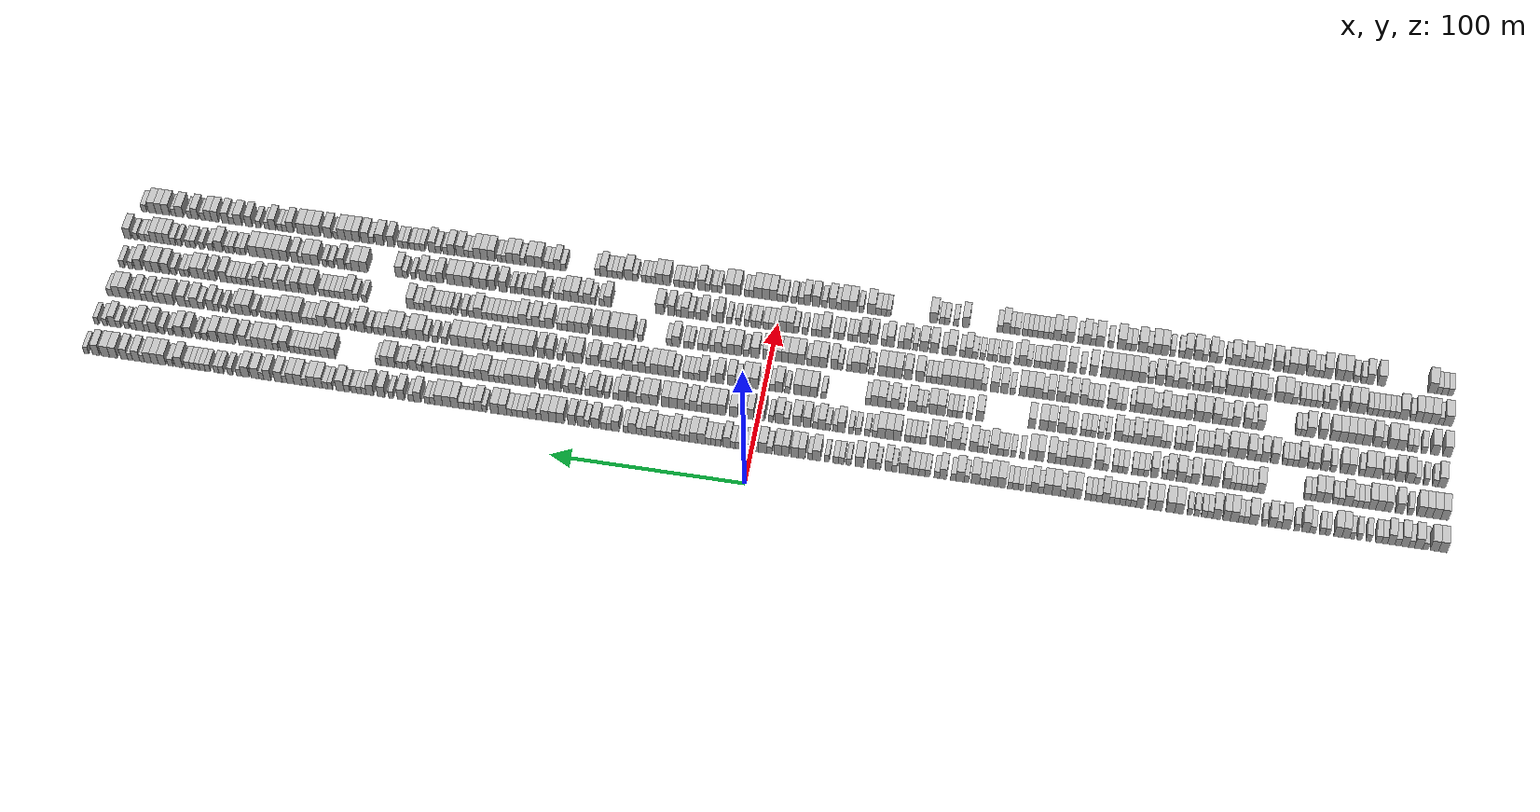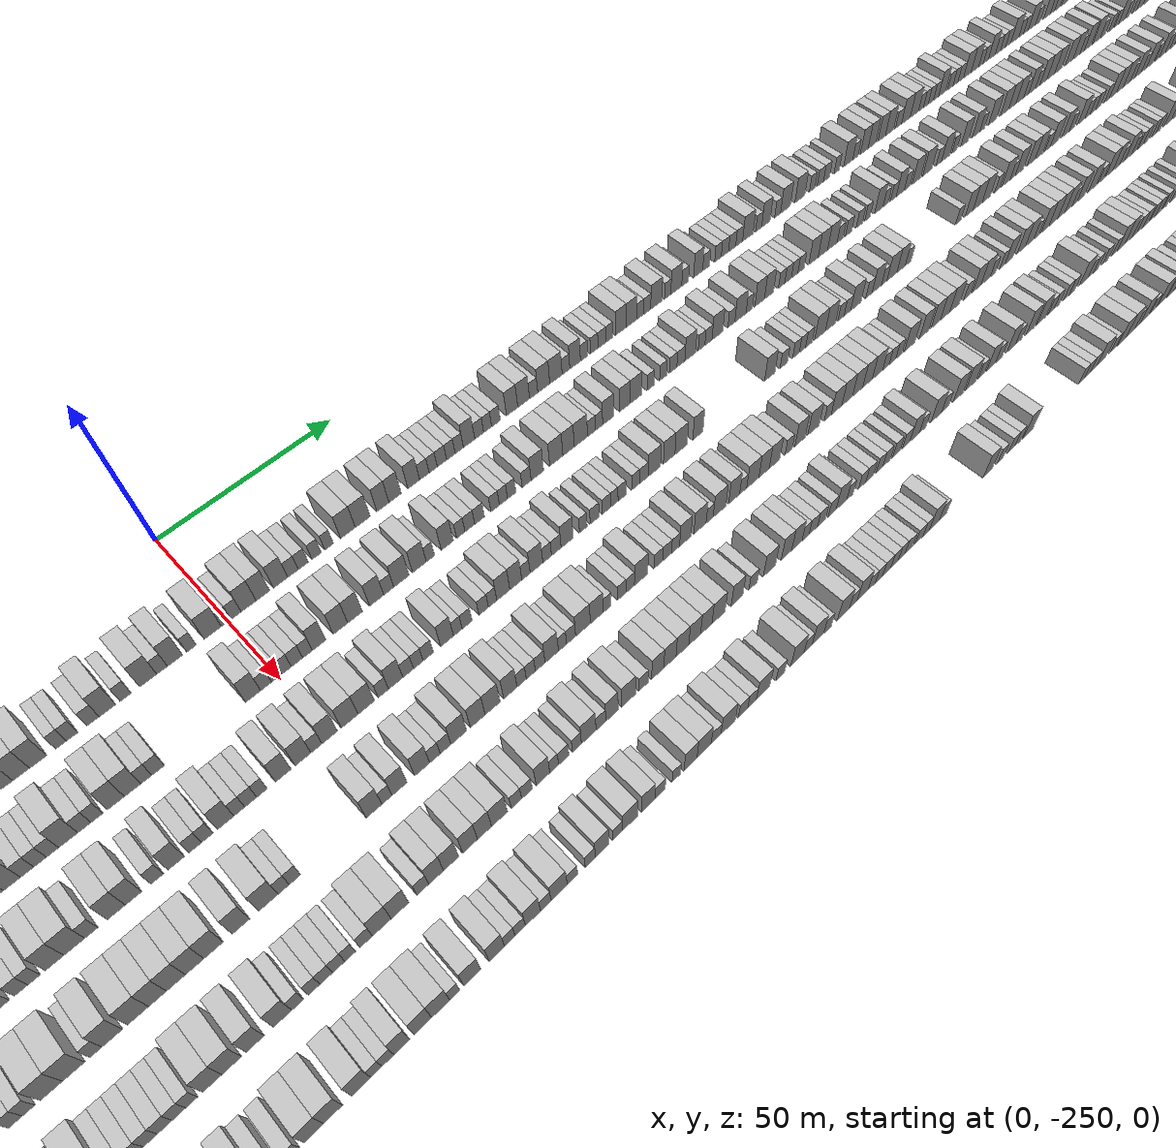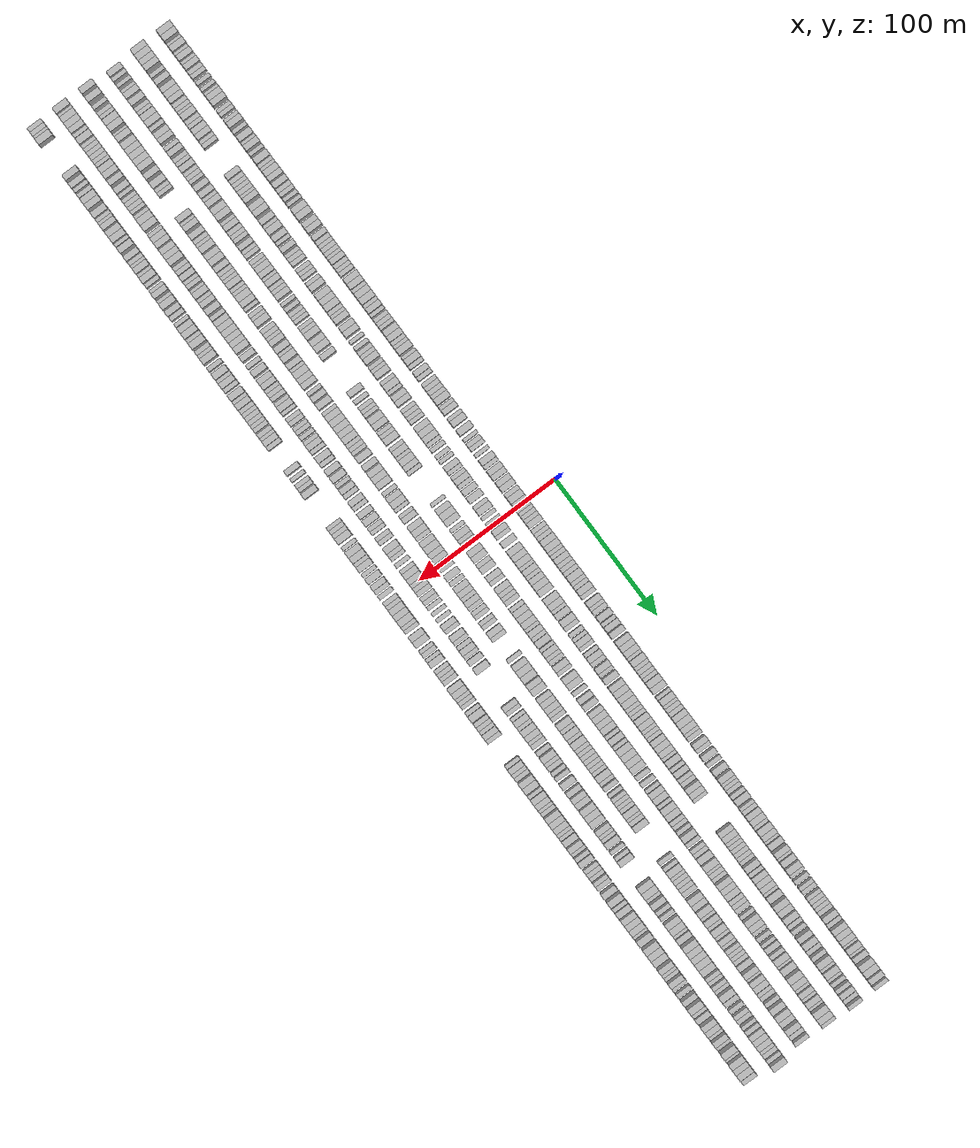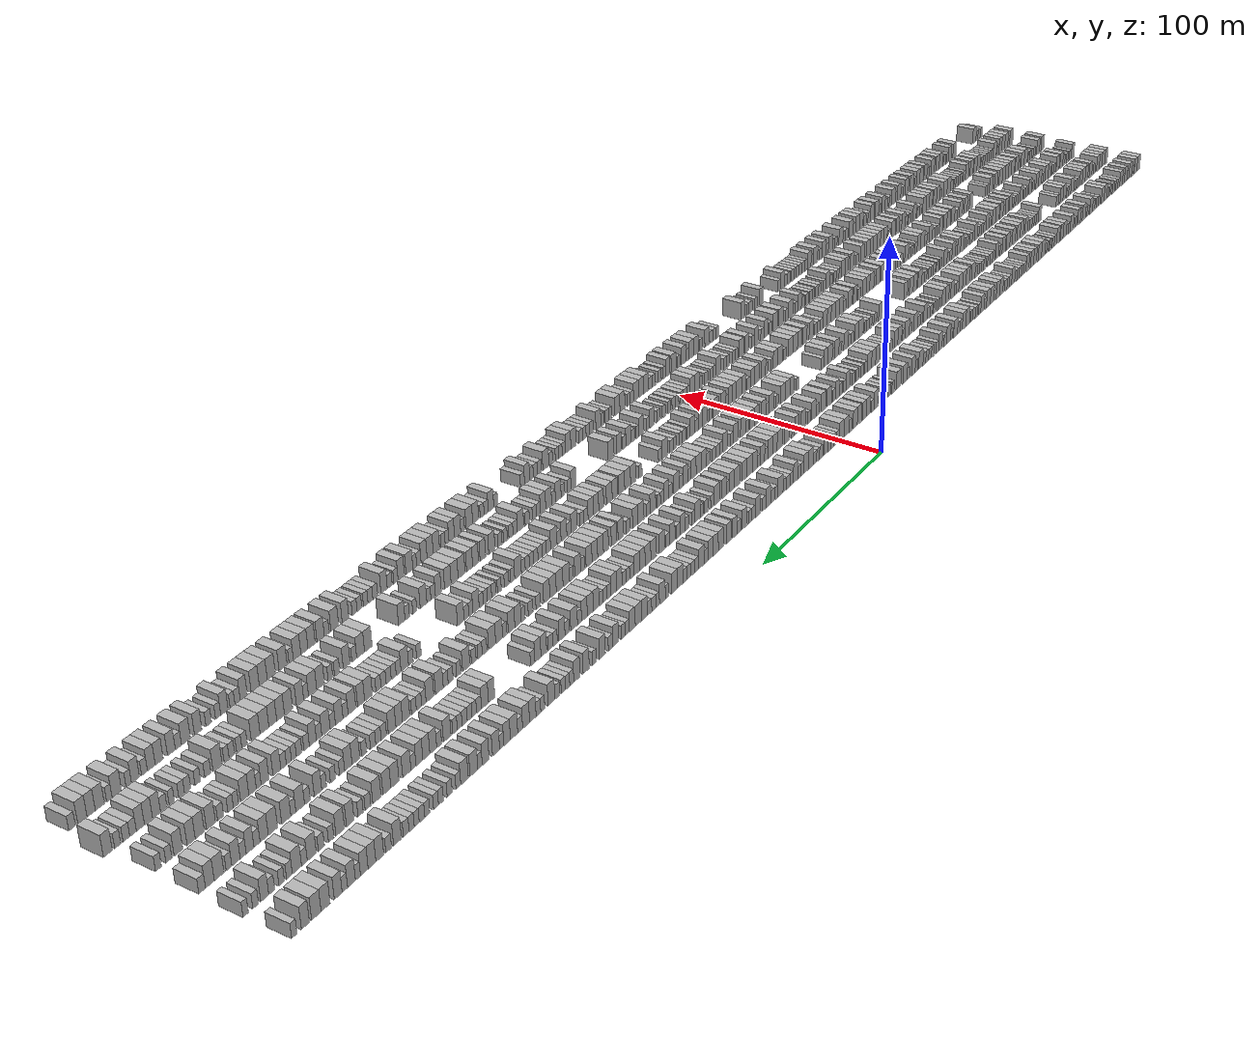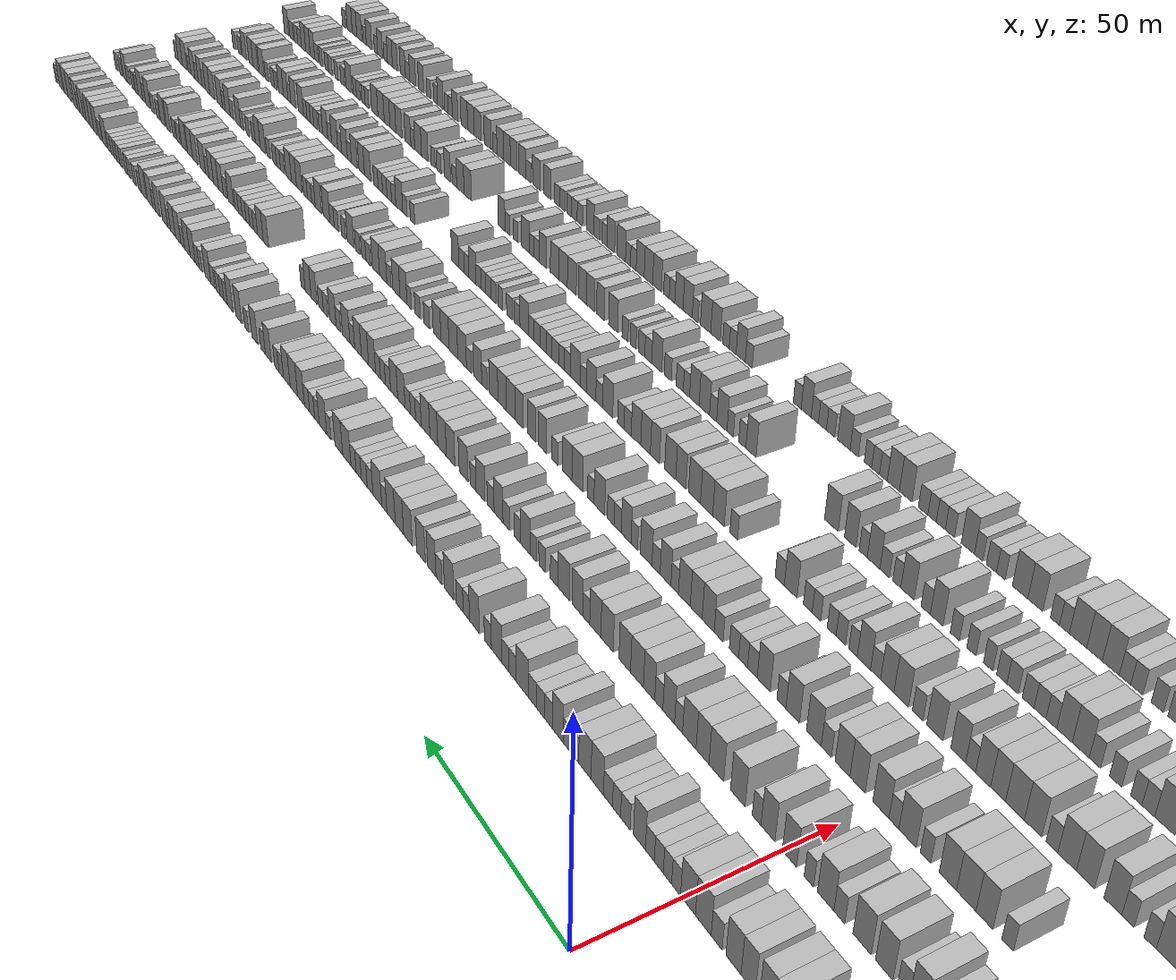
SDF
<sdf version="1.6">
 <world name="default">
  <scene>
   <sky><clouds><speed>12</speed></clouds></sky>
   <ambient>0.4 0.4 0.4 1</ambient>
   <background>0.7 0.7 0.7 1</background>
   <shadows>1</shadows>
  </scene>
  <gravity>0 0 -9.8066</gravity>
  <magnetic_field>6e-06 2.3e-05 -4.2e-05</magnetic_field>
  <physics default="0" name="default_physics" type="ode">
   <ode>
    <solver>
     <type>quick</type>
     <iters>10</iters>
     <sor>1.0</sor>
     <use_dynamic_moi_rescaling>0</use_dynamic_moi_rescaling>
    </solver>
    <constraints>
     <cfm>0</cfm>
     <erp>0.2</erp>
     <contact_max_correcting_vel>100</contact_max_correcting_vel>
     <contact_surface_layer>0.001</contact_surface_layer>
    </constraints>
   </ode>
   <max_step_size>0.004</max_step_size>
   <real_time_factor>1</real_time_factor>
   <real_time_update_rate>250</real_time_update_rate>
  </physics>
  <light name="sun" type="directional">
   <pose>0 0 10 0 0 0</pose>
   <diffuse>0.8 0.8 0.8 1</diffuse>
   <specular>0.2 0.2 0.2 1</specular>
   <attenuation>
    <range>1000</range>
    <constant>0.9</constant>
    <linear>0.01</linear>
    <quadratic>0.001</quadratic>
   </attenuation>
   <direction>-0.5 0.1 -0.9</direction>
  </light>
  <model name="building_1">
   <static>1</static>
   <pose>25.0000 -347.8892 0 0.000000 0.000000 0.000000</pose>
   <link name="link">
    <pose>0 0 4.50 0 0 0</pose>
    <collision name="collision"><geometry><box><size>10.0000 4.2216 9.0000</size></box></geometry></collision>
    <visual name="visual">
     <cast_shadows>0</cast_shadows>
     <geometry><box><size>10.0000 4.2216 9.0000</size></box></geometry>
     <material>
      <script>
       <uri>model://HANNAS_wall/materials/scripts</uri>
       <uri>model://HANNAS_wall/materials/textures</uri>
       <name>vrc/HANNAS_wall</name>
      </script>
     </material>
    </visual>
   </link>
  </model>
  <model name="building_2">
   <static>1</static>
   <pose>25.0000 -343.7324 0 0.000000 0.000000 0.000000</pose>
   <link name="link">
    <pose>0 0 4.50 0 0 0</pose>
    <collision name="collision"><geometry><box><size>10.0000 4.0920 9.0000</size></box></geometry></collision>
    <visual name="visual">
     <cast_shadows>0</cast_shadows>
     <geometry><box><size>10.0000 4.0920 9.0000</size></box></geometry>
     <material>
      <script>
       <uri>model://HANNAS_wall/materials/scripts</uri>
       <uri>model://HANNAS_wall/materials/textures</uri>
       <name>vrc/HANNAS_wall</name>
      </script>
     </material>
    </visual>
   </link>
  </model>
  <model name="building_3">
   <static>1</static>
   <pose>25.0000 -339.3611 0 0.000000 0.000000 0.000000</pose>
   <link name="link">
    <pose>0 0 3.00 0 0 0</pose>
    <collision name="collision"><geometry><box><size>10.0000 2.6506 6.0000</size></box></geometry></collision>
    <visual name="visual">
     <cast_shadows>0</cast_shadows>
     <geometry><box><size>10.0000 2.6506 6.0000</size></box></geometry>
     <material>
      <script>
       <uri>model://HANNAS_wall/materials/scripts</uri>
       <uri>model://HANNAS_wall/materials/textures</uri>
       <name>vrc/HANNAS_wall</name>
      </script>
     </material>
    </visual>
   </link>
  </model>
  <model name="building_4">
   <static>1</static>
   <pose>25.0000 -335.9743 0 0.000000 0.000000 0.000000</pose>
   <link name="link">
    <pose>0 0 4.50 0 0 0</pose>
    <collision name="collision"><geometry><box><size>10.0000 4.1231 9.0000</size></box></geometry></collision>
    <visual name="visual">
     <cast_shadows>0</cast_shadows>
     <geometry><box><size>10.0000 4.1231 9.0000</size></box></geometry>
     <material>
      <script>
       <uri>model://HANNAS_wall/materials/scripts</uri>
       <uri>model://HANNAS_wall/materials/textures</uri>
       <name>vrc/HANNAS_wall</name>
      </script>
     </material>
    </visual>
   </link>
  </model>
  <model name="building_5">
   <static>1</static>
   <pose>25.0000 -332.4978 0 0.000000 0.000000 0.000000</pose>
   <link name="link">
    <pose>0 0 3.00 0 0 0</pose>
    <collision name="collision"><geometry><box><size>10.0000 2.8299 6.0000</size></box></geometry></collision>
    <visual name="visual">
     <cast_shadows>0</cast_shadows>
     <geometry><box><size>10.0000 2.8299 6.0000</size></box></geometry>
     <material>
      <script>
       <uri>model://HANNAS_wall/materials/scripts</uri>
       <uri>model://HANNAS_wall/materials/textures</uri>
       <name>vrc/HANNAS_wall</name>
      </script>
     </material>
    </visual>
   </link>
  </model>
  <model name="building_6">
   <static>1</static>
   <pose>25.0000 -329.1431 0 0.000000 0.000000 0.000000</pose>
   <link name="link">
    <pose>0 0 4.50 0 0 0</pose>
    <collision name="collision"><geometry><box><size>10.0000 3.8795 9.0000</size></box></geometry></collision>
    <visual name="visual">
     <cast_shadows>0</cast_shadows>
     <geometry><box><size>10.0000 3.8795 9.0000</size></box></geometry>
     <material>
      <script>
       <uri>model://HANNAS_wall/materials/scripts</uri>
       <uri>model://HANNAS_wall/materials/textures</uri>
       <name>vrc/HANNAS_wall</name>
      </script>
     </material>
    </visual>
   </link>
  </model>
  <model name="building_7">
   <static>1</static>
   <pose>25.0000 -325.7389 0 0.000000 0.000000 0.000000</pose>
   <link name="link">
    <pose>0 0 3.00 0 0 0</pose>
    <collision name="collision"><geometry><box><size>10.0000 2.9289 6.0000</size></box></geometry></collision>
    <visual name="visual">
     <cast_shadows>0</cast_shadows>
     <geometry><box><size>10.0000 2.9289 6.0000</size></box></geometry>
     <material>
      <script>
       <uri>model://HANNAS_wall/materials/scripts</uri>
       <uri>model://HANNAS_wall/materials/textures</uri>
       <name>vrc/HANNAS_wall</name>
      </script>
     </material>
    </visual>
   </link>
  </model>
  <model name="building_8">
   <static>1</static>
   <pose>25.0000 -322.4290 0 0.000000 0.000000 0.000000</pose>
   <link name="link">
    <pose>0 0 4.50 0 0 0</pose>
    <collision name="collision"><geometry><box><size>10.0000 3.6909 9.0000</size></box></geometry></collision>
    <visual name="visual">
     <cast_shadows>0</cast_shadows>
     <geometry><box><size>10.0000 3.6909 9.0000</size></box></geometry>
     <material>
      <script>
       <uri>model://HANNAS_wall/materials/scripts</uri>
       <uri>model://HANNAS_wall/materials/textures</uri>
       <name>vrc/HANNAS_wall</name>
      </script>
     </material>
    </visual>
   </link>
  </model>
  <model name="building_9">
   <static>1</static>
   <pose>25.0000 -319.1294 0 0.000000 0.000000 0.000000</pose>
   <link name="link">
    <pose>0 0 3.00 0 0 0</pose>
    <collision name="collision"><geometry><box><size>10.0000 2.9083 6.0000</size></box></geometry></collision>
    <visual name="visual">
     <cast_shadows>0</cast_shadows>
     <geometry><box><size>10.0000 2.9083 6.0000</size></box></geometry>
     <material>
      <script>
       <uri>model://HANNAS_wall/materials/scripts</uri>
       <uri>model://HANNAS_wall/materials/textures</uri>
       <name>vrc/HANNAS_wall</name>
      </script>
     </material>
    </visual>
   </link>
  </model>
  <model name="building_10">
   <static>1</static>
   <pose>25.0000 -316.1820 0 0.000000 0.000000 0.000000</pose>
   <link name="link">
    <pose>0 0 3.00 0 0 0</pose>
    <collision name="collision"><geometry><box><size>10.0000 2.9864 6.0000</size></box></geometry></collision>
    <visual name="visual">
     <cast_shadows>0</cast_shadows>
     <geometry><box><size>10.0000 2.9864 6.0000</size></box></geometry>
     <material>
      <script>
       <uri>model://HANNAS_wall/materials/scripts</uri>
       <uri>model://HANNAS_wall/materials/textures</uri>
       <name>vrc/HANNAS_wall</name>
      </script>
     </material>
    </visual>
   </link>
  </model>
  <model name="building_11">
   <static>1</static>
   <pose>25.0000 -311.3338 0 0.000000 0.000000 0.000000</pose>
   <link name="link">
    <pose>0 0 3.00 0 0 0</pose>
    <collision name="collision"><geometry><box><size>10.0000 2.7099 6.0000</size></box></geometry></collision>
    <visual name="visual">
     <cast_shadows>0</cast_shadows>
     <geometry><box><size>10.0000 2.7099 6.0000</size></box></geometry>
     <material>
      <script>
       <uri>model://HANNAS_wall/materials/scripts</uri>
       <uri>model://HANNAS_wall/materials/textures</uri>
       <name>vrc/HANNAS_wall</name>
      </script>
     </material>
    </visual>
   </link>
  </model>
  <model name="building_12">
   <static>1</static>
   <pose>25.0000 -306.7217 0 0.000000 0.000000 0.000000</pose>
   <link name="link">
    <pose>0 0 3.00 0 0 0</pose>
    <collision name="collision"><geometry><box><size>10.0000 2.5142 6.0000</size></box></geometry></collision>
    <visual name="visual">
     <cast_shadows>0</cast_shadows>
     <geometry><box><size>10.0000 2.5142 6.0000</size></box></geometry>
     <material>
      <script>
       <uri>model://HANNAS_wall/materials/scripts</uri>
       <uri>model://HANNAS_wall/materials/textures</uri>
       <name>vrc/HANNAS_wall</name>
      </script>
     </material>
    </visual>
   </link>
  </model>
  <model name="building_13">
   <static>1</static>
   <pose>25.0000 -303.1790 0 0.000000 0.000000 0.000000</pose>
   <link name="link">
    <pose>0 0 3.00 0 0 0</pose>
    <collision name="collision"><geometry><box><size>10.0000 2.5713 6.0000</size></box></geometry></collision>
    <visual name="visual">
     <cast_shadows>0</cast_shadows>
     <geometry><box><size>10.0000 2.5713 6.0000</size></box></geometry>
     <material>
      <script>
       <uri>model://HANNAS_wall/materials/scripts</uri>
       <uri>model://HANNAS_wall/materials/textures</uri>
       <name>vrc/HANNAS_wall</name>
      </script>
     </material>
    </visual>
   </link>
  </model>
  <model name="building_14">
   <static>1</static>
   <pose>25.0000 -300.0130 0 0.000000 0.000000 0.000000</pose>
   <link name="link">
    <pose>0 0 4.50 0 0 0</pose>
    <collision name="collision"><geometry><box><size>10.0000 3.7607 9.0000</size></box></geometry></collision>
    <visual name="visual">
     <cast_shadows>0</cast_shadows>
     <geometry><box><size>10.0000 3.7607 9.0000</size></box></geometry>
     <material>
      <script>
       <uri>model://HANNAS_wall/materials/scripts</uri>
       <uri>model://HANNAS_wall/materials/textures</uri>
       <name>vrc/HANNAS_wall</name>
      </script>
     </material>
    </visual>
   </link>
  </model>
  <model name="building_15">
   <static>1</static>
   <pose>25.0000 -296.1881 0 0.000000 0.000000 0.000000</pose>
   <link name="link">
    <pose>0 0 4.50 0 0 0</pose>
    <collision name="collision"><geometry><box><size>10.0000 3.8890 9.0000</size></box></geometry></collision>
    <visual name="visual">
     <cast_shadows>0</cast_shadows>
     <geometry><box><size>10.0000 3.8890 9.0000</size></box></geometry>
     <material>
      <script>
       <uri>model://HANNAS_wall/materials/scripts</uri>
       <uri>model://HANNAS_wall/materials/textures</uri>
       <name>vrc/HANNAS_wall</name>
      </script>
     </material>
    </visual>
   </link>
  </model>
  <model name="building_16">
   <static>1</static>
   <pose>25.0000 -291.0046 0 0.000000 0.000000 0.000000</pose>
   <link name="link">
    <pose>0 0 3.00 0 0 0</pose>
    <collision name="collision"><geometry><box><size>10.0000 2.4780 6.0000</size></box></geometry></collision>
    <visual name="visual">
     <cast_shadows>0</cast_shadows>
     <geometry><box><size>10.0000 2.4780 6.0000</size></box></geometry>
     <material>
      <script>
       <uri>model://HANNAS_wall/materials/scripts</uri>
       <uri>model://HANNAS_wall/materials/textures</uri>
       <name>vrc/HANNAS_wall</name>
      </script>
     </material>
    </visual>
   </link>
  </model>
  <model name="building_17">
   <static>1</static>
   <pose>25.0000 -288.4177 0 0.000000 0.000000 0.000000</pose>
   <link name="link">
    <pose>0 0 3.00 0 0 0</pose>
    <collision name="collision"><geometry><box><size>10.0000 2.6958 6.0000</size></box></geometry></collision>
    <visual name="visual">
     <cast_shadows>0</cast_shadows>
     <geometry><box><size>10.0000 2.6958 6.0000</size></box></geometry>
     <material>
      <script>
       <uri>model://HANNAS_wall/materials/scripts</uri>
       <uri>model://HANNAS_wall/materials/textures</uri>
       <name>vrc/HANNAS_wall</name>
      </script>
     </material>
    </visual>
   </link>
  </model>
  <model name="building_18">
   <static>1</static>
   <pose>25.0000 -283.5823 0 0.000000 0.000000 0.000000</pose>
   <link name="link">
    <pose>0 0 3.00 0 0 0</pose>
    <collision name="collision"><geometry><box><size>10.0000 2.9750 6.0000</size></box></geometry></collision>
    <visual name="visual">
     <cast_shadows>0</cast_shadows>
     <geometry><box><size>10.0000 2.9750 6.0000</size></box></geometry>
     <material>
      <script>
       <uri>model://HANNAS_wall/materials/scripts</uri>
       <uri>model://HANNAS_wall/materials/textures</uri>
       <name>vrc/HANNAS_wall</name>
      </script>
     </material>
    </visual>
   </link>
  </model>
  <model name="building_19">
   <static>1</static>
   <pose>25.0000 -280.1263 0 0.000000 0.000000 0.000000</pose>
   <link name="link">
    <pose>0 0 4.50 0 0 0</pose>
    <collision name="collision"><geometry><box><size>10.0000 3.9369 9.0000</size></box></geometry></collision>
    <visual name="visual">
     <cast_shadows>0</cast_shadows>
     <geometry><box><size>10.0000 3.9369 9.0000</size></box></geometry>
     <material>
      <script>
       <uri>model://HANNAS_wall/materials/scripts</uri>
       <uri>model://HANNAS_wall/materials/textures</uri>
       <name>vrc/HANNAS_wall</name>
      </script>
     </material>
    </visual>
   </link>
  </model>
  <model name="building_20">
   <static>1</static>
   <pose>25.0000 -275.7909 0 0.000000 0.000000 0.000000</pose>
   <link name="link">
    <pose>0 0 3.00 0 0 0</pose>
    <collision name="collision"><geometry><box><size>10.0000 2.7338 6.0000</size></box></geometry></collision>
    <visual name="visual">
     <cast_shadows>0</cast_shadows>
     <geometry><box><size>10.0000 2.7338 6.0000</size></box></geometry>
     <material>
      <script>
       <uri>model://HANNAS_wall/materials/scripts</uri>
       <uri>model://HANNAS_wall/materials/textures</uri>
       <name>vrc/HANNAS_wall</name>
      </script>
     </material>
    </visual>
   </link>
  </model>
  <model name="building_21">
   <static>1</static>
   <pose>25.0000 -270.3111 0 0.000000 0.000000 0.000000</pose>
   <link name="link">
    <pose>0 0 4.50 0 0 0</pose>
    <collision name="collision"><geometry><box><size>10.0000 4.2259 9.0000</size></box></geometry></collision>
    <visual name="visual">
     <cast_shadows>0</cast_shadows>
     <geometry><box><size>10.0000 4.2259 9.0000</size></box></geometry>
     <material>
      <script>
       <uri>model://HANNAS_wall/materials/scripts</uri>
       <uri>model://HANNAS_wall/materials/textures</uri>
       <name>vrc/HANNAS_wall</name>
      </script>
     </material>
    </visual>
   </link>
  </model>
  <model name="building_22">
   <static>1</static>
   <pose>25.0000 -266.8667 0 0.000000 0.000000 0.000000</pose>
   <link name="link">
    <pose>0 0 3.00 0 0 0</pose>
    <collision name="collision"><geometry><box><size>10.0000 2.6630 6.0000</size></box></geometry></collision>
    <visual name="visual">
     <cast_shadows>0</cast_shadows>
     <geometry><box><size>10.0000 2.6630 6.0000</size></box></geometry>
     <material>
      <script>
       <uri>model://HANNAS_wall/materials/scripts</uri>
       <uri>model://HANNAS_wall/materials/textures</uri>
       <name>vrc/HANNAS_wall</name>
      </script>
     </material>
    </visual>
   </link>
  </model>
  <model name="building_23">
   <static>1</static>
   <pose>25.0000 -263.6140 0 0.000000 0.000000 0.000000</pose>
   <link name="link">
    <pose>0 0 4.50 0 0 0</pose>
    <collision name="collision"><geometry><box><size>10.0000 3.8423 9.0000</size></box></geometry></collision>
    <visual name="visual">
     <cast_shadows>0</cast_shadows>
     <geometry><box><size>10.0000 3.8423 9.0000</size></box></geometry>
     <material>
      <script>
       <uri>model://HANNAS_wall/materials/scripts</uri>
       <uri>model://HANNAS_wall/materials/textures</uri>
       <name>vrc/HANNAS_wall</name>
      </script>
     </material>
    </visual>
   </link>
  </model>
  <model name="building_24">
   <static>1</static>
   <pose>25.0000 -259.4730 0 0.000000 0.000000 0.000000</pose>
   <link name="link">
    <pose>0 0 3.00 0 0 0</pose>
    <collision name="collision"><geometry><box><size>10.0000 2.4398 6.0000</size></box></geometry></collision>
    <visual name="visual">
     <cast_shadows>0</cast_shadows>
     <geometry><box><size>10.0000 2.4398 6.0000</size></box></geometry>
     <material>
      <script>
       <uri>model://HANNAS_wall/materials/scripts</uri>
       <uri>model://HANNAS_wall/materials/textures</uri>
       <name>vrc/HANNAS_wall</name>
      </script>
     </material>
    </visual>
   </link>
  </model>
  <model name="building_25">
   <static>1</static>
   <pose>25.0000 -254.0365 0 0.000000 0.000000 0.000000</pose>
   <link name="link">
    <pose>0 0 4.50 0 0 0</pose>
    <collision name="collision"><geometry><box><size>10.0000 4.4332 9.0000</size></box></geometry></collision>
    <visual name="visual">
     <cast_shadows>0</cast_shadows>
     <geometry><box><size>10.0000 4.4332 9.0000</size></box></geometry>
     <material>
      <script>
       <uri>model://HANNAS_wall/materials/scripts</uri>
       <uri>model://HANNAS_wall/materials/textures</uri>
       <name>vrc/HANNAS_wall</name>
      </script>
     </material>
    </visual>
   </link>
  </model>
  <model name="building_26">
   <static>1</static>
   <pose>25.0000 -250.5662 0 0.000000 0.000000 0.000000</pose>
   <link name="link">
    <pose>0 0 3.00 0 0 0</pose>
    <collision name="collision"><geometry><box><size>10.0000 2.5076 6.0000</size></box></geometry></collision>
    <visual name="visual">
     <cast_shadows>0</cast_shadows>
     <geometry><box><size>10.0000 2.5076 6.0000</size></box></geometry>
     <material>
      <script>
       <uri>model://HANNAS_wall/materials/scripts</uri>
       <uri>model://HANNAS_wall/materials/textures</uri>
       <name>vrc/HANNAS_wall</name>
      </script>
     </material>
    </visual>
   </link>
  </model>
  <model name="building_27">
   <static>1</static>
   <pose>25.0000 -247.9675 0 0.000000 0.000000 0.000000</pose>
   <link name="link">
    <pose>0 0 3.00 0 0 0</pose>
    <collision name="collision"><geometry><box><size>10.0000 2.6899 6.0000</size></box></geometry></collision>
    <visual name="visual">
     <cast_shadows>0</cast_shadows>
     <geometry><box><size>10.0000 2.6899 6.0000</size></box></geometry>
     <material>
      <script>
       <uri>model://HANNAS_wall/materials/scripts</uri>
       <uri>model://HANNAS_wall/materials/textures</uri>
       <name>vrc/HANNAS_wall</name>
      </script>
     </material>
    </visual>
   </link>
  </model>
  <model name="building_28">
   <static>1</static>
   <pose>25.0000 -244.6203 0 0.000000 0.000000 0.000000</pose>
   <link name="link">
    <pose>0 0 4.50 0 0 0</pose>
    <collision name="collision"><geometry><box><size>10.0000 4.0044 9.0000</size></box></geometry></collision>
    <visual name="visual">
     <cast_shadows>0</cast_shadows>
     <geometry><box><size>10.0000 4.0044 9.0000</size></box></geometry>
     <material>
      <script>
       <uri>model://HANNAS_wall/materials/scripts</uri>
       <uri>model://HANNAS_wall/materials/textures</uri>
       <name>vrc/HANNAS_wall</name>
      </script>
     </material>
    </visual>
   </link>
  </model>
  <model name="building_29">
   <static>1</static>
   <pose>25.0000 -240.7944 0 0.000000 0.000000 0.000000</pose>
   <link name="link">
    <pose>0 0 4.50 0 0 0</pose>
    <collision name="collision"><geometry><box><size>10.0000 3.6475 9.0000</size></box></geometry></collision>
    <visual name="visual">
     <cast_shadows>0</cast_shadows>
     <geometry><box><size>10.0000 3.6475 9.0000</size></box></geometry>
     <material>
      <script>
       <uri>model://HANNAS_wall/materials/scripts</uri>
       <uri>model://HANNAS_wall/materials/textures</uri>
       <name>vrc/HANNAS_wall</name>
      </script>
     </material>
    </visual>
   </link>
  </model>
  <model name="building_30">
   <static>1</static>
   <pose>25.0000 -235.9976 0 0.000000 0.000000 0.000000</pose>
   <link name="link">
    <pose>0 0 4.50 0 0 0</pose>
    <collision name="collision"><geometry><box><size>10.0000 3.9461 9.0000</size></box></geometry></collision>
    <visual name="visual">
     <cast_shadows>0</cast_shadows>
     <geometry><box><size>10.0000 3.9461 9.0000</size></box></geometry>
     <material>
      <script>
       <uri>model://HANNAS_wall/materials/scripts</uri>
       <uri>model://HANNAS_wall/materials/textures</uri>
       <name>vrc/HANNAS_wall</name>
      </script>
     </material>
    </visual>
   </link>
  </model>
  <model name="building_31">
   <static>1</static>
   <pose>25.0000 -232.5794 0 0.000000 0.000000 0.000000</pose>
   <link name="link">
    <pose>0 0 3.00 0 0 0</pose>
    <collision name="collision"><geometry><box><size>10.0000 2.8902 6.0000</size></box></geometry></collision>
    <visual name="visual">
     <cast_shadows>0</cast_shadows>
     <geometry><box><size>10.0000 2.8902 6.0000</size></box></geometry>
     <material>
      <script>
       <uri>model://HANNAS_wall/materials/scripts</uri>
       <uri>model://HANNAS_wall/materials/textures</uri>
       <name>vrc/HANNAS_wall</name>
      </script>
     </material>
    </visual>
   </link>
  </model>
  <model name="building_32">
   <static>1</static>
   <pose>25.0000 -229.7361 0 0.000000 0.000000 0.000000</pose>
   <link name="link">
    <pose>0 0 3.00 0 0 0</pose>
    <collision name="collision"><geometry><box><size>10.0000 2.7963 6.0000</size></box></geometry></collision>
    <visual name="visual">
     <cast_shadows>0</cast_shadows>
     <geometry><box><size>10.0000 2.7963 6.0000</size></box></geometry>
     <material>
      <script>
       <uri>model://HANNAS_wall/materials/scripts</uri>
       <uri>model://HANNAS_wall/materials/textures</uri>
       <name>vrc/HANNAS_wall</name>
      </script>
     </material>
    </visual>
   </link>
  </model>
  <model name="building_33">
   <static>1</static>
   <pose>25.0000 -226.0289 0 0.000000 0.000000 0.000000</pose>
   <link name="link">
    <pose>0 0 3.00 0 0 0</pose>
    <collision name="collision"><geometry><box><size>10.0000 2.6181 6.0000</size></box></geometry></collision>
    <visual name="visual">
     <cast_shadows>0</cast_shadows>
     <geometry><box><size>10.0000 2.6181 6.0000</size></box></geometry>
     <material>
      <script>
       <uri>model://HANNAS_wall/materials/scripts</uri>
       <uri>model://HANNAS_wall/materials/textures</uri>
       <name>vrc/HANNAS_wall</name>
      </script>
     </material>
    </visual>
   </link>
  </model>
  <model name="building_34">
   <static>1</static>
   <pose>25.0000 -222.4852 0 0.000000 0.000000 0.000000</pose>
   <link name="link">
    <pose>0 0 3.00 0 0 0</pose>
    <collision name="collision"><geometry><box><size>10.0000 2.4694 6.0000</size></box></geometry></collision>
    <visual name="visual">
     <cast_shadows>0</cast_shadows>
     <geometry><box><size>10.0000 2.4694 6.0000</size></box></geometry>
     <material>
      <script>
       <uri>model://HANNAS_wall/materials/scripts</uri>
       <uri>model://HANNAS_wall/materials/textures</uri>
       <name>vrc/HANNAS_wall</name>
      </script>
     </material>
    </visual>
   </link>
  </model>
  <model name="building_35">
   <static>1</static>
   <pose>25.0000 -217.1105 0 0.000000 0.000000 0.000000</pose>
   <link name="link">
    <pose>0 0 4.50 0 0 0</pose>
    <collision name="collision"><geometry><box><size>10.0000 4.2799 9.0000</size></box></geometry></collision>
    <visual name="visual">
     <cast_shadows>0</cast_shadows>
     <geometry><box><size>10.0000 4.2799 9.0000</size></box></geometry>
     <material>
      <script>
       <uri>model://HANNAS_wall/materials/scripts</uri>
       <uri>model://HANNAS_wall/materials/textures</uri>
       <name>vrc/HANNAS_wall</name>
      </script>
     </material>
    </visual>
   </link>
  </model>
  <model name="building_36">
   <static>1</static>
   <pose>25.0000 -212.7914 0 0.000000 0.000000 0.000000</pose>
   <link name="link">
    <pose>0 0 4.50 0 0 0</pose>
    <collision name="collision"><geometry><box><size>10.0000 4.3583 9.0000</size></box></geometry></collision>
    <visual name="visual">
     <cast_shadows>0</cast_shadows>
     <geometry><box><size>10.0000 4.3583 9.0000</size></box></geometry>
     <material>
      <script>
       <uri>model://HANNAS_wall/materials/scripts</uri>
       <uri>model://HANNAS_wall/materials/textures</uri>
       <name>vrc/HANNAS_wall</name>
      </script>
     </material>
    </visual>
   </link>
  </model>
  <model name="building_37">
   <static>1</static>
   <pose>25.0000 -206.8093 0 0.000000 0.000000 0.000000</pose>
   <link name="link">
    <pose>0 0 4.50 0 0 0</pose>
    <collision name="collision"><geometry><box><size>10.0000 3.6058 9.0000</size></box></geometry></collision>
    <visual name="visual">
     <cast_shadows>0</cast_shadows>
     <geometry><box><size>10.0000 3.6058 9.0000</size></box></geometry>
     <material>
      <script>
       <uri>model://HANNAS_wall/materials/scripts</uri>
       <uri>model://HANNAS_wall/materials/textures</uri>
       <name>vrc/HANNAS_wall</name>
      </script>
     </material>
    </visual>
   </link>
  </model>
  <model name="building_38">
   <static>1</static>
   <pose>25.0000 -203.1547 0 0.000000 0.000000 0.000000</pose>
   <link name="link">
    <pose>0 0 4.50 0 0 0</pose>
    <collision name="collision"><geometry><box><size>10.0000 3.7034 9.0000</size></box></geometry></collision>
    <visual name="visual">
     <cast_shadows>0</cast_shadows>
     <geometry><box><size>10.0000 3.7034 9.0000</size></box></geometry>
     <material>
      <script>
       <uri>model://HANNAS_wall/materials/scripts</uri>
       <uri>model://HANNAS_wall/materials/textures</uri>
       <name>vrc/HANNAS_wall</name>
      </script>
     </material>
    </visual>
   </link>
  </model>
  <model name="building_39">
   <static>1</static>
   <pose>25.0000 -197.4959 0 0.000000 0.000000 0.000000</pose>
   <link name="link">
    <pose>0 0 4.50 0 0 0</pose>
    <collision name="collision"><geometry><box><size>10.0000 3.6141 9.0000</size></box></geometry></collision>
    <visual name="visual">
     <cast_shadows>0</cast_shadows>
     <geometry><box><size>10.0000 3.6141 9.0000</size></box></geometry>
     <material>
      <script>
       <uri>model://HANNAS_wall/materials/scripts</uri>
       <uri>model://HANNAS_wall/materials/textures</uri>
       <name>vrc/HANNAS_wall</name>
      </script>
     </material>
    </visual>
   </link>
  </model>
  <model name="building_40">
   <static>1</static>
   <pose>25.0000 -194.2174 0 0.000000 0.000000 0.000000</pose>
   <link name="link">
    <pose>0 0 3.00 0 0 0</pose>
    <collision name="collision"><geometry><box><size>10.0000 2.9428 6.0000</size></box></geometry></collision>
    <visual name="visual">
     <cast_shadows>0</cast_shadows>
     <geometry><box><size>10.0000 2.9428 6.0000</size></box></geometry>
     <material>
      <script>
       <uri>model://HANNAS_wall/materials/scripts</uri>
       <uri>model://HANNAS_wall/materials/textures</uri>
       <name>vrc/HANNAS_wall</name>
      </script>
     </material>
    </visual>
   </link>
  </model>
  <model name="building_41">
   <static>1</static>
   <pose>25.0000 -191.4940 0 0.000000 0.000000 0.000000</pose>
   <link name="link">
    <pose>0 0 3.00 0 0 0</pose>
    <collision name="collision"><geometry><box><size>10.0000 2.5040 6.0000</size></box></geometry></collision>
    <visual name="visual">
     <cast_shadows>0</cast_shadows>
     <geometry><box><size>10.0000 2.5040 6.0000</size></box></geometry>
     <material>
      <script>
       <uri>model://HANNAS_wall/materials/scripts</uri>
       <uri>model://HANNAS_wall/materials/textures</uri>
       <name>vrc/HANNAS_wall</name>
      </script>
     </material>
    </visual>
   </link>
  </model>
  <model name="building_42">
   <static>1</static>
   <pose>25.0000 -188.7656 0 0.000000 0.000000 0.000000</pose>
   <link name="link">
    <pose>0 0 3.00 0 0 0</pose>
    <collision name="collision"><geometry><box><size>10.0000 2.9529 6.0000</size></box></geometry></collision>
    <visual name="visual">
     <cast_shadows>0</cast_shadows>
     <geometry><box><size>10.0000 2.9529 6.0000</size></box></geometry>
     <material>
      <script>
       <uri>model://HANNAS_wall/materials/scripts</uri>
       <uri>model://HANNAS_wall/materials/textures</uri>
       <name>vrc/HANNAS_wall</name>
      </script>
     </material>
    </visual>
   </link>
  </model>
  <model name="building_43">
   <static>1</static>
   <pose>25.0000 -185.9451 0 0.000000 0.000000 0.000000</pose>
   <link name="link">
    <pose>0 0 3.00 0 0 0</pose>
    <collision name="collision"><geometry><box><size>10.0000 2.6881 6.0000</size></box></geometry></collision>
    <visual name="visual">
     <cast_shadows>0</cast_shadows>
     <geometry><box><size>10.0000 2.6881 6.0000</size></box></geometry>
     <material>
      <script>
       <uri>model://HANNAS_wall/materials/scripts</uri>
       <uri>model://HANNAS_wall/materials/textures</uri>
       <name>vrc/HANNAS_wall</name>
      </script>
     </material>
    </visual>
   </link>
  </model>
  <model name="building_44">
   <static>1</static>
   <pose>25.0000 -183.2891 0 0.000000 0.000000 0.000000</pose>
   <link name="link">
    <pose>0 0 3.00 0 0 0</pose>
    <collision name="collision"><geometry><box><size>10.0000 2.6239 6.0000</size></box></geometry></collision>
    <visual name="visual">
     <cast_shadows>0</cast_shadows>
     <geometry><box><size>10.0000 2.6239 6.0000</size></box></geometry>
     <material>
      <script>
       <uri>model://HANNAS_wall/materials/scripts</uri>
       <uri>model://HANNAS_wall/materials/textures</uri>
       <name>vrc/HANNAS_wall</name>
      </script>
     </material>
    </visual>
   </link>
  </model>
  <model name="building_45">
   <static>1</static>
   <pose>25.0000 -180.1494 0 0.000000 0.000000 0.000000</pose>
   <link name="link">
    <pose>0 0 4.50 0 0 0</pose>
    <collision name="collision"><geometry><box><size>10.0000 3.6555 9.0000</size></box></geometry></collision>
    <visual name="visual">
     <cast_shadows>0</cast_shadows>
     <geometry><box><size>10.0000 3.6555 9.0000</size></box></geometry>
     <material>
      <script>
       <uri>model://HANNAS_wall/materials/scripts</uri>
       <uri>model://HANNAS_wall/materials/textures</uri>
       <name>vrc/HANNAS_wall</name>
      </script>
     </material>
    </visual>
   </link>
  </model>
  <model name="building_46">
   <static>1</static>
   <pose>25.0000 -176.8886 0 0.000000 0.000000 0.000000</pose>
   <link name="link">
    <pose>0 0 3.00 0 0 0</pose>
    <collision name="collision"><geometry><box><size>10.0000 2.8661 6.0000</size></box></geometry></collision>
    <visual name="visual">
     <cast_shadows>0</cast_shadows>
     <geometry><box><size>10.0000 2.8661 6.0000</size></box></geometry>
     <material>
      <script>
       <uri>model://HANNAS_wall/materials/scripts</uri>
       <uri>model://HANNAS_wall/materials/textures</uri>
       <name>vrc/HANNAS_wall</name>
      </script>
     </material>
    </visual>
   </link>
  </model>
  <model name="building_47">
   <static>1</static>
   <pose>25.0000 -174.1416 0 0.000000 0.000000 0.000000</pose>
   <link name="link">
    <pose>0 0 3.00 0 0 0</pose>
    <collision name="collision"><geometry><box><size>10.0000 2.6281 6.0000</size></box></geometry></collision>
    <visual name="visual">
     <cast_shadows>0</cast_shadows>
     <geometry><box><size>10.0000 2.6281 6.0000</size></box></geometry>
     <material>
      <script>
       <uri>model://HANNAS_wall/materials/scripts</uri>
       <uri>model://HANNAS_wall/materials/textures</uri>
       <name>vrc/HANNAS_wall</name>
      </script>
     </material>
    </visual>
   </link>
  </model>
  <model name="building_48">
   <static>1</static>
   <pose>25.0000 -171.3936 0 0.000000 0.000000 0.000000</pose>
   <link name="link">
    <pose>0 0 3.00 0 0 0</pose>
    <collision name="collision"><geometry><box><size>10.0000 2.8678 6.0000</size></box></geometry></collision>
    <visual name="visual">
     <cast_shadows>0</cast_shadows>
     <geometry><box><size>10.0000 2.8678 6.0000</size></box></geometry>
     <material>
      <script>
       <uri>model://HANNAS_wall/materials/scripts</uri>
       <uri>model://HANNAS_wall/materials/textures</uri>
       <name>vrc/HANNAS_wall</name>
      </script>
     </material>
    </visual>
   </link>
  </model>
  <model name="building_49">
   <static>1</static>
   <pose>25.0000 -166.0594 0 0.000000 0.000000 0.000000</pose>
   <link name="link">
    <pose>0 0 4.50 0 0 0</pose>
    <collision name="collision"><geometry><box><size>10.0000 3.8006 9.0000</size></box></geometry></collision>
    <visual name="visual">
     <cast_shadows>0</cast_shadows>
     <geometry><box><size>10.0000 3.8006 9.0000</size></box></geometry>
     <material>
      <script>
       <uri>model://HANNAS_wall/materials/scripts</uri>
       <uri>model://HANNAS_wall/materials/textures</uri>
       <name>vrc/HANNAS_wall</name>
      </script>
     </material>
    </visual>
   </link>
  </model>
  <model name="building_50">
   <static>1</static>
   <pose>25.0000 -162.1628 0 0.000000 0.000000 0.000000</pose>
   <link name="link">
    <pose>0 0 4.50 0 0 0</pose>
    <collision name="collision"><geometry><box><size>10.0000 3.9927 9.0000</size></box></geometry></collision>
    <visual name="visual">
     <cast_shadows>0</cast_shadows>
     <geometry><box><size>10.0000 3.9927 9.0000</size></box></geometry>
     <material>
      <script>
       <uri>model://HANNAS_wall/materials/scripts</uri>
       <uri>model://HANNAS_wall/materials/textures</uri>
       <name>vrc/HANNAS_wall</name>
      </script>
     </material>
    </visual>
   </link>
  </model>
  <model name="building_51">
   <static>1</static>
   <pose>25.0000 -158.7779 0 0.000000 0.000000 0.000000</pose>
   <link name="link">
    <pose>0 0 3.00 0 0 0</pose>
    <collision name="collision"><geometry><box><size>10.0000 2.7770 6.0000</size></box></geometry></collision>
    <visual name="visual">
     <cast_shadows>0</cast_shadows>
     <geometry><box><size>10.0000 2.7770 6.0000</size></box></geometry>
     <material>
      <script>
       <uri>model://HANNAS_wall/materials/scripts</uri>
       <uri>model://HANNAS_wall/materials/textures</uri>
       <name>vrc/HANNAS_wall</name>
      </script>
     </material>
    </visual>
   </link>
  </model>
  <model name="building_52">
   <static>1</static>
   <pose>25.0000 -155.3293 0 0.000000 0.000000 0.000000</pose>
   <link name="link">
    <pose>0 0 4.50 0 0 0</pose>
    <collision name="collision"><geometry><box><size>10.0000 4.1204 9.0000</size></box></geometry></collision>
    <visual name="visual">
     <cast_shadows>0</cast_shadows>
     <geometry><box><size>10.0000 4.1204 9.0000</size></box></geometry>
     <material>
      <script>
       <uri>model://HANNAS_wall/materials/scripts</uri>
       <uri>model://HANNAS_wall/materials/textures</uri>
       <name>vrc/HANNAS_wall</name>
      </script>
     </material>
    </visual>
   </link>
  </model>
  <model name="building_53">
   <static>1</static>
   <pose>25.0000 -151.1227 0 0.000000 0.000000 0.000000</pose>
   <link name="link">
    <pose>0 0 4.50 0 0 0</pose>
    <collision name="collision"><geometry><box><size>10.0000 4.2927 9.0000</size></box></geometry></collision>
    <visual name="visual">
     <cast_shadows>0</cast_shadows>
     <geometry><box><size>10.0000 4.2927 9.0000</size></box></geometry>
     <material>
      <script>
       <uri>model://HANNAS_wall/materials/scripts</uri>
       <uri>model://HANNAS_wall/materials/textures</uri>
       <name>vrc/HANNAS_wall</name>
      </script>
     </material>
    </visual>
   </link>
  </model>
  <model name="building_54">
   <static>1</static>
   <pose>25.0000 -147.6245 0 0.000000 0.000000 0.000000</pose>
   <link name="link">
    <pose>0 0 3.00 0 0 0</pose>
    <collision name="collision"><geometry><box><size>10.0000 2.7038 6.0000</size></box></geometry></collision>
    <visual name="visual">
     <cast_shadows>0</cast_shadows>
     <geometry><box><size>10.0000 2.7038 6.0000</size></box></geometry>
     <material>
      <script>
       <uri>model://HANNAS_wall/materials/scripts</uri>
       <uri>model://HANNAS_wall/materials/textures</uri>
       <name>vrc/HANNAS_wall</name>
      </script>
     </material>
    </visual>
   </link>
  </model>
  <model name="building_55">
   <static>1</static>
   <pose>25.0000 -144.3908 0 0.000000 0.000000 0.000000</pose>
   <link name="link">
    <pose>0 0 4.50 0 0 0</pose>
    <collision name="collision"><geometry><box><size>10.0000 3.7636 9.0000</size></box></geometry></collision>
    <visual name="visual">
     <cast_shadows>0</cast_shadows>
     <geometry><box><size>10.0000 3.7636 9.0000</size></box></geometry>
     <material>
      <script>
       <uri>model://HANNAS_wall/materials/scripts</uri>
       <uri>model://HANNAS_wall/materials/textures</uri>
       <name>vrc/HANNAS_wall</name>
      </script>
     </material>
    </visual>
   </link>
  </model>
  <model name="building_56">
   <static>1</static>
   <pose>25.0000 -141.2279 0 0.000000 0.000000 0.000000</pose>
   <link name="link">
    <pose>0 0 3.00 0 0 0</pose>
    <collision name="collision"><geometry><box><size>10.0000 2.5622 6.0000</size></box></geometry></collision>
    <visual name="visual">
     <cast_shadows>0</cast_shadows>
     <geometry><box><size>10.0000 2.5622 6.0000</size></box></geometry>
     <material>
      <script>
       <uri>model://HANNAS_wall/materials/scripts</uri>
       <uri>model://HANNAS_wall/materials/textures</uri>
       <name>vrc/HANNAS_wall</name>
      </script>
     </material>
    </visual>
   </link>
  </model>
  <model name="building_57">
   <static>1</static>
   <pose>25.0000 -137.5715 0 0.000000 0.000000 0.000000</pose>
   <link name="link">
    <pose>0 0 3.00 0 0 0</pose>
    <collision name="collision"><geometry><box><size>10.0000 2.7507 6.0000</size></box></geometry></collision>
    <visual name="visual">
     <cast_shadows>0</cast_shadows>
     <geometry><box><size>10.0000 2.7507 6.0000</size></box></geometry>
     <material>
      <script>
       <uri>model://HANNAS_wall/materials/scripts</uri>
       <uri>model://HANNAS_wall/materials/textures</uri>
       <name>vrc/HANNAS_wall</name>
      </script>
     </material>
    </visual>
   </link>
  </model>
  <model name="building_58">
   <static>1</static>
   <pose>25.0000 -134.7523 0 0.000000 0.000000 0.000000</pose>
   <link name="link">
    <pose>0 0 3.00 0 0 0</pose>
    <collision name="collision"><geometry><box><size>10.0000 2.8876 6.0000</size></box></geometry></collision>
    <visual name="visual">
     <cast_shadows>0</cast_shadows>
     <geometry><box><size>10.0000 2.8876 6.0000</size></box></geometry>
     <material>
      <script>
       <uri>model://HANNAS_wall/materials/scripts</uri>
       <uri>model://HANNAS_wall/materials/textures</uri>
       <name>vrc/HANNAS_wall</name>
      </script>
     </material>
    </visual>
   </link>
  </model>
  <model name="building_59">
   <static>1</static>
   <pose>25.0000 -132.0738 0 0.000000 0.000000 0.000000</pose>
   <link name="link">
    <pose>0 0 3.00 0 0 0</pose>
    <collision name="collision"><geometry><box><size>10.0000 2.4693 6.0000</size></box></geometry></collision>
    <visual name="visual">
     <cast_shadows>0</cast_shadows>
     <geometry><box><size>10.0000 2.4693 6.0000</size></box></geometry>
     <material>
      <script>
       <uri>model://HANNAS_wall/materials/scripts</uri>
       <uri>model://HANNAS_wall/materials/textures</uri>
       <name>vrc/HANNAS_wall</name>
      </script>
     </material>
    </visual>
   </link>
  </model>
  <model name="building_60">
   <static>1</static>
   <pose>25.0000 -127.7911 0 0.000000 0.000000 0.000000</pose>
   <link name="link">
    <pose>0 0 4.50 0 0 0</pose>
    <collision name="collision"><geometry><box><size>10.0000 4.0962 9.0000</size></box></geometry></collision>
    <visual name="visual">
     <cast_shadows>0</cast_shadows>
     <geometry><box><size>10.0000 4.0962 9.0000</size></box></geometry>
     <material>
      <script>
       <uri>model://HANNAS_wall/materials/scripts</uri>
       <uri>model://HANNAS_wall/materials/textures</uri>
       <name>vrc/HANNAS_wall</name>
      </script>
     </material>
    </visual>
   </link>
  </model>
  <model name="building_61">
   <static>1</static>
   <pose>25.0000 -123.7754 0 0.000000 0.000000 0.000000</pose>
   <link name="link">
    <pose>0 0 4.50 0 0 0</pose>
    <collision name="collision"><geometry><box><size>10.0000 3.9351 9.0000</size></box></geometry></collision>
    <visual name="visual">
     <cast_shadows>0</cast_shadows>
     <geometry><box><size>10.0000 3.9351 9.0000</size></box></geometry>
     <material>
      <script>
       <uri>model://HANNAS_wall/materials/scripts</uri>
       <uri>model://HANNAS_wall/materials/textures</uri>
       <name>vrc/HANNAS_wall</name>
      </script>
     </material>
    </visual>
   </link>
  </model>
  <model name="building_62">
   <static>1</static>
   <pose>25.0000 -120.5484 0 0.000000 0.000000 0.000000</pose>
   <link name="link">
    <pose>0 0 3.00 0 0 0</pose>
    <collision name="collision"><geometry><box><size>10.0000 2.5189 6.0000</size></box></geometry></collision>
    <visual name="visual">
     <cast_shadows>0</cast_shadows>
     <geometry><box><size>10.0000 2.5189 6.0000</size></box></geometry>
     <material>
      <script>
       <uri>model://HANNAS_wall/materials/scripts</uri>
       <uri>model://HANNAS_wall/materials/textures</uri>
       <name>vrc/HANNAS_wall</name>
      </script>
     </material>
    </visual>
   </link>
  </model>
  <model name="building_63">
   <static>1</static>
   <pose>25.0000 -117.9747 0 0.000000 0.000000 0.000000</pose>
   <link name="link">
    <pose>0 0 3.00 0 0 0</pose>
    <collision name="collision"><geometry><box><size>10.0000 2.6286 6.0000</size></box></geometry></collision>
    <visual name="visual">
     <cast_shadows>0</cast_shadows>
     <geometry><box><size>10.0000 2.6286 6.0000</size></box></geometry>
     <material>
      <script>
       <uri>model://HANNAS_wall/materials/scripts</uri>
       <uri>model://HANNAS_wall/materials/textures</uri>
       <name>vrc/HANNAS_wall</name>
      </script>
     </material>
    </visual>
   </link>
  </model>
  <model name="building_64">
   <static>1</static>
   <pose>25.0000 -114.5175 0 0.000000 0.000000 0.000000</pose>
   <link name="link">
    <pose>0 0 4.50 0 0 0</pose>
    <collision name="collision"><geometry><box><size>10.0000 4.2858 9.0000</size></box></geometry></collision>
    <visual name="visual">
     <cast_shadows>0</cast_shadows>
     <geometry><box><size>10.0000 4.2858 9.0000</size></box></geometry>
     <material>
      <script>
       <uri>model://HANNAS_wall/materials/scripts</uri>
       <uri>model://HANNAS_wall/materials/textures</uri>
       <name>vrc/HANNAS_wall</name>
      </script>
     </material>
    </visual>
   </link>
  </model>
  <model name="building_65">
   <static>1</static>
   <pose>25.0000 -110.1541 0 0.000000 0.000000 0.000000</pose>
   <link name="link">
    <pose>0 0 3.00 0 0 0</pose>
    <collision name="collision"><geometry><box><size>10.0000 2.4410 6.0000</size></box></geometry></collision>
    <visual name="visual">
     <cast_shadows>0</cast_shadows>
     <geometry><box><size>10.0000 2.4410 6.0000</size></box></geometry>
     <material>
      <script>
       <uri>model://HANNAS_wall/materials/scripts</uri>
       <uri>model://HANNAS_wall/materials/textures</uri>
       <name>vrc/HANNAS_wall</name>
      </script>
     </material>
    </visual>
   </link>
  </model>
  <model name="building_66">
   <static>1</static>
   <pose>25.0000 -106.8105 0 0.000000 0.000000 0.000000</pose>
   <link name="link">
    <pose>0 0 4.50 0 0 0</pose>
    <collision name="collision"><geometry><box><size>10.0000 4.2462 9.0000</size></box></geometry></collision>
    <visual name="visual">
     <cast_shadows>0</cast_shadows>
     <geometry><box><size>10.0000 4.2462 9.0000</size></box></geometry>
     <material>
      <script>
       <uri>model://HANNAS_wall/materials/scripts</uri>
       <uri>model://HANNAS_wall/materials/textures</uri>
       <name>vrc/HANNAS_wall</name>
      </script>
     </material>
    </visual>
   </link>
  </model>
  <model name="building_67">
   <static>1</static>
   <pose>25.0000 -103.3429 0 0.000000 0.000000 0.000000</pose>
   <link name="link">
    <pose>0 0 3.00 0 0 0</pose>
    <collision name="collision"><geometry><box><size>10.0000 2.6890 6.0000</size></box></geometry></collision>
    <visual name="visual">
     <cast_shadows>0</cast_shadows>
     <geometry><box><size>10.0000 2.6890 6.0000</size></box></geometry>
     <material>
      <script>
       <uri>model://HANNAS_wall/materials/scripts</uri>
       <uri>model://HANNAS_wall/materials/textures</uri>
       <name>vrc/HANNAS_wall</name>
      </script>
     </material>
    </visual>
   </link>
  </model>
  <model name="building_68">
   <static>1</static>
   <pose>25.0000 -98.1795 0 0.000000 0.000000 0.000000</pose>
   <link name="link">
    <pose>0 0 4.50 0 0 0</pose>
    <collision name="collision"><geometry><box><size>10.0000 3.6378 9.0000</size></box></geometry></collision>
    <visual name="visual">
     <cast_shadows>0</cast_shadows>
     <geometry><box><size>10.0000 3.6378 9.0000</size></box></geometry>
     <material>
      <script>
       <uri>model://HANNAS_wall/materials/scripts</uri>
       <uri>model://HANNAS_wall/materials/textures</uri>
       <name>vrc/HANNAS_wall</name>
      </script>
     </material>
    </visual>
   </link>
  </model>
  <model name="building_69">
   <static>1</static>
   <pose>25.0000 -94.9597 0 0.000000 0.000000 0.000000</pose>
   <link name="link">
    <pose>0 0 3.00 0 0 0</pose>
    <collision name="collision"><geometry><box><size>10.0000 2.8019 6.0000</size></box></geometry></collision>
    <visual name="visual">
     <cast_shadows>0</cast_shadows>
     <geometry><box><size>10.0000 2.8019 6.0000</size></box></geometry>
     <material>
      <script>
       <uri>model://HANNAS_wall/materials/scripts</uri>
       <uri>model://HANNAS_wall/materials/textures</uri>
       <name>vrc/HANNAS_wall</name>
      </script>
     </material>
    </visual>
   </link>
  </model>
  <model name="building_70">
   <static>1</static>
   <pose>25.0000 -90.2027 0 0.000000 0.000000 0.000000</pose>
   <link name="link">
    <pose>0 0 3.00 0 0 0</pose>
    <collision name="collision"><geometry><box><size>10.0000 2.7120 6.0000</size></box></geometry></collision>
    <visual name="visual">
     <cast_shadows>0</cast_shadows>
     <geometry><box><size>10.0000 2.7120 6.0000</size></box></geometry>
     <material>
      <script>
       <uri>model://HANNAS_wall/materials/scripts</uri>
       <uri>model://HANNAS_wall/materials/textures</uri>
       <name>vrc/HANNAS_wall</name>
      </script>
     </material>
    </visual>
   </link>
  </model>
  <model name="building_71">
   <static>1</static>
   <pose>25.0000 -87.3622 0 0.000000 0.000000 0.000000</pose>
   <link name="link">
    <pose>0 0 3.00 0 0 0</pose>
    <collision name="collision"><geometry><box><size>10.0000 2.9691 6.0000</size></box></geometry></collision>
    <visual name="visual">
     <cast_shadows>0</cast_shadows>
     <geometry><box><size>10.0000 2.9691 6.0000</size></box></geometry>
     <material>
      <script>
       <uri>model://HANNAS_wall/materials/scripts</uri>
       <uri>model://HANNAS_wall/materials/textures</uri>
       <name>vrc/HANNAS_wall</name>
      </script>
     </material>
    </visual>
   </link>
  </model>
  <model name="building_72">
   <static>1</static>
   <pose>25.0000 -84.3851 0 0.000000 0.000000 0.000000</pose>
   <link name="link">
    <pose>0 0 3.00 0 0 0</pose>
    <collision name="collision"><geometry><box><size>10.0000 2.9850 6.0000</size></box></geometry></collision>
    <visual name="visual">
     <cast_shadows>0</cast_shadows>
     <geometry><box><size>10.0000 2.9850 6.0000</size></box></geometry>
     <material>
      <script>
       <uri>model://HANNAS_wall/materials/scripts</uri>
       <uri>model://HANNAS_wall/materials/textures</uri>
       <name>vrc/HANNAS_wall</name>
      </script>
     </material>
    </visual>
   </link>
  </model>
  <model name="building_73">
   <static>1</static>
   <pose>25.0000 -81.4628 0 0.000000 0.000000 0.000000</pose>
   <link name="link">
    <pose>0 0 3.00 0 0 0</pose>
    <collision name="collision"><geometry><box><size>10.0000 2.8596 6.0000</size></box></geometry></collision>
    <visual name="visual">
     <cast_shadows>0</cast_shadows>
     <geometry><box><size>10.0000 2.8596 6.0000</size></box></geometry>
     <material>
      <script>
       <uri>model://HANNAS_wall/materials/scripts</uri>
       <uri>model://HANNAS_wall/materials/textures</uri>
       <name>vrc/HANNAS_wall</name>
      </script>
     </material>
    </visual>
   </link>
  </model>
  <model name="building_74">
   <static>1</static>
   <pose>25.0000 -77.8253 0 0.000000 0.000000 0.000000</pose>
   <link name="link">
    <pose>0 0 4.50 0 0 0</pose>
    <collision name="collision"><geometry><box><size>10.0000 4.4153 9.0000</size></box></geometry></collision>
    <visual name="visual">
     <cast_shadows>0</cast_shadows>
     <geometry><box><size>10.0000 4.4153 9.0000</size></box></geometry>
     <material>
      <script>
       <uri>model://HANNAS_wall/materials/scripts</uri>
       <uri>model://HANNAS_wall/materials/textures</uri>
       <name>vrc/HANNAS_wall</name>
      </script>
     </material>
    </visual>
   </link>
  </model>
  <model name="building_75">
   <static>1</static>
   <pose>25.0000 -73.3336 0 0.000000 0.000000 0.000000</pose>
   <link name="link">
    <pose>0 0 3.00 0 0 0</pose>
    <collision name="collision"><geometry><box><size>10.0000 2.5679 6.0000</size></box></geometry></collision>
    <visual name="visual">
     <cast_shadows>0</cast_shadows>
     <geometry><box><size>10.0000 2.5679 6.0000</size></box></geometry>
     <material>
      <script>
       <uri>model://HANNAS_wall/materials/scripts</uri>
       <uri>model://HANNAS_wall/materials/textures</uri>
       <name>vrc/HANNAS_wall</name>
      </script>
     </material>
    </visual>
   </link>
  </model>
  <model name="building_76">
   <static>1</static>
   <pose>25.0000 -70.2346 0 0.000000 0.000000 0.000000</pose>
   <link name="link">
    <pose>0 0 4.50 0 0 0</pose>
    <collision name="collision"><geometry><box><size>10.0000 3.6302 9.0000</size></box></geometry></collision>
    <visual name="visual">
     <cast_shadows>0</cast_shadows>
     <geometry><box><size>10.0000 3.6302 9.0000</size></box></geometry>
     <material>
      <script>
       <uri>model://HANNAS_wall/materials/scripts</uri>
       <uri>model://HANNAS_wall/materials/textures</uri>
       <name>vrc/HANNAS_wall</name>
      </script>
     </material>
    </visual>
   </link>
  </model>
  <model name="building_77">
   <static>1</static>
   <pose>25.0000 -65.1470 0 0.000000 0.000000 0.000000</pose>
   <link name="link">
    <pose>0 0 3.00 0 0 0</pose>
    <collision name="collision"><geometry><box><size>10.0000 2.5449 6.0000</size></box></geometry></collision>
    <visual name="visual">
     <cast_shadows>0</cast_shadows>
     <geometry><box><size>10.0000 2.5449 6.0000</size></box></geometry>
     <material>
      <script>
       <uri>model://HANNAS_wall/materials/scripts</uri>
       <uri>model://HANNAS_wall/materials/textures</uri>
       <name>vrc/HANNAS_wall</name>
      </script>
     </material>
    </visual>
   </link>
  </model>
  <model name="building_78">
   <static>1</static>
   <pose>25.0000 -61.7472 0 0.000000 0.000000 0.000000</pose>
   <link name="link">
    <pose>0 0 4.50 0 0 0</pose>
    <collision name="collision"><geometry><box><size>10.0000 4.2547 9.0000</size></box></geometry></collision>
    <visual name="visual">
     <cast_shadows>0</cast_shadows>
     <geometry><box><size>10.0000 4.2547 9.0000</size></box></geometry>
     <material>
      <script>
       <uri>model://HANNAS_wall/materials/scripts</uri>
       <uri>model://HANNAS_wall/materials/textures</uri>
       <name>vrc/HANNAS_wall</name>
      </script>
     </material>
    </visual>
   </link>
  </model>
  <model name="building_79">
   <static>1</static>
   <pose>25.0000 -55.4081 0 0.000000 0.000000 0.000000</pose>
   <link name="link">
    <pose>0 0 4.50 0 0 0</pose>
    <collision name="collision"><geometry><box><size>10.0000 4.4236 9.0000</size></box></geometry></collision>
    <visual name="visual">
     <cast_shadows>0</cast_shadows>
     <geometry><box><size>10.0000 4.4236 9.0000</size></box></geometry>
     <material>
      <script>
       <uri>model://HANNAS_wall/materials/scripts</uri>
       <uri>model://HANNAS_wall/materials/textures</uri>
       <name>vrc/HANNAS_wall</name>
      </script>
     </material>
    </visual>
   </link>
  </model>
  <model name="building_80">
   <static>1</static>
   <pose>25.0000 -49.9719 0 0.000000 0.000000 0.000000</pose>
   <link name="link">
    <pose>0 0 3.00 0 0 0</pose>
    <collision name="collision"><geometry><box><size>10.0000 2.4488 6.0000</size></box></geometry></collision>
    <visual name="visual">
     <cast_shadows>0</cast_shadows>
     <geometry><box><size>10.0000 2.4488 6.0000</size></box></geometry>
     <material>
      <script>
       <uri>model://HANNAS_wall/materials/scripts</uri>
       <uri>model://HANNAS_wall/materials/textures</uri>
       <name>vrc/HANNAS_wall</name>
      </script>
     </material>
    </visual>
   </link>
  </model>
  <model name="building_81">
   <static>1</static>
   <pose>25.0000 -46.2930 0 0.000000 0.000000 0.000000</pose>
   <link name="link">
    <pose>0 0 3.00 0 0 0</pose>
    <collision name="collision"><geometry><box><size>10.0000 2.9089 6.0000</size></box></geometry></collision>
    <visual name="visual">
     <cast_shadows>0</cast_shadows>
     <geometry><box><size>10.0000 2.9089 6.0000</size></box></geometry>
     <material>
      <script>
       <uri>model://HANNAS_wall/materials/scripts</uri>
       <uri>model://HANNAS_wall/materials/textures</uri>
       <name>vrc/HANNAS_wall</name>
      </script>
     </material>
    </visual>
   </link>
  </model>
  <model name="building_82">
   <static>1</static>
   <pose>25.0000 -43.4327 0 0.000000 0.000000 0.000000</pose>
   <link name="link">
    <pose>0 0 3.00 0 0 0</pose>
    <collision name="collision"><geometry><box><size>10.0000 2.8117 6.0000</size></box></geometry></collision>
    <visual name="visual">
     <cast_shadows>0</cast_shadows>
     <geometry><box><size>10.0000 2.8117 6.0000</size></box></geometry>
     <material>
      <script>
       <uri>model://HANNAS_wall/materials/scripts</uri>
       <uri>model://HANNAS_wall/materials/textures</uri>
       <name>vrc/HANNAS_wall</name>
      </script>
     </material>
    </visual>
   </link>
  </model>
  <model name="building_83">
   <static>1</static>
   <pose>25.0000 -38.8175 0 0.000000 0.000000 0.000000</pose>
   <link name="link">
    <pose>0 0 3.00 0 0 0</pose>
    <collision name="collision"><geometry><box><size>10.0000 2.4189 6.0000</size></box></geometry></collision>
    <visual name="visual">
     <cast_shadows>0</cast_shadows>
     <geometry><box><size>10.0000 2.4189 6.0000</size></box></geometry>
     <material>
      <script>
       <uri>model://HANNAS_wall/materials/scripts</uri>
       <uri>model://HANNAS_wall/materials/textures</uri>
       <name>vrc/HANNAS_wall</name>
      </script>
     </material>
    </visual>
   </link>
  </model>
  <model name="building_84">
   <static>1</static>
   <pose>25.0000 -33.4978 0 0.000000 0.000000 0.000000</pose>
   <link name="link">
    <pose>0 0 4.50 0 0 0</pose>
    <collision name="collision"><geometry><box><size>10.0000 4.2204 9.0000</size></box></geometry></collision>
    <visual name="visual">
     <cast_shadows>0</cast_shadows>
     <geometry><box><size>10.0000 4.2204 9.0000</size></box></geometry>
     <material>
      <script>
       <uri>model://HANNAS_wall/materials/scripts</uri>
       <uri>model://HANNAS_wall/materials/textures</uri>
       <name>vrc/HANNAS_wall</name>
      </script>
     </material>
    </visual>
   </link>
  </model>
  <model name="building_85">
   <static>1</static>
   <pose>25.0000 -30.0917 0 0.000000 0.000000 0.000000</pose>
   <link name="link">
    <pose>0 0 3.00 0 0 0</pose>
    <collision name="collision"><geometry><box><size>10.0000 2.5917 6.0000</size></box></geometry></collision>
    <visual name="visual">
     <cast_shadows>0</cast_shadows>
     <geometry><box><size>10.0000 2.5917 6.0000</size></box></geometry>
     <material>
      <script>
       <uri>model://HANNAS_wall/materials/scripts</uri>
       <uri>model://HANNAS_wall/materials/textures</uri>
       <name>vrc/HANNAS_wall</name>
      </script>
     </material>
    </visual>
   </link>
  </model>
  <model name="building_86">
   <static>1</static>
   <pose>25.0000 -25.9251 0 0.000000 0.000000 0.000000</pose>
   <link name="link">
    <pose>0 0 4.50 0 0 0</pose>
    <collision name="collision"><geometry><box><size>10.0000 3.7415 9.0000</size></box></geometry></collision>
    <visual name="visual">
     <cast_shadows>0</cast_shadows>
     <geometry><box><size>10.0000 3.7415 9.0000</size></box></geometry>
     <material>
      <script>
       <uri>model://HANNAS_wall/materials/scripts</uri>
       <uri>model://HANNAS_wall/materials/textures</uri>
       <name>vrc/HANNAS_wall</name>
      </script>
     </material>
    </visual>
   </link>
  </model>
  <model name="building_87">
   <static>1</static>
   <pose>25.0000 -22.2353 0 0.000000 0.000000 0.000000</pose>
   <link name="link">
    <pose>0 0 4.50 0 0 0</pose>
    <collision name="collision"><geometry><box><size>10.0000 3.6381 9.0000</size></box></geometry></collision>
    <visual name="visual">
     <cast_shadows>0</cast_shadows>
     <geometry><box><size>10.0000 3.6381 9.0000</size></box></geometry>
     <material>
      <script>
       <uri>model://HANNAS_wall/materials/scripts</uri>
       <uri>model://HANNAS_wall/materials/textures</uri>
       <name>vrc/HANNAS_wall</name>
      </script>
     </material>
    </visual>
   </link>
  </model>
  <model name="building_88">
   <static>1</static>
   <pose>25.0000 -17.5931 0 0.000000 0.000000 0.000000</pose>
   <link name="link">
    <pose>0 0 4.50 0 0 0</pose>
    <collision name="collision"><geometry><box><size>10.0000 3.6464 9.0000</size></box></geometry></collision>
    <visual name="visual">
     <cast_shadows>0</cast_shadows>
     <geometry><box><size>10.0000 3.6464 9.0000</size></box></geometry>
     <material>
      <script>
       <uri>model://HANNAS_wall/materials/scripts</uri>
       <uri>model://HANNAS_wall/materials/textures</uri>
       <name>vrc/HANNAS_wall</name>
      </script>
     </material>
    </visual>
   </link>
  </model>
  <model name="building_89">
   <static>1</static>
   <pose>25.0000 -13.7994 0 0.000000 0.000000 0.000000</pose>
   <link name="link">
    <pose>0 0 4.50 0 0 0</pose>
    <collision name="collision"><geometry><box><size>10.0000 3.9409 9.0000</size></box></geometry></collision>
    <visual name="visual">
     <cast_shadows>0</cast_shadows>
     <geometry><box><size>10.0000 3.9409 9.0000</size></box></geometry>
     <material>
      <script>
       <uri>model://HANNAS_wall/materials/scripts</uri>
       <uri>model://HANNAS_wall/materials/textures</uri>
       <name>vrc/HANNAS_wall</name>
      </script>
     </material>
    </visual>
   </link>
  </model>
  <model name="building_90">
   <static>1</static>
   <pose>25.0000 -9.3594 0 0.000000 0.000000 0.000000</pose>
   <link name="link">
    <pose>0 0 3.00 0 0 0</pose>
    <collision name="collision"><geometry><box><size>10.0000 2.9392 6.0000</size></box></geometry></collision>
    <visual name="visual">
     <cast_shadows>0</cast_shadows>
     <geometry><box><size>10.0000 2.9392 6.0000</size></box></geometry>
     <material>
      <script>
       <uri>model://HANNAS_wall/materials/scripts</uri>
       <uri>model://HANNAS_wall/materials/textures</uri>
       <name>vrc/HANNAS_wall</name>
      </script>
     </material>
    </visual>
   </link>
  </model>
  <model name="building_91">
   <static>1</static>
   <pose>25.0000 -5.7333 0 0.000000 0.000000 0.000000</pose>
   <link name="link">
    <pose>0 0 4.50 0 0 0</pose>
    <collision name="collision"><geometry><box><size>10.0000 4.3129 9.0000</size></box></geometry></collision>
    <visual name="visual">
     <cast_shadows>0</cast_shadows>
     <geometry><box><size>10.0000 4.3129 9.0000</size></box></geometry>
     <material>
      <script>
       <uri>model://HANNAS_wall/materials/scripts</uri>
       <uri>model://HANNAS_wall/materials/textures</uri>
       <name>vrc/HANNAS_wall</name>
      </script>
     </material>
    </visual>
   </link>
  </model>
  <model name="building_92">
   <static>1</static>
   <pose>25.0000 -1.4949 0 0.000000 0.000000 0.000000</pose>
   <link name="link">
    <pose>0 0 4.50 0 0 0</pose>
    <collision name="collision"><geometry><box><size>10.0000 4.1638 9.0000</size></box></geometry></collision>
    <visual name="visual">
     <cast_shadows>0</cast_shadows>
     <geometry><box><size>10.0000 4.1638 9.0000</size></box></geometry>
     <material>
      <script>
       <uri>model://HANNAS_wall/materials/scripts</uri>
       <uri>model://HANNAS_wall/materials/textures</uri>
       <name>vrc/HANNAS_wall</name>
      </script>
     </material>
    </visual>
   </link>
  </model>
  <model name="building_93">
   <static>1</static>
   <pose>25.0000 1.8575 0 0.000000 0.000000 0.000000</pose>
   <link name="link">
    <pose>0 0 3.00 0 0 0</pose>
    <collision name="collision"><geometry><box><size>10.0000 2.5411 6.0000</size></box></geometry></collision>
    <visual name="visual">
     <cast_shadows>0</cast_shadows>
     <geometry><box><size>10.0000 2.5411 6.0000</size></box></geometry>
     <material>
      <script>
       <uri>model://HANNAS_wall/materials/scripts</uri>
       <uri>model://HANNAS_wall/materials/textures</uri>
       <name>vrc/HANNAS_wall</name>
      </script>
     </material>
    </visual>
   </link>
  </model>
  <model name="building_94">
   <static>1</static>
   <pose>25.0000 4.3334 0 0.000000 0.000000 0.000000</pose>
   <link name="link">
    <pose>0 0 3.00 0 0 0</pose>
    <collision name="collision"><geometry><box><size>10.0000 2.4107 6.0000</size></box></geometry></collision>
    <visual name="visual">
     <cast_shadows>0</cast_shadows>
     <geometry><box><size>10.0000 2.4107 6.0000</size></box></geometry>
     <material>
      <script>
       <uri>model://HANNAS_wall/materials/scripts</uri>
       <uri>model://HANNAS_wall/materials/textures</uri>
       <name>vrc/HANNAS_wall</name>
      </script>
     </material>
    </visual>
   </link>
  </model>
  <model name="building_95">
   <static>1</static>
   <pose>25.0000 6.8587 0 0.000000 0.000000 0.000000</pose>
   <link name="link">
    <pose>0 0 3.00 0 0 0</pose>
    <collision name="collision"><geometry><box><size>10.0000 2.6398 6.0000</size></box></geometry></collision>
    <visual name="visual">
     <cast_shadows>0</cast_shadows>
     <geometry><box><size>10.0000 2.6398 6.0000</size></box></geometry>
     <material>
      <script>
       <uri>model://HANNAS_wall/materials/scripts</uri>
       <uri>model://HANNAS_wall/materials/textures</uri>
       <name>vrc/HANNAS_wall</name>
      </script>
     </material>
    </visual>
   </link>
  </model>
  <model name="building_96">
   <static>1</static>
   <pose>25.0000 9.5032 0 0.000000 0.000000 0.000000</pose>
   <link name="link">
    <pose>0 0 3.00 0 0 0</pose>
    <collision name="collision"><geometry><box><size>10.0000 2.6491 6.0000</size></box></geometry></collision>
    <visual name="visual">
     <cast_shadows>0</cast_shadows>
     <geometry><box><size>10.0000 2.6491 6.0000</size></box></geometry>
     <material>
      <script>
       <uri>model://HANNAS_wall/materials/scripts</uri>
       <uri>model://HANNAS_wall/materials/textures</uri>
       <name>vrc/HANNAS_wall</name>
      </script>
     </material>
    </visual>
   </link>
  </model>
  <model name="building_97">
   <static>1</static>
   <pose>25.0000 12.6400 0 0.000000 0.000000 0.000000</pose>
   <link name="link">
    <pose>0 0 4.50 0 0 0</pose>
    <collision name="collision"><geometry><box><size>10.0000 3.6245 9.0000</size></box></geometry></collision>
    <visual name="visual">
     <cast_shadows>0</cast_shadows>
     <geometry><box><size>10.0000 3.6245 9.0000</size></box></geometry>
     <material>
      <script>
       <uri>model://HANNAS_wall/materials/scripts</uri>
       <uri>model://HANNAS_wall/materials/textures</uri>
       <name>vrc/HANNAS_wall</name>
      </script>
     </material>
    </visual>
   </link>
  </model>
  <model name="building_98">
   <static>1</static>
   <pose>25.0000 16.9301 0 0.000000 0.000000 0.000000</pose>
   <link name="link">
    <pose>0 0 3.00 0 0 0</pose>
    <collision name="collision"><geometry><box><size>10.0000 2.9557 6.0000</size></box></geometry></collision>
    <visual name="visual">
     <cast_shadows>0</cast_shadows>
     <geometry><box><size>10.0000 2.9557 6.0000</size></box></geometry>
     <material>
      <script>
       <uri>model://HANNAS_wall/materials/scripts</uri>
       <uri>model://HANNAS_wall/materials/textures</uri>
       <name>vrc/HANNAS_wall</name>
      </script>
     </material>
    </visual>
   </link>
  </model>
  <model name="building_99">
   <static>1</static>
   <pose>25.0000 19.6763 0 0.000000 0.000000 0.000000</pose>
   <link name="link">
    <pose>0 0 3.00 0 0 0</pose>
    <collision name="collision"><geometry><box><size>10.0000 2.5366 6.0000</size></box></geometry></collision>
    <visual name="visual">
     <cast_shadows>0</cast_shadows>
     <geometry><box><size>10.0000 2.5366 6.0000</size></box></geometry>
     <material>
      <script>
       <uri>model://HANNAS_wall/materials/scripts</uri>
       <uri>model://HANNAS_wall/materials/textures</uri>
       <name>vrc/HANNAS_wall</name>
      </script>
     </material>
    </visual>
   </link>
  </model>
  <model name="building_100">
   <static>1</static>
   <pose>25.0000 22.3847 0 0.000000 0.000000 0.000000</pose>
   <link name="link">
    <pose>0 0 3.00 0 0 0</pose>
    <collision name="collision"><geometry><box><size>10.0000 2.8801 6.0000</size></box></geometry></collision>
    <visual name="visual">
     <cast_shadows>0</cast_shadows>
     <geometry><box><size>10.0000 2.8801 6.0000</size></box></geometry>
     <material>
      <script>
       <uri>model://HANNAS_wall/materials/scripts</uri>
       <uri>model://HANNAS_wall/materials/textures</uri>
       <name>vrc/HANNAS_wall</name>
      </script>
     </material>
    </visual>
   </link>
  </model>
  <model name="building_101">
   <static>1</static>
   <pose>25.0000 25.8554 0 0.000000 0.000000 0.000000</pose>
   <link name="link">
    <pose>0 0 4.50 0 0 0</pose>
    <collision name="collision"><geometry><box><size>10.0000 4.0614 9.0000</size></box></geometry></collision>
    <visual name="visual">
     <cast_shadows>0</cast_shadows>
     <geometry><box><size>10.0000 4.0614 9.0000</size></box></geometry>
     <material>
      <script>
       <uri>model://HANNAS_wall/materials/scripts</uri>
       <uri>model://HANNAS_wall/materials/textures</uri>
       <name>vrc/HANNAS_wall</name>
      </script>
     </material>
    </visual>
   </link>
  </model>
  <model name="building_102">
   <static>1</static>
   <pose>25.0000 29.9325 0 0.000000 0.000000 0.000000</pose>
   <link name="link">
    <pose>0 0 4.50 0 0 0</pose>
    <collision name="collision"><geometry><box><size>10.0000 4.0927 9.0000</size></box></geometry></collision>
    <visual name="visual">
     <cast_shadows>0</cast_shadows>
     <geometry><box><size>10.0000 4.0927 9.0000</size></box></geometry>
     <material>
      <script>
       <uri>model://HANNAS_wall/materials/scripts</uri>
       <uri>model://HANNAS_wall/materials/textures</uri>
       <name>vrc/HANNAS_wall</name>
      </script>
     </material>
    </visual>
   </link>
  </model>
  <model name="building_103">
   <static>1</static>
   <pose>25.0000 33.2181 0 0.000000 0.000000 0.000000</pose>
   <link name="link">
    <pose>0 0 3.00 0 0 0</pose>
    <collision name="collision"><geometry><box><size>10.0000 2.4785 6.0000</size></box></geometry></collision>
    <visual name="visual">
     <cast_shadows>0</cast_shadows>
     <geometry><box><size>10.0000 2.4785 6.0000</size></box></geometry>
     <material>
      <script>
       <uri>model://HANNAS_wall/materials/scripts</uri>
       <uri>model://HANNAS_wall/materials/textures</uri>
       <name>vrc/HANNAS_wall</name>
      </script>
     </material>
    </visual>
   </link>
  </model>
  <model name="building_104">
   <static>1</static>
   <pose>25.0000 35.8272 0 0.000000 0.000000 0.000000</pose>
   <link name="link">
    <pose>0 0 3.00 0 0 0</pose>
    <collision name="collision"><geometry><box><size>10.0000 2.7397 6.0000</size></box></geometry></collision>
    <visual name="visual">
     <cast_shadows>0</cast_shadows>
     <geometry><box><size>10.0000 2.7397 6.0000</size></box></geometry>
     <material>
      <script>
       <uri>model://HANNAS_wall/materials/scripts</uri>
       <uri>model://HANNAS_wall/materials/textures</uri>
       <name>vrc/HANNAS_wall</name>
      </script>
     </material>
    </visual>
   </link>
  </model>
  <model name="building_105">
   <static>1</static>
   <pose>25.0000 39.0644 0 0.000000 0.000000 0.000000</pose>
   <link name="link">
    <pose>0 0 4.50 0 0 0</pose>
    <collision name="collision"><geometry><box><size>10.0000 3.7347 9.0000</size></box></geometry></collision>
    <visual name="visual">
     <cast_shadows>0</cast_shadows>
     <geometry><box><size>10.0000 3.7347 9.0000</size></box></geometry>
     <material>
      <script>
       <uri>model://HANNAS_wall/materials/scripts</uri>
       <uri>model://HANNAS_wall/materials/textures</uri>
       <name>vrc/HANNAS_wall</name>
      </script>
     </material>
    </visual>
   </link>
  </model>
  <model name="building_106">
   <static>1</static>
   <pose>25.0000 42.3756 0 0.000000 0.000000 0.000000</pose>
   <link name="link">
    <pose>0 0 3.00 0 0 0</pose>
    <collision name="collision"><geometry><box><size>10.0000 2.8877 6.0000</size></box></geometry></collision>
    <visual name="visual">
     <cast_shadows>0</cast_shadows>
     <geometry><box><size>10.0000 2.8877 6.0000</size></box></geometry>
     <material>
      <script>
       <uri>model://HANNAS_wall/materials/scripts</uri>
       <uri>model://HANNAS_wall/materials/textures</uri>
       <name>vrc/HANNAS_wall</name>
      </script>
     </material>
    </visual>
   </link>
  </model>
  <model name="building_107">
   <static>1</static>
   <pose>25.0000 45.2879 0 0.000000 0.000000 0.000000</pose>
   <link name="link">
    <pose>0 0 3.00 0 0 0</pose>
    <collision name="collision"><geometry><box><size>10.0000 2.9370 6.0000</size></box></geometry></collision>
    <visual name="visual">
     <cast_shadows>0</cast_shadows>
     <geometry><box><size>10.0000 2.9370 6.0000</size></box></geometry>
     <material>
      <script>
       <uri>model://HANNAS_wall/materials/scripts</uri>
       <uri>model://HANNAS_wall/materials/textures</uri>
       <name>vrc/HANNAS_wall</name>
      </script>
     </material>
    </visual>
   </link>
  </model>
  <model name="building_108">
   <static>1</static>
   <pose>25.0000 48.2164 0 0.000000 0.000000 0.000000</pose>
   <link name="link">
    <pose>0 0 3.00 0 0 0</pose>
    <collision name="collision"><geometry><box><size>10.0000 2.9199 6.0000</size></box></geometry></collision>
    <visual name="visual">
     <cast_shadows>0</cast_shadows>
     <geometry><box><size>10.0000 2.9199 6.0000</size></box></geometry>
     <material>
      <script>
       <uri>model://HANNAS_wall/materials/scripts</uri>
       <uri>model://HANNAS_wall/materials/textures</uri>
       <name>vrc/HANNAS_wall</name>
      </script>
     </material>
    </visual>
   </link>
  </model>
  <model name="building_109">
   <static>1</static>
   <pose>25.0000 51.8928 0 0.000000 0.000000 0.000000</pose>
   <link name="link">
    <pose>0 0 4.50 0 0 0</pose>
    <collision name="collision"><geometry><box><size>10.0000 4.4329 9.0000</size></box></geometry></collision>
    <visual name="visual">
     <cast_shadows>0</cast_shadows>
     <geometry><box><size>10.0000 4.4329 9.0000</size></box></geometry>
     <material>
      <script>
       <uri>model://HANNAS_wall/materials/scripts</uri>
       <uri>model://HANNAS_wall/materials/textures</uri>
       <name>vrc/HANNAS_wall</name>
      </script>
     </material>
    </visual>
   </link>
  </model>
  <model name="building_110">
   <static>1</static>
   <pose>25.0000 55.4661 0 0.000000 0.000000 0.000000</pose>
   <link name="link">
    <pose>0 0 3.00 0 0 0</pose>
    <collision name="collision"><geometry><box><size>10.0000 2.7136 6.0000</size></box></geometry></collision>
    <visual name="visual">
     <cast_shadows>0</cast_shadows>
     <geometry><box><size>10.0000 2.7136 6.0000</size></box></geometry>
     <material>
      <script>
       <uri>model://HANNAS_wall/materials/scripts</uri>
       <uri>model://HANNAS_wall/materials/textures</uri>
       <name>vrc/HANNAS_wall</name>
      </script>
     </material>
    </visual>
   </link>
  </model>
  <model name="building_111">
   <static>1</static>
   <pose>25.0000 58.2137 0 0.000000 0.000000 0.000000</pose>
   <link name="link">
    <pose>0 0 3.00 0 0 0</pose>
    <collision name="collision"><geometry><box><size>10.0000 2.7817 6.0000</size></box></geometry></collision>
    <visual name="visual">
     <cast_shadows>0</cast_shadows>
     <geometry><box><size>10.0000 2.7817 6.0000</size></box></geometry>
     <material>
      <script>
       <uri>model://HANNAS_wall/materials/scripts</uri>
       <uri>model://HANNAS_wall/materials/textures</uri>
       <name>vrc/HANNAS_wall</name>
      </script>
     </material>
    </visual>
   </link>
  </model>
  <model name="building_112">
   <static>1</static>
   <pose>25.0000 61.6364 0 0.000000 0.000000 0.000000</pose>
   <link name="link">
    <pose>0 0 4.50 0 0 0</pose>
    <collision name="collision"><geometry><box><size>10.0000 4.0638 9.0000</size></box></geometry></collision>
    <visual name="visual">
     <cast_shadows>0</cast_shadows>
     <geometry><box><size>10.0000 4.0638 9.0000</size></box></geometry>
     <material>
      <script>
       <uri>model://HANNAS_wall/materials/scripts</uri>
       <uri>model://HANNAS_wall/materials/textures</uri>
       <name>vrc/HANNAS_wall</name>
      </script>
     </material>
    </visual>
   </link>
  </model>
  <model name="building_113">
   <static>1</static>
   <pose>25.0000 65.0336 0 0.000000 0.000000 0.000000</pose>
   <link name="link">
    <pose>0 0 3.00 0 0 0</pose>
    <collision name="collision"><geometry><box><size>10.0000 2.7306 6.0000</size></box></geometry></collision>
    <visual name="visual">
     <cast_shadows>0</cast_shadows>
     <geometry><box><size>10.0000 2.7306 6.0000</size></box></geometry>
     <material>
      <script>
       <uri>model://HANNAS_wall/materials/scripts</uri>
       <uri>model://HANNAS_wall/materials/textures</uri>
       <name>vrc/HANNAS_wall</name>
      </script>
     </material>
    </visual>
   </link>
  </model>
  <model name="building_114">
   <static>1</static>
   <pose>25.0000 70.4089 0 0.000000 0.000000 0.000000</pose>
   <link name="link">
    <pose>0 0 4.50 0 0 0</pose>
    <collision name="collision"><geometry><box><size>10.0000 4.0202 9.0000</size></box></geometry></collision>
    <visual name="visual">
     <cast_shadows>0</cast_shadows>
     <geometry><box><size>10.0000 4.0202 9.0000</size></box></geometry>
     <material>
      <script>
       <uri>model://HANNAS_wall/materials/scripts</uri>
       <uri>model://HANNAS_wall/materials/textures</uri>
       <name>vrc/HANNAS_wall</name>
      </script>
     </material>
    </visual>
   </link>
  </model>
  <model name="building_115">
   <static>1</static>
   <pose>25.0000 73.7105 0 0.000000 0.000000 0.000000</pose>
   <link name="link">
    <pose>0 0 3.00 0 0 0</pose>
    <collision name="collision"><geometry><box><size>10.0000 2.5829 6.0000</size></box></geometry></collision>
    <visual name="visual">
     <cast_shadows>0</cast_shadows>
     <geometry><box><size>10.0000 2.5829 6.0000</size></box></geometry>
     <material>
      <script>
       <uri>model://HANNAS_wall/materials/scripts</uri>
       <uri>model://HANNAS_wall/materials/textures</uri>
       <name>vrc/HANNAS_wall</name>
      </script>
     </material>
    </visual>
   </link>
  </model>
  <model name="building_116">
   <static>1</static>
   <pose>25.0000 76.4437 0 0.000000 0.000000 0.000000</pose>
   <link name="link">
    <pose>0 0 3.00 0 0 0</pose>
    <collision name="collision"><geometry><box><size>10.0000 2.8834 6.0000</size></box></geometry></collision>
    <visual name="visual">
     <cast_shadows>0</cast_shadows>
     <geometry><box><size>10.0000 2.8834 6.0000</size></box></geometry>
     <material>
      <script>
       <uri>model://HANNAS_wall/materials/scripts</uri>
       <uri>model://HANNAS_wall/materials/textures</uri>
       <name>vrc/HANNAS_wall</name>
      </script>
     </material>
    </visual>
   </link>
  </model>
  <model name="building_117">
   <static>1</static>
   <pose>25.0000 80.9212 0 0.000000 0.000000 0.000000</pose>
   <link name="link">
    <pose>0 0 4.50 0 0 0</pose>
    <collision name="collision"><geometry><box><size>10.0000 4.0717 9.0000</size></box></geometry></collision>
    <visual name="visual">
     <cast_shadows>0</cast_shadows>
     <geometry><box><size>10.0000 4.0717 9.0000</size></box></geometry>
     <material>
      <script>
       <uri>model://HANNAS_wall/materials/scripts</uri>
       <uri>model://HANNAS_wall/materials/textures</uri>
       <name>vrc/HANNAS_wall</name>
      </script>
     </material>
    </visual>
   </link>
  </model>
  <model name="building_118">
   <static>1</static>
   <pose>25.0000 85.2885 0 0.000000 0.000000 0.000000</pose>
   <link name="link">
    <pose>0 0 3.00 0 0 0</pose>
    <collision name="collision"><geometry><box><size>10.0000 2.6628 6.0000</size></box></geometry></collision>
    <visual name="visual">
     <cast_shadows>0</cast_shadows>
     <geometry><box><size>10.0000 2.6628 6.0000</size></box></geometry>
     <material>
      <script>
       <uri>model://HANNAS_wall/materials/scripts</uri>
       <uri>model://HANNAS_wall/materials/textures</uri>
       <name>vrc/HANNAS_wall</name>
      </script>
     </material>
    </visual>
   </link>
  </model>
  <model name="building_119">
   <static>1</static>
   <pose>25.0000 88.4306 0 0.000000 0.000000 0.000000</pose>
   <link name="link">
    <pose>0 0 4.50 0 0 0</pose>
    <collision name="collision"><geometry><box><size>10.0000 3.6213 9.0000</size></box></geometry></collision>
    <visual name="visual">
     <cast_shadows>0</cast_shadows>
     <geometry><box><size>10.0000 3.6213 9.0000</size></box></geometry>
     <material>
      <script>
       <uri>model://HANNAS_wall/materials/scripts</uri>
       <uri>model://HANNAS_wall/materials/textures</uri>
       <name>vrc/HANNAS_wall</name>
      </script>
     </material>
    </visual>
   </link>
  </model>
  <model name="building_120">
   <static>1</static>
   <pose>25.0000 93.1738 0 0.000000 0.000000 0.000000</pose>
   <link name="link">
    <pose>0 0 4.50 0 0 0</pose>
    <collision name="collision"><geometry><box><size>10.0000 3.8651 9.0000</size></box></geometry></collision>
    <visual name="visual">
     <cast_shadows>0</cast_shadows>
     <geometry><box><size>10.0000 3.8651 9.0000</size></box></geometry>
     <material>
      <script>
       <uri>model://HANNAS_wall/materials/scripts</uri>
       <uri>model://HANNAS_wall/materials/textures</uri>
       <name>vrc/HANNAS_wall</name>
      </script>
     </material>
    </visual>
   </link>
  </model>
  <model name="building_121">
   <static>1</static>
   <pose>25.0000 99.1429 0 0.000000 0.000000 0.000000</pose>
   <link name="link">
    <pose>0 0 4.50 0 0 0</pose>
    <collision name="collision"><geometry><box><size>10.0000 4.0731 9.0000</size></box></geometry></collision>
    <visual name="visual">
     <cast_shadows>0</cast_shadows>
     <geometry><box><size>10.0000 4.0731 9.0000</size></box></geometry>
     <material>
      <script>
       <uri>model://HANNAS_wall/materials/scripts</uri>
       <uri>model://HANNAS_wall/materials/textures</uri>
       <name>vrc/HANNAS_wall</name>
      </script>
     </material>
    </visual>
   </link>
  </model>
  <model name="building_122">
   <static>1</static>
   <pose>25.0000 103.1444 0 0.000000 0.000000 0.000000</pose>
   <link name="link">
    <pose>0 0 4.50 0 0 0</pose>
    <collision name="collision"><geometry><box><size>10.0000 3.9301 9.0000</size></box></geometry></collision>
    <visual name="visual">
     <cast_shadows>0</cast_shadows>
     <geometry><box><size>10.0000 3.9301 9.0000</size></box></geometry>
     <material>
      <script>
       <uri>model://HANNAS_wall/materials/scripts</uri>
       <uri>model://HANNAS_wall/materials/textures</uri>
       <name>vrc/HANNAS_wall</name>
      </script>
     </material>
    </visual>
   </link>
  </model>
  <model name="building_123">
   <static>1</static>
   <pose>25.0000 107.1154 0 0.000000 0.000000 0.000000</pose>
   <link name="link">
    <pose>0 0 4.50 0 0 0</pose>
    <collision name="collision"><geometry><box><size>10.0000 4.0118 9.0000</size></box></geometry></collision>
    <visual name="visual">
     <cast_shadows>0</cast_shadows>
     <geometry><box><size>10.0000 4.0118 9.0000</size></box></geometry>
     <material>
      <script>
       <uri>model://HANNAS_wall/materials/scripts</uri>
       <uri>model://HANNAS_wall/materials/textures</uri>
       <name>vrc/HANNAS_wall</name>
      </script>
     </material>
    </visual>
   </link>
  </model>
  <model name="building_124">
   <static>1</static>
   <pose>25.0000 110.3565 0 0.000000 0.000000 0.000000</pose>
   <link name="link">
    <pose>0 0 3.00 0 0 0</pose>
    <collision name="collision"><geometry><box><size>10.0000 2.4706 6.0000</size></box></geometry></collision>
    <visual name="visual">
     <cast_shadows>0</cast_shadows>
     <geometry><box><size>10.0000 2.4706 6.0000</size></box></geometry>
     <material>
      <script>
       <uri>model://HANNAS_wall/materials/scripts</uri>
       <uri>model://HANNAS_wall/materials/textures</uri>
       <name>vrc/HANNAS_wall</name>
      </script>
     </material>
    </visual>
   </link>
  </model>
  <model name="building_125">
   <static>1</static>
   <pose>25.0000 113.7517 0 0.000000 0.000000 0.000000</pose>
   <link name="link">
    <pose>0 0 4.50 0 0 0</pose>
    <collision name="collision"><geometry><box><size>10.0000 4.3196 9.0000</size></box></geometry></collision>
    <visual name="visual">
     <cast_shadows>0</cast_shadows>
     <geometry><box><size>10.0000 4.3196 9.0000</size></box></geometry>
     <material>
      <script>
       <uri>model://HANNAS_wall/materials/scripts</uri>
       <uri>model://HANNAS_wall/materials/textures</uri>
       <name>vrc/HANNAS_wall</name>
      </script>
     </material>
    </visual>
   </link>
  </model>
  <model name="building_126">
   <static>1</static>
   <pose>25.0000 117.3569 0 0.000000 0.000000 0.000000</pose>
   <link name="link">
    <pose>0 0 3.00 0 0 0</pose>
    <collision name="collision"><geometry><box><size>10.0000 2.8909 6.0000</size></box></geometry></collision>
    <visual name="visual">
     <cast_shadows>0</cast_shadows>
     <geometry><box><size>10.0000 2.8909 6.0000</size></box></geometry>
     <material>
      <script>
       <uri>model://HANNAS_wall/materials/scripts</uri>
       <uri>model://HANNAS_wall/materials/textures</uri>
       <name>vrc/HANNAS_wall</name>
      </script>
     </material>
    </visual>
   </link>
  </model>
  <model name="building_127">
   <static>1</static>
   <pose>25.0000 120.2966 0 0.000000 0.000000 0.000000</pose>
   <link name="link">
    <pose>0 0 3.00 0 0 0</pose>
    <collision name="collision"><geometry><box><size>10.0000 2.9885 6.0000</size></box></geometry></collision>
    <visual name="visual">
     <cast_shadows>0</cast_shadows>
     <geometry><box><size>10.0000 2.9885 6.0000</size></box></geometry>
     <material>
      <script>
       <uri>model://HANNAS_wall/materials/scripts</uri>
       <uri>model://HANNAS_wall/materials/textures</uri>
       <name>vrc/HANNAS_wall</name>
      </script>
     </material>
    </visual>
   </link>
  </model>
  <model name="building_128">
   <static>1</static>
   <pose>25.0000 123.0992 0 0.000000 0.000000 0.000000</pose>
   <link name="link">
    <pose>0 0 3.00 0 0 0</pose>
    <collision name="collision"><geometry><box><size>10.0000 2.6167 6.0000</size></box></geometry></collision>
    <visual name="visual">
     <cast_shadows>0</cast_shadows>
     <geometry><box><size>10.0000 2.6167 6.0000</size></box></geometry>
     <material>
      <script>
       <uri>model://HANNAS_wall/materials/scripts</uri>
       <uri>model://HANNAS_wall/materials/textures</uri>
       <name>vrc/HANNAS_wall</name>
      </script>
     </material>
    </visual>
   </link>
  </model>
  <model name="building_129">
   <static>1</static>
   <pose>25.0000 125.7601 0 0.000000 0.000000 0.000000</pose>
   <link name="link">
    <pose>0 0 3.00 0 0 0</pose>
    <collision name="collision"><geometry><box><size>10.0000 2.7051 6.0000</size></box></geometry></collision>
    <visual name="visual">
     <cast_shadows>0</cast_shadows>
     <geometry><box><size>10.0000 2.7051 6.0000</size></box></geometry>
     <material>
      <script>
       <uri>model://HANNAS_wall/materials/scripts</uri>
       <uri>model://HANNAS_wall/materials/textures</uri>
       <name>vrc/HANNAS_wall</name>
      </script>
     </material>
    </visual>
   </link>
  </model>
  <model name="building_130">
   <static>1</static>
   <pose>25.0000 129.2807 0 0.000000 0.000000 0.000000</pose>
   <link name="link">
    <pose>0 0 4.50 0 0 0</pose>
    <collision name="collision"><geometry><box><size>10.0000 4.3361 9.0000</size></box></geometry></collision>
    <visual name="visual">
     <cast_shadows>0</cast_shadows>
     <geometry><box><size>10.0000 4.3361 9.0000</size></box></geometry>
     <material>
      <script>
       <uri>model://HANNAS_wall/materials/scripts</uri>
       <uri>model://HANNAS_wall/materials/textures</uri>
       <name>vrc/HANNAS_wall</name>
      </script>
     </material>
    </visual>
   </link>
  </model>
  <model name="building_131">
   <static>1</static>
   <pose>25.0000 133.5443 0 0.000000 0.000000 0.000000</pose>
   <link name="link">
    <pose>0 0 4.50 0 0 0</pose>
    <collision name="collision"><geometry><box><size>10.0000 4.1912 9.0000</size></box></geometry></collision>
    <visual name="visual">
     <cast_shadows>0</cast_shadows>
     <geometry><box><size>10.0000 4.1912 9.0000</size></box></geometry>
     <material>
      <script>
       <uri>model://HANNAS_wall/materials/scripts</uri>
       <uri>model://HANNAS_wall/materials/textures</uri>
       <name>vrc/HANNAS_wall</name>
      </script>
     </material>
    </visual>
   </link>
  </model>
  <model name="building_132">
   <static>1</static>
   <pose>25.0000 138.8533 0 0.000000 0.000000 0.000000</pose>
   <link name="link">
    <pose>0 0 3.00 0 0 0</pose>
    <collision name="collision"><geometry><box><size>10.0000 2.4268 6.0000</size></box></geometry></collision>
    <visual name="visual">
     <cast_shadows>0</cast_shadows>
     <geometry><box><size>10.0000 2.4268 6.0000</size></box></geometry>
     <material>
      <script>
       <uri>model://HANNAS_wall/materials/scripts</uri>
       <uri>model://HANNAS_wall/materials/textures</uri>
       <name>vrc/HANNAS_wall</name>
      </script>
     </material>
    </visual>
   </link>
  </model>
  <model name="building_133">
   <static>1</static>
   <pose>25.0000 142.1488 0 0.000000 0.000000 0.000000</pose>
   <link name="link">
    <pose>0 0 4.50 0 0 0</pose>
    <collision name="collision"><geometry><box><size>10.0000 4.1640 9.0000</size></box></geometry></collision>
    <visual name="visual">
     <cast_shadows>0</cast_shadows>
     <geometry><box><size>10.0000 4.1640 9.0000</size></box></geometry>
     <material>
      <script>
       <uri>model://HANNAS_wall/materials/scripts</uri>
       <uri>model://HANNAS_wall/materials/textures</uri>
       <name>vrc/HANNAS_wall</name>
      </script>
     </material>
    </visual>
   </link>
  </model>
  <model name="building_134">
   <static>1</static>
   <pose>25.0000 145.4824 0 0.000000 0.000000 0.000000</pose>
   <link name="link">
    <pose>0 0 3.00 0 0 0</pose>
    <collision name="collision"><geometry><box><size>10.0000 2.5032 6.0000</size></box></geometry></collision>
    <visual name="visual">
     <cast_shadows>0</cast_shadows>
     <geometry><box><size>10.0000 2.5032 6.0000</size></box></geometry>
     <material>
      <script>
       <uri>model://HANNAS_wall/materials/scripts</uri>
       <uri>model://HANNAS_wall/materials/textures</uri>
       <name>vrc/HANNAS_wall</name>
      </script>
     </material>
    </visual>
   </link>
  </model>
  <model name="building_135">
   <static>1</static>
   <pose>25.0000 148.1906 0 0.000000 0.000000 0.000000</pose>
   <link name="link">
    <pose>0 0 3.00 0 0 0</pose>
    <collision name="collision"><geometry><box><size>10.0000 2.9133 6.0000</size></box></geometry></collision>
    <visual name="visual">
     <cast_shadows>0</cast_shadows>
     <geometry><box><size>10.0000 2.9133 6.0000</size></box></geometry>
     <material>
      <script>
       <uri>model://HANNAS_wall/materials/scripts</uri>
       <uri>model://HANNAS_wall/materials/textures</uri>
       <name>vrc/HANNAS_wall</name>
      </script>
     </material>
    </visual>
   </link>
  </model>
  <model name="building_136">
   <static>1</static>
   <pose>25.0000 151.1215 0 0.000000 0.000000 0.000000</pose>
   <link name="link">
    <pose>0 0 3.00 0 0 0</pose>
    <collision name="collision"><geometry><box><size>10.0000 2.9484 6.0000</size></box></geometry></collision>
    <visual name="visual">
     <cast_shadows>0</cast_shadows>
     <geometry><box><size>10.0000 2.9484 6.0000</size></box></geometry>
     <material>
      <script>
       <uri>model://HANNAS_wall/materials/scripts</uri>
       <uri>model://HANNAS_wall/materials/textures</uri>
       <name>vrc/HANNAS_wall</name>
      </script>
     </material>
    </visual>
   </link>
  </model>
  <model name="building_137">
   <static>1</static>
   <pose>25.0000 154.5564 0 0.000000 0.000000 0.000000</pose>
   <link name="link">
    <pose>0 0 4.50 0 0 0</pose>
    <collision name="collision"><geometry><box><size>10.0000 3.9215 9.0000</size></box></geometry></collision>
    <visual name="visual">
     <cast_shadows>0</cast_shadows>
     <geometry><box><size>10.0000 3.9215 9.0000</size></box></geometry>
     <material>
      <script>
       <uri>model://HANNAS_wall/materials/scripts</uri>
       <uri>model://HANNAS_wall/materials/textures</uri>
       <name>vrc/HANNAS_wall</name>
      </script>
     </material>
    </visual>
   </link>
  </model>
  <model name="building_138">
   <static>1</static>
   <pose>25.0000 158.7428 0 0.000000 0.000000 0.000000</pose>
   <link name="link">
    <pose>0 0 4.50 0 0 0</pose>
    <collision name="collision"><geometry><box><size>10.0000 4.4513 9.0000</size></box></geometry></collision>
    <visual name="visual">
     <cast_shadows>0</cast_shadows>
     <geometry><box><size>10.0000 4.4513 9.0000</size></box></geometry>
     <material>
      <script>
       <uri>model://HANNAS_wall/materials/scripts</uri>
       <uri>model://HANNAS_wall/materials/textures</uri>
       <name>vrc/HANNAS_wall</name>
      </script>
     </material>
    </visual>
   </link>
  </model>
  <model name="building_139">
   <static>1</static>
   <pose>25.0000 162.9707 0 0.000000 0.000000 0.000000</pose>
   <link name="link">
    <pose>0 0 4.50 0 0 0</pose>
    <collision name="collision"><geometry><box><size>10.0000 4.0044 9.0000</size></box></geometry></collision>
    <visual name="visual">
     <cast_shadows>0</cast_shadows>
     <geometry><box><size>10.0000 4.0044 9.0000</size></box></geometry>
     <material>
      <script>
       <uri>model://HANNAS_wall/materials/scripts</uri>
       <uri>model://HANNAS_wall/materials/textures</uri>
       <name>vrc/HANNAS_wall</name>
      </script>
     </material>
    </visual>
   </link>
  </model>
  <model name="building_140">
   <static>1</static>
   <pose>25.0000 166.3244 0 0.000000 0.000000 0.000000</pose>
   <link name="link">
    <pose>0 0 3.00 0 0 0</pose>
    <collision name="collision"><geometry><box><size>10.0000 2.7031 6.0000</size></box></geometry></collision>
    <visual name="visual">
     <cast_shadows>0</cast_shadows>
     <geometry><box><size>10.0000 2.7031 6.0000</size></box></geometry>
     <material>
      <script>
       <uri>model://HANNAS_wall/materials/scripts</uri>
       <uri>model://HANNAS_wall/materials/textures</uri>
       <name>vrc/HANNAS_wall</name>
      </script>
     </material>
    </visual>
   </link>
  </model>
  <model name="building_141">
   <static>1</static>
   <pose>25.0000 168.9942 0 0.000000 0.000000 0.000000</pose>
   <link name="link">
    <pose>0 0 3.00 0 0 0</pose>
    <collision name="collision"><geometry><box><size>10.0000 2.6364 6.0000</size></box></geometry></collision>
    <visual name="visual">
     <cast_shadows>0</cast_shadows>
     <geometry><box><size>10.0000 2.6364 6.0000</size></box></geometry>
     <material>
      <script>
       <uri>model://HANNAS_wall/materials/scripts</uri>
       <uri>model://HANNAS_wall/materials/textures</uri>
       <name>vrc/HANNAS_wall</name>
      </script>
     </material>
    </visual>
   </link>
  </model>
  <model name="building_142">
   <static>1</static>
   <pose>25.0000 174.2160 0 0.000000 0.000000 0.000000</pose>
   <link name="link">
    <pose>0 0 4.50 0 0 0</pose>
    <collision name="collision"><geometry><box><size>10.0000 3.8071 9.0000</size></box></geometry></collision>
    <visual name="visual">
     <cast_shadows>0</cast_shadows>
     <geometry><box><size>10.0000 3.8071 9.0000</size></box></geometry>
     <material>
      <script>
       <uri>model://HANNAS_wall/materials/scripts</uri>
       <uri>model://HANNAS_wall/materials/textures</uri>
       <name>vrc/HANNAS_wall</name>
      </script>
     </material>
    </visual>
   </link>
  </model>
  <model name="building_143">
   <static>1</static>
   <pose>25.0000 177.5562 0 0.000000 0.000000 0.000000</pose>
   <link name="link">
    <pose>0 0 3.00 0 0 0</pose>
    <collision name="collision"><geometry><box><size>10.0000 2.8733 6.0000</size></box></geometry></collision>
    <visual name="visual">
     <cast_shadows>0</cast_shadows>
     <geometry><box><size>10.0000 2.8733 6.0000</size></box></geometry>
     <material>
      <script>
       <uri>model://HANNAS_wall/materials/scripts</uri>
       <uri>model://HANNAS_wall/materials/textures</uri>
       <name>vrc/HANNAS_wall</name>
      </script>
     </material>
    </visual>
   </link>
  </model>
  <model name="building_144">
   <static>1</static>
   <pose>25.0000 182.9246 0 0.000000 0.000000 0.000000</pose>
   <link name="link">
    <pose>0 0 4.50 0 0 0</pose>
    <collision name="collision"><geometry><box><size>10.0000 3.8635 9.0000</size></box></geometry></collision>
    <visual name="visual">
     <cast_shadows>0</cast_shadows>
     <geometry><box><size>10.0000 3.8635 9.0000</size></box></geometry>
     <material>
      <script>
       <uri>model://HANNAS_wall/materials/scripts</uri>
       <uri>model://HANNAS_wall/materials/textures</uri>
       <name>vrc/HANNAS_wall</name>
      </script>
     </material>
    </visual>
   </link>
  </model>
  <model name="building_145">
   <static>1</static>
   <pose>25.0000 188.1455 0 0.000000 0.000000 0.000000</pose>
   <link name="link">
    <pose>0 0 3.00 0 0 0</pose>
    <collision name="collision"><geometry><box><size>10.0000 2.5784 6.0000</size></box></geometry></collision>
    <visual name="visual">
     <cast_shadows>0</cast_shadows>
     <geometry><box><size>10.0000 2.5784 6.0000</size></box></geometry>
     <material>
      <script>
       <uri>model://HANNAS_wall/materials/scripts</uri>
       <uri>model://HANNAS_wall/materials/textures</uri>
       <name>vrc/HANNAS_wall</name>
      </script>
     </material>
    </visual>
   </link>
  </model>
  <model name="building_146">
   <static>1</static>
   <pose>25.0000 193.3912 0 0.000000 0.000000 0.000000</pose>
   <link name="link">
    <pose>0 0 4.50 0 0 0</pose>
    <collision name="collision"><geometry><box><size>10.0000 3.9129 9.0000</size></box></geometry></collision>
    <visual name="visual">
     <cast_shadows>0</cast_shadows>
     <geometry><box><size>10.0000 3.9129 9.0000</size></box></geometry>
     <material>
      <script>
       <uri>model://HANNAS_wall/materials/scripts</uri>
       <uri>model://HANNAS_wall/materials/textures</uri>
       <name>vrc/HANNAS_wall</name>
      </script>
     </material>
    </visual>
   </link>
  </model>
  <model name="building_147">
   <static>1</static>
   <pose>25.0000 199.2993 0 0.000000 0.000000 0.000000</pose>
   <link name="link">
    <pose>0 0 4.50 0 0 0</pose>
    <collision name="collision"><geometry><box><size>10.0000 3.9034 9.0000</size></box></geometry></collision>
    <visual name="visual">
     <cast_shadows>0</cast_shadows>
     <geometry><box><size>10.0000 3.9034 9.0000</size></box></geometry>
     <material>
      <script>
       <uri>model://HANNAS_wall/materials/scripts</uri>
       <uri>model://HANNAS_wall/materials/textures</uri>
       <name>vrc/HANNAS_wall</name>
      </script>
     </material>
    </visual>
   </link>
  </model>
  <model name="building_148">
   <static>1</static>
   <pose>25.0000 202.5290 0 0.000000 0.000000 0.000000</pose>
   <link name="link">
    <pose>0 0 3.00 0 0 0</pose>
    <collision name="collision"><geometry><box><size>10.0000 2.5559 6.0000</size></box></geometry></collision>
    <visual name="visual">
     <cast_shadows>0</cast_shadows>
     <geometry><box><size>10.0000 2.5559 6.0000</size></box></geometry>
     <material>
      <script>
       <uri>model://HANNAS_wall/materials/scripts</uri>
       <uri>model://HANNAS_wall/materials/textures</uri>
       <name>vrc/HANNAS_wall</name>
      </script>
     </material>
    </visual>
   </link>
  </model>
  <model name="building_149">
   <static>1</static>
   <pose>25.0000 205.0718 0 0.000000 0.000000 0.000000</pose>
   <link name="link">
    <pose>0 0 3.00 0 0 0</pose>
    <collision name="collision"><geometry><box><size>10.0000 2.5297 6.0000</size></box></geometry></collision>
    <visual name="visual">
     <cast_shadows>0</cast_shadows>
     <geometry><box><size>10.0000 2.5297 6.0000</size></box></geometry>
     <material>
      <script>
       <uri>model://HANNAS_wall/materials/scripts</uri>
       <uri>model://HANNAS_wall/materials/textures</uri>
       <name>vrc/HANNAS_wall</name>
      </script>
     </material>
    </visual>
   </link>
  </model>
  <model name="building_150">
   <static>1</static>
   <pose>25.0000 207.7077 0 0.000000 0.000000 0.000000</pose>
   <link name="link">
    <pose>0 0 3.00 0 0 0</pose>
    <collision name="collision"><geometry><box><size>10.0000 2.7422 6.0000</size></box></geometry></collision>
    <visual name="visual">
     <cast_shadows>0</cast_shadows>
     <geometry><box><size>10.0000 2.7422 6.0000</size></box></geometry>
     <material>
      <script>
       <uri>model://HANNAS_wall/materials/scripts</uri>
       <uri>model://HANNAS_wall/materials/textures</uri>
       <name>vrc/HANNAS_wall</name>
      </script>
     </material>
    </visual>
   </link>
  </model>
  <model name="building_151">
   <static>1</static>
   <pose>25.0000 211.5565 0 0.000000 0.000000 0.000000</pose>
   <link name="link">
    <pose>0 0 3.00 0 0 0</pose>
    <collision name="collision"><geometry><box><size>10.0000 2.9553 6.0000</size></box></geometry></collision>
    <visual name="visual">
     <cast_shadows>0</cast_shadows>
     <geometry><box><size>10.0000 2.9553 6.0000</size></box></geometry>
     <material>
      <script>
       <uri>model://HANNAS_wall/materials/scripts</uri>
       <uri>model://HANNAS_wall/materials/textures</uri>
       <name>vrc/HANNAS_wall</name>
      </script>
     </material>
    </visual>
   </link>
  </model>
  <model name="building_152">
   <static>1</static>
   <pose>25.0000 215.1297 0 0.000000 0.000000 0.000000</pose>
   <link name="link">
    <pose>0 0 4.50 0 0 0</pose>
    <collision name="collision"><geometry><box><size>10.0000 4.1912 9.0000</size></box></geometry></collision>
    <visual name="visual">
     <cast_shadows>0</cast_shadows>
     <geometry><box><size>10.0000 4.1912 9.0000</size></box></geometry>
     <material>
      <script>
       <uri>model://HANNAS_wall/materials/scripts</uri>
       <uri>model://HANNAS_wall/materials/textures</uri>
       <name>vrc/HANNAS_wall</name>
      </script>
     </material>
    </visual>
   </link>
  </model>
  <model name="building_153">
   <static>1</static>
   <pose>25.0000 220.4366 0 0.000000 0.000000 0.000000</pose>
   <link name="link">
    <pose>0 0 3.00 0 0 0</pose>
    <collision name="collision"><geometry><box><size>10.0000 2.4225 6.0000</size></box></geometry></collision>
    <visual name="visual">
     <cast_shadows>0</cast_shadows>
     <geometry><box><size>10.0000 2.4225 6.0000</size></box></geometry>
     <material>
      <script>
       <uri>model://HANNAS_wall/materials/scripts</uri>
       <uri>model://HANNAS_wall/materials/textures</uri>
       <name>vrc/HANNAS_wall</name>
      </script>
     </material>
    </visual>
   </link>
  </model>
  <model name="building_154">
   <static>1</static>
   <pose>25.0000 223.0763 0 0.000000 0.000000 0.000000</pose>
   <link name="link">
    <pose>0 0 3.00 0 0 0</pose>
    <collision name="collision"><geometry><box><size>10.0000 2.8568 6.0000</size></box></geometry></collision>
    <visual name="visual">
     <cast_shadows>0</cast_shadows>
     <geometry><box><size>10.0000 2.8568 6.0000</size></box></geometry>
     <material>
      <script>
       <uri>model://HANNAS_wall/materials/scripts</uri>
       <uri>model://HANNAS_wall/materials/textures</uri>
       <name>vrc/HANNAS_wall</name>
      </script>
     </material>
    </visual>
   </link>
  </model>
  <model name="building_155">
   <static>1</static>
   <pose>25.0000 226.4395 0 0.000000 0.000000 0.000000</pose>
   <link name="link">
    <pose>0 0 4.50 0 0 0</pose>
    <collision name="collision"><geometry><box><size>10.0000 3.8696 9.0000</size></box></geometry></collision>
    <visual name="visual">
     <cast_shadows>0</cast_shadows>
     <geometry><box><size>10.0000 3.8696 9.0000</size></box></geometry>
     <material>
      <script>
       <uri>model://HANNAS_wall/materials/scripts</uri>
       <uri>model://HANNAS_wall/materials/textures</uri>
       <name>vrc/HANNAS_wall</name>
      </script>
     </material>
    </visual>
   </link>
  </model>
  <model name="building_156">
   <static>1</static>
   <pose>25.0000 230.4276 0 0.000000 0.000000 0.000000</pose>
   <link name="link">
    <pose>0 0 4.50 0 0 0</pose>
    <collision name="collision"><geometry><box><size>10.0000 4.1067 9.0000</size></box></geometry></collision>
    <visual name="visual">
     <cast_shadows>0</cast_shadows>
     <geometry><box><size>10.0000 4.1067 9.0000</size></box></geometry>
     <material>
      <script>
       <uri>model://HANNAS_wall/materials/scripts</uri>
       <uri>model://HANNAS_wall/materials/textures</uri>
       <name>vrc/HANNAS_wall</name>
      </script>
     </material>
    </visual>
   </link>
  </model>
  <model name="building_157">
   <static>1</static>
   <pose>25.0000 233.9433 0 0.000000 0.000000 0.000000</pose>
   <link name="link">
    <pose>0 0 3.00 0 0 0</pose>
    <collision name="collision"><geometry><box><size>10.0000 2.9247 6.0000</size></box></geometry></collision>
    <visual name="visual">
     <cast_shadows>0</cast_shadows>
     <geometry><box><size>10.0000 2.9247 6.0000</size></box></geometry>
     <material>
      <script>
       <uri>model://HANNAS_wall/materials/scripts</uri>
       <uri>model://HANNAS_wall/materials/textures</uri>
       <name>vrc/HANNAS_wall</name>
      </script>
     </material>
    </visual>
   </link>
  </model>
  <model name="building_158">
   <static>1</static>
   <pose>25.0000 237.5475 0 0.000000 0.000000 0.000000</pose>
   <link name="link">
    <pose>0 0 4.50 0 0 0</pose>
    <collision name="collision"><geometry><box><size>10.0000 4.2835 9.0000</size></box></geometry></collision>
    <visual name="visual">
     <cast_shadows>0</cast_shadows>
     <geometry><box><size>10.0000 4.2835 9.0000</size></box></geometry>
     <material>
      <script>
       <uri>model://HANNAS_wall/materials/scripts</uri>
       <uri>model://HANNAS_wall/materials/textures</uri>
       <name>vrc/HANNAS_wall</name>
      </script>
     </material>
    </visual>
   </link>
  </model>
  <model name="building_159">
   <static>1</static>
   <pose>25.0000 241.5822 0 0.000000 0.000000 0.000000</pose>
   <link name="link">
    <pose>0 0 4.50 0 0 0</pose>
    <collision name="collision"><geometry><box><size>10.0000 3.7859 9.0000</size></box></geometry></collision>
    <visual name="visual">
     <cast_shadows>0</cast_shadows>
     <geometry><box><size>10.0000 3.7859 9.0000</size></box></geometry>
     <material>
      <script>
       <uri>model://HANNAS_wall/materials/scripts</uri>
       <uri>model://HANNAS_wall/materials/textures</uri>
       <name>vrc/HANNAS_wall</name>
      </script>
     </material>
    </visual>
   </link>
  </model>
  <model name="building_160">
   <static>1</static>
   <pose>25.0000 244.6923 0 0.000000 0.000000 0.000000</pose>
   <link name="link">
    <pose>0 0 3.00 0 0 0</pose>
    <collision name="collision"><geometry><box><size>10.0000 2.4342 6.0000</size></box></geometry></collision>
    <visual name="visual">
     <cast_shadows>0</cast_shadows>
     <geometry><box><size>10.0000 2.4342 6.0000</size></box></geometry>
     <material>
      <script>
       <uri>model://HANNAS_wall/materials/scripts</uri>
       <uri>model://HANNAS_wall/materials/textures</uri>
       <name>vrc/HANNAS_wall</name>
      </script>
     </material>
    </visual>
   </link>
  </model>
  <model name="building_161">
   <static>1</static>
   <pose>25.0000 247.9517 0 0.000000 0.000000 0.000000</pose>
   <link name="link">
    <pose>0 0 4.50 0 0 0</pose>
    <collision name="collision"><geometry><box><size>10.0000 4.0845 9.0000</size></box></geometry></collision>
    <visual name="visual">
     <cast_shadows>0</cast_shadows>
     <geometry><box><size>10.0000 4.0845 9.0000</size></box></geometry>
     <material>
      <script>
       <uri>model://HANNAS_wall/materials/scripts</uri>
       <uri>model://HANNAS_wall/materials/textures</uri>
       <name>vrc/HANNAS_wall</name>
      </script>
     </material>
    </visual>
   </link>
  </model>
  <model name="building_162">
   <static>1</static>
   <pose>25.0000 253.9157 0 0.000000 0.000000 0.000000</pose>
   <link name="link">
    <pose>0 0 4.50 0 0 0</pose>
    <collision name="collision"><geometry><box><size>10.0000 3.8436 9.0000</size></box></geometry></collision>
    <visual name="visual">
     <cast_shadows>0</cast_shadows>
     <geometry><box><size>10.0000 3.8436 9.0000</size></box></geometry>
     <material>
      <script>
       <uri>model://HANNAS_wall/materials/scripts</uri>
       <uri>model://HANNAS_wall/materials/textures</uri>
       <name>vrc/HANNAS_wall</name>
      </script>
     </material>
    </visual>
   </link>
  </model>
  <model name="building_163">
   <static>1</static>
   <pose>25.0000 257.0607 0 0.000000 0.000000 0.000000</pose>
   <link name="link">
    <pose>0 0 3.00 0 0 0</pose>
    <collision name="collision"><geometry><box><size>10.0000 2.4464 6.0000</size></box></geometry></collision>
    <visual name="visual">
     <cast_shadows>0</cast_shadows>
     <geometry><box><size>10.0000 2.4464 6.0000</size></box></geometry>
     <material>
      <script>
       <uri>model://HANNAS_wall/materials/scripts</uri>
       <uri>model://HANNAS_wall/materials/textures</uri>
       <name>vrc/HANNAS_wall</name>
      </script>
     </material>
    </visual>
   </link>
  </model>
  <model name="building_164">
   <static>1</static>
   <pose>25.0000 260.4388 0 0.000000 0.000000 0.000000</pose>
   <link name="link">
    <pose>0 0 4.50 0 0 0</pose>
    <collision name="collision"><geometry><box><size>10.0000 4.3098 9.0000</size></box></geometry></collision>
    <visual name="visual">
     <cast_shadows>0</cast_shadows>
     <geometry><box><size>10.0000 4.3098 9.0000</size></box></geometry>
     <material>
      <script>
       <uri>model://HANNAS_wall/materials/scripts</uri>
       <uri>model://HANNAS_wall/materials/textures</uri>
       <name>vrc/HANNAS_wall</name>
      </script>
     </material>
    </visual>
   </link>
  </model>
  <model name="building_165">
   <static>1</static>
   <pose>25.0000 265.6917 0 0.000000 0.000000 0.000000</pose>
   <link name="link">
    <pose>0 0 4.50 0 0 0</pose>
    <collision name="collision"><geometry><box><size>10.0000 4.1960 9.0000</size></box></geometry></collision>
    <visual name="visual">
     <cast_shadows>0</cast_shadows>
     <geometry><box><size>10.0000 4.1960 9.0000</size></box></geometry>
     <material>
      <script>
       <uri>model://HANNAS_wall/materials/scripts</uri>
       <uri>model://HANNAS_wall/materials/textures</uri>
       <name>vrc/HANNAS_wall</name>
      </script>
     </material>
    </visual>
   </link>
  </model>
  <model name="building_166">
   <static>1</static>
   <pose>25.0000 269.1100 0 0.000000 0.000000 0.000000</pose>
   <link name="link">
    <pose>0 0 3.00 0 0 0</pose>
    <collision name="collision"><geometry><box><size>10.0000 2.6405 6.0000</size></box></geometry></collision>
    <visual name="visual">
     <cast_shadows>0</cast_shadows>
     <geometry><box><size>10.0000 2.6405 6.0000</size></box></geometry>
     <material>
      <script>
       <uri>model://HANNAS_wall/materials/scripts</uri>
       <uri>model://HANNAS_wall/materials/textures</uri>
       <name>vrc/HANNAS_wall</name>
      </script>
     </material>
    </visual>
   </link>
  </model>
  <model name="building_167">
   <static>1</static>
   <pose>25.0000 273.8088 0 0.000000 0.000000 0.000000</pose>
   <link name="link">
    <pose>0 0 3.00 0 0 0</pose>
    <collision name="collision"><geometry><box><size>10.0000 2.7572 6.0000</size></box></geometry></collision>
    <visual name="visual">
     <cast_shadows>0</cast_shadows>
     <geometry><box><size>10.0000 2.7572 6.0000</size></box></geometry>
     <material>
      <script>
       <uri>model://HANNAS_wall/materials/scripts</uri>
       <uri>model://HANNAS_wall/materials/textures</uri>
       <name>vrc/HANNAS_wall</name>
      </script>
     </material>
    </visual>
   </link>
  </model>
  <model name="building_168">
   <static>1</static>
   <pose>25.0000 278.5314 0 0.000000 0.000000 0.000000</pose>
   <link name="link">
    <pose>0 0 3.00 0 0 0</pose>
    <collision name="collision"><geometry><box><size>10.0000 2.6878 6.0000</size></box></geometry></collision>
    <visual name="visual">
     <cast_shadows>0</cast_shadows>
     <geometry><box><size>10.0000 2.6878 6.0000</size></box></geometry>
     <material>
      <script>
       <uri>model://HANNAS_wall/materials/scripts</uri>
       <uri>model://HANNAS_wall/materials/textures</uri>
       <name>vrc/HANNAS_wall</name>
      </script>
     </material>
    </visual>
   </link>
  </model>
  <model name="building_169">
   <static>1</static>
   <pose>25.0000 281.1894 0 0.000000 0.000000 0.000000</pose>
   <link name="link">
    <pose>0 0 3.00 0 0 0</pose>
    <collision name="collision"><geometry><box><size>10.0000 2.6283 6.0000</size></box></geometry></collision>
    <visual name="visual">
     <cast_shadows>0</cast_shadows>
     <geometry><box><size>10.0000 2.6283 6.0000</size></box></geometry>
     <material>
      <script>
       <uri>model://HANNAS_wall/materials/scripts</uri>
       <uri>model://HANNAS_wall/materials/textures</uri>
       <name>vrc/HANNAS_wall</name>
      </script>
     </material>
    </visual>
   </link>
  </model>
  <model name="building_170">
   <static>1</static>
   <pose>25.0000 285.8155 0 0.000000 0.000000 0.000000</pose>
   <link name="link">
    <pose>0 0 3.00 0 0 0</pose>
    <collision name="collision"><geometry><box><size>10.0000 2.6239 6.0000</size></box></geometry></collision>
    <visual name="visual">
     <cast_shadows>0</cast_shadows>
     <geometry><box><size>10.0000 2.6239 6.0000</size></box></geometry>
     <material>
      <script>
       <uri>model://HANNAS_wall/materials/scripts</uri>
       <uri>model://HANNAS_wall/materials/textures</uri>
       <name>vrc/HANNAS_wall</name>
      </script>
     </material>
    </visual>
   </link>
  </model>
  <model name="building_171">
   <static>1</static>
   <pose>25.0000 288.5907 0 0.000000 0.000000 0.000000</pose>
   <link name="link">
    <pose>0 0 3.00 0 0 0</pose>
    <collision name="collision"><geometry><box><size>10.0000 2.9265 6.0000</size></box></geometry></collision>
    <visual name="visual">
     <cast_shadows>0</cast_shadows>
     <geometry><box><size>10.0000 2.9265 6.0000</size></box></geometry>
     <material>
      <script>
       <uri>model://HANNAS_wall/materials/scripts</uri>
       <uri>model://HANNAS_wall/materials/textures</uri>
       <name>vrc/HANNAS_wall</name>
      </script>
     </material>
    </visual>
   </link>
  </model>
  <model name="building_172">
   <static>1</static>
   <pose>25.0000 291.3458 0 0.000000 0.000000 0.000000</pose>
   <link name="link">
    <pose>0 0 3.00 0 0 0</pose>
    <collision name="collision"><geometry><box><size>10.0000 2.5837 6.0000</size></box></geometry></collision>
    <visual name="visual">
     <cast_shadows>0</cast_shadows>
     <geometry><box><size>10.0000 2.5837 6.0000</size></box></geometry>
     <material>
      <script>
       <uri>model://HANNAS_wall/materials/scripts</uri>
       <uri>model://HANNAS_wall/materials/textures</uri>
       <name>vrc/HANNAS_wall</name>
      </script>
     </material>
    </visual>
   </link>
  </model>
  <model name="building_173">
   <static>1</static>
   <pose>25.0000 293.9903 0 0.000000 0.000000 0.000000</pose>
   <link name="link">
    <pose>0 0 3.00 0 0 0</pose>
    <collision name="collision"><geometry><box><size>10.0000 2.7052 6.0000</size></box></geometry></collision>
    <visual name="visual">
     <cast_shadows>0</cast_shadows>
     <geometry><box><size>10.0000 2.7052 6.0000</size></box></geometry>
     <material>
      <script>
       <uri>model://HANNAS_wall/materials/scripts</uri>
       <uri>model://HANNAS_wall/materials/textures</uri>
       <name>vrc/HANNAS_wall</name>
      </script>
     </material>
    </visual>
   </link>
  </model>
  <model name="building_174">
   <static>1</static>
   <pose>25.0000 296.8270 0 0.000000 0.000000 0.000000</pose>
   <link name="link">
    <pose>0 0 3.00 0 0 0</pose>
    <collision name="collision"><geometry><box><size>10.0000 2.9683 6.0000</size></box></geometry></collision>
    <visual name="visual">
     <cast_shadows>0</cast_shadows>
     <geometry><box><size>10.0000 2.9683 6.0000</size></box></geometry>
     <material>
      <script>
       <uri>model://HANNAS_wall/materials/scripts</uri>
       <uri>model://HANNAS_wall/materials/textures</uri>
       <name>vrc/HANNAS_wall</name>
      </script>
     </material>
    </visual>
   </link>
  </model>
  <model name="building_175">
   <static>1</static>
   <pose>25.0000 301.3216 0 0.000000 0.000000 0.000000</pose>
   <link name="link">
    <pose>0 0 4.50 0 0 0</pose>
    <collision name="collision"><geometry><box><size>10.0000 4.0209 9.0000</size></box></geometry></collision>
    <visual name="visual">
     <cast_shadows>0</cast_shadows>
     <geometry><box><size>10.0000 4.0209 9.0000</size></box></geometry>
     <material>
      <script>
       <uri>model://HANNAS_wall/materials/scripts</uri>
       <uri>model://HANNAS_wall/materials/textures</uri>
       <name>vrc/HANNAS_wall</name>
      </script>
     </material>
    </visual>
   </link>
  </model>
  <model name="building_176">
   <static>1</static>
   <pose>25.0000 305.8045 0 0.000000 0.000000 0.000000</pose>
   <link name="link">
    <pose>0 0 3.00 0 0 0</pose>
    <collision name="collision"><geometry><box><size>10.0000 2.9449 6.0000</size></box></geometry></collision>
    <visual name="visual">
     <cast_shadows>0</cast_shadows>
     <geometry><box><size>10.0000 2.9449 6.0000</size></box></geometry>
     <material>
      <script>
       <uri>model://HANNAS_wall/materials/scripts</uri>
       <uri>model://HANNAS_wall/materials/textures</uri>
       <name>vrc/HANNAS_wall</name>
      </script>
     </material>
    </visual>
   </link>
  </model>
  <model name="building_177">
   <static>1</static>
   <pose>25.0000 310.2617 0 0.000000 0.000000 0.000000</pose>
   <link name="link">
    <pose>0 0 4.50 0 0 0</pose>
    <collision name="collision"><geometry><box><size>10.0000 3.9695 9.0000</size></box></geometry></collision>
    <visual name="visual">
     <cast_shadows>0</cast_shadows>
     <geometry><box><size>10.0000 3.9695 9.0000</size></box></geometry>
     <material>
      <script>
       <uri>model://HANNAS_wall/materials/scripts</uri>
       <uri>model://HANNAS_wall/materials/textures</uri>
       <name>vrc/HANNAS_wall</name>
      </script>
     </material>
    </visual>
   </link>
  </model>
  <model name="building_178">
   <static>1</static>
   <pose>25.0000 314.1669 0 0.000000 0.000000 0.000000</pose>
   <link name="link">
    <pose>0 0 4.50 0 0 0</pose>
    <collision name="collision"><geometry><box><size>10.0000 3.8408 9.0000</size></box></geometry></collision>
    <visual name="visual">
     <cast_shadows>0</cast_shadows>
     <geometry><box><size>10.0000 3.8408 9.0000</size></box></geometry>
     <material>
      <script>
       <uri>model://HANNAS_wall/materials/scripts</uri>
       <uri>model://HANNAS_wall/materials/textures</uri>
       <name>vrc/HANNAS_wall</name>
      </script>
     </material>
    </visual>
   </link>
  </model>
  <model name="building_179">
   <static>1</static>
   <pose>25.0000 317.9607 0 0.000000 0.000000 0.000000</pose>
   <link name="link">
    <pose>0 0 4.50 0 0 0</pose>
    <collision name="collision"><geometry><box><size>10.0000 3.7470 9.0000</size></box></geometry></collision>
    <visual name="visual">
     <cast_shadows>0</cast_shadows>
     <geometry><box><size>10.0000 3.7470 9.0000</size></box></geometry>
     <material>
      <script>
       <uri>model://HANNAS_wall/materials/scripts</uri>
       <uri>model://HANNAS_wall/materials/textures</uri>
       <name>vrc/HANNAS_wall</name>
      </script>
     </material>
    </visual>
   </link>
  </model>
  <model name="building_180">
   <static>1</static>
   <pose>25.0000 321.0711 0 0.000000 0.000000 0.000000</pose>
   <link name="link">
    <pose>0 0 3.00 0 0 0</pose>
    <collision name="collision"><geometry><box><size>10.0000 2.4738 6.0000</size></box></geometry></collision>
    <visual name="visual">
     <cast_shadows>0</cast_shadows>
     <geometry><box><size>10.0000 2.4738 6.0000</size></box></geometry>
     <material>
      <script>
       <uri>model://HANNAS_wall/materials/scripts</uri>
       <uri>model://HANNAS_wall/materials/textures</uri>
       <name>vrc/HANNAS_wall</name>
      </script>
     </material>
    </visual>
   </link>
  </model>
  <model name="building_181">
   <static>1</static>
   <pose>25.0000 324.2122 0 0.000000 0.000000 0.000000</pose>
   <link name="link">
    <pose>0 0 4.50 0 0 0</pose>
    <collision name="collision"><geometry><box><size>10.0000 3.8084 9.0000</size></box></geometry></collision>
    <visual name="visual">
     <cast_shadows>0</cast_shadows>
     <geometry><box><size>10.0000 3.8084 9.0000</size></box></geometry>
     <material>
      <script>
       <uri>model://HANNAS_wall/materials/scripts</uri>
       <uri>model://HANNAS_wall/materials/textures</uri>
       <name>vrc/HANNAS_wall</name>
      </script>
     </material>
    </visual>
   </link>
  </model>
  <model name="building_182">
   <static>1</static>
   <pose>25.0000 327.4393 0 0.000000 0.000000 0.000000</pose>
   <link name="link">
    <pose>0 0 3.00 0 0 0</pose>
    <collision name="collision"><geometry><box><size>10.0000 2.6457 6.0000</size></box></geometry></collision>
    <visual name="visual">
     <cast_shadows>0</cast_shadows>
     <geometry><box><size>10.0000 2.6457 6.0000</size></box></geometry>
     <material>
      <script>
       <uri>model://HANNAS_wall/materials/scripts</uri>
       <uri>model://HANNAS_wall/materials/textures</uri>
       <name>vrc/HANNAS_wall</name>
      </script>
     </material>
    </visual>
   </link>
  </model>
  <model name="building_183">
   <static>1</static>
   <pose>25.0000 330.6373 0 0.000000 0.000000 0.000000</pose>
   <link name="link">
    <pose>0 0 4.50 0 0 0</pose>
    <collision name="collision"><geometry><box><size>10.0000 3.7503 9.0000</size></box></geometry></collision>
    <visual name="visual">
     <cast_shadows>0</cast_shadows>
     <geometry><box><size>10.0000 3.7503 9.0000</size></box></geometry>
     <material>
      <script>
       <uri>model://HANNAS_wall/materials/scripts</uri>
       <uri>model://HANNAS_wall/materials/textures</uri>
       <name>vrc/HANNAS_wall</name>
      </script>
     </material>
    </visual>
   </link>
  </model>
  <model name="building_184">
   <static>1</static>
   <pose>25.0000 336.6296 0 0.000000 0.000000 0.000000</pose>
   <link name="link">
    <pose>0 0 4.50 0 0 0</pose>
    <collision name="collision"><geometry><box><size>10.0000 4.2343 9.0000</size></box></geometry></collision>
    <visual name="visual">
     <cast_shadows>0</cast_shadows>
     <geometry><box><size>10.0000 4.2343 9.0000</size></box></geometry>
     <material>
      <script>
       <uri>model://HANNAS_wall/materials/scripts</uri>
       <uri>model://HANNAS_wall/materials/textures</uri>
       <name>vrc/HANNAS_wall</name>
      </script>
     </material>
    </visual>
   </link>
  </model>
  <model name="building_185">
   <static>1</static>
   <pose>25.0000 340.9697 0 0.000000 0.000000 0.000000</pose>
   <link name="link">
    <pose>0 0 4.50 0 0 0</pose>
    <collision name="collision"><geometry><box><size>10.0000 4.4460 9.0000</size></box></geometry></collision>
    <visual name="visual">
     <cast_shadows>0</cast_shadows>
     <geometry><box><size>10.0000 4.4460 9.0000</size></box></geometry>
     <material>
      <script>
       <uri>model://HANNAS_wall/materials/scripts</uri>
       <uri>model://HANNAS_wall/materials/textures</uri>
       <name>vrc/HANNAS_wall</name>
      </script>
     </material>
    </visual>
   </link>
  </model>
  <model name="building_186">
   <static>1</static>
   <pose>25.0000 346.0613 0 0.000000 0.000000 0.000000</pose>
   <link name="link">
    <pose>0 0 4.50 0 0 0</pose>
    <collision name="collision"><geometry><box><size>10.0000 3.7371 9.0000</size></box></geometry></collision>
    <visual name="visual">
     <cast_shadows>0</cast_shadows>
     <geometry><box><size>10.0000 3.7371 9.0000</size></box></geometry>
     <material>
      <script>
       <uri>model://HANNAS_wall/materials/scripts</uri>
       <uri>model://HANNAS_wall/materials/textures</uri>
       <name>vrc/HANNAS_wall</name>
      </script>
     </material>
    </visual>
   </link>
  </model>
  <model name="building_187">
   <static>1</static>
   <pose>25.0000 351.1634 0 0.000000 0.000000 0.000000</pose>
   <link name="link">
    <pose>0 0 3.00 0 0 0</pose>
    <collision name="collision"><geometry><box><size>10.0000 2.4670 6.0000</size></box></geometry></collision>
    <visual name="visual">
     <cast_shadows>0</cast_shadows>
     <geometry><box><size>10.0000 2.4670 6.0000</size></box></geometry>
     <material>
      <script>
       <uri>model://HANNAS_wall/materials/scripts</uri>
       <uri>model://HANNAS_wall/materials/textures</uri>
       <name>vrc/HANNAS_wall</name>
      </script>
     </material>
    </visual>
   </link>
  </model>
  <model name="building_188">
   <static>1</static>
   <pose>44.0000 -348.0792 0 0.000000 0.000000 0.000000</pose>
   <link name="link">
    <pose>0 0 4.50 0 0 0</pose>
    <collision name="collision"><geometry><box><size>10.0000 3.8415 9.0000</size></box></geometry></collision>
    <visual name="visual">
     <cast_shadows>0</cast_shadows>
     <geometry><box><size>10.0000 3.8415 9.0000</size></box></geometry>
     <material>
      <script>
       <uri>model://HANNAS_wall/materials/scripts</uri>
       <uri>model://HANNAS_wall/materials/textures</uri>
       <name>vrc/HANNAS_wall</name>
      </script>
     </material>
    </visual>
   </link>
  </model>
  <model name="building_189">
   <static>1</static>
   <pose>44.0000 -344.0613 0 0.000000 0.000000 0.000000</pose>
   <link name="link">
    <pose>0 0 4.50 0 0 0</pose>
    <collision name="collision"><geometry><box><size>10.0000 4.1945 9.0000</size></box></geometry></collision>
    <visual name="visual">
     <cast_shadows>0</cast_shadows>
     <geometry><box><size>10.0000 4.1945 9.0000</size></box></geometry>
     <material>
      <script>
       <uri>model://HANNAS_wall/materials/scripts</uri>
       <uri>model://HANNAS_wall/materials/textures</uri>
       <name>vrc/HANNAS_wall</name>
      </script>
     </material>
    </visual>
   </link>
  </model>
  <model name="building_190">
   <static>1</static>
   <pose>44.0000 -340.1338 0 0.000000 0.000000 0.000000</pose>
   <link name="link">
    <pose>0 0 4.50 0 0 0</pose>
    <collision name="collision"><geometry><box><size>10.0000 3.6605 9.0000</size></box></geometry></collision>
    <visual name="visual">
     <cast_shadows>0</cast_shadows>
     <geometry><box><size>10.0000 3.6605 9.0000</size></box></geometry>
     <material>
      <script>
       <uri>model://HANNAS_wall/materials/scripts</uri>
       <uri>model://HANNAS_wall/materials/textures</uri>
       <name>vrc/HANNAS_wall</name>
      </script>
     </material>
    </visual>
   </link>
  </model>
  <model name="building_191">
   <static>1</static>
   <pose>44.0000 -336.3131 0 0.000000 0.000000 0.000000</pose>
   <link name="link">
    <pose>0 0 4.50 0 0 0</pose>
    <collision name="collision"><geometry><box><size>10.0000 3.9810 9.0000</size></box></geometry></collision>
    <visual name="visual">
     <cast_shadows>0</cast_shadows>
     <geometry><box><size>10.0000 3.9810 9.0000</size></box></geometry>
     <material>
      <script>
       <uri>model://HANNAS_wall/materials/scripts</uri>
       <uri>model://HANNAS_wall/materials/textures</uri>
       <name>vrc/HANNAS_wall</name>
      </script>
     </material>
    </visual>
   </link>
  </model>
  <model name="building_192">
   <static>1</static>
   <pose>44.0000 -330.9774 0 0.000000 0.000000 0.000000</pose>
   <link name="link">
    <pose>0 0 3.00 0 0 0</pose>
    <collision name="collision"><geometry><box><size>10.0000 2.6903 6.0000</size></box></geometry></collision>
    <visual name="visual">
     <cast_shadows>0</cast_shadows>
     <geometry><box><size>10.0000 2.6903 6.0000</size></box></geometry>
     <material>
      <script>
       <uri>model://HANNAS_wall/materials/scripts</uri>
       <uri>model://HANNAS_wall/materials/textures</uri>
       <name>vrc/HANNAS_wall</name>
      </script>
     </material>
    </visual>
   </link>
  </model>
  <model name="building_193">
   <static>1</static>
   <pose>44.0000 -325.6955 0 0.000000 0.000000 0.000000</pose>
   <link name="link">
    <pose>0 0 4.50 0 0 0</pose>
    <collision name="collision"><geometry><box><size>10.0000 3.8735 9.0000</size></box></geometry></collision>
    <visual name="visual">
     <cast_shadows>0</cast_shadows>
     <geometry><box><size>10.0000 3.8735 9.0000</size></box></geometry>
     <material>
      <script>
       <uri>model://HANNAS_wall/materials/scripts</uri>
       <uri>model://HANNAS_wall/materials/textures</uri>
       <name>vrc/HANNAS_wall</name>
      </script>
     </material>
    </visual>
   </link>
  </model>
  <model name="building_194">
   <static>1</static>
   <pose>44.0000 -319.9482 0 0.000000 0.000000 0.000000</pose>
   <link name="link">
    <pose>0 0 4.50 0 0 0</pose>
    <collision name="collision"><geometry><box><size>10.0000 3.6211 9.0000</size></box></geometry></collision>
    <visual name="visual">
     <cast_shadows>0</cast_shadows>
     <geometry><box><size>10.0000 3.6211 9.0000</size></box></geometry>
     <material>
      <script>
       <uri>model://HANNAS_wall/materials/scripts</uri>
       <uri>model://HANNAS_wall/materials/textures</uri>
       <name>vrc/HANNAS_wall</name>
      </script>
     </material>
    </visual>
   </link>
  </model>
  <model name="building_195">
   <static>1</static>
   <pose>44.0000 -316.0528 0 0.000000 0.000000 0.000000</pose>
   <link name="link">
    <pose>0 0 4.50 0 0 0</pose>
    <collision name="collision"><geometry><box><size>10.0000 4.1697 9.0000</size></box></geometry></collision>
    <visual name="visual">
     <cast_shadows>0</cast_shadows>
     <geometry><box><size>10.0000 4.1697 9.0000</size></box></geometry>
     <material>
      <script>
       <uri>model://HANNAS_wall/materials/scripts</uri>
       <uri>model://HANNAS_wall/materials/textures</uri>
       <name>vrc/HANNAS_wall</name>
      </script>
     </material>
    </visual>
   </link>
  </model>
  <model name="building_196">
   <static>1</static>
   <pose>44.0000 -312.1647 0 0.000000 0.000000 0.000000</pose>
   <link name="link">
    <pose>0 0 4.50 0 0 0</pose>
    <collision name="collision"><geometry><box><size>10.0000 3.6064 9.0000</size></box></geometry></collision>
    <visual name="visual">
     <cast_shadows>0</cast_shadows>
     <geometry><box><size>10.0000 3.6064 9.0000</size></box></geometry>
     <material>
      <script>
       <uri>model://HANNAS_wall/materials/scripts</uri>
       <uri>model://HANNAS_wall/materials/textures</uri>
       <name>vrc/HANNAS_wall</name>
      </script>
     </material>
    </visual>
   </link>
  </model>
  <model name="building_197">
   <static>1</static>
   <pose>44.0000 -308.9373 0 0.000000 0.000000 0.000000</pose>
   <link name="link">
    <pose>0 0 3.00 0 0 0</pose>
    <collision name="collision"><geometry><box><size>10.0000 2.8484 6.0000</size></box></geometry></collision>
    <visual name="visual">
     <cast_shadows>0</cast_shadows>
     <geometry><box><size>10.0000 2.8484 6.0000</size></box></geometry>
     <material>
      <script>
       <uri>model://HANNAS_wall/materials/scripts</uri>
       <uri>model://HANNAS_wall/materials/textures</uri>
       <name>vrc/HANNAS_wall</name>
      </script>
     </material>
    </visual>
   </link>
  </model>
  <model name="building_198">
   <static>1</static>
   <pose>44.0000 -306.1685 0 0.000000 0.000000 0.000000</pose>
   <link name="link">
    <pose>0 0 3.00 0 0 0</pose>
    <collision name="collision"><geometry><box><size>10.0000 2.6892 6.0000</size></box></geometry></collision>
    <visual name="visual">
     <cast_shadows>0</cast_shadows>
     <geometry><box><size>10.0000 2.6892 6.0000</size></box></geometry>
     <material>
      <script>
       <uri>model://HANNAS_wall/materials/scripts</uri>
       <uri>model://HANNAS_wall/materials/textures</uri>
       <name>vrc/HANNAS_wall</name>
      </script>
     </material>
    </visual>
   </link>
  </model>
  <model name="building_199">
   <static>1</static>
   <pose>44.0000 -303.4939 0 0.000000 0.000000 0.000000</pose>
   <link name="link">
    <pose>0 0 3.00 0 0 0</pose>
    <collision name="collision"><geometry><box><size>10.0000 2.6599 6.0000</size></box></geometry></collision>
    <visual name="visual">
     <cast_shadows>0</cast_shadows>
     <geometry><box><size>10.0000 2.6599 6.0000</size></box></geometry>
     <material>
      <script>
       <uri>model://HANNAS_wall/materials/scripts</uri>
       <uri>model://HANNAS_wall/materials/textures</uri>
       <name>vrc/HANNAS_wall</name>
      </script>
     </material>
    </visual>
   </link>
  </model>
  <model name="building_200">
   <static>1</static>
   <pose>44.0000 -300.0670 0 0.000000 0.000000 0.000000</pose>
   <link name="link">
    <pose>0 0 4.50 0 0 0</pose>
    <collision name="collision"><geometry><box><size>10.0000 4.1938 9.0000</size></box></geometry></collision>
    <visual name="visual">
     <cast_shadows>0</cast_shadows>
     <geometry><box><size>10.0000 4.1938 9.0000</size></box></geometry>
     <material>
      <script>
       <uri>model://HANNAS_wall/materials/scripts</uri>
       <uri>model://HANNAS_wall/materials/textures</uri>
       <name>vrc/HANNAS_wall</name>
      </script>
     </material>
    </visual>
   </link>
  </model>
  <model name="building_201">
   <static>1</static>
   <pose>44.0000 -296.4915 0 0.000000 0.000000 0.000000</pose>
   <link name="link">
    <pose>0 0 3.00 0 0 0</pose>
    <collision name="collision"><geometry><box><size>10.0000 2.9572 6.0000</size></box></geometry></collision>
    <visual name="visual">
     <cast_shadows>0</cast_shadows>
     <geometry><box><size>10.0000 2.9572 6.0000</size></box></geometry>
     <material>
      <script>
       <uri>model://HANNAS_wall/materials/scripts</uri>
       <uri>model://HANNAS_wall/materials/textures</uri>
       <name>vrc/HANNAS_wall</name>
      </script>
     </material>
    </visual>
   </link>
  </model>
  <model name="building_202">
   <static>1</static>
   <pose>44.0000 -293.6804 0 0.000000 0.000000 0.000000</pose>
   <link name="link">
    <pose>0 0 3.00 0 0 0</pose>
    <collision name="collision"><geometry><box><size>10.0000 2.6650 6.0000</size></box></geometry></collision>
    <visual name="visual">
     <cast_shadows>0</cast_shadows>
     <geometry><box><size>10.0000 2.6650 6.0000</size></box></geometry>
     <material>
      <script>
       <uri>model://HANNAS_wall/materials/scripts</uri>
       <uri>model://HANNAS_wall/materials/textures</uri>
       <name>vrc/HANNAS_wall</name>
      </script>
     </material>
    </visual>
   </link>
  </model>
  <model name="building_203">
   <static>1</static>
   <pose>44.0000 -289.4151 0 0.000000 0.000000 0.000000</pose>
   <link name="link">
    <pose>0 0 4.50 0 0 0</pose>
    <collision name="collision"><geometry><box><size>10.0000 3.8655 9.0000</size></box></geometry></collision>
    <visual name="visual">
     <cast_shadows>0</cast_shadows>
     <geometry><box><size>10.0000 3.8655 9.0000</size></box></geometry>
     <material>
      <script>
       <uri>model://HANNAS_wall/materials/scripts</uri>
       <uri>model://HANNAS_wall/materials/textures</uri>
       <name>vrc/HANNAS_wall</name>
      </script>
     </material>
    </visual>
   </link>
  </model>
  <model name="building_204">
   <static>1</static>
   <pose>44.0000 -285.5662 0 0.000000 0.000000 0.000000</pose>
   <link name="link">
    <pose>0 0 4.50 0 0 0</pose>
    <collision name="collision"><geometry><box><size>10.0000 3.8322 9.0000</size></box></geometry></collision>
    <visual name="visual">
     <cast_shadows>0</cast_shadows>
     <geometry><box><size>10.0000 3.8322 9.0000</size></box></geometry>
     <material>
      <script>
       <uri>model://HANNAS_wall/materials/scripts</uri>
       <uri>model://HANNAS_wall/materials/textures</uri>
       <name>vrc/HANNAS_wall</name>
      </script>
     </material>
    </visual>
   </link>
  </model>
  <model name="building_205">
   <static>1</static>
   <pose>44.0000 -282.3752 0 0.000000 0.000000 0.000000</pose>
   <link name="link">
    <pose>0 0 3.00 0 0 0</pose>
    <collision name="collision"><geometry><box><size>10.0000 2.5498 6.0000</size></box></geometry></collision>
    <visual name="visual">
     <cast_shadows>0</cast_shadows>
     <geometry><box><size>10.0000 2.5498 6.0000</size></box></geometry>
     <material>
      <script>
       <uri>model://HANNAS_wall/materials/scripts</uri>
       <uri>model://HANNAS_wall/materials/textures</uri>
       <name>vrc/HANNAS_wall</name>
      </script>
     </material>
    </visual>
   </link>
  </model>
  <model name="building_206">
   <static>1</static>
   <pose>44.0000 -279.6230 0 0.000000 0.000000 0.000000</pose>
   <link name="link">
    <pose>0 0 3.00 0 0 0</pose>
    <collision name="collision"><geometry><box><size>10.0000 2.9546 6.0000</size></box></geometry></collision>
    <visual name="visual">
     <cast_shadows>0</cast_shadows>
     <geometry><box><size>10.0000 2.9546 6.0000</size></box></geometry>
     <material>
      <script>
       <uri>model://HANNAS_wall/materials/scripts</uri>
       <uri>model://HANNAS_wall/materials/textures</uri>
       <name>vrc/HANNAS_wall</name>
      </script>
     </material>
    </visual>
   </link>
  </model>
  <model name="building_207">
   <static>1</static>
   <pose>44.0000 -256.4159 0 0.000000 0.000000 0.000000</pose>
   <link name="link">
    <pose>0 0 4.50 0 0 0</pose>
    <collision name="collision"><geometry><box><size>10.0000 3.8199 9.0000</size></box></geometry></collision>
    <visual name="visual">
     <cast_shadows>0</cast_shadows>
     <geometry><box><size>10.0000 3.8199 9.0000</size></box></geometry>
     <material>
      <script>
       <uri>model://HANNAS_wall/materials/scripts</uri>
       <uri>model://HANNAS_wall/materials/textures</uri>
       <name>vrc/HANNAS_wall</name>
      </script>
     </material>
    </visual>
   </link>
  </model>
  <model name="building_208">
   <static>1</static>
   <pose>44.0000 -253.1088 0 0.000000 0.000000 0.000000</pose>
   <link name="link">
    <pose>0 0 3.00 0 0 0</pose>
    <collision name="collision"><geometry><box><size>10.0000 2.7942 6.0000</size></box></geometry></collision>
    <visual name="visual">
     <cast_shadows>0</cast_shadows>
     <geometry><box><size>10.0000 2.7942 6.0000</size></box></geometry>
     <material>
      <script>
       <uri>model://HANNAS_wall/materials/scripts</uri>
       <uri>model://HANNAS_wall/materials/textures</uri>
       <name>vrc/HANNAS_wall</name>
      </script>
     </material>
    </visual>
   </link>
  </model>
  <model name="building_209">
   <static>1</static>
   <pose>44.0000 -250.4140 0 0.000000 0.000000 0.000000</pose>
   <link name="link">
    <pose>0 0 3.00 0 0 0</pose>
    <collision name="collision"><geometry><box><size>10.0000 2.5955 6.0000</size></box></geometry></collision>
    <visual name="visual">
     <cast_shadows>0</cast_shadows>
     <geometry><box><size>10.0000 2.5955 6.0000</size></box></geometry>
     <material>
      <script>
       <uri>model://HANNAS_wall/materials/scripts</uri>
       <uri>model://HANNAS_wall/materials/textures</uri>
       <name>vrc/HANNAS_wall</name>
      </script>
     </material>
    </visual>
   </link>
  </model>
  <model name="building_210">
   <static>1</static>
   <pose>44.0000 -247.8364 0 0.000000 0.000000 0.000000</pose>
   <link name="link">
    <pose>0 0 3.00 0 0 0</pose>
    <collision name="collision"><geometry><box><size>10.0000 2.5597 6.0000</size></box></geometry></collision>
    <visual name="visual">
     <cast_shadows>0</cast_shadows>
     <geometry><box><size>10.0000 2.5597 6.0000</size></box></geometry>
     <material>
      <script>
       <uri>model://HANNAS_wall/materials/scripts</uri>
       <uri>model://HANNAS_wall/materials/textures</uri>
       <name>vrc/HANNAS_wall</name>
      </script>
     </material>
    </visual>
   </link>
  </model>
  <model name="building_211">
   <static>1</static>
   <pose>44.0000 -245.0594 0 0.000000 0.000000 0.000000</pose>
   <link name="link">
    <pose>0 0 3.00 0 0 0</pose>
    <collision name="collision"><geometry><box><size>10.0000 2.9943 6.0000</size></box></geometry></collision>
    <visual name="visual">
     <cast_shadows>0</cast_shadows>
     <geometry><box><size>10.0000 2.9943 6.0000</size></box></geometry>
     <material>
      <script>
       <uri>model://HANNAS_wall/materials/scripts</uri>
       <uri>model://HANNAS_wall/materials/textures</uri>
       <name>vrc/HANNAS_wall</name>
      </script>
     </material>
    </visual>
   </link>
  </model>
  <model name="building_212">
   <static>1</static>
   <pose>44.0000 -242.2787 0 0.000000 0.000000 0.000000</pose>
   <link name="link">
    <pose>0 0 3.00 0 0 0</pose>
    <collision name="collision"><geometry><box><size>10.0000 2.5669 6.0000</size></box></geometry></collision>
    <visual name="visual">
     <cast_shadows>0</cast_shadows>
     <geometry><box><size>10.0000 2.5669 6.0000</size></box></geometry>
     <material>
      <script>
       <uri>model://HANNAS_wall/materials/scripts</uri>
       <uri>model://HANNAS_wall/materials/textures</uri>
       <name>vrc/HANNAS_wall</name>
      </script>
     </material>
    </visual>
   </link>
  </model>
  <model name="building_213">
   <static>1</static>
   <pose>44.0000 -239.1917 0 0.000000 0.000000 0.000000</pose>
   <link name="link">
    <pose>0 0 4.50 0 0 0</pose>
    <collision name="collision"><geometry><box><size>10.0000 3.6072 9.0000</size></box></geometry></collision>
    <visual name="visual">
     <cast_shadows>0</cast_shadows>
     <geometry><box><size>10.0000 3.6072 9.0000</size></box></geometry>
     <material>
      <script>
       <uri>model://HANNAS_wall/materials/scripts</uri>
       <uri>model://HANNAS_wall/materials/textures</uri>
       <name>vrc/HANNAS_wall</name>
      </script>
     </material>
    </visual>
   </link>
  </model>
  <model name="building_214">
   <static>1</static>
   <pose>44.0000 -233.3990 0 0.000000 0.000000 0.000000</pose>
   <link name="link">
    <pose>0 0 4.50 0 0 0</pose>
    <collision name="collision"><geometry><box><size>10.0000 3.9782 9.0000</size></box></geometry></collision>
    <visual name="visual">
     <cast_shadows>0</cast_shadows>
     <geometry><box><size>10.0000 3.9782 9.0000</size></box></geometry>
     <material>
      <script>
       <uri>model://HANNAS_wall/materials/scripts</uri>
       <uri>model://HANNAS_wall/materials/textures</uri>
       <name>vrc/HANNAS_wall</name>
      </script>
     </material>
    </visual>
   </link>
  </model>
  <model name="building_215">
   <static>1</static>
   <pose>44.0000 -229.3903 0 0.000000 0.000000 0.000000</pose>
   <link name="link">
    <pose>0 0 4.50 0 0 0</pose>
    <collision name="collision"><geometry><box><size>10.0000 4.0393 9.0000</size></box></geometry></collision>
    <visual name="visual">
     <cast_shadows>0</cast_shadows>
     <geometry><box><size>10.0000 4.0393 9.0000</size></box></geometry>
     <material>
      <script>
       <uri>model://HANNAS_wall/materials/scripts</uri>
       <uri>model://HANNAS_wall/materials/textures</uri>
       <name>vrc/HANNAS_wall</name>
      </script>
     </material>
    </visual>
   </link>
  </model>
  <model name="building_216">
   <static>1</static>
   <pose>44.0000 -223.3713 0 0.000000 0.000000 0.000000</pose>
   <link name="link">
    <pose>0 0 4.50 0 0 0</pose>
    <collision name="collision"><geometry><box><size>10.0000 3.9987 9.0000</size></box></geometry></collision>
    <visual name="visual">
     <cast_shadows>0</cast_shadows>
     <geometry><box><size>10.0000 3.9987 9.0000</size></box></geometry>
     <material>
      <script>
       <uri>model://HANNAS_wall/materials/scripts</uri>
       <uri>model://HANNAS_wall/materials/textures</uri>
       <name>vrc/HANNAS_wall</name>
      </script>
     </material>
    </visual>
   </link>
  </model>
  <model name="building_217">
   <static>1</static>
   <pose>44.0000 -219.9356 0 0.000000 0.000000 0.000000</pose>
   <link name="link">
    <pose>0 0 3.00 0 0 0</pose>
    <collision name="collision"><geometry><box><size>10.0000 2.8728 6.0000</size></box></geometry></collision>
    <visual name="visual">
     <cast_shadows>0</cast_shadows>
     <geometry><box><size>10.0000 2.8728 6.0000</size></box></geometry>
     <material>
      <script>
       <uri>model://HANNAS_wall/materials/scripts</uri>
       <uri>model://HANNAS_wall/materials/textures</uri>
       <name>vrc/HANNAS_wall</name>
      </script>
     </material>
    </visual>
   </link>
  </model>
  <model name="building_218">
   <static>1</static>
   <pose>44.0000 -216.3034 0 0.000000 0.000000 0.000000</pose>
   <link name="link">
    <pose>0 0 4.50 0 0 0</pose>
    <collision name="collision"><geometry><box><size>10.0000 4.3915 9.0000</size></box></geometry></collision>
    <visual name="visual">
     <cast_shadows>0</cast_shadows>
     <geometry><box><size>10.0000 4.3915 9.0000</size></box></geometry>
     <material>
      <script>
       <uri>model://HANNAS_wall/materials/scripts</uri>
       <uri>model://HANNAS_wall/materials/textures</uri>
       <name>vrc/HANNAS_wall</name>
      </script>
     </material>
    </visual>
   </link>
  </model>
  <model name="building_219">
   <static>1</static>
   <pose>44.0000 -211.0994 0 0.000000 0.000000 0.000000</pose>
   <link name="link">
    <pose>0 0 4.50 0 0 0</pose>
    <collision name="collision"><geometry><box><size>10.0000 4.0165 9.0000</size></box></geometry></collision>
    <visual name="visual">
     <cast_shadows>0</cast_shadows>
     <geometry><box><size>10.0000 4.0165 9.0000</size></box></geometry>
     <material>
      <script>
       <uri>model://HANNAS_wall/materials/scripts</uri>
       <uri>model://HANNAS_wall/materials/textures</uri>
       <name>vrc/HANNAS_wall</name>
      </script>
     </material>
    </visual>
   </link>
  </model>
  <model name="building_220">
   <static>1</static>
   <pose>44.0000 -207.8809 0 0.000000 0.000000 0.000000</pose>
   <link name="link">
    <pose>0 0 3.00 0 0 0</pose>
    <collision name="collision"><geometry><box><size>10.0000 2.4205 6.0000</size></box></geometry></collision>
    <visual name="visual">
     <cast_shadows>0</cast_shadows>
     <geometry><box><size>10.0000 2.4205 6.0000</size></box></geometry>
     <material>
      <script>
       <uri>model://HANNAS_wall/materials/scripts</uri>
       <uri>model://HANNAS_wall/materials/textures</uri>
       <name>vrc/HANNAS_wall</name>
      </script>
     </material>
    </visual>
   </link>
  </model>
  <model name="building_221">
   <static>1</static>
   <pose>44.0000 -202.8611 0 0.000000 0.000000 0.000000</pose>
   <link name="link">
    <pose>0 0 4.50 0 0 0</pose>
    <collision name="collision"><geometry><box><size>10.0000 3.6192 9.0000</size></box></geometry></collision>
    <visual name="visual">
     <cast_shadows>0</cast_shadows>
     <geometry><box><size>10.0000 3.6192 9.0000</size></box></geometry>
     <material>
      <script>
       <uri>model://HANNAS_wall/materials/scripts</uri>
       <uri>model://HANNAS_wall/materials/textures</uri>
       <name>vrc/HANNAS_wall</name>
      </script>
     </material>
    </visual>
   </link>
  </model>
  <model name="building_222">
   <static>1</static>
   <pose>44.0000 -198.7756 0 0.000000 0.000000 0.000000</pose>
   <link name="link">
    <pose>0 0 3.00 0 0 0</pose>
    <collision name="collision"><geometry><box><size>10.0000 2.5518 6.0000</size></box></geometry></collision>
    <visual name="visual">
     <cast_shadows>0</cast_shadows>
     <geometry><box><size>10.0000 2.5518 6.0000</size></box></geometry>
     <material>
      <script>
       <uri>model://HANNAS_wall/materials/scripts</uri>
       <uri>model://HANNAS_wall/materials/textures</uri>
       <name>vrc/HANNAS_wall</name>
      </script>
     </material>
    </visual>
   </link>
  </model>
  <model name="building_223">
   <static>1</static>
   <pose>44.0000 -196.0223 0 0.000000 0.000000 0.000000</pose>
   <link name="link">
    <pose>0 0 3.00 0 0 0</pose>
    <collision name="collision"><geometry><box><size>10.0000 2.9548 6.0000</size></box></geometry></collision>
    <visual name="visual">
     <cast_shadows>0</cast_shadows>
     <geometry><box><size>10.0000 2.9548 6.0000</size></box></geometry>
     <material>
      <script>
       <uri>model://HANNAS_wall/materials/scripts</uri>
       <uri>model://HANNAS_wall/materials/textures</uri>
       <name>vrc/HANNAS_wall</name>
      </script>
     </material>
    </visual>
   </link>
  </model>
  <model name="building_224">
   <static>1</static>
   <pose>44.0000 -193.0504 0 0.000000 0.000000 0.000000</pose>
   <link name="link">
    <pose>0 0 3.00 0 0 0</pose>
    <collision name="collision"><geometry><box><size>10.0000 2.9890 6.0000</size></box></geometry></collision>
    <visual name="visual">
     <cast_shadows>0</cast_shadows>
     <geometry><box><size>10.0000 2.9890 6.0000</size></box></geometry>
     <material>
      <script>
       <uri>model://HANNAS_wall/materials/scripts</uri>
       <uri>model://HANNAS_wall/materials/textures</uri>
       <name>vrc/HANNAS_wall</name>
      </script>
     </material>
    </visual>
   </link>
  </model>
  <model name="building_225">
   <static>1</static>
   <pose>44.0000 -188.2141 0 0.000000 0.000000 0.000000</pose>
   <link name="link">
    <pose>0 0 3.00 0 0 0</pose>
    <collision name="collision"><geometry><box><size>10.0000 2.6835 6.0000</size></box></geometry></collision>
    <visual name="visual">
     <cast_shadows>0</cast_shadows>
     <geometry><box><size>10.0000 2.6835 6.0000</size></box></geometry>
     <material>
      <script>
       <uri>model://HANNAS_wall/materials/scripts</uri>
       <uri>model://HANNAS_wall/materials/textures</uri>
       <name>vrc/HANNAS_wall</name>
      </script>
     </material>
    </visual>
   </link>
  </model>
  <model name="building_226">
   <static>1</static>
   <pose>44.0000 -185.5968 0 0.000000 0.000000 0.000000</pose>
   <link name="link">
    <pose>0 0 3.00 0 0 0</pose>
    <collision name="collision"><geometry><box><size>10.0000 2.5512 6.0000</size></box></geometry></collision>
    <visual name="visual">
     <cast_shadows>0</cast_shadows>
     <geometry><box><size>10.0000 2.5512 6.0000</size></box></geometry>
     <material>
      <script>
       <uri>model://HANNAS_wall/materials/scripts</uri>
       <uri>model://HANNAS_wall/materials/textures</uri>
       <name>vrc/HANNAS_wall</name>
      </script>
     </material>
    </visual>
   </link>
  </model>
  <model name="building_227">
   <static>1</static>
   <pose>44.0000 -182.9923 0 0.000000 0.000000 0.000000</pose>
   <link name="link">
    <pose>0 0 3.00 0 0 0</pose>
    <collision name="collision"><geometry><box><size>10.0000 2.6577 6.0000</size></box></geometry></collision>
    <visual name="visual">
     <cast_shadows>0</cast_shadows>
     <geometry><box><size>10.0000 2.6577 6.0000</size></box></geometry>
     <material>
      <script>
       <uri>model://HANNAS_wall/materials/scripts</uri>
       <uri>model://HANNAS_wall/materials/textures</uri>
       <name>vrc/HANNAS_wall</name>
      </script>
     </material>
    </visual>
   </link>
  </model>
  <model name="building_228">
   <static>1</static>
   <pose>44.0000 -178.2183 0 0.000000 0.000000 0.000000</pose>
   <link name="link">
    <pose>0 0 3.00 0 0 0</pose>
    <collision name="collision"><geometry><box><size>10.0000 2.8905 6.0000</size></box></geometry></collision>
    <visual name="visual">
     <cast_shadows>0</cast_shadows>
     <geometry><box><size>10.0000 2.8905 6.0000</size></box></geometry>
     <material>
      <script>
       <uri>model://HANNAS_wall/materials/scripts</uri>
       <uri>model://HANNAS_wall/materials/textures</uri>
       <name>vrc/HANNAS_wall</name>
      </script>
     </material>
    </visual>
   </link>
  </model>
  <model name="building_229">
   <static>1</static>
   <pose>44.0000 -174.7492 0 0.000000 0.000000 0.000000</pose>
   <link name="link">
    <pose>0 0 4.50 0 0 0</pose>
    <collision name="collision"><geometry><box><size>10.0000 4.0476 9.0000</size></box></geometry></collision>
    <visual name="visual">
     <cast_shadows>0</cast_shadows>
     <geometry><box><size>10.0000 4.0476 9.0000</size></box></geometry>
     <material>
      <script>
       <uri>model://HANNAS_wall/materials/scripts</uri>
       <uri>model://HANNAS_wall/materials/textures</uri>
       <name>vrc/HANNAS_wall</name>
      </script>
     </material>
    </visual>
   </link>
  </model>
  <model name="building_230">
   <static>1</static>
   <pose>44.0000 -168.5488 0 0.000000 0.000000 0.000000</pose>
   <link name="link">
    <pose>0 0 4.50 0 0 0</pose>
    <collision name="collision"><geometry><box><size>10.0000 4.3531 9.0000</size></box></geometry></collision>
    <visual name="visual">
     <cast_shadows>0</cast_shadows>
     <geometry><box><size>10.0000 4.3531 9.0000</size></box></geometry>
     <material>
      <script>
       <uri>model://HANNAS_wall/materials/scripts</uri>
       <uri>model://HANNAS_wall/materials/textures</uri>
       <name>vrc/HANNAS_wall</name>
      </script>
     </material>
    </visual>
   </link>
  </model>
  <model name="building_231">
   <static>1</static>
   <pose>44.0000 -164.4514 0 0.000000 0.000000 0.000000</pose>
   <link name="link">
    <pose>0 0 4.50 0 0 0</pose>
    <collision name="collision"><geometry><box><size>10.0000 3.8418 9.0000</size></box></geometry></collision>
    <visual name="visual">
     <cast_shadows>0</cast_shadows>
     <geometry><box><size>10.0000 3.8418 9.0000</size></box></geometry>
     <material>
      <script>
       <uri>model://HANNAS_wall/materials/scripts</uri>
       <uri>model://HANNAS_wall/materials/textures</uri>
       <name>vrc/HANNAS_wall</name>
      </script>
     </material>
    </visual>
   </link>
  </model>
  <model name="building_232">
   <static>1</static>
   <pose>44.0000 -160.3014 0 0.000000 0.000000 0.000000</pose>
   <link name="link">
    <pose>0 0 4.50 0 0 0</pose>
    <collision name="collision"><geometry><box><size>10.0000 4.4582 9.0000</size></box></geometry></collision>
    <visual name="visual">
     <cast_shadows>0</cast_shadows>
     <geometry><box><size>10.0000 4.4582 9.0000</size></box></geometry>
     <material>
      <script>
       <uri>model://HANNAS_wall/materials/scripts</uri>
       <uri>model://HANNAS_wall/materials/textures</uri>
       <name>vrc/HANNAS_wall</name>
      </script>
     </material>
    </visual>
   </link>
  </model>
  <model name="building_233">
   <static>1</static>
   <pose>44.0000 -156.7482 0 0.000000 0.000000 0.000000</pose>
   <link name="link">
    <pose>0 0 3.00 0 0 0</pose>
    <collision name="collision"><geometry><box><size>10.0000 2.6480 6.0000</size></box></geometry></collision>
    <visual name="visual">
     <cast_shadows>0</cast_shadows>
     <geometry><box><size>10.0000 2.6480 6.0000</size></box></geometry>
     <material>
      <script>
       <uri>model://HANNAS_wall/materials/scripts</uri>
       <uri>model://HANNAS_wall/materials/textures</uri>
       <name>vrc/HANNAS_wall</name>
      </script>
     </material>
    </visual>
   </link>
  </model>
  <model name="building_234">
   <static>1</static>
   <pose>44.0000 -154.1500 0 0.000000 0.000000 0.000000</pose>
   <link name="link">
    <pose>0 0 3.00 0 0 0</pose>
    <collision name="collision"><geometry><box><size>10.0000 2.5484 6.0000</size></box></geometry></collision>
    <visual name="visual">
     <cast_shadows>0</cast_shadows>
     <geometry><box><size>10.0000 2.5484 6.0000</size></box></geometry>
     <material>
      <script>
       <uri>model://HANNAS_wall/materials/scripts</uri>
       <uri>model://HANNAS_wall/materials/textures</uri>
       <name>vrc/HANNAS_wall</name>
      </script>
     </material>
    </visual>
   </link>
  </model>
  <model name="building_235">
   <static>1</static>
   <pose>44.0000 -150.9046 0 0.000000 0.000000 0.000000</pose>
   <link name="link">
    <pose>0 0 4.50 0 0 0</pose>
    <collision name="collision"><geometry><box><size>10.0000 3.9425 9.0000</size></box></geometry></collision>
    <visual name="visual">
     <cast_shadows>0</cast_shadows>
     <geometry><box><size>10.0000 3.9425 9.0000</size></box></geometry>
     <material>
      <script>
       <uri>model://HANNAS_wall/materials/scripts</uri>
       <uri>model://HANNAS_wall/materials/textures</uri>
       <name>vrc/HANNAS_wall</name>
      </script>
     </material>
    </visual>
   </link>
  </model>
  <model name="building_236">
   <static>1</static>
   <pose>44.0000 -145.0658 0 0.000000 0.000000 0.000000</pose>
   <link name="link">
    <pose>0 0 4.50 0 0 0</pose>
    <collision name="collision"><geometry><box><size>10.0000 3.7351 9.0000</size></box></geometry></collision>
    <visual name="visual">
     <cast_shadows>0</cast_shadows>
     <geometry><box><size>10.0000 3.7351 9.0000</size></box></geometry>
     <material>
      <script>
       <uri>model://HANNAS_wall/materials/scripts</uri>
       <uri>model://HANNAS_wall/materials/textures</uri>
       <name>vrc/HANNAS_wall</name>
      </script>
     </material>
    </visual>
   </link>
  </model>
  <model name="building_237">
   <static>1</static>
   <pose>44.0000 -141.2090 0 0.000000 0.000000 0.000000</pose>
   <link name="link">
    <pose>0 0 4.50 0 0 0</pose>
    <collision name="collision"><geometry><box><size>10.0000 3.9785 9.0000</size></box></geometry></collision>
    <visual name="visual">
     <cast_shadows>0</cast_shadows>
     <geometry><box><size>10.0000 3.9785 9.0000</size></box></geometry>
     <material>
      <script>
       <uri>model://HANNAS_wall/materials/scripts</uri>
       <uri>model://HANNAS_wall/materials/textures</uri>
       <name>vrc/HANNAS_wall</name>
      </script>
     </material>
    </visual>
   </link>
  </model>
  <model name="building_238">
   <static>1</static>
   <pose>44.0000 -135.9481 0 0.000000 0.000000 0.000000</pose>
   <link name="link">
    <pose>0 0 3.00 0 0 0</pose>
    <collision name="collision"><geometry><box><size>10.0000 2.5433 6.0000</size></box></geometry></collision>
    <visual name="visual">
     <cast_shadows>0</cast_shadows>
     <geometry><box><size>10.0000 2.5433 6.0000</size></box></geometry>
     <material>
      <script>
       <uri>model://HANNAS_wall/materials/scripts</uri>
       <uri>model://HANNAS_wall/materials/textures</uri>
       <name>vrc/HANNAS_wall</name>
      </script>
     </material>
    </visual>
   </link>
  </model>
  <model name="building_239">
   <static>1</static>
   <pose>44.0000 -131.3611 0 0.000000 0.000000 0.000000</pose>
   <link name="link">
    <pose>0 0 3.00 0 0 0</pose>
    <collision name="collision"><geometry><box><size>10.0000 2.6307 6.0000</size></box></geometry></collision>
    <visual name="visual">
     <cast_shadows>0</cast_shadows>
     <geometry><box><size>10.0000 2.6307 6.0000</size></box></geometry>
     <material>
      <script>
       <uri>model://HANNAS_wall/materials/scripts</uri>
       <uri>model://HANNAS_wall/materials/textures</uri>
       <name>vrc/HANNAS_wall</name>
      </script>
     </material>
    </visual>
   </link>
  </model>
  <model name="building_240">
   <static>1</static>
   <pose>44.0000 -127.6749 0 0.000000 0.000000 0.000000</pose>
   <link name="link">
    <pose>0 0 3.00 0 0 0</pose>
    <collision name="collision"><geometry><box><size>10.0000 2.7417 6.0000</size></box></geometry></collision>
    <visual name="visual">
     <cast_shadows>0</cast_shadows>
     <geometry><box><size>10.0000 2.7417 6.0000</size></box></geometry>
     <material>
      <script>
       <uri>model://HANNAS_wall/materials/scripts</uri>
       <uri>model://HANNAS_wall/materials/textures</uri>
       <name>vrc/HANNAS_wall</name>
      </script>
     </material>
    </visual>
   </link>
  </model>
  <model name="building_241">
   <static>1</static>
   <pose>44.0000 -124.8290 0 0.000000 0.000000 0.000000</pose>
   <link name="link">
    <pose>0 0 3.00 0 0 0</pose>
    <collision name="collision"><geometry><box><size>10.0000 2.9502 6.0000</size></box></geometry></collision>
    <visual name="visual">
     <cast_shadows>0</cast_shadows>
     <geometry><box><size>10.0000 2.9502 6.0000</size></box></geometry>
     <material>
      <script>
       <uri>model://HANNAS_wall/materials/scripts</uri>
       <uri>model://HANNAS_wall/materials/textures</uri>
       <name>vrc/HANNAS_wall</name>
      </script>
     </material>
    </visual>
   </link>
  </model>
  <model name="building_242">
   <static>1</static>
   <pose>44.0000 -121.3405 0 0.000000 0.000000 0.000000</pose>
   <link name="link">
    <pose>0 0 4.50 0 0 0</pose>
    <collision name="collision"><geometry><box><size>10.0000 4.0269 9.0000</size></box></geometry></collision>
    <visual name="visual">
     <cast_shadows>0</cast_shadows>
     <geometry><box><size>10.0000 4.0269 9.0000</size></box></geometry>
     <material>
      <script>
       <uri>model://HANNAS_wall/materials/scripts</uri>
       <uri>model://HANNAS_wall/materials/textures</uri>
       <name>vrc/HANNAS_wall</name>
      </script>
     </material>
    </visual>
   </link>
  </model>
  <model name="building_243">
   <static>1</static>
   <pose>44.0000 -117.0407 0 0.000000 0.000000 0.000000</pose>
   <link name="link">
    <pose>0 0 3.00 0 0 0</pose>
    <collision name="collision"><geometry><box><size>10.0000 2.5725 6.0000</size></box></geometry></collision>
    <visual name="visual">
     <cast_shadows>0</cast_shadows>
     <geometry><box><size>10.0000 2.5725 6.0000</size></box></geometry>
     <material>
      <script>
       <uri>model://HANNAS_wall/materials/scripts</uri>
       <uri>model://HANNAS_wall/materials/textures</uri>
       <name>vrc/HANNAS_wall</name>
      </script>
     </material>
    </visual>
   </link>
  </model>
  <model name="building_244">
   <static>1</static>
   <pose>44.0000 -114.4057 0 0.000000 0.000000 0.000000</pose>
   <link name="link">
    <pose>0 0 3.00 0 0 0</pose>
    <collision name="collision"><geometry><box><size>10.0000 2.6975 6.0000</size></box></geometry></collision>
    <visual name="visual">
     <cast_shadows>0</cast_shadows>
     <geometry><box><size>10.0000 2.6975 6.0000</size></box></geometry>
     <material>
      <script>
       <uri>model://HANNAS_wall/materials/scripts</uri>
       <uri>model://HANNAS_wall/materials/textures</uri>
       <name>vrc/HANNAS_wall</name>
      </script>
     </material>
    </visual>
   </link>
  </model>
  <model name="building_245">
   <static>1</static>
   <pose>44.0000 -110.9749 0 0.000000 0.000000 0.000000</pose>
   <link name="link">
    <pose>0 0 4.50 0 0 0</pose>
    <collision name="collision"><geometry><box><size>10.0000 4.1641 9.0000</size></box></geometry></collision>
    <visual name="visual">
     <cast_shadows>0</cast_shadows>
     <geometry><box><size>10.0000 4.1641 9.0000</size></box></geometry>
     <material>
      <script>
       <uri>model://HANNAS_wall/materials/scripts</uri>
       <uri>model://HANNAS_wall/materials/textures</uri>
       <name>vrc/HANNAS_wall</name>
      </script>
     </material>
    </visual>
   </link>
  </model>
  <model name="building_246">
   <static>1</static>
   <pose>44.0000 -105.5308 0 0.000000 0.000000 0.000000</pose>
   <link name="link">
    <pose>0 0 3.00 0 0 0</pose>
    <collision name="collision"><geometry><box><size>10.0000 2.7241 6.0000</size></box></geometry></collision>
    <visual name="visual">
     <cast_shadows>0</cast_shadows>
     <geometry><box><size>10.0000 2.7241 6.0000</size></box></geometry>
     <material>
      <script>
       <uri>model://HANNAS_wall/materials/scripts</uri>
       <uri>model://HANNAS_wall/materials/textures</uri>
       <name>vrc/HANNAS_wall</name>
      </script>
     </material>
    </visual>
   </link>
  </model>
  <model name="building_247">
   <static>1</static>
   <pose>44.0000 -101.9537 0 0.000000 0.000000 0.000000</pose>
   <link name="link">
    <pose>0 0 4.50 0 0 0</pose>
    <collision name="collision"><geometry><box><size>10.0000 4.4302 9.0000</size></box></geometry></collision>
    <visual name="visual">
     <cast_shadows>0</cast_shadows>
     <geometry><box><size>10.0000 4.4302 9.0000</size></box></geometry>
     <material>
      <script>
       <uri>model://HANNAS_wall/materials/scripts</uri>
       <uri>model://HANNAS_wall/materials/textures</uri>
       <name>vrc/HANNAS_wall</name>
      </script>
     </material>
    </visual>
   </link>
  </model>
  <model name="building_248">
   <static>1</static>
   <pose>44.0000 -98.4805 0 0.000000 0.000000 0.000000</pose>
   <link name="link">
    <pose>0 0 3.00 0 0 0</pose>
    <collision name="collision"><geometry><box><size>10.0000 2.5162 6.0000</size></box></geometry></collision>
    <visual name="visual">
     <cast_shadows>0</cast_shadows>
     <geometry><box><size>10.0000 2.5162 6.0000</size></box></geometry>
     <material>
      <script>
       <uri>model://HANNAS_wall/materials/scripts</uri>
       <uri>model://HANNAS_wall/materials/textures</uri>
       <name>vrc/HANNAS_wall</name>
      </script>
     </material>
    </visual>
   </link>
  </model>
  <model name="building_249">
   <static>1</static>
   <pose>44.0000 -94.2760 0 0.000000 0.000000 0.000000</pose>
   <link name="link">
    <pose>0 0 4.50 0 0 0</pose>
    <collision name="collision"><geometry><box><size>10.0000 3.8926 9.0000</size></box></geometry></collision>
    <visual name="visual">
     <cast_shadows>0</cast_shadows>
     <geometry><box><size>10.0000 3.8926 9.0000</size></box></geometry>
     <material>
      <script>
       <uri>model://HANNAS_wall/materials/scripts</uri>
       <uri>model://HANNAS_wall/materials/textures</uri>
       <name>vrc/HANNAS_wall</name>
      </script>
     </material>
    </visual>
   </link>
  </model>
  <model name="building_250">
   <static>1</static>
   <pose>44.0000 -90.4767 0 0.000000 0.000000 0.000000</pose>
   <link name="link">
    <pose>0 0 4.50 0 0 0</pose>
    <collision name="collision"><geometry><box><size>10.0000 3.7061 9.0000</size></box></geometry></collision>
    <visual name="visual">
     <cast_shadows>0</cast_shadows>
     <geometry><box><size>10.0000 3.7061 9.0000</size></box></geometry>
     <material>
      <script>
       <uri>model://HANNAS_wall/materials/scripts</uri>
       <uri>model://HANNAS_wall/materials/textures</uri>
       <name>vrc/HANNAS_wall</name>
      </script>
     </material>
    </visual>
   </link>
  </model>
  <model name="building_251">
   <static>1</static>
   <pose>44.0000 -85.3222 0 0.000000 0.000000 0.000000</pose>
   <link name="link">
    <pose>0 0 3.00 0 0 0</pose>
    <collision name="collision"><geometry><box><size>10.0000 2.6028 6.0000</size></box></geometry></collision>
    <visual name="visual">
     <cast_shadows>0</cast_shadows>
     <geometry><box><size>10.0000 2.6028 6.0000</size></box></geometry>
     <material>
      <script>
       <uri>model://HANNAS_wall/materials/scripts</uri>
       <uri>model://HANNAS_wall/materials/textures</uri>
       <name>vrc/HANNAS_wall</name>
      </script>
     </material>
    </visual>
   </link>
  </model>
  <model name="building_252">
   <static>1</static>
   <pose>44.0000 -82.6232 0 0.000000 0.000000 0.000000</pose>
   <link name="link">
    <pose>0 0 3.00 0 0 0</pose>
    <collision name="collision"><geometry><box><size>10.0000 2.7951 6.0000</size></box></geometry></collision>
    <visual name="visual">
     <cast_shadows>0</cast_shadows>
     <geometry><box><size>10.0000 2.7951 6.0000</size></box></geometry>
     <material>
      <script>
       <uri>model://HANNAS_wall/materials/scripts</uri>
       <uri>model://HANNAS_wall/materials/textures</uri>
       <name>vrc/HANNAS_wall</name>
      </script>
     </material>
    </visual>
   </link>
  </model>
  <model name="building_253">
   <static>1</static>
   <pose>44.0000 -79.8753 0 0.000000 0.000000 0.000000</pose>
   <link name="link">
    <pose>0 0 3.00 0 0 0</pose>
    <collision name="collision"><geometry><box><size>10.0000 2.7007 6.0000</size></box></geometry></collision>
    <visual name="visual">
     <cast_shadows>0</cast_shadows>
     <geometry><box><size>10.0000 2.7007 6.0000</size></box></geometry>
     <material>
      <script>
       <uri>model://HANNAS_wall/materials/scripts</uri>
       <uri>model://HANNAS_wall/materials/textures</uri>
       <name>vrc/HANNAS_wall</name>
      </script>
     </material>
    </visual>
   </link>
  </model>
  <model name="building_254">
   <static>1</static>
   <pose>44.0000 -77.2009 0 0.000000 0.000000 0.000000</pose>
   <link name="link">
    <pose>0 0 3.00 0 0 0</pose>
    <collision name="collision"><geometry><box><size>10.0000 2.6481 6.0000</size></box></geometry></collision>
    <visual name="visual">
     <cast_shadows>0</cast_shadows>
     <geometry><box><size>10.0000 2.6481 6.0000</size></box></geometry>
     <material>
      <script>
       <uri>model://HANNAS_wall/materials/scripts</uri>
       <uri>model://HANNAS_wall/materials/textures</uri>
       <name>vrc/HANNAS_wall</name>
      </script>
     </material>
    </visual>
   </link>
  </model>
  <model name="building_255">
   <static>1</static>
   <pose>44.0000 -71.8990 0 0.000000 0.000000 0.000000</pose>
   <link name="link">
    <pose>0 0 4.50 0 0 0</pose>
    <collision name="collision"><geometry><box><size>10.0000 3.9558 9.0000</size></box></geometry></collision>
    <visual name="visual">
     <cast_shadows>0</cast_shadows>
     <geometry><box><size>10.0000 3.9558 9.0000</size></box></geometry>
     <material>
      <script>
       <uri>model://HANNAS_wall/materials/scripts</uri>
       <uri>model://HANNAS_wall/materials/textures</uri>
       <name>vrc/HANNAS_wall</name>
      </script>
     </material>
    </visual>
   </link>
  </model>
  <model name="building_256">
   <static>1</static>
   <pose>44.0000 -67.8866 0 0.000000 0.000000 0.000000</pose>
   <link name="link">
    <pose>0 0 4.50 0 0 0</pose>
    <collision name="collision"><geometry><box><size>10.0000 4.0691 9.0000</size></box></geometry></collision>
    <visual name="visual">
     <cast_shadows>0</cast_shadows>
     <geometry><box><size>10.0000 4.0691 9.0000</size></box></geometry>
     <material>
      <script>
       <uri>model://HANNAS_wall/materials/scripts</uri>
       <uri>model://HANNAS_wall/materials/textures</uri>
       <name>vrc/HANNAS_wall</name>
      </script>
     </material>
    </visual>
   </link>
  </model>
  <model name="building_257">
   <static>1</static>
   <pose>44.0000 -63.7514 0 0.000000 0.000000 0.000000</pose>
   <link name="link">
    <pose>0 0 4.50 0 0 0</pose>
    <collision name="collision"><geometry><box><size>10.0000 4.2013 9.0000</size></box></geometry></collision>
    <visual name="visual">
     <cast_shadows>0</cast_shadows>
     <geometry><box><size>10.0000 4.2013 9.0000</size></box></geometry>
     <material>
      <script>
       <uri>model://HANNAS_wall/materials/scripts</uri>
       <uri>model://HANNAS_wall/materials/textures</uri>
       <name>vrc/HANNAS_wall</name>
      </script>
     </material>
    </visual>
   </link>
  </model>
  <model name="building_258">
   <static>1</static>
   <pose>44.0000 -60.3575 0 0.000000 0.000000 0.000000</pose>
   <link name="link">
    <pose>0 0 3.00 0 0 0</pose>
    <collision name="collision"><geometry><box><size>10.0000 2.5864 6.0000</size></box></geometry></collision>
    <visual name="visual">
     <cast_shadows>0</cast_shadows>
     <geometry><box><size>10.0000 2.5864 6.0000</size></box></geometry>
     <material>
      <script>
       <uri>model://HANNAS_wall/materials/scripts</uri>
       <uri>model://HANNAS_wall/materials/textures</uri>
       <name>vrc/HANNAS_wall</name>
      </script>
     </material>
    </visual>
   </link>
  </model>
  <model name="building_259">
   <static>1</static>
   <pose>44.0000 -56.6577 0 0.000000 0.000000 0.000000</pose>
   <link name="link">
    <pose>0 0 3.00 0 0 0</pose>
    <collision name="collision"><geometry><box><size>10.0000 2.8132 6.0000</size></box></geometry></collision>
    <visual name="visual">
     <cast_shadows>0</cast_shadows>
     <geometry><box><size>10.0000 2.8132 6.0000</size></box></geometry>
     <material>
      <script>
       <uri>model://HANNAS_wall/materials/scripts</uri>
       <uri>model://HANNAS_wall/materials/textures</uri>
       <name>vrc/HANNAS_wall</name>
      </script>
     </material>
    </visual>
   </link>
  </model>
  <model name="building_260">
   <static>1</static>
   <pose>44.0000 -51.8497 0 0.000000 0.000000 0.000000</pose>
   <link name="link">
    <pose>0 0 3.00 0 0 0</pose>
    <collision name="collision"><geometry><box><size>10.0000 2.8027 6.0000</size></box></geometry></collision>
    <visual name="visual">
     <cast_shadows>0</cast_shadows>
     <geometry><box><size>10.0000 2.8027 6.0000</size></box></geometry>
     <material>
      <script>
       <uri>model://HANNAS_wall/materials/scripts</uri>
       <uri>model://HANNAS_wall/materials/textures</uri>
       <name>vrc/HANNAS_wall</name>
      </script>
     </material>
    </visual>
   </link>
  </model>
  <model name="building_261">
   <static>1</static>
   <pose>44.0000 -48.2028 0 0.000000 0.000000 0.000000</pose>
   <link name="link">
    <pose>0 0 3.00 0 0 0</pose>
    <collision name="collision"><geometry><box><size>10.0000 2.4911 6.0000</size></box></geometry></collision>
    <visual name="visual">
     <cast_shadows>0</cast_shadows>
     <geometry><box><size>10.0000 2.4911 6.0000</size></box></geometry>
     <material>
      <script>
       <uri>model://HANNAS_wall/materials/scripts</uri>
       <uri>model://HANNAS_wall/materials/textures</uri>
       <name>vrc/HANNAS_wall</name>
      </script>
     </material>
    </visual>
   </link>
  </model>
  <model name="building_262">
   <static>1</static>
   <pose>44.0000 -43.0210 0 0.000000 0.000000 0.000000</pose>
   <link name="link">
    <pose>0 0 4.50 0 0 0</pose>
    <collision name="collision"><geometry><box><size>10.0000 3.8725 9.0000</size></box></geometry></collision>
    <visual name="visual">
     <cast_shadows>0</cast_shadows>
     <geometry><box><size>10.0000 3.8725 9.0000</size></box></geometry>
     <material>
      <script>
       <uri>model://HANNAS_wall/materials/scripts</uri>
       <uri>model://HANNAS_wall/materials/textures</uri>
       <name>vrc/HANNAS_wall</name>
      </script>
     </material>
    </visual>
   </link>
  </model>
  <model name="building_263">
   <static>1</static>
   <pose>44.0000 -39.8704 0 0.000000 0.000000 0.000000</pose>
   <link name="link">
    <pose>0 0 3.00 0 0 0</pose>
    <collision name="collision"><geometry><box><size>10.0000 2.4286 6.0000</size></box></geometry></collision>
    <visual name="visual">
     <cast_shadows>0</cast_shadows>
     <geometry><box><size>10.0000 2.4286 6.0000</size></box></geometry>
     <material>
      <script>
       <uri>model://HANNAS_wall/materials/scripts</uri>
       <uri>model://HANNAS_wall/materials/textures</uri>
       <name>vrc/HANNAS_wall</name>
      </script>
     </material>
    </visual>
   </link>
  </model>
  <model name="building_264">
   <static>1</static>
   <pose>44.0000 -36.3331 0 0.000000 0.000000 0.000000</pose>
   <link name="link">
    <pose>0 0 3.00 0 0 0</pose>
    <collision name="collision"><geometry><box><size>10.0000 2.6460 6.0000</size></box></geometry></collision>
    <visual name="visual">
     <cast_shadows>0</cast_shadows>
     <geometry><box><size>10.0000 2.6460 6.0000</size></box></geometry>
     <material>
      <script>
       <uri>model://HANNAS_wall/materials/scripts</uri>
       <uri>model://HANNAS_wall/materials/textures</uri>
       <name>vrc/HANNAS_wall</name>
      </script>
     </material>
    </visual>
   </link>
  </model>
  <model name="building_265">
   <static>1</static>
   <pose>44.0000 -33.0952 0 0.000000 0.000000 0.000000</pose>
   <link name="link">
    <pose>0 0 4.50 0 0 0</pose>
    <collision name="collision"><geometry><box><size>10.0000 3.8299 9.0000</size></box></geometry></collision>
    <visual name="visual">
     <cast_shadows>0</cast_shadows>
     <geometry><box><size>10.0000 3.8299 9.0000</size></box></geometry>
     <material>
      <script>
       <uri>model://HANNAS_wall/materials/scripts</uri>
       <uri>model://HANNAS_wall/materials/textures</uri>
       <name>vrc/HANNAS_wall</name>
      </script>
     </material>
    </visual>
   </link>
  </model>
  <model name="building_266">
   <static>1</static>
   <pose>44.0000 -29.8294 0 0.000000 0.000000 0.000000</pose>
   <link name="link">
    <pose>0 0 3.00 0 0 0</pose>
    <collision name="collision"><geometry><box><size>10.0000 2.7018 6.0000</size></box></geometry></collision>
    <visual name="visual">
     <cast_shadows>0</cast_shadows>
     <geometry><box><size>10.0000 2.7018 6.0000</size></box></geometry>
     <material>
      <script>
       <uri>model://HANNAS_wall/materials/scripts</uri>
       <uri>model://HANNAS_wall/materials/textures</uri>
       <name>vrc/HANNAS_wall</name>
      </script>
     </material>
    </visual>
   </link>
  </model>
  <model name="building_267">
   <static>1</static>
   <pose>44.0000 -25.4348 0 0.000000 0.000000 0.000000</pose>
   <link name="link">
    <pose>0 0 4.50 0 0 0</pose>
    <collision name="collision"><geometry><box><size>10.0000 4.0874 9.0000</size></box></geometry></collision>
    <visual name="visual">
     <cast_shadows>0</cast_shadows>
     <geometry><box><size>10.0000 4.0874 9.0000</size></box></geometry>
     <material>
      <script>
       <uri>model://HANNAS_wall/materials/scripts</uri>
       <uri>model://HANNAS_wall/materials/textures</uri>
       <name>vrc/HANNAS_wall</name>
      </script>
     </material>
    </visual>
   </link>
  </model>
  <model name="building_268">
   <static>1</static>
   <pose>44.0000 -20.1846 0 0.000000 0.000000 0.000000</pose>
   <link name="link">
    <pose>0 0 4.50 0 0 0</pose>
    <collision name="collision"><geometry><box><size>10.0000 4.4129 9.0000</size></box></geometry></collision>
    <visual name="visual">
     <cast_shadows>0</cast_shadows>
     <geometry><box><size>10.0000 4.4129 9.0000</size></box></geometry>
     <material>
      <script>
       <uri>model://HANNAS_wall/materials/scripts</uri>
       <uri>model://HANNAS_wall/materials/textures</uri>
       <name>vrc/HANNAS_wall</name>
      </script>
     </material>
    </visual>
   </link>
  </model>
  <model name="building_269">
   <static>1</static>
   <pose>44.0000 -14.6228 0 0.000000 0.000000 0.000000</pose>
   <link name="link">
    <pose>0 0 3.00 0 0 0</pose>
    <collision name="collision"><geometry><box><size>10.0000 2.7107 6.0000</size></box></geometry></collision>
    <visual name="visual">
     <cast_shadows>0</cast_shadows>
     <geometry><box><size>10.0000 2.7107 6.0000</size></box></geometry>
     <material>
      <script>
       <uri>model://HANNAS_wall/materials/scripts</uri>
       <uri>model://HANNAS_wall/materials/textures</uri>
       <name>vrc/HANNAS_wall</name>
      </script>
     </material>
    </visual>
   </link>
  </model>
  <model name="building_270">
   <static>1</static>
   <pose>44.0000 -11.1909 0 0.000000 0.000000 0.000000</pose>
   <link name="link">
    <pose>0 0 4.50 0 0 0</pose>
    <collision name="collision"><geometry><box><size>10.0000 4.1532 9.0000</size></box></geometry></collision>
    <visual name="visual">
     <cast_shadows>0</cast_shadows>
     <geometry><box><size>10.0000 4.1532 9.0000</size></box></geometry>
     <material>
      <script>
       <uri>model://HANNAS_wall/materials/scripts</uri>
       <uri>model://HANNAS_wall/materials/textures</uri>
       <name>vrc/HANNAS_wall</name>
      </script>
     </material>
    </visual>
   </link>
  </model>
  <model name="building_271">
   <static>1</static>
   <pose>44.0000 -6.8982 0 0.000000 0.000000 0.000000</pose>
   <link name="link">
    <pose>0 0 3.00 0 0 0</pose>
    <collision name="collision"><geometry><box><size>10.0000 2.4321 6.0000</size></box></geometry></collision>
    <visual name="visual">
     <cast_shadows>0</cast_shadows>
     <geometry><box><size>10.0000 2.4321 6.0000</size></box></geometry>
     <material>
      <script>
       <uri>model://HANNAS_wall/materials/scripts</uri>
       <uri>model://HANNAS_wall/materials/textures</uri>
       <name>vrc/HANNAS_wall</name>
      </script>
     </material>
    </visual>
   </link>
  </model>
  <model name="building_272">
   <static>1</static>
   <pose>44.0000 -1.7785 0 0.000000 0.000000 0.000000</pose>
   <link name="link">
    <pose>0 0 4.50 0 0 0</pose>
    <collision name="collision"><geometry><box><size>10.0000 3.8074 9.0000</size></box></geometry></collision>
    <visual name="visual">
     <cast_shadows>0</cast_shadows>
     <geometry><box><size>10.0000 3.8074 9.0000</size></box></geometry>
     <material>
      <script>
       <uri>model://HANNAS_wall/materials/scripts</uri>
       <uri>model://HANNAS_wall/materials/textures</uri>
       <name>vrc/HANNAS_wall</name>
      </script>
     </material>
    </visual>
   </link>
  </model>
  <model name="building_273">
   <static>1</static>
   <pose>44.0000 4.0592 0 0.000000 0.000000 0.000000</pose>
   <link name="link">
    <pose>0 0 4.50 0 0 0</pose>
    <collision name="collision"><geometry><box><size>10.0000 3.8681 9.0000</size></box></geometry></collision>
    <visual name="visual">
     <cast_shadows>0</cast_shadows>
     <geometry><box><size>10.0000 3.8681 9.0000</size></box></geometry>
     <material>
      <script>
       <uri>model://HANNAS_wall/materials/scripts</uri>
       <uri>model://HANNAS_wall/materials/textures</uri>
       <name>vrc/HANNAS_wall</name>
      </script>
     </material>
    </visual>
   </link>
  </model>
  <model name="building_274">
   <static>1</static>
   <pose>44.0000 7.2177 0 0.000000 0.000000 0.000000</pose>
   <link name="link">
    <pose>0 0 3.00 0 0 0</pose>
    <collision name="collision"><geometry><box><size>10.0000 2.4488 6.0000</size></box></geometry></collision>
    <visual name="visual">
     <cast_shadows>0</cast_shadows>
     <geometry><box><size>10.0000 2.4488 6.0000</size></box></geometry>
     <material>
      <script>
       <uri>model://HANNAS_wall/materials/scripts</uri>
       <uri>model://HANNAS_wall/materials/textures</uri>
       <name>vrc/HANNAS_wall</name>
      </script>
     </material>
    </visual>
   </link>
  </model>
  <model name="building_275">
   <static>1</static>
   <pose>44.0000 12.5557 0 0.000000 0.000000 0.000000</pose>
   <link name="link">
    <pose>0 0 4.50 0 0 0</pose>
    <collision name="collision"><geometry><box><size>10.0000 4.2271 9.0000</size></box></geometry></collision>
    <visual name="visual">
     <cast_shadows>0</cast_shadows>
     <geometry><box><size>10.0000 4.2271 9.0000</size></box></geometry>
     <material>
      <script>
       <uri>model://HANNAS_wall/materials/scripts</uri>
       <uri>model://HANNAS_wall/materials/textures</uri>
       <name>vrc/HANNAS_wall</name>
      </script>
     </material>
    </visual>
   </link>
  </model>
  <model name="building_276">
   <static>1</static>
   <pose>44.0000 18.8614 0 0.000000 0.000000 0.000000</pose>
   <link name="link">
    <pose>0 0 4.50 0 0 0</pose>
    <collision name="collision"><geometry><box><size>10.0000 4.3844 9.0000</size></box></geometry></collision>
    <visual name="visual">
     <cast_shadows>0</cast_shadows>
     <geometry><box><size>10.0000 4.3844 9.0000</size></box></geometry>
     <material>
      <script>
       <uri>model://HANNAS_wall/materials/scripts</uri>
       <uri>model://HANNAS_wall/materials/textures</uri>
       <name>vrc/HANNAS_wall</name>
      </script>
     </material>
    </visual>
   </link>
  </model>
  <model name="building_277">
   <static>1</static>
   <pose>44.0000 23.0179 0 0.000000 0.000000 0.000000</pose>
   <link name="link">
    <pose>0 0 4.50 0 0 0</pose>
    <collision name="collision"><geometry><box><size>10.0000 3.9285 9.0000</size></box></geometry></collision>
    <visual name="visual">
     <cast_shadows>0</cast_shadows>
     <geometry><box><size>10.0000 3.9285 9.0000</size></box></geometry>
     <material>
      <script>
       <uri>model://HANNAS_wall/materials/scripts</uri>
       <uri>model://HANNAS_wall/materials/textures</uri>
       <name>vrc/HANNAS_wall</name>
      </script>
     </material>
    </visual>
   </link>
  </model>
  <model name="building_278">
   <static>1</static>
   <pose>44.0000 27.0907 0 0.000000 0.000000 0.000000</pose>
   <link name="link">
    <pose>0 0 4.50 0 0 0</pose>
    <collision name="collision"><geometry><box><size>10.0000 4.2170 9.0000</size></box></geometry></collision>
    <visual name="visual">
     <cast_shadows>0</cast_shadows>
     <geometry><box><size>10.0000 4.2170 9.0000</size></box></geometry>
     <material>
      <script>
       <uri>model://HANNAS_wall/materials/scripts</uri>
       <uri>model://HANNAS_wall/materials/textures</uri>
       <name>vrc/HANNAS_wall</name>
      </script>
     </material>
    </visual>
   </link>
  </model>
  <model name="building_279">
   <static>1</static>
   <pose>44.0000 30.4544 0 0.000000 0.000000 0.000000</pose>
   <link name="link">
    <pose>0 0 3.00 0 0 0</pose>
    <collision name="collision"><geometry><box><size>10.0000 2.5103 6.0000</size></box></geometry></collision>
    <visual name="visual">
     <cast_shadows>0</cast_shadows>
     <geometry><box><size>10.0000 2.5103 6.0000</size></box></geometry>
     <material>
      <script>
       <uri>model://HANNAS_wall/materials/scripts</uri>
       <uri>model://HANNAS_wall/materials/textures</uri>
       <name>vrc/HANNAS_wall</name>
      </script>
     </material>
    </visual>
   </link>
  </model>
  <model name="building_280">
   <static>1</static>
   <pose>44.0000 33.5861 0 0.000000 0.000000 0.000000</pose>
   <link name="link">
    <pose>0 0 4.50 0 0 0</pose>
    <collision name="collision"><geometry><box><size>10.0000 3.7531 9.0000</size></box></geometry></collision>
    <visual name="visual">
     <cast_shadows>0</cast_shadows>
     <geometry><box><size>10.0000 3.7531 9.0000</size></box></geometry>
     <material>
      <script>
       <uri>model://HANNAS_wall/materials/scripts</uri>
       <uri>model://HANNAS_wall/materials/textures</uri>
       <name>vrc/HANNAS_wall</name>
      </script>
     </material>
    </visual>
   </link>
  </model>
  <model name="building_281">
   <static>1</static>
   <pose>44.0000 36.7830 0 0.000000 0.000000 0.000000</pose>
   <link name="link">
    <pose>0 0 3.00 0 0 0</pose>
    <collision name="collision"><geometry><box><size>10.0000 2.6407 6.0000</size></box></geometry></collision>
    <visual name="visual">
     <cast_shadows>0</cast_shadows>
     <geometry><box><size>10.0000 2.6407 6.0000</size></box></geometry>
     <material>
      <script>
       <uri>model://HANNAS_wall/materials/scripts</uri>
       <uri>model://HANNAS_wall/materials/textures</uri>
       <name>vrc/HANNAS_wall</name>
      </script>
     </material>
    </visual>
   </link>
  </model>
  <model name="building_282">
   <static>1</static>
   <pose>44.0000 39.9906 0 0.000000 0.000000 0.000000</pose>
   <link name="link">
    <pose>0 0 4.50 0 0 0</pose>
    <collision name="collision"><geometry><box><size>10.0000 3.7746 9.0000</size></box></geometry></collision>
    <visual name="visual">
     <cast_shadows>0</cast_shadows>
     <geometry><box><size>10.0000 3.7746 9.0000</size></box></geometry>
     <material>
      <script>
       <uri>model://HANNAS_wall/materials/scripts</uri>
       <uri>model://HANNAS_wall/materials/textures</uri>
       <name>vrc/HANNAS_wall</name>
      </script>
     </material>
    </visual>
   </link>
  </model>
  <model name="building_283">
   <static>1</static>
   <pose>44.0000 44.0481 0 0.000000 0.000000 0.000000</pose>
   <link name="link">
    <pose>0 0 4.50 0 0 0</pose>
    <collision name="collision"><geometry><box><size>10.0000 4.3403 9.0000</size></box></geometry></collision>
    <visual name="visual">
     <cast_shadows>0</cast_shadows>
     <geometry><box><size>10.0000 4.3403 9.0000</size></box></geometry>
     <material>
      <script>
       <uri>model://HANNAS_wall/materials/scripts</uri>
       <uri>model://HANNAS_wall/materials/textures</uri>
       <name>vrc/HANNAS_wall</name>
      </script>
     </material>
    </visual>
   </link>
  </model>
  <model name="building_284">
   <static>1</static>
   <pose>44.0000 48.2160 0 0.000000 0.000000 0.000000</pose>
   <link name="link">
    <pose>0 0 4.50 0 0 0</pose>
    <collision name="collision"><geometry><box><size>10.0000 3.9956 9.0000</size></box></geometry></collision>
    <visual name="visual">
     <cast_shadows>0</cast_shadows>
     <geometry><box><size>10.0000 3.9956 9.0000</size></box></geometry>
     <material>
      <script>
       <uri>model://HANNAS_wall/materials/scripts</uri>
       <uri>model://HANNAS_wall/materials/textures</uri>
       <name>vrc/HANNAS_wall</name>
      </script>
     </material>
    </visual>
   </link>
  </model>
  <model name="building_285">
   <static>1</static>
   <pose>44.0000 54.4289 0 0.000000 0.000000 0.000000</pose>
   <link name="link">
    <pose>0 0 4.50 0 0 0</pose>
    <collision name="collision"><geometry><box><size>10.0000 4.4301 9.0000</size></box></geometry></collision>
    <visual name="visual">
     <cast_shadows>0</cast_shadows>
     <geometry><box><size>10.0000 4.4301 9.0000</size></box></geometry>
     <material>
      <script>
       <uri>model://HANNAS_wall/materials/scripts</uri>
       <uri>model://HANNAS_wall/materials/textures</uri>
       <name>vrc/HANNAS_wall</name>
      </script>
     </material>
    </visual>
   </link>
  </model>
  <model name="building_286">
   <static>1</static>
   <pose>44.0000 58.6454 0 0.000000 0.000000 0.000000</pose>
   <link name="link">
    <pose>0 0 4.50 0 0 0</pose>
    <collision name="collision"><geometry><box><size>10.0000 4.0030 9.0000</size></box></geometry></collision>
    <visual name="visual">
     <cast_shadows>0</cast_shadows>
     <geometry><box><size>10.0000 4.0030 9.0000</size></box></geometry>
     <material>
      <script>
       <uri>model://HANNAS_wall/materials/scripts</uri>
       <uri>model://HANNAS_wall/materials/textures</uri>
       <name>vrc/HANNAS_wall</name>
      </script>
     </material>
    </visual>
   </link>
  </model>
  <model name="building_287">
   <static>1</static>
   <pose>44.0000 61.9215 0 0.000000 0.000000 0.000000</pose>
   <link name="link">
    <pose>0 0 3.00 0 0 0</pose>
    <collision name="collision"><geometry><box><size>10.0000 2.5492 6.0000</size></box></geometry></collision>
    <visual name="visual">
     <cast_shadows>0</cast_shadows>
     <geometry><box><size>10.0000 2.5492 6.0000</size></box></geometry>
     <material>
      <script>
       <uri>model://HANNAS_wall/materials/scripts</uri>
       <uri>model://HANNAS_wall/materials/textures</uri>
       <name>vrc/HANNAS_wall</name>
      </script>
     </material>
    </visual>
   </link>
  </model>
  <model name="building_288">
   <static>1</static>
   <pose>44.0000 65.1652 0 0.000000 0.000000 0.000000</pose>
   <link name="link">
    <pose>0 0 4.50 0 0 0</pose>
    <collision name="collision"><geometry><box><size>10.0000 3.9383 9.0000</size></box></geometry></collision>
    <visual name="visual">
     <cast_shadows>0</cast_shadows>
     <geometry><box><size>10.0000 3.9383 9.0000</size></box></geometry>
     <material>
      <script>
       <uri>model://HANNAS_wall/materials/scripts</uri>
       <uri>model://HANNAS_wall/materials/textures</uri>
       <name>vrc/HANNAS_wall</name>
      </script>
     </material>
    </visual>
   </link>
  </model>
  <model name="building_289">
   <static>1</static>
   <pose>44.0000 70.3622 0 0.000000 0.000000 0.000000</pose>
   <link name="link">
    <pose>0 0 4.50 0 0 0</pose>
    <collision name="collision"><geometry><box><size>10.0000 4.4557 9.0000</size></box></geometry></collision>
    <visual name="visual">
     <cast_shadows>0</cast_shadows>
     <geometry><box><size>10.0000 4.4557 9.0000</size></box></geometry>
     <material>
      <script>
       <uri>model://HANNAS_wall/materials/scripts</uri>
       <uri>model://HANNAS_wall/materials/textures</uri>
       <name>vrc/HANNAS_wall</name>
      </script>
     </material>
    </visual>
   </link>
  </model>
  <model name="building_290">
   <static>1</static>
   <pose>44.0000 74.0741 0 0.000000 0.000000 0.000000</pose>
   <link name="link">
    <pose>0 0 3.00 0 0 0</pose>
    <collision name="collision"><geometry><box><size>10.0000 2.9681 6.0000</size></box></geometry></collision>
    <visual name="visual">
     <cast_shadows>0</cast_shadows>
     <geometry><box><size>10.0000 2.9681 6.0000</size></box></geometry>
     <material>
      <script>
       <uri>model://HANNAS_wall/materials/scripts</uri>
       <uri>model://HANNAS_wall/materials/textures</uri>
       <name>vrc/HANNAS_wall</name>
      </script>
     </material>
    </visual>
   </link>
  </model>
  <model name="building_291">
   <static>1</static>
   <pose>44.0000 78.8497 0 0.000000 0.000000 0.000000</pose>
   <link name="link">
    <pose>0 0 3.00 0 0 0</pose>
    <collision name="collision"><geometry><box><size>10.0000 2.5831 6.0000</size></box></geometry></collision>
    <visual name="visual">
     <cast_shadows>0</cast_shadows>
     <geometry><box><size>10.0000 2.5831 6.0000</size></box></geometry>
     <material>
      <script>
       <uri>model://HANNAS_wall/materials/scripts</uri>
       <uri>model://HANNAS_wall/materials/textures</uri>
       <name>vrc/HANNAS_wall</name>
      </script>
     </material>
    </visual>
   </link>
  </model>
  <model name="building_292">
   <static>1</static>
   <pose>44.0000 82.3801 0 0.000000 0.000000 0.000000</pose>
   <link name="link">
    <pose>0 0 3.00 0 0 0</pose>
    <collision name="collision"><geometry><box><size>10.0000 2.4777 6.0000</size></box></geometry></collision>
    <visual name="visual">
     <cast_shadows>0</cast_shadows>
     <geometry><box><size>10.0000 2.4777 6.0000</size></box></geometry>
     <material>
      <script>
       <uri>model://HANNAS_wall/materials/scripts</uri>
       <uri>model://HANNAS_wall/materials/textures</uri>
       <name>vrc/HANNAS_wall</name>
      </script>
     </material>
    </visual>
   </link>
  </model>
  <model name="building_293">
   <static>1</static>
   <pose>44.0000 85.6243 0 0.000000 0.000000 0.000000</pose>
   <link name="link">
    <pose>0 0 4.50 0 0 0</pose>
    <collision name="collision"><geometry><box><size>10.0000 4.0107 9.0000</size></box></geometry></collision>
    <visual name="visual">
     <cast_shadows>0</cast_shadows>
     <geometry><box><size>10.0000 4.0107 9.0000</size></box></geometry>
     <material>
      <script>
       <uri>model://HANNAS_wall/materials/scripts</uri>
       <uri>model://HANNAS_wall/materials/textures</uri>
       <name>vrc/HANNAS_wall</name>
      </script>
     </material>
    </visual>
   </link>
  </model>
  <model name="building_294">
   <static>1</static>
   <pose>44.0000 88.8751 0 0.000000 0.000000 0.000000</pose>
   <link name="link">
    <pose>0 0 3.00 0 0 0</pose>
    <collision name="collision"><geometry><box><size>10.0000 2.4907 6.0000</size></box></geometry></collision>
    <visual name="visual">
     <cast_shadows>0</cast_shadows>
     <geometry><box><size>10.0000 2.4907 6.0000</size></box></geometry>
     <material>
      <script>
       <uri>model://HANNAS_wall/materials/scripts</uri>
       <uri>model://HANNAS_wall/materials/textures</uri>
       <name>vrc/HANNAS_wall</name>
      </script>
     </material>
    </visual>
   </link>
  </model>
  <model name="building_295">
   <static>1</static>
   <pose>44.0000 93.5214 0 0.000000 0.000000 0.000000</pose>
   <link name="link">
    <pose>0 0 3.00 0 0 0</pose>
    <collision name="collision"><geometry><box><size>10.0000 2.8019 6.0000</size></box></geometry></collision>
    <visual name="visual">
     <cast_shadows>0</cast_shadows>
     <geometry><box><size>10.0000 2.8019 6.0000</size></box></geometry>
     <material>
      <script>
       <uri>model://HANNAS_wall/materials/scripts</uri>
       <uri>model://HANNAS_wall/materials/textures</uri>
       <name>vrc/HANNAS_wall</name>
      </script>
     </material>
    </visual>
   </link>
  </model>
  <model name="building_296">
   <static>1</static>
   <pose>44.0000 96.8413 0 0.000000 0.000000 0.000000</pose>
   <link name="link">
    <pose>0 0 4.50 0 0 0</pose>
    <collision name="collision"><geometry><box><size>10.0000 3.8381 9.0000</size></box></geometry></collision>
    <visual name="visual">
     <cast_shadows>0</cast_shadows>
     <geometry><box><size>10.0000 3.8381 9.0000</size></box></geometry>
     <material>
      <script>
       <uri>model://HANNAS_wall/materials/scripts</uri>
       <uri>model://HANNAS_wall/materials/textures</uri>
       <name>vrc/HANNAS_wall</name>
      </script>
     </material>
    </visual>
   </link>
  </model>
  <model name="building_297">
   <static>1</static>
   <pose>44.0000 100.2492 0 0.000000 0.000000 0.000000</pose>
   <link name="link">
    <pose>0 0 3.00 0 0 0</pose>
    <collision name="collision"><geometry><box><size>10.0000 2.9777 6.0000</size></box></geometry></collision>
    <visual name="visual">
     <cast_shadows>0</cast_shadows>
     <geometry><box><size>10.0000 2.9777 6.0000</size></box></geometry>
     <material>
      <script>
       <uri>model://HANNAS_wall/materials/scripts</uri>
       <uri>model://HANNAS_wall/materials/textures</uri>
       <name>vrc/HANNAS_wall</name>
      </script>
     </material>
    </visual>
   </link>
  </model>
  <model name="building_298">
   <static>1</static>
   <pose>44.0000 104.7258 0 0.000000 0.000000 0.000000</pose>
   <link name="link">
    <pose>0 0 4.50 0 0 0</pose>
    <collision name="collision"><geometry><box><size>10.0000 3.9755 9.0000</size></box></geometry></collision>
    <visual name="visual">
     <cast_shadows>0</cast_shadows>
     <geometry><box><size>10.0000 3.9755 9.0000</size></box></geometry>
     <material>
      <script>
       <uri>model://HANNAS_wall/materials/scripts</uri>
       <uri>model://HANNAS_wall/materials/textures</uri>
       <name>vrc/HANNAS_wall</name>
      </script>
     </material>
    </visual>
   </link>
  </model>
  <model name="building_299">
   <static>1</static>
   <pose>44.0000 108.0229 0 0.000000 0.000000 0.000000</pose>
   <link name="link">
    <pose>0 0 3.00 0 0 0</pose>
    <collision name="collision"><geometry><box><size>10.0000 2.6188 6.0000</size></box></geometry></collision>
    <visual name="visual">
     <cast_shadows>0</cast_shadows>
     <geometry><box><size>10.0000 2.6188 6.0000</size></box></geometry>
     <material>
      <script>
       <uri>model://HANNAS_wall/materials/scripts</uri>
       <uri>model://HANNAS_wall/materials/textures</uri>
       <name>vrc/HANNAS_wall</name>
      </script>
     </material>
    </visual>
   </link>
  </model>
  <model name="building_300">
   <static>1</static>
   <pose>44.0000 112.3701 0 0.000000 0.000000 0.000000</pose>
   <link name="link">
    <pose>0 0 4.50 0 0 0</pose>
    <collision name="collision"><geometry><box><size>10.0000 4.0756 9.0000</size></box></geometry></collision>
    <visual name="visual">
     <cast_shadows>0</cast_shadows>
     <geometry><box><size>10.0000 4.0756 9.0000</size></box></geometry>
     <material>
      <script>
       <uri>model://HANNAS_wall/materials/scripts</uri>
       <uri>model://HANNAS_wall/materials/textures</uri>
       <name>vrc/HANNAS_wall</name>
      </script>
     </material>
    </visual>
   </link>
  </model>
  <model name="building_301">
   <static>1</static>
   <pose>44.0000 118.4263 0 0.000000 0.000000 0.000000</pose>
   <link name="link">
    <pose>0 0 4.50 0 0 0</pose>
    <collision name="collision"><geometry><box><size>10.0000 4.0368 9.0000</size></box></geometry></collision>
    <visual name="visual">
     <cast_shadows>0</cast_shadows>
     <geometry><box><size>10.0000 4.0368 9.0000</size></box></geometry>
     <material>
      <script>
       <uri>model://HANNAS_wall/materials/scripts</uri>
       <uri>model://HANNAS_wall/materials/textures</uri>
       <name>vrc/HANNAS_wall</name>
      </script>
     </material>
    </visual>
   </link>
  </model>
  <model name="building_302">
   <static>1</static>
   <pose>44.0000 122.5004 0 0.000000 0.000000 0.000000</pose>
   <link name="link">
    <pose>0 0 4.50 0 0 0</pose>
    <collision name="collision"><geometry><box><size>10.0000 4.1116 9.0000</size></box></geometry></collision>
    <visual name="visual">
     <cast_shadows>0</cast_shadows>
     <geometry><box><size>10.0000 4.1116 9.0000</size></box></geometry>
     <material>
      <script>
       <uri>model://HANNAS_wall/materials/scripts</uri>
       <uri>model://HANNAS_wall/materials/textures</uri>
       <name>vrc/HANNAS_wall</name>
      </script>
     </material>
    </visual>
   </link>
  </model>
  <model name="building_303">
   <static>1</static>
   <pose>44.0000 126.4657 0 0.000000 0.000000 0.000000</pose>
   <link name="link">
    <pose>0 0 4.50 0 0 0</pose>
    <collision name="collision"><geometry><box><size>10.0000 3.8189 9.0000</size></box></geometry></collision>
    <visual name="visual">
     <cast_shadows>0</cast_shadows>
     <geometry><box><size>10.0000 3.8189 9.0000</size></box></geometry>
     <material>
      <script>
       <uri>model://HANNAS_wall/materials/scripts</uri>
       <uri>model://HANNAS_wall/materials/textures</uri>
       <name>vrc/HANNAS_wall</name>
      </script>
     </material>
    </visual>
   </link>
  </model>
  <model name="building_304">
   <static>1</static>
   <pose>44.0000 130.5166 0 0.000000 0.000000 0.000000</pose>
   <link name="link">
    <pose>0 0 4.50 0 0 0</pose>
    <collision name="collision"><geometry><box><size>10.0000 4.2828 9.0000</size></box></geometry></collision>
    <visual name="visual">
     <cast_shadows>0</cast_shadows>
     <geometry><box><size>10.0000 4.2828 9.0000</size></box></geometry>
     <material>
      <script>
       <uri>model://HANNAS_wall/materials/scripts</uri>
       <uri>model://HANNAS_wall/materials/textures</uri>
       <name>vrc/HANNAS_wall</name>
      </script>
     </material>
    </visual>
   </link>
  </model>
  <model name="building_305">
   <static>1</static>
   <pose>44.0000 134.0922 0 0.000000 0.000000 0.000000</pose>
   <link name="link">
    <pose>0 0 3.00 0 0 0</pose>
    <collision name="collision"><geometry><box><size>10.0000 2.8684 6.0000</size></box></geometry></collision>
    <visual name="visual">
     <cast_shadows>0</cast_shadows>
     <geometry><box><size>10.0000 2.8684 6.0000</size></box></geometry>
     <material>
      <script>
       <uri>model://HANNAS_wall/materials/scripts</uri>
       <uri>model://HANNAS_wall/materials/textures</uri>
       <name>vrc/HANNAS_wall</name>
      </script>
     </material>
    </visual>
   </link>
  </model>
  <model name="building_306">
   <static>1</static>
   <pose>44.0000 136.8168 0 0.000000 0.000000 0.000000</pose>
   <link name="link">
    <pose>0 0 3.00 0 0 0</pose>
    <collision name="collision"><geometry><box><size>10.0000 2.5810 6.0000</size></box></geometry></collision>
    <visual name="visual">
     <cast_shadows>0</cast_shadows>
     <geometry><box><size>10.0000 2.5810 6.0000</size></box></geometry>
     <material>
      <script>
       <uri>model://HANNAS_wall/materials/scripts</uri>
       <uri>model://HANNAS_wall/materials/textures</uri>
       <name>vrc/HANNAS_wall</name>
      </script>
     </material>
    </visual>
   </link>
  </model>
  <model name="building_307">
   <static>1</static>
   <pose>44.0000 139.4837 0 0.000000 0.000000 0.000000</pose>
   <link name="link">
    <pose>0 0 3.00 0 0 0</pose>
    <collision name="collision"><geometry><box><size>10.0000 2.7528 6.0000</size></box></geometry></collision>
    <visual name="visual">
     <cast_shadows>0</cast_shadows>
     <geometry><box><size>10.0000 2.7528 6.0000</size></box></geometry>
     <material>
      <script>
       <uri>model://HANNAS_wall/materials/scripts</uri>
       <uri>model://HANNAS_wall/materials/textures</uri>
       <name>vrc/HANNAS_wall</name>
      </script>
     </material>
    </visual>
   </link>
  </model>
  <model name="building_308">
   <static>1</static>
   <pose>44.0000 142.7912 0 0.000000 0.000000 0.000000</pose>
   <link name="link">
    <pose>0 0 4.50 0 0 0</pose>
    <collision name="collision"><geometry><box><size>10.0000 3.8622 9.0000</size></box></geometry></collision>
    <visual name="visual">
     <cast_shadows>0</cast_shadows>
     <geometry><box><size>10.0000 3.8622 9.0000</size></box></geometry>
     <material>
      <script>
       <uri>model://HANNAS_wall/materials/scripts</uri>
       <uri>model://HANNAS_wall/materials/textures</uri>
       <name>vrc/HANNAS_wall</name>
      </script>
     </material>
    </visual>
   </link>
  </model>
  <model name="building_309">
   <static>1</static>
   <pose>44.0000 146.6179 0 0.000000 0.000000 0.000000</pose>
   <link name="link">
    <pose>0 0 4.50 0 0 0</pose>
    <collision name="collision"><geometry><box><size>10.0000 3.7910 9.0000</size></box></geometry></collision>
    <visual name="visual">
     <cast_shadows>0</cast_shadows>
     <geometry><box><size>10.0000 3.7910 9.0000</size></box></geometry>
     <material>
      <script>
       <uri>model://HANNAS_wall/materials/scripts</uri>
       <uri>model://HANNAS_wall/materials/textures</uri>
       <name>vrc/HANNAS_wall</name>
      </script>
     </material>
    </visual>
   </link>
  </model>
  <model name="building_310">
   <static>1</static>
   <pose>44.0000 149.8883 0 0.000000 0.000000 0.000000</pose>
   <link name="link">
    <pose>0 0 3.00 0 0 0</pose>
    <collision name="collision"><geometry><box><size>10.0000 2.7498 6.0000</size></box></geometry></collision>
    <visual name="visual">
     <cast_shadows>0</cast_shadows>
     <geometry><box><size>10.0000 2.7498 6.0000</size></box></geometry>
     <material>
      <script>
       <uri>model://HANNAS_wall/materials/scripts</uri>
       <uri>model://HANNAS_wall/materials/textures</uri>
       <name>vrc/HANNAS_wall</name>
      </script>
     </material>
    </visual>
   </link>
  </model>
  <model name="building_311">
   <static>1</static>
   <pose>44.0000 152.5964 0 0.000000 0.000000 0.000000</pose>
   <link name="link">
    <pose>0 0 3.00 0 0 0</pose>
    <collision name="collision"><geometry><box><size>10.0000 2.6664 6.0000</size></box></geometry></collision>
    <visual name="visual">
     <cast_shadows>0</cast_shadows>
     <geometry><box><size>10.0000 2.6664 6.0000</size></box></geometry>
     <material>
      <script>
       <uri>model://HANNAS_wall/materials/scripts</uri>
       <uri>model://HANNAS_wall/materials/textures</uri>
       <name>vrc/HANNAS_wall</name>
      </script>
     </material>
    </visual>
   </link>
  </model>
  <model name="building_312">
   <static>1</static>
   <pose>44.0000 155.2614 0 0.000000 0.000000 0.000000</pose>
   <link name="link">
    <pose>0 0 3.00 0 0 0</pose>
    <collision name="collision"><geometry><box><size>10.0000 2.6636 6.0000</size></box></geometry></collision>
    <visual name="visual">
     <cast_shadows>0</cast_shadows>
     <geometry><box><size>10.0000 2.6636 6.0000</size></box></geometry>
     <material>
      <script>
       <uri>model://HANNAS_wall/materials/scripts</uri>
       <uri>model://HANNAS_wall/materials/textures</uri>
       <name>vrc/HANNAS_wall</name>
      </script>
     </material>
    </visual>
   </link>
  </model>
  <model name="building_313">
   <static>1</static>
   <pose>44.0000 158.5323 0 0.000000 0.000000 0.000000</pose>
   <link name="link">
    <pose>0 0 4.50 0 0 0</pose>
    <collision name="collision"><geometry><box><size>10.0000 3.8782 9.0000</size></box></geometry></collision>
    <visual name="visual">
     <cast_shadows>0</cast_shadows>
     <geometry><box><size>10.0000 3.8782 9.0000</size></box></geometry>
     <material>
      <script>
       <uri>model://HANNAS_wall/materials/scripts</uri>
       <uri>model://HANNAS_wall/materials/textures</uri>
       <name>vrc/HANNAS_wall</name>
      </script>
     </material>
    </visual>
   </link>
  </model>
  <model name="building_314">
   <static>1</static>
   <pose>44.0000 162.4933 0 0.000000 0.000000 0.000000</pose>
   <link name="link">
    <pose>0 0 4.50 0 0 0</pose>
    <collision name="collision"><geometry><box><size>10.0000 4.0440 9.0000</size></box></geometry></collision>
    <visual name="visual">
     <cast_shadows>0</cast_shadows>
     <geometry><box><size>10.0000 4.0440 9.0000</size></box></geometry>
     <material>
      <script>
       <uri>model://HANNAS_wall/materials/scripts</uri>
       <uri>model://HANNAS_wall/materials/textures</uri>
       <name>vrc/HANNAS_wall</name>
      </script>
     </material>
    </visual>
   </link>
  </model>
  <model name="building_315">
   <static>1</static>
   <pose>44.0000 166.4260 0 0.000000 0.000000 0.000000</pose>
   <link name="link">
    <pose>0 0 4.50 0 0 0</pose>
    <collision name="collision"><geometry><box><size>10.0000 3.8213 9.0000</size></box></geometry></collision>
    <visual name="visual">
     <cast_shadows>0</cast_shadows>
     <geometry><box><size>10.0000 3.8213 9.0000</size></box></geometry>
     <material>
      <script>
       <uri>model://HANNAS_wall/materials/scripts</uri>
       <uri>model://HANNAS_wall/materials/textures</uri>
       <name>vrc/HANNAS_wall</name>
      </script>
     </material>
    </visual>
   </link>
  </model>
  <model name="building_316">
   <static>1</static>
   <pose>44.0000 169.6751 0 0.000000 0.000000 0.000000</pose>
   <link name="link">
    <pose>0 0 3.00 0 0 0</pose>
    <collision name="collision"><geometry><box><size>10.0000 2.6770 6.0000</size></box></geometry></collision>
    <visual name="visual">
     <cast_shadows>0</cast_shadows>
     <geometry><box><size>10.0000 2.6770 6.0000</size></box></geometry>
     <material>
      <script>
       <uri>model://HANNAS_wall/materials/scripts</uri>
       <uri>model://HANNAS_wall/materials/textures</uri>
       <name>vrc/HANNAS_wall</name>
      </script>
     </material>
    </visual>
   </link>
  </model>
  <model name="building_317">
   <static>1</static>
   <pose>44.0000 173.2300 0 0.000000 0.000000 0.000000</pose>
   <link name="link">
    <pose>0 0 4.50 0 0 0</pose>
    <collision name="collision"><geometry><box><size>10.0000 4.4329 9.0000</size></box></geometry></collision>
    <visual name="visual">
     <cast_shadows>0</cast_shadows>
     <geometry><box><size>10.0000 4.4329 9.0000</size></box></geometry>
     <material>
      <script>
       <uri>model://HANNAS_wall/materials/scripts</uri>
       <uri>model://HANNAS_wall/materials/textures</uri>
       <name>vrc/HANNAS_wall</name>
      </script>
     </material>
    </visual>
   </link>
  </model>
  <model name="building_318">
   <static>1</static>
   <pose>44.0000 177.8176 0 0.000000 0.000000 0.000000</pose>
   <link name="link">
    <pose>0 0 3.00 0 0 0</pose>
    <collision name="collision"><geometry><box><size>10.0000 2.7422 6.0000</size></box></geometry></collision>
    <visual name="visual">
     <cast_shadows>0</cast_shadows>
     <geometry><box><size>10.0000 2.7422 6.0000</size></box></geometry>
     <material>
      <script>
       <uri>model://HANNAS_wall/materials/scripts</uri>
       <uri>model://HANNAS_wall/materials/textures</uri>
       <name>vrc/HANNAS_wall</name>
      </script>
     </material>
    </visual>
   </link>
  </model>
  <model name="building_319">
   <static>1</static>
   <pose>44.0000 181.1427 0 0.000000 0.000000 0.000000</pose>
   <link name="link">
    <pose>0 0 4.50 0 0 0</pose>
    <collision name="collision"><geometry><box><size>10.0000 3.9082 9.0000</size></box></geometry></collision>
    <visual name="visual">
     <cast_shadows>0</cast_shadows>
     <geometry><box><size>10.0000 3.9082 9.0000</size></box></geometry>
     <material>
      <script>
       <uri>model://HANNAS_wall/materials/scripts</uri>
       <uri>model://HANNAS_wall/materials/textures</uri>
       <name>vrc/HANNAS_wall</name>
      </script>
     </material>
    </visual>
   </link>
  </model>
  <model name="building_320">
   <static>1</static>
   <pose>44.0000 185.4923 0 0.000000 0.000000 0.000000</pose>
   <link name="link">
    <pose>0 0 3.00 0 0 0</pose>
    <collision name="collision"><geometry><box><size>10.0000 2.7911 6.0000</size></box></geometry></collision>
    <visual name="visual">
     <cast_shadows>0</cast_shadows>
     <geometry><box><size>10.0000 2.7911 6.0000</size></box></geometry>
     <material>
      <script>
       <uri>model://HANNAS_wall/materials/scripts</uri>
       <uri>model://HANNAS_wall/materials/textures</uri>
       <name>vrc/HANNAS_wall</name>
      </script>
     </material>
    </visual>
   </link>
  </model>
  <model name="building_321">
   <static>1</static>
   <pose>44.0000 188.3808 0 0.000000 0.000000 0.000000</pose>
   <link name="link">
    <pose>0 0 3.00 0 0 0</pose>
    <collision name="collision"><geometry><box><size>10.0000 2.9858 6.0000</size></box></geometry></collision>
    <visual name="visual">
     <cast_shadows>0</cast_shadows>
     <geometry><box><size>10.0000 2.9858 6.0000</size></box></geometry>
     <material>
      <script>
       <uri>model://HANNAS_wall/materials/scripts</uri>
       <uri>model://HANNAS_wall/materials/textures</uri>
       <name>vrc/HANNAS_wall</name>
      </script>
     </material>
    </visual>
   </link>
  </model>
  <model name="building_322">
   <static>1</static>
   <pose>44.0000 192.6890 0 0.000000 0.000000 0.000000</pose>
   <link name="link">
    <pose>0 0 4.50 0 0 0</pose>
    <collision name="collision"><geometry><box><size>10.0000 3.6307 9.0000</size></box></geometry></collision>
    <visual name="visual">
     <cast_shadows>0</cast_shadows>
     <geometry><box><size>10.0000 3.6307 9.0000</size></box></geometry>
     <material>
      <script>
       <uri>model://HANNAS_wall/materials/scripts</uri>
       <uri>model://HANNAS_wall/materials/textures</uri>
       <name>vrc/HANNAS_wall</name>
      </script>
     </material>
    </visual>
   </link>
  </model>
  <model name="building_323">
   <static>1</static>
   <pose>44.0000 196.4230 0 0.000000 0.000000 0.000000</pose>
   <link name="link">
    <pose>0 0 4.50 0 0 0</pose>
    <collision name="collision"><geometry><box><size>10.0000 3.8373 9.0000</size></box></geometry></collision>
    <visual name="visual">
     <cast_shadows>0</cast_shadows>
     <geometry><box><size>10.0000 3.8373 9.0000</size></box></geometry>
     <material>
      <script>
       <uri>model://HANNAS_wall/materials/scripts</uri>
       <uri>model://HANNAS_wall/materials/textures</uri>
       <name>vrc/HANNAS_wall</name>
      </script>
     </material>
    </visual>
   </link>
  </model>
  <model name="building_324">
   <static>1</static>
   <pose>44.0000 199.6893 0 0.000000 0.000000 0.000000</pose>
   <link name="link">
    <pose>0 0 3.00 0 0 0</pose>
    <collision name="collision"><geometry><box><size>10.0000 2.6952 6.0000</size></box></geometry></collision>
    <visual name="visual">
     <cast_shadows>0</cast_shadows>
     <geometry><box><size>10.0000 2.6952 6.0000</size></box></geometry>
     <material>
      <script>
       <uri>model://HANNAS_wall/materials/scripts</uri>
       <uri>model://HANNAS_wall/materials/textures</uri>
       <name>vrc/HANNAS_wall</name>
      </script>
     </material>
    </visual>
   </link>
  </model>
  <model name="building_325">
   <static>1</static>
   <pose>44.0000 224.5938 0 0.000000 0.000000 0.000000</pose>
   <link name="link">
    <pose>0 0 4.50 0 0 0</pose>
    <collision name="collision"><geometry><box><size>10.0000 3.7046 9.0000</size></box></geometry></collision>
    <visual name="visual">
     <cast_shadows>0</cast_shadows>
     <geometry><box><size>10.0000 3.7046 9.0000</size></box></geometry>
     <material>
      <script>
       <uri>model://HANNAS_wall/materials/scripts</uri>
       <uri>model://HANNAS_wall/materials/textures</uri>
       <name>vrc/HANNAS_wall</name>
      </script>
     </material>
    </visual>
   </link>
  </model>
  <model name="building_326">
   <static>1</static>
   <pose>44.0000 228.5003 0 0.000000 0.000000 0.000000</pose>
   <link name="link">
    <pose>0 0 4.50 0 0 0</pose>
    <collision name="collision"><geometry><box><size>10.0000 4.1086 9.0000</size></box></geometry></collision>
    <visual name="visual">
     <cast_shadows>0</cast_shadows>
     <geometry><box><size>10.0000 4.1086 9.0000</size></box></geometry>
     <material>
      <script>
       <uri>model://HANNAS_wall/materials/scripts</uri>
       <uri>model://HANNAS_wall/materials/textures</uri>
       <name>vrc/HANNAS_wall</name>
      </script>
     </material>
    </visual>
   </link>
  </model>
  <model name="building_327">
   <static>1</static>
   <pose>44.0000 231.9893 0 0.000000 0.000000 0.000000</pose>
   <link name="link">
    <pose>0 0 3.00 0 0 0</pose>
    <collision name="collision"><geometry><box><size>10.0000 2.8693 6.0000</size></box></geometry></collision>
    <visual name="visual">
     <cast_shadows>0</cast_shadows>
     <geometry><box><size>10.0000 2.8693 6.0000</size></box></geometry>
     <material>
      <script>
       <uri>model://HANNAS_wall/materials/scripts</uri>
       <uri>model://HANNAS_wall/materials/textures</uri>
       <name>vrc/HANNAS_wall</name>
      </script>
     </material>
    </visual>
   </link>
  </model>
  <model name="building_328">
   <static>1</static>
   <pose>44.0000 234.7465 0 0.000000 0.000000 0.000000</pose>
   <link name="link">
    <pose>0 0 3.00 0 0 0</pose>
    <collision name="collision"><geometry><box><size>10.0000 2.6451 6.0000</size></box></geometry></collision>
    <visual name="visual">
     <cast_shadows>0</cast_shadows>
     <geometry><box><size>10.0000 2.6451 6.0000</size></box></geometry>
     <material>
      <script>
       <uri>model://HANNAS_wall/materials/scripts</uri>
       <uri>model://HANNAS_wall/materials/textures</uri>
       <name>vrc/HANNAS_wall</name>
      </script>
     </material>
    </visual>
   </link>
  </model>
  <model name="building_329">
   <static>1</static>
   <pose>44.0000 237.4425 0 0.000000 0.000000 0.000000</pose>
   <link name="link">
    <pose>0 0 3.00 0 0 0</pose>
    <collision name="collision"><geometry><box><size>10.0000 2.7470 6.0000</size></box></geometry></collision>
    <visual name="visual">
     <cast_shadows>0</cast_shadows>
     <geometry><box><size>10.0000 2.7470 6.0000</size></box></geometry>
     <material>
      <script>
       <uri>model://HANNAS_wall/materials/scripts</uri>
       <uri>model://HANNAS_wall/materials/textures</uri>
       <name>vrc/HANNAS_wall</name>
      </script>
     </material>
    </visual>
   </link>
  </model>
  <model name="building_330">
   <static>1</static>
   <pose>44.0000 240.2787 0 0.000000 0.000000 0.000000</pose>
   <link name="link">
    <pose>0 0 3.00 0 0 0</pose>
    <collision name="collision"><geometry><box><size>10.0000 2.9253 6.0000</size></box></geometry></collision>
    <visual name="visual">
     <cast_shadows>0</cast_shadows>
     <geometry><box><size>10.0000 2.9253 6.0000</size></box></geometry>
     <material>
      <script>
       <uri>model://HANNAS_wall/materials/scripts</uri>
       <uri>model://HANNAS_wall/materials/textures</uri>
       <name>vrc/HANNAS_wall</name>
      </script>
     </material>
    </visual>
   </link>
  </model>
  <model name="building_331">
   <static>1</static>
   <pose>44.0000 243.1342 0 0.000000 0.000000 0.000000</pose>
   <link name="link">
    <pose>0 0 3.00 0 0 0</pose>
    <collision name="collision"><geometry><box><size>10.0000 2.7856 6.0000</size></box></geometry></collision>
    <visual name="visual">
     <cast_shadows>0</cast_shadows>
     <geometry><box><size>10.0000 2.7856 6.0000</size></box></geometry>
     <material>
      <script>
       <uri>model://HANNAS_wall/materials/scripts</uri>
       <uri>model://HANNAS_wall/materials/textures</uri>
       <name>vrc/HANNAS_wall</name>
      </script>
     </material>
    </visual>
   </link>
  </model>
  <model name="building_332">
   <static>1</static>
   <pose>44.0000 245.8185 0 0.000000 0.000000 0.000000</pose>
   <link name="link">
    <pose>0 0 3.00 0 0 0</pose>
    <collision name="collision"><geometry><box><size>10.0000 2.5832 6.0000</size></box></geometry></collision>
    <visual name="visual">
     <cast_shadows>0</cast_shadows>
     <geometry><box><size>10.0000 2.5832 6.0000</size></box></geometry>
     <material>
      <script>
       <uri>model://HANNAS_wall/materials/scripts</uri>
       <uri>model://HANNAS_wall/materials/textures</uri>
       <name>vrc/HANNAS_wall</name>
      </script>
     </material>
    </visual>
   </link>
  </model>
  <model name="building_333">
   <static>1</static>
   <pose>44.0000 250.2145 0 0.000000 0.000000 0.000000</pose>
   <link name="link">
    <pose>0 0 4.50 0 0 0</pose>
    <collision name="collision"><geometry><box><size>10.0000 4.2087 9.0000</size></box></geometry></collision>
    <visual name="visual">
     <cast_shadows>0</cast_shadows>
     <geometry><box><size>10.0000 4.2087 9.0000</size></box></geometry>
     <material>
      <script>
       <uri>model://HANNAS_wall/materials/scripts</uri>
       <uri>model://HANNAS_wall/materials/textures</uri>
       <name>vrc/HANNAS_wall</name>
      </script>
     </material>
    </visual>
   </link>
  </model>
  <model name="building_334">
   <static>1</static>
   <pose>44.0000 254.6942 0 0.000000 0.000000 0.000000</pose>
   <link name="link">
    <pose>0 0 3.00 0 0 0</pose>
    <collision name="collision"><geometry><box><size>10.0000 2.7508 6.0000</size></box></geometry></collision>
    <visual name="visual">
     <cast_shadows>0</cast_shadows>
     <geometry><box><size>10.0000 2.7508 6.0000</size></box></geometry>
     <material>
      <script>
       <uri>model://HANNAS_wall/materials/scripts</uri>
       <uri>model://HANNAS_wall/materials/textures</uri>
       <name>vrc/HANNAS_wall</name>
      </script>
     </material>
    </visual>
   </link>
  </model>
  <model name="building_335">
   <static>1</static>
   <pose>44.0000 257.9819 0 0.000000 0.000000 0.000000</pose>
   <link name="link">
    <pose>0 0 4.50 0 0 0</pose>
    <collision name="collision"><geometry><box><size>10.0000 3.8244 9.0000</size></box></geometry></collision>
    <visual name="visual">
     <cast_shadows>0</cast_shadows>
     <geometry><box><size>10.0000 3.8244 9.0000</size></box></geometry>
     <material>
      <script>
       <uri>model://HANNAS_wall/materials/scripts</uri>
       <uri>model://HANNAS_wall/materials/textures</uri>
       <name>vrc/HANNAS_wall</name>
      </script>
     </material>
    </visual>
   </link>
  </model>
  <model name="building_336">
   <static>1</static>
   <pose>44.0000 261.8067 0 0.000000 0.000000 0.000000</pose>
   <link name="link">
    <pose>0 0 4.50 0 0 0</pose>
    <collision name="collision"><geometry><box><size>10.0000 3.8253 9.0000</size></box></geometry></collision>
    <visual name="visual">
     <cast_shadows>0</cast_shadows>
     <geometry><box><size>10.0000 3.8253 9.0000</size></box></geometry>
     <material>
      <script>
       <uri>model://HANNAS_wall/materials/scripts</uri>
       <uri>model://HANNAS_wall/materials/textures</uri>
       <name>vrc/HANNAS_wall</name>
      </script>
     </material>
    </visual>
   </link>
  </model>
  <model name="building_337">
   <static>1</static>
   <pose>44.0000 265.5849 0 0.000000 0.000000 0.000000</pose>
   <link name="link">
    <pose>0 0 4.50 0 0 0</pose>
    <collision name="collision"><geometry><box><size>10.0000 3.7310 9.0000</size></box></geometry></collision>
    <visual name="visual">
     <cast_shadows>0</cast_shadows>
     <geometry><box><size>10.0000 3.7310 9.0000</size></box></geometry>
     <material>
      <script>
       <uri>model://HANNAS_wall/materials/scripts</uri>
       <uri>model://HANNAS_wall/materials/textures</uri>
       <name>vrc/HANNAS_wall</name>
      </script>
     </material>
    </visual>
   </link>
  </model>
  <model name="building_338">
   <static>1</static>
   <pose>44.0000 268.8126 0 0.000000 0.000000 0.000000</pose>
   <link name="link">
    <pose>0 0 3.00 0 0 0</pose>
    <collision name="collision"><geometry><box><size>10.0000 2.7243 6.0000</size></box></geometry></collision>
    <visual name="visual">
     <cast_shadows>0</cast_shadows>
     <geometry><box><size>10.0000 2.7243 6.0000</size></box></geometry>
     <material>
      <script>
       <uri>model://HANNAS_wall/materials/scripts</uri>
       <uri>model://HANNAS_wall/materials/textures</uri>
       <name>vrc/HANNAS_wall</name>
      </script>
     </material>
    </visual>
   </link>
  </model>
  <model name="building_339">
   <static>1</static>
   <pose>44.0000 272.3797 0 0.000000 0.000000 0.000000</pose>
   <link name="link">
    <pose>0 0 4.50 0 0 0</pose>
    <collision name="collision"><geometry><box><size>10.0000 4.4100 9.0000</size></box></geometry></collision>
    <visual name="visual">
     <cast_shadows>0</cast_shadows>
     <geometry><box><size>10.0000 4.4100 9.0000</size></box></geometry>
     <material>
      <script>
       <uri>model://HANNAS_wall/materials/scripts</uri>
       <uri>model://HANNAS_wall/materials/textures</uri>
       <name>vrc/HANNAS_wall</name>
      </script>
     </material>
    </visual>
   </link>
  </model>
  <model name="building_340">
   <static>1</static>
   <pose>44.0000 278.7331 0 0.000000 0.000000 0.000000</pose>
   <link name="link">
    <pose>0 0 4.50 0 0 0</pose>
    <collision name="collision"><geometry><box><size>10.0000 4.2968 9.0000</size></box></geometry></collision>
    <visual name="visual">
     <cast_shadows>0</cast_shadows>
     <geometry><box><size>10.0000 4.2968 9.0000</size></box></geometry>
     <material>
      <script>
       <uri>model://HANNAS_wall/materials/scripts</uri>
       <uri>model://HANNAS_wall/materials/textures</uri>
       <name>vrc/HANNAS_wall</name>
      </script>
     </material>
    </visual>
   </link>
  </model>
  <model name="building_341">
   <static>1</static>
   <pose>44.0000 282.9627 0 0.000000 0.000000 0.000000</pose>
   <link name="link">
    <pose>0 0 4.50 0 0 0</pose>
    <collision name="collision"><geometry><box><size>10.0000 4.1624 9.0000</size></box></geometry></collision>
    <visual name="visual">
     <cast_shadows>0</cast_shadows>
     <geometry><box><size>10.0000 4.1624 9.0000</size></box></geometry>
     <material>
      <script>
       <uri>model://HANNAS_wall/materials/scripts</uri>
       <uri>model://HANNAS_wall/materials/textures</uri>
       <name>vrc/HANNAS_wall</name>
      </script>
     </material>
    </visual>
   </link>
  </model>
  <model name="building_342">
   <static>1</static>
   <pose>44.0000 288.1885 0 0.000000 0.000000 0.000000</pose>
   <link name="link">
    <pose>0 0 4.50 0 0 0</pose>
    <collision name="collision"><geometry><box><size>10.0000 4.2892 9.0000</size></box></geometry></collision>
    <visual name="visual">
     <cast_shadows>0</cast_shadows>
     <geometry><box><size>10.0000 4.2892 9.0000</size></box></geometry>
     <material>
      <script>
       <uri>model://HANNAS_wall/materials/scripts</uri>
       <uri>model://HANNAS_wall/materials/textures</uri>
       <name>vrc/HANNAS_wall</name>
      </script>
     </material>
    </visual>
   </link>
  </model>
  <model name="building_343">
   <static>1</static>
   <pose>44.0000 292.7827 0 0.000000 0.000000 0.000000</pose>
   <link name="link">
    <pose>0 0 3.00 0 0 0</pose>
    <collision name="collision"><geometry><box><size>10.0000 2.8993 6.0000</size></box></geometry></collision>
    <visual name="visual">
     <cast_shadows>0</cast_shadows>
     <geometry><box><size>10.0000 2.8993 6.0000</size></box></geometry>
     <material>
      <script>
       <uri>model://HANNAS_wall/materials/scripts</uri>
       <uri>model://HANNAS_wall/materials/textures</uri>
       <name>vrc/HANNAS_wall</name>
      </script>
     </material>
    </visual>
   </link>
  </model>
  <model name="building_344">
   <static>1</static>
   <pose>44.0000 296.5661 0 0.000000 0.000000 0.000000</pose>
   <link name="link">
    <pose>0 0 3.00 0 0 0</pose>
    <collision name="collision"><geometry><box><size>10.0000 2.6674 6.0000</size></box></geometry></collision>
    <visual name="visual">
     <cast_shadows>0</cast_shadows>
     <geometry><box><size>10.0000 2.6674 6.0000</size></box></geometry>
     <material>
      <script>
       <uri>model://HANNAS_wall/materials/scripts</uri>
       <uri>model://HANNAS_wall/materials/textures</uri>
       <name>vrc/HANNAS_wall</name>
      </script>
     </material>
    </visual>
   </link>
  </model>
  <model name="building_345">
   <static>1</static>
   <pose>44.0000 301.8035 0 0.000000 0.000000 0.000000</pose>
   <link name="link">
    <pose>0 0 4.50 0 0 0</pose>
    <collision name="collision"><geometry><box><size>10.0000 3.8074 9.0000</size></box></geometry></collision>
    <visual name="visual">
     <cast_shadows>0</cast_shadows>
     <geometry><box><size>10.0000 3.8074 9.0000</size></box></geometry>
     <material>
      <script>
       <uri>model://HANNAS_wall/materials/scripts</uri>
       <uri>model://HANNAS_wall/materials/textures</uri>
       <name>vrc/HANNAS_wall</name>
      </script>
     </material>
    </visual>
   </link>
  </model>
  <model name="building_346">
   <static>1</static>
   <pose>44.0000 306.8379 0 0.000000 0.000000 0.000000</pose>
   <link name="link">
    <pose>0 0 4.50 0 0 0</pose>
    <collision name="collision"><geometry><box><size>10.0000 4.2614 9.0000</size></box></geometry></collision>
    <visual name="visual">
     <cast_shadows>0</cast_shadows>
     <geometry><box><size>10.0000 4.2614 9.0000</size></box></geometry>
     <material>
      <script>
       <uri>model://HANNAS_wall/materials/scripts</uri>
       <uri>model://HANNAS_wall/materials/textures</uri>
       <name>vrc/HANNAS_wall</name>
      </script>
     </material>
    </visual>
   </link>
  </model>
  <model name="building_347">
   <static>1</static>
   <pose>44.0000 311.2999 0 0.000000 0.000000 0.000000</pose>
   <link name="link">
    <pose>0 0 3.00 0 0 0</pose>
    <collision name="collision"><geometry><box><size>10.0000 2.6626 6.0000</size></box></geometry></collision>
    <visual name="visual">
     <cast_shadows>0</cast_shadows>
     <geometry><box><size>10.0000 2.6626 6.0000</size></box></geometry>
     <material>
      <script>
       <uri>model://HANNAS_wall/materials/scripts</uri>
       <uri>model://HANNAS_wall/materials/textures</uri>
       <name>vrc/HANNAS_wall</name>
      </script>
     </material>
    </visual>
   </link>
  </model>
  <model name="building_348">
   <static>1</static>
   <pose>44.0000 316.1091 0 0.000000 0.000000 0.000000</pose>
   <link name="link">
    <pose>0 0 3.00 0 0 0</pose>
    <collision name="collision"><geometry><box><size>10.0000 2.9559 6.0000</size></box></geometry></collision>
    <visual name="visual">
     <cast_shadows>0</cast_shadows>
     <geometry><box><size>10.0000 2.9559 6.0000</size></box></geometry>
     <material>
      <script>
       <uri>model://HANNAS_wall/materials/scripts</uri>
       <uri>model://HANNAS_wall/materials/textures</uri>
       <name>vrc/HANNAS_wall</name>
      </script>
     </material>
    </visual>
   </link>
  </model>
  <model name="building_349">
   <static>1</static>
   <pose>44.0000 320.7773 0 0.000000 0.000000 0.000000</pose>
   <link name="link">
    <pose>0 0 4.50 0 0 0</pose>
    <collision name="collision"><geometry><box><size>10.0000 4.3804 9.0000</size></box></geometry></collision>
    <visual name="visual">
     <cast_shadows>0</cast_shadows>
     <geometry><box><size>10.0000 4.3804 9.0000</size></box></geometry>
     <material>
      <script>
       <uri>model://HANNAS_wall/materials/scripts</uri>
       <uri>model://HANNAS_wall/materials/textures</uri>
       <name>vrc/HANNAS_wall</name>
      </script>
     </material>
    </visual>
   </link>
  </model>
  <model name="building_350">
   <static>1</static>
   <pose>44.0000 324.3385 0 0.000000 0.000000 0.000000</pose>
   <link name="link">
    <pose>0 0 3.00 0 0 0</pose>
    <collision name="collision"><geometry><box><size>10.0000 2.7422 6.0000</size></box></geometry></collision>
    <visual name="visual">
     <cast_shadows>0</cast_shadows>
     <geometry><box><size>10.0000 2.7422 6.0000</size></box></geometry>
     <material>
      <script>
       <uri>model://HANNAS_wall/materials/scripts</uri>
       <uri>model://HANNAS_wall/materials/textures</uri>
       <name>vrc/HANNAS_wall</name>
      </script>
     </material>
    </visual>
   </link>
  </model>
  <model name="building_351">
   <static>1</static>
   <pose>44.0000 327.9108 0 0.000000 0.000000 0.000000</pose>
   <link name="link">
    <pose>0 0 4.50 0 0 0</pose>
    <collision name="collision"><geometry><box><size>10.0000 4.4023 9.0000</size></box></geometry></collision>
    <visual name="visual">
     <cast_shadows>0</cast_shadows>
     <geometry><box><size>10.0000 4.4023 9.0000</size></box></geometry>
     <material>
      <script>
       <uri>model://HANNAS_wall/materials/scripts</uri>
       <uri>model://HANNAS_wall/materials/textures</uri>
       <name>vrc/HANNAS_wall</name>
      </script>
     </material>
    </visual>
   </link>
  </model>
  <model name="building_352">
   <static>1</static>
   <pose>44.0000 331.4718 0 0.000000 0.000000 0.000000</pose>
   <link name="link">
    <pose>0 0 3.00 0 0 0</pose>
    <collision name="collision"><geometry><box><size>10.0000 2.7199 6.0000</size></box></geometry></collision>
    <visual name="visual">
     <cast_shadows>0</cast_shadows>
     <geometry><box><size>10.0000 2.7199 6.0000</size></box></geometry>
     <material>
      <script>
       <uri>model://HANNAS_wall/materials/scripts</uri>
       <uri>model://HANNAS_wall/materials/textures</uri>
       <name>vrc/HANNAS_wall</name>
      </script>
     </material>
    </visual>
   </link>
  </model>
  <model name="building_353">
   <static>1</static>
   <pose>44.0000 335.1109 0 0.000000 0.000000 0.000000</pose>
   <link name="link">
    <pose>0 0 3.00 0 0 0</pose>
    <collision name="collision"><geometry><box><size>10.0000 2.5582 6.0000</size></box></geometry></collision>
    <visual name="visual">
     <cast_shadows>0</cast_shadows>
     <geometry><box><size>10.0000 2.5582 6.0000</size></box></geometry>
     <material>
      <script>
       <uri>model://HANNAS_wall/materials/scripts</uri>
       <uri>model://HANNAS_wall/materials/textures</uri>
       <name>vrc/HANNAS_wall</name>
      </script>
     </material>
    </visual>
   </link>
  </model>
  <model name="building_354">
   <static>1</static>
   <pose>44.0000 339.7574 0 0.000000 0.000000 0.000000</pose>
   <link name="link">
    <pose>0 0 3.00 0 0 0</pose>
    <collision name="collision"><geometry><box><size>10.0000 2.7348 6.0000</size></box></geometry></collision>
    <visual name="visual">
     <cast_shadows>0</cast_shadows>
     <geometry><box><size>10.0000 2.7348 6.0000</size></box></geometry>
     <material>
      <script>
       <uri>model://HANNAS_wall/materials/scripts</uri>
       <uri>model://HANNAS_wall/materials/textures</uri>
       <name>vrc/HANNAS_wall</name>
      </script>
     </material>
    </visual>
   </link>
  </model>
  <model name="building_355">
   <static>1</static>
   <pose>44.0000 342.9606 0 0.000000 0.000000 0.000000</pose>
   <link name="link">
    <pose>0 0 4.50 0 0 0</pose>
    <collision name="collision"><geometry><box><size>10.0000 3.6716 9.0000</size></box></geometry></collision>
    <visual name="visual">
     <cast_shadows>0</cast_shadows>
     <geometry><box><size>10.0000 3.6716 9.0000</size></box></geometry>
     <material>
      <script>
       <uri>model://HANNAS_wall/materials/scripts</uri>
       <uri>model://HANNAS_wall/materials/textures</uri>
       <name>vrc/HANNAS_wall</name>
      </script>
     </material>
    </visual>
   </link>
  </model>
  <model name="building_356">
   <static>1</static>
   <pose>44.0000 347.1138 0 0.000000 0.000000 0.000000</pose>
   <link name="link">
    <pose>0 0 3.00 0 0 0</pose>
    <collision name="collision"><geometry><box><size>10.0000 2.6347 6.0000</size></box></geometry></collision>
    <visual name="visual">
     <cast_shadows>0</cast_shadows>
     <geometry><box><size>10.0000 2.6347 6.0000</size></box></geometry>
     <material>
      <script>
       <uri>model://HANNAS_wall/materials/scripts</uri>
       <uri>model://HANNAS_wall/materials/textures</uri>
       <name>vrc/HANNAS_wall</name>
      </script>
     </material>
    </visual>
   </link>
  </model>
  <model name="building_357">
   <static>1</static>
   <pose>44.0000 351.6318 0 0.000000 0.000000 0.000000</pose>
   <link name="link">
    <pose>0 0 3.00 0 0 0</pose>
    <collision name="collision"><geometry><box><size>10.0000 2.4013 6.0000</size></box></geometry></collision>
    <visual name="visual">
     <cast_shadows>0</cast_shadows>
     <geometry><box><size>10.0000 2.4013 6.0000</size></box></geometry>
     <material>
      <script>
       <uri>model://HANNAS_wall/materials/scripts</uri>
       <uri>model://HANNAS_wall/materials/textures</uri>
       <name>vrc/HANNAS_wall</name>
      </script>
     </material>
    </visual>
   </link>
  </model>
  <model name="building_358">
   <static>1</static>
   <pose>63.0000 -346.0237 0 0.000000 0.000000 0.000000</pose>
   <link name="link">
    <pose>0 0 4.50 0 0 0</pose>
    <collision name="collision"><geometry><box><size>10.0000 3.9526 9.0000</size></box></geometry></collision>
    <visual name="visual">
     <cast_shadows>0</cast_shadows>
     <geometry><box><size>10.0000 3.9526 9.0000</size></box></geometry>
     <material>
      <script>
       <uri>model://HANNAS_wall/materials/scripts</uri>
       <uri>model://HANNAS_wall/materials/textures</uri>
       <name>vrc/HANNAS_wall</name>
      </script>
     </material>
    </visual>
   </link>
  </model>
  <model name="building_359">
   <static>1</static>
   <pose>63.0000 -342.6936 0 0.000000 0.000000 0.000000</pose>
   <link name="link">
    <pose>0 0 3.00 0 0 0</pose>
    <collision name="collision"><geometry><box><size>10.0000 2.7076 6.0000</size></box></geometry></collision>
    <visual name="visual">
     <cast_shadows>0</cast_shadows>
     <geometry><box><size>10.0000 2.7076 6.0000</size></box></geometry>
     <material>
      <script>
       <uri>model://HANNAS_wall/materials/scripts</uri>
       <uri>model://HANNAS_wall/materials/textures</uri>
       <name>vrc/HANNAS_wall</name>
      </script>
     </material>
    </visual>
   </link>
  </model>
  <model name="building_360">
   <static>1</static>
   <pose>63.0000 -338.1383 0 0.000000 0.000000 0.000000</pose>
   <link name="link">
    <pose>0 0 3.00 0 0 0</pose>
    <collision name="collision"><geometry><box><size>10.0000 2.4030 6.0000</size></box></geometry></collision>
    <visual name="visual">
     <cast_shadows>0</cast_shadows>
     <geometry><box><size>10.0000 2.4030 6.0000</size></box></geometry>
     <material>
      <script>
       <uri>model://HANNAS_wall/materials/scripts</uri>
       <uri>model://HANNAS_wall/materials/textures</uri>
       <name>vrc/HANNAS_wall</name>
      </script>
     </material>
    </visual>
   </link>
  </model>
  <model name="building_361">
   <static>1</static>
   <pose>63.0000 -333.4951 0 0.000000 0.000000 0.000000</pose>
   <link name="link">
    <pose>0 0 3.00 0 0 0</pose>
    <collision name="collision"><geometry><box><size>10.0000 2.8833 6.0000</size></box></geometry></collision>
    <visual name="visual">
     <cast_shadows>0</cast_shadows>
     <geometry><box><size>10.0000 2.8833 6.0000</size></box></geometry>
     <material>
      <script>
       <uri>model://HANNAS_wall/materials/scripts</uri>
       <uri>model://HANNAS_wall/materials/textures</uri>
       <name>vrc/HANNAS_wall</name>
      </script>
     </material>
    </visual>
   </link>
  </model>
  <model name="building_362">
   <static>1</static>
   <pose>63.0000 -330.0371 0 0.000000 0.000000 0.000000</pose>
   <link name="link">
    <pose>0 0 4.50 0 0 0</pose>
    <collision name="collision"><geometry><box><size>10.0000 4.0327 9.0000</size></box></geometry></collision>
    <visual name="visual">
     <cast_shadows>0</cast_shadows>
     <geometry><box><size>10.0000 4.0327 9.0000</size></box></geometry>
     <material>
      <script>
       <uri>model://HANNAS_wall/materials/scripts</uri>
       <uri>model://HANNAS_wall/materials/textures</uri>
       <name>vrc/HANNAS_wall</name>
      </script>
     </material>
    </visual>
   </link>
  </model>
  <model name="building_363">
   <static>1</static>
   <pose>63.0000 -324.9158 0 0.000000 0.000000 0.000000</pose>
   <link name="link">
    <pose>0 0 4.50 0 0 0</pose>
    <collision name="collision"><geometry><box><size>10.0000 4.2099 9.0000</size></box></geometry></collision>
    <visual name="visual">
     <cast_shadows>0</cast_shadows>
     <geometry><box><size>10.0000 4.2099 9.0000</size></box></geometry>
     <material>
      <script>
       <uri>model://HANNAS_wall/materials/scripts</uri>
       <uri>model://HANNAS_wall/materials/textures</uri>
       <name>vrc/HANNAS_wall</name>
      </script>
     </material>
    </visual>
   </link>
  </model>
  <model name="building_364">
   <static>1</static>
   <pose>63.0000 -320.4370 0 0.000000 0.000000 0.000000</pose>
   <link name="link">
    <pose>0 0 3.00 0 0 0</pose>
    <collision name="collision"><geometry><box><size>10.0000 2.7478 6.0000</size></box></geometry></collision>
    <visual name="visual">
     <cast_shadows>0</cast_shadows>
     <geometry><box><size>10.0000 2.7478 6.0000</size></box></geometry>
     <material>
      <script>
       <uri>model://HANNAS_wall/materials/scripts</uri>
       <uri>model://HANNAS_wall/materials/textures</uri>
       <name>vrc/HANNAS_wall</name>
      </script>
     </material>
    </visual>
   </link>
  </model>
  <model name="building_365">
   <static>1</static>
   <pose>63.0000 -317.8052 0 0.000000 0.000000 0.000000</pose>
   <link name="link">
    <pose>0 0 3.00 0 0 0</pose>
    <collision name="collision"><geometry><box><size>10.0000 2.5157 6.0000</size></box></geometry></collision>
    <visual name="visual">
     <cast_shadows>0</cast_shadows>
     <geometry><box><size>10.0000 2.5157 6.0000</size></box></geometry>
     <material>
      <script>
       <uri>model://HANNAS_wall/materials/scripts</uri>
       <uri>model://HANNAS_wall/materials/textures</uri>
       <name>vrc/HANNAS_wall</name>
      </script>
     </material>
    </visual>
   </link>
  </model>
  <model name="building_366">
   <static>1</static>
   <pose>63.0000 -313.6225 0 0.000000 0.000000 0.000000</pose>
   <link name="link">
    <pose>0 0 4.50 0 0 0</pose>
    <collision name="collision"><geometry><box><size>10.0000 3.8497 9.0000</size></box></geometry></collision>
    <visual name="visual">
     <cast_shadows>0</cast_shadows>
     <geometry><box><size>10.0000 3.8497 9.0000</size></box></geometry>
     <material>
      <script>
       <uri>model://HANNAS_wall/materials/scripts</uri>
       <uri>model://HANNAS_wall/materials/textures</uri>
       <name>vrc/HANNAS_wall</name>
      </script>
     </material>
    </visual>
   </link>
  </model>
  <model name="building_367">
   <static>1</static>
   <pose>63.0000 -309.5153 0 0.000000 0.000000 0.000000</pose>
   <link name="link">
    <pose>0 0 4.50 0 0 0</pose>
    <collision name="collision"><geometry><box><size>10.0000 4.3648 9.0000</size></box></geometry></collision>
    <visual name="visual">
     <cast_shadows>0</cast_shadows>
     <geometry><box><size>10.0000 4.3648 9.0000</size></box></geometry>
     <material>
      <script>
       <uri>model://HANNAS_wall/materials/scripts</uri>
       <uri>model://HANNAS_wall/materials/textures</uri>
       <name>vrc/HANNAS_wall</name>
      </script>
     </material>
    </visual>
   </link>
  </model>
  <model name="building_368">
   <static>1</static>
   <pose>63.0000 -305.9449 0 0.000000 0.000000 0.000000</pose>
   <link name="link">
    <pose>0 0 3.00 0 0 0</pose>
    <collision name="collision"><geometry><box><size>10.0000 2.7760 6.0000</size></box></geometry></collision>
    <visual name="visual">
     <cast_shadows>0</cast_shadows>
     <geometry><box><size>10.0000 2.7760 6.0000</size></box></geometry>
     <material>
      <script>
       <uri>model://HANNAS_wall/materials/scripts</uri>
       <uri>model://HANNAS_wall/materials/textures</uri>
       <name>vrc/HANNAS_wall</name>
      </script>
     </material>
    </visual>
   </link>
  </model>
  <model name="building_369">
   <static>1</static>
   <pose>63.0000 -300.6058 0 0.000000 0.000000 0.000000</pose>
   <link name="link">
    <pose>0 0 4.50 0 0 0</pose>
    <collision name="collision"><geometry><box><size>10.0000 3.9021 9.0000</size></box></geometry></collision>
    <visual name="visual">
     <cast_shadows>0</cast_shadows>
     <geometry><box><size>10.0000 3.9021 9.0000</size></box></geometry>
     <material>
      <script>
       <uri>model://HANNAS_wall/materials/scripts</uri>
       <uri>model://HANNAS_wall/materials/textures</uri>
       <name>vrc/HANNAS_wall</name>
      </script>
     </material>
    </visual>
   </link>
  </model>
  <model name="building_370">
   <static>1</static>
   <pose>63.0000 -296.8537 0 0.000000 0.000000 0.000000</pose>
   <link name="link">
    <pose>0 0 4.50 0 0 0</pose>
    <collision name="collision"><geometry><box><size>10.0000 3.6022 9.0000</size></box></geometry></collision>
    <visual name="visual">
     <cast_shadows>0</cast_shadows>
     <geometry><box><size>10.0000 3.6022 9.0000</size></box></geometry>
     <material>
      <script>
       <uri>model://HANNAS_wall/materials/scripts</uri>
       <uri>model://HANNAS_wall/materials/textures</uri>
       <name>vrc/HANNAS_wall</name>
      </script>
     </material>
    </visual>
   </link>
  </model>
  <model name="building_371">
   <static>1</static>
   <pose>63.0000 -291.6372 0 0.000000 0.000000 0.000000</pose>
   <link name="link">
    <pose>0 0 3.00 0 0 0</pose>
    <collision name="collision"><geometry><box><size>10.0000 2.8308 6.0000</size></box></geometry></collision>
    <visual name="visual">
     <cast_shadows>0</cast_shadows>
     <geometry><box><size>10.0000 2.8308 6.0000</size></box></geometry>
     <material>
      <script>
       <uri>model://HANNAS_wall/materials/scripts</uri>
       <uri>model://HANNAS_wall/materials/textures</uri>
       <name>vrc/HANNAS_wall</name>
      </script>
     </material>
    </visual>
   </link>
  </model>
  <model name="building_372">
   <static>1</static>
   <pose>63.0000 -287.3521 0 0.000000 0.000000 0.000000</pose>
   <link name="link">
    <pose>0 0 4.50 0 0 0</pose>
    <collision name="collision"><geometry><box><size>10.0000 3.7393 9.0000</size></box></geometry></collision>
    <visual name="visual">
     <cast_shadows>0</cast_shadows>
     <geometry><box><size>10.0000 3.7393 9.0000</size></box></geometry>
     <material>
      <script>
       <uri>model://HANNAS_wall/materials/scripts</uri>
       <uri>model://HANNAS_wall/materials/textures</uri>
       <name>vrc/HANNAS_wall</name>
      </script>
     </material>
    </visual>
   </link>
  </model>
  <model name="building_373">
   <static>1</static>
   <pose>63.0000 -283.0056 0 0.000000 0.000000 0.000000</pose>
   <link name="link">
    <pose>0 0 3.00 0 0 0</pose>
    <collision name="collision"><geometry><box><size>10.0000 2.9537 6.0000</size></box></geometry></collision>
    <visual name="visual">
     <cast_shadows>0</cast_shadows>
     <geometry><box><size>10.0000 2.9537 6.0000</size></box></geometry>
     <material>
      <script>
       <uri>model://HANNAS_wall/materials/scripts</uri>
       <uri>model://HANNAS_wall/materials/textures</uri>
       <name>vrc/HANNAS_wall</name>
      </script>
     </material>
    </visual>
   </link>
  </model>
  <model name="building_374">
   <static>1</static>
   <pose>63.0000 -280.2089 0 0.000000 0.000000 0.000000</pose>
   <link name="link">
    <pose>0 0 3.00 0 0 0</pose>
    <collision name="collision"><geometry><box><size>10.0000 2.6397 6.0000</size></box></geometry></collision>
    <visual name="visual">
     <cast_shadows>0</cast_shadows>
     <geometry><box><size>10.0000 2.6397 6.0000</size></box></geometry>
     <material>
      <script>
       <uri>model://HANNAS_wall/materials/scripts</uri>
       <uri>model://HANNAS_wall/materials/textures</uri>
       <name>vrc/HANNAS_wall</name>
      </script>
     </material>
    </visual>
   </link>
  </model>
  <model name="building_375">
   <static>1</static>
   <pose>63.0000 -275.9457 0 0.000000 0.000000 0.000000</pose>
   <link name="link">
    <pose>0 0 4.50 0 0 0</pose>
    <collision name="collision"><geometry><box><size>10.0000 3.8866 9.0000</size></box></geometry></collision>
    <visual name="visual">
     <cast_shadows>0</cast_shadows>
     <geometry><box><size>10.0000 3.8866 9.0000</size></box></geometry>
     <material>
      <script>
       <uri>model://HANNAS_wall/materials/scripts</uri>
       <uri>model://HANNAS_wall/materials/textures</uri>
       <name>vrc/HANNAS_wall</name>
      </script>
     </material>
    </visual>
   </link>
  </model>
  <model name="building_376">
   <static>1</static>
   <pose>63.0000 -272.7107 0 0.000000 0.000000 0.000000</pose>
   <link name="link">
    <pose>0 0 3.00 0 0 0</pose>
    <collision name="collision"><geometry><box><size>10.0000 2.5835 6.0000</size></box></geometry></collision>
    <visual name="visual">
     <cast_shadows>0</cast_shadows>
     <geometry><box><size>10.0000 2.5835 6.0000</size></box></geometry>
     <material>
      <script>
       <uri>model://HANNAS_wall/materials/scripts</uri>
       <uri>model://HANNAS_wall/materials/textures</uri>
       <name>vrc/HANNAS_wall</name>
      </script>
     </material>
    </visual>
   </link>
  </model>
  <model name="building_377">
   <static>1</static>
   <pose>63.0000 -269.9775 0 0.000000 0.000000 0.000000</pose>
   <link name="link">
    <pose>0 0 3.00 0 0 0</pose>
    <collision name="collision"><geometry><box><size>10.0000 2.8830 6.0000</size></box></geometry></collision>
    <visual name="visual">
     <cast_shadows>0</cast_shadows>
     <geometry><box><size>10.0000 2.8830 6.0000</size></box></geometry>
     <material>
      <script>
       <uri>model://HANNAS_wall/materials/scripts</uri>
       <uri>model://HANNAS_wall/materials/textures</uri>
       <name>vrc/HANNAS_wall</name>
      </script>
     </material>
    </visual>
   </link>
  </model>
  <model name="building_378">
   <static>1</static>
   <pose>63.0000 -267.2655 0 0.000000 0.000000 0.000000</pose>
   <link name="link">
    <pose>0 0 3.00 0 0 0</pose>
    <collision name="collision"><geometry><box><size>10.0000 2.5409 6.0000</size></box></geometry></collision>
    <visual name="visual">
     <cast_shadows>0</cast_shadows>
     <geometry><box><size>10.0000 2.5409 6.0000</size></box></geometry>
     <material>
      <script>
       <uri>model://HANNAS_wall/materials/scripts</uri>
       <uri>model://HANNAS_wall/materials/textures</uri>
       <name>vrc/HANNAS_wall</name>
      </script>
     </material>
    </visual>
   </link>
  </model>
  <model name="building_379">
   <static>1</static>
   <pose>63.0000 -262.0587 0 0.000000 0.000000 0.000000</pose>
   <link name="link">
    <pose>0 0 4.50 0 0 0</pose>
    <collision name="collision"><geometry><box><size>10.0000 3.8727 9.0000</size></box></geometry></collision>
    <visual name="visual">
     <cast_shadows>0</cast_shadows>
     <geometry><box><size>10.0000 3.8727 9.0000</size></box></geometry>
     <material>
      <script>
       <uri>model://HANNAS_wall/materials/scripts</uri>
       <uri>model://HANNAS_wall/materials/textures</uri>
       <name>vrc/HANNAS_wall</name>
      </script>
     </material>
    </visual>
   </link>
  </model>
  <model name="building_380">
   <static>1</static>
   <pose>63.0000 -257.1453 0 0.000000 0.000000 0.000000</pose>
   <link name="link">
    <pose>0 0 4.50 0 0 0</pose>
    <collision name="collision"><geometry><box><size>10.0000 3.9542 9.0000</size></box></geometry></collision>
    <visual name="visual">
     <cast_shadows>0</cast_shadows>
     <geometry><box><size>10.0000 3.9542 9.0000</size></box></geometry>
     <material>
      <script>
       <uri>model://HANNAS_wall/materials/scripts</uri>
       <uri>model://HANNAS_wall/materials/textures</uri>
       <name>vrc/HANNAS_wall</name>
      </script>
     </material>
    </visual>
   </link>
  </model>
  <model name="building_381">
   <static>1</static>
   <pose>63.0000 -253.7509 0 0.000000 0.000000 0.000000</pose>
   <link name="link">
    <pose>0 0 3.00 0 0 0</pose>
    <collision name="collision"><geometry><box><size>10.0000 2.8347 6.0000</size></box></geometry></collision>
    <visual name="visual">
     <cast_shadows>0</cast_shadows>
     <geometry><box><size>10.0000 2.8347 6.0000</size></box></geometry>
     <material>
      <script>
       <uri>model://HANNAS_wall/materials/scripts</uri>
       <uri>model://HANNAS_wall/materials/textures</uri>
       <name>vrc/HANNAS_wall</name>
      </script>
     </material>
    </visual>
   </link>
  </model>
  <model name="building_382">
   <static>1</static>
   <pose>63.0000 -250.3637 0 0.000000 0.000000 0.000000</pose>
   <link name="link">
    <pose>0 0 4.50 0 0 0</pose>
    <collision name="collision"><geometry><box><size>10.0000 3.9397 9.0000</size></box></geometry></collision>
    <visual name="visual">
     <cast_shadows>0</cast_shadows>
     <geometry><box><size>10.0000 3.9397 9.0000</size></box></geometry>
     <material>
      <script>
       <uri>model://HANNAS_wall/materials/scripts</uri>
       <uri>model://HANNAS_wall/materials/textures</uri>
       <name>vrc/HANNAS_wall</name>
      </script>
     </material>
    </visual>
   </link>
  </model>
  <model name="building_383">
   <static>1</static>
   <pose>63.0000 -245.2011 0 0.000000 0.000000 0.000000</pose>
   <link name="link">
    <pose>0 0 4.50 0 0 0</pose>
    <collision name="collision"><geometry><box><size>10.0000 4.3854 9.0000</size></box></geometry></collision>
    <visual name="visual">
     <cast_shadows>0</cast_shadows>
     <geometry><box><size>10.0000 4.3854 9.0000</size></box></geometry>
     <material>
      <script>
       <uri>model://HANNAS_wall/materials/scripts</uri>
       <uri>model://HANNAS_wall/materials/textures</uri>
       <name>vrc/HANNAS_wall</name>
      </script>
     </material>
    </visual>
   </link>
  </model>
  <model name="building_384">
   <static>1</static>
   <pose>63.0000 -240.8416 0 0.000000 0.000000 0.000000</pose>
   <link name="link">
    <pose>0 0 4.50 0 0 0</pose>
    <collision name="collision"><geometry><box><size>10.0000 4.3336 9.0000</size></box></geometry></collision>
    <visual name="visual">
     <cast_shadows>0</cast_shadows>
     <geometry><box><size>10.0000 4.3336 9.0000</size></box></geometry>
     <material>
      <script>
       <uri>model://HANNAS_wall/materials/scripts</uri>
       <uri>model://HANNAS_wall/materials/textures</uri>
       <name>vrc/HANNAS_wall</name>
      </script>
     </material>
    </visual>
   </link>
  </model>
  <model name="building_385">
   <static>1</static>
   <pose>63.0000 -236.2822 0 0.000000 0.000000 0.000000</pose>
   <link name="link">
    <pose>0 0 3.00 0 0 0</pose>
    <collision name="collision"><geometry><box><size>10.0000 2.7852 6.0000</size></box></geometry></collision>
    <visual name="visual">
     <cast_shadows>0</cast_shadows>
     <geometry><box><size>10.0000 2.7852 6.0000</size></box></geometry>
     <material>
      <script>
       <uri>model://HANNAS_wall/materials/scripts</uri>
       <uri>model://HANNAS_wall/materials/textures</uri>
       <name>vrc/HANNAS_wall</name>
      </script>
     </material>
    </visual>
   </link>
  </model>
  <model name="building_386">
   <static>1</static>
   <pose>63.0000 -232.9576 0 0.000000 0.000000 0.000000</pose>
   <link name="link">
    <pose>0 0 4.50 0 0 0</pose>
    <collision name="collision"><geometry><box><size>10.0000 3.8641 9.0000</size></box></geometry></collision>
    <visual name="visual">
     <cast_shadows>0</cast_shadows>
     <geometry><box><size>10.0000 3.8641 9.0000</size></box></geometry>
     <material>
      <script>
       <uri>model://HANNAS_wall/materials/scripts</uri>
       <uri>model://HANNAS_wall/materials/textures</uri>
       <name>vrc/HANNAS_wall</name>
      </script>
     </material>
    </visual>
   </link>
  </model>
  <model name="building_387">
   <static>1</static>
   <pose>63.0000 -229.5563 0 0.000000 0.000000 0.000000</pose>
   <link name="link">
    <pose>0 0 3.00 0 0 0</pose>
    <collision name="collision"><geometry><box><size>10.0000 2.9384 6.0000</size></box></geometry></collision>
    <visual name="visual">
     <cast_shadows>0</cast_shadows>
     <geometry><box><size>10.0000 2.9384 6.0000</size></box></geometry>
     <material>
      <script>
       <uri>model://HANNAS_wall/materials/scripts</uri>
       <uri>model://HANNAS_wall/materials/textures</uri>
       <name>vrc/HANNAS_wall</name>
      </script>
     </material>
    </visual>
   </link>
  </model>
  <model name="building_388">
   <static>1</static>
   <pose>63.0000 -226.7396 0 0.000000 0.000000 0.000000</pose>
   <link name="link">
    <pose>0 0 3.00 0 0 0</pose>
    <collision name="collision"><geometry><box><size>10.0000 2.6950 6.0000</size></box></geometry></collision>
    <visual name="visual">
     <cast_shadows>0</cast_shadows>
     <geometry><box><size>10.0000 2.6950 6.0000</size></box></geometry>
     <material>
      <script>
       <uri>model://HANNAS_wall/materials/scripts</uri>
       <uri>model://HANNAS_wall/materials/textures</uri>
       <name>vrc/HANNAS_wall</name>
      </script>
     </material>
    </visual>
   </link>
  </model>
  <model name="building_389">
   <static>1</static>
   <pose>63.0000 -223.9565 0 0.000000 0.000000 0.000000</pose>
   <link name="link">
    <pose>0 0 3.00 0 0 0</pose>
    <collision name="collision"><geometry><box><size>10.0000 2.8712 6.0000</size></box></geometry></collision>
    <visual name="visual">
     <cast_shadows>0</cast_shadows>
     <geometry><box><size>10.0000 2.8712 6.0000</size></box></geometry>
     <material>
      <script>
       <uri>model://HANNAS_wall/materials/scripts</uri>
       <uri>model://HANNAS_wall/materials/textures</uri>
       <name>vrc/HANNAS_wall</name>
      </script>
     </material>
    </visual>
   </link>
  </model>
  <model name="building_390">
   <static>1</static>
   <pose>63.0000 -218.6915 0 0.000000 0.000000 0.000000</pose>
   <link name="link">
    <pose>0 0 4.50 0 0 0</pose>
    <collision name="collision"><geometry><box><size>10.0000 3.6589 9.0000</size></box></geometry></collision>
    <visual name="visual">
     <cast_shadows>0</cast_shadows>
     <geometry><box><size>10.0000 3.6589 9.0000</size></box></geometry>
     <material>
      <script>
       <uri>model://HANNAS_wall/materials/scripts</uri>
       <uri>model://HANNAS_wall/materials/textures</uri>
       <name>vrc/HANNAS_wall</name>
      </script>
     </material>
    </visual>
   </link>
  </model>
  <model name="building_391">
   <static>1</static>
   <pose>63.0000 -215.6157 0 0.000000 0.000000 0.000000</pose>
   <link name="link">
    <pose>0 0 3.00 0 0 0</pose>
    <collision name="collision"><geometry><box><size>10.0000 2.4927 6.0000</size></box></geometry></collision>
    <visual name="visual">
     <cast_shadows>0</cast_shadows>
     <geometry><box><size>10.0000 2.4927 6.0000</size></box></geometry>
     <material>
      <script>
       <uri>model://HANNAS_wall/materials/scripts</uri>
       <uri>model://HANNAS_wall/materials/textures</uri>
       <name>vrc/HANNAS_wall</name>
      </script>
     </material>
    </visual>
   </link>
  </model>
  <model name="building_392">
   <static>1</static>
   <pose>63.0000 -212.9369 0 0.000000 0.000000 0.000000</pose>
   <link name="link">
    <pose>0 0 3.00 0 0 0</pose>
    <collision name="collision"><geometry><box><size>10.0000 2.8649 6.0000</size></box></geometry></collision>
    <visual name="visual">
     <cast_shadows>0</cast_shadows>
     <geometry><box><size>10.0000 2.8649 6.0000</size></box></geometry>
     <material>
      <script>
       <uri>model://HANNAS_wall/materials/scripts</uri>
       <uri>model://HANNAS_wall/materials/textures</uri>
       <name>vrc/HANNAS_wall</name>
      </script>
     </material>
    </visual>
   </link>
  </model>
  <model name="building_393">
   <static>1</static>
   <pose>63.0000 -208.1126 0 0.000000 0.000000 0.000000</pose>
   <link name="link">
    <pose>0 0 3.00 0 0 0</pose>
    <collision name="collision"><geometry><box><size>10.0000 2.7836 6.0000</size></box></geometry></collision>
    <visual name="visual">
     <cast_shadows>0</cast_shadows>
     <geometry><box><size>10.0000 2.7836 6.0000</size></box></geometry>
     <material>
      <script>
       <uri>model://HANNAS_wall/materials/scripts</uri>
       <uri>model://HANNAS_wall/materials/textures</uri>
       <name>vrc/HANNAS_wall</name>
      </script>
     </material>
    </visual>
   </link>
  </model>
  <model name="building_394">
   <static>1</static>
   <pose>63.0000 -205.4713 0 0.000000 0.000000 0.000000</pose>
   <link name="link">
    <pose>0 0 3.00 0 0 0</pose>
    <collision name="collision"><geometry><box><size>10.0000 2.4991 6.0000</size></box></geometry></collision>
    <visual name="visual">
     <cast_shadows>0</cast_shadows>
     <geometry><box><size>10.0000 2.4991 6.0000</size></box></geometry>
     <material>
      <script>
       <uri>model://HANNAS_wall/materials/scripts</uri>
       <uri>model://HANNAS_wall/materials/textures</uri>
       <name>vrc/HANNAS_wall</name>
      </script>
     </material>
    </visual>
   </link>
  </model>
  <model name="building_395">
   <static>1</static>
   <pose>63.0000 -202.2867 0 0.000000 0.000000 0.000000</pose>
   <link name="link">
    <pose>0 0 4.50 0 0 0</pose>
    <collision name="collision"><geometry><box><size>10.0000 3.8701 9.0000</size></box></geometry></collision>
    <visual name="visual">
     <cast_shadows>0</cast_shadows>
     <geometry><box><size>10.0000 3.8701 9.0000</size></box></geometry>
     <material>
      <script>
       <uri>model://HANNAS_wall/materials/scripts</uri>
       <uri>model://HANNAS_wall/materials/textures</uri>
       <name>vrc/HANNAS_wall</name>
      </script>
     </material>
    </visual>
   </link>
  </model>
  <model name="building_396">
   <static>1</static>
   <pose>63.0000 -198.5339 0 0.000000 0.000000 0.000000</pose>
   <link name="link">
    <pose>0 0 4.50 0 0 0</pose>
    <collision name="collision"><geometry><box><size>10.0000 3.6355 9.0000</size></box></geometry></collision>
    <visual name="visual">
     <cast_shadows>0</cast_shadows>
     <geometry><box><size>10.0000 3.6355 9.0000</size></box></geometry>
     <material>
      <script>
       <uri>model://HANNAS_wall/materials/scripts</uri>
       <uri>model://HANNAS_wall/materials/textures</uri>
       <name>vrc/HANNAS_wall</name>
      </script>
     </material>
    </visual>
   </link>
  </model>
  <model name="building_397">
   <static>1</static>
   <pose>63.0000 -195.4510 0 0.000000 0.000000 0.000000</pose>
   <link name="link">
    <pose>0 0 3.00 0 0 0</pose>
    <collision name="collision"><geometry><box><size>10.0000 2.5305 6.0000</size></box></geometry></collision>
    <visual name="visual">
     <cast_shadows>0</cast_shadows>
     <geometry><box><size>10.0000 2.5305 6.0000</size></box></geometry>
     <material>
      <script>
       <uri>model://HANNAS_wall/materials/scripts</uri>
       <uri>model://HANNAS_wall/materials/textures</uri>
       <name>vrc/HANNAS_wall</name>
      </script>
     </material>
    </visual>
   </link>
  </model>
  <model name="building_398">
   <static>1</static>
   <pose>63.0000 -192.2279 0 0.000000 0.000000 0.000000</pose>
   <link name="link">
    <pose>0 0 4.50 0 0 0</pose>
    <collision name="collision"><geometry><box><size>10.0000 3.9156 9.0000</size></box></geometry></collision>
    <visual name="visual">
     <cast_shadows>0</cast_shadows>
     <geometry><box><size>10.0000 3.9156 9.0000</size></box></geometry>
     <material>
      <script>
       <uri>model://HANNAS_wall/materials/scripts</uri>
       <uri>model://HANNAS_wall/materials/textures</uri>
       <name>vrc/HANNAS_wall</name>
      </script>
     </material>
    </visual>
   </link>
  </model>
  <model name="building_399">
   <static>1</static>
   <pose>63.0000 -188.9342 0 0.000000 0.000000 0.000000</pose>
   <link name="link">
    <pose>0 0 3.00 0 0 0</pose>
    <collision name="collision"><geometry><box><size>10.0000 2.6719 6.0000</size></box></geometry></collision>
    <visual name="visual">
     <cast_shadows>0</cast_shadows>
     <geometry><box><size>10.0000 2.6719 6.0000</size></box></geometry>
     <material>
      <script>
       <uri>model://HANNAS_wall/materials/scripts</uri>
       <uri>model://HANNAS_wall/materials/textures</uri>
       <name>vrc/HANNAS_wall</name>
      </script>
     </material>
    </visual>
   </link>
  </model>
  <model name="building_400">
   <static>1</static>
   <pose>63.0000 -186.1005 0 0.000000 0.000000 0.000000</pose>
   <link name="link">
    <pose>0 0 3.00 0 0 0</pose>
    <collision name="collision"><geometry><box><size>10.0000 2.9955 6.0000</size></box></geometry></collision>
    <visual name="visual">
     <cast_shadows>0</cast_shadows>
     <geometry><box><size>10.0000 2.9955 6.0000</size></box></geometry>
     <material>
      <script>
       <uri>model://HANNAS_wall/materials/scripts</uri>
       <uri>model://HANNAS_wall/materials/textures</uri>
       <name>vrc/HANNAS_wall</name>
      </script>
     </material>
    </visual>
   </link>
  </model>
  <model name="building_401">
   <static>1</static>
   <pose>63.0000 -182.6701 0 0.000000 0.000000 0.000000</pose>
   <link name="link">
    <pose>0 0 4.50 0 0 0</pose>
    <collision name="collision"><geometry><box><size>10.0000 3.8652 9.0000</size></box></geometry></collision>
    <visual name="visual">
     <cast_shadows>0</cast_shadows>
     <geometry><box><size>10.0000 3.8652 9.0000</size></box></geometry>
     <material>
      <script>
       <uri>model://HANNAS_wall/materials/scripts</uri>
       <uri>model://HANNAS_wall/materials/textures</uri>
       <name>vrc/HANNAS_wall</name>
      </script>
     </material>
    </visual>
   </link>
  </model>
  <model name="building_402">
   <static>1</static>
   <pose>63.0000 -177.5221 0 0.000000 0.000000 0.000000</pose>
   <link name="link">
    <pose>0 0 3.00 0 0 0</pose>
    <collision name="collision"><geometry><box><size>10.0000 2.4307 6.0000</size></box></geometry></collision>
    <visual name="visual">
     <cast_shadows>0</cast_shadows>
     <geometry><box><size>10.0000 2.4307 6.0000</size></box></geometry>
     <material>
      <script>
       <uri>model://HANNAS_wall/materials/scripts</uri>
       <uri>model://HANNAS_wall/materials/textures</uri>
       <name>vrc/HANNAS_wall</name>
      </script>
     </material>
    </visual>
   </link>
  </model>
  <model name="building_403">
   <static>1</static>
   <pose>63.0000 -173.8610 0 0.000000 0.000000 0.000000</pose>
   <link name="link">
    <pose>0 0 3.00 0 0 0</pose>
    <collision name="collision"><geometry><box><size>10.0000 2.8916 6.0000</size></box></geometry></collision>
    <visual name="visual">
     <cast_shadows>0</cast_shadows>
     <geometry><box><size>10.0000 2.8916 6.0000</size></box></geometry>
     <material>
      <script>
       <uri>model://HANNAS_wall/materials/scripts</uri>
       <uri>model://HANNAS_wall/materials/textures</uri>
       <name>vrc/HANNAS_wall</name>
      </script>
     </material>
    </visual>
   </link>
  </model>
  <model name="building_404">
   <static>1</static>
   <pose>63.0000 -170.0073 0 0.000000 0.000000 0.000000</pose>
   <link name="link">
    <pose>0 0 3.00 0 0 0</pose>
    <collision name="collision"><geometry><box><size>10.0000 2.8158 6.0000</size></box></geometry></collision>
    <visual name="visual">
     <cast_shadows>0</cast_shadows>
     <geometry><box><size>10.0000 2.8158 6.0000</size></box></geometry>
     <material>
      <script>
       <uri>model://HANNAS_wall/materials/scripts</uri>
       <uri>model://HANNAS_wall/materials/textures</uri>
       <name>vrc/HANNAS_wall</name>
      </script>
     </material>
    </visual>
   </link>
  </model>
  <model name="building_405">
   <static>1</static>
   <pose>63.0000 -167.3830 0 0.000000 0.000000 0.000000</pose>
   <link name="link">
    <pose>0 0 3.00 0 0 0</pose>
    <collision name="collision"><geometry><box><size>10.0000 2.4328 6.0000</size></box></geometry></collision>
    <visual name="visual">
     <cast_shadows>0</cast_shadows>
     <geometry><box><size>10.0000 2.4328 6.0000</size></box></geometry>
     <material>
      <script>
       <uri>model://HANNAS_wall/materials/scripts</uri>
       <uri>model://HANNAS_wall/materials/textures</uri>
       <name>vrc/HANNAS_wall</name>
      </script>
     </material>
    </visual>
   </link>
  </model>
  <model name="building_406">
   <static>1</static>
   <pose>63.0000 -164.8621 0 0.000000 0.000000 0.000000</pose>
   <link name="link">
    <pose>0 0 3.00 0 0 0</pose>
    <collision name="collision"><geometry><box><size>10.0000 2.6091 6.0000</size></box></geometry></collision>
    <visual name="visual">
     <cast_shadows>0</cast_shadows>
     <geometry><box><size>10.0000 2.6091 6.0000</size></box></geometry>
     <material>
      <script>
       <uri>model://HANNAS_wall/materials/scripts</uri>
       <uri>model://HANNAS_wall/materials/textures</uri>
       <name>vrc/HANNAS_wall</name>
      </script>
     </material>
    </visual>
   </link>
  </model>
  <model name="building_407">
   <static>1</static>
   <pose>63.0000 -160.2697 0 0.000000 0.000000 0.000000</pose>
   <link name="link">
    <pose>0 0 3.00 0 0 0</pose>
    <collision name="collision"><geometry><box><size>10.0000 2.5756 6.0000</size></box></geometry></collision>
    <visual name="visual">
     <cast_shadows>0</cast_shadows>
     <geometry><box><size>10.0000 2.5756 6.0000</size></box></geometry>
     <material>
      <script>
       <uri>model://HANNAS_wall/materials/scripts</uri>
       <uri>model://HANNAS_wall/materials/textures</uri>
       <name>vrc/HANNAS_wall</name>
      </script>
     </material>
    </visual>
   </link>
  </model>
  <model name="building_408">
   <static>1</static>
   <pose>63.0000 -157.5029 0 0.000000 0.000000 0.000000</pose>
   <link name="link">
    <pose>0 0 3.00 0 0 0</pose>
    <collision name="collision"><geometry><box><size>10.0000 2.9581 6.0000</size></box></geometry></collision>
    <visual name="visual">
     <cast_shadows>0</cast_shadows>
     <geometry><box><size>10.0000 2.9581 6.0000</size></box></geometry>
     <material>
      <script>
       <uri>model://HANNAS_wall/materials/scripts</uri>
       <uri>model://HANNAS_wall/materials/textures</uri>
       <name>vrc/HANNAS_wall</name>
      </script>
     </material>
    </visual>
   </link>
  </model>
  <model name="building_409">
   <static>1</static>
   <pose>63.0000 -153.8929 0 0.000000 0.000000 0.000000</pose>
   <link name="link">
    <pose>0 0 4.50 0 0 0</pose>
    <collision name="collision"><geometry><box><size>10.0000 4.2618 9.0000</size></box></geometry></collision>
    <visual name="visual">
     <cast_shadows>0</cast_shadows>
     <geometry><box><size>10.0000 4.2618 9.0000</size></box></geometry>
     <material>
      <script>
       <uri>model://HANNAS_wall/materials/scripts</uri>
       <uri>model://HANNAS_wall/materials/textures</uri>
       <name>vrc/HANNAS_wall</name>
      </script>
     </material>
    </visual>
   </link>
  </model>
  <model name="building_410">
   <static>1</static>
   <pose>63.0000 -148.7459 0 0.000000 0.000000 0.000000</pose>
   <link name="link">
    <pose>0 0 4.50 0 0 0</pose>
    <collision name="collision"><geometry><box><size>10.0000 4.0321 9.0000</size></box></geometry></collision>
    <visual name="visual">
     <cast_shadows>0</cast_shadows>
     <geometry><box><size>10.0000 4.0321 9.0000</size></box></geometry>
     <material>
      <script>
       <uri>model://HANNAS_wall/materials/scripts</uri>
       <uri>model://HANNAS_wall/materials/textures</uri>
       <name>vrc/HANNAS_wall</name>
      </script>
     </material>
    </visual>
   </link>
  </model>
  <model name="building_411">
   <static>1</static>
   <pose>63.0000 -144.5673 0 0.000000 0.000000 0.000000</pose>
   <link name="link">
    <pose>0 0 4.50 0 0 0</pose>
    <collision name="collision"><geometry><box><size>10.0000 4.3251 9.0000</size></box></geometry></collision>
    <visual name="visual">
     <cast_shadows>0</cast_shadows>
     <geometry><box><size>10.0000 4.3251 9.0000</size></box></geometry>
     <material>
      <script>
       <uri>model://HANNAS_wall/materials/scripts</uri>
       <uri>model://HANNAS_wall/materials/textures</uri>
       <name>vrc/HANNAS_wall</name>
      </script>
     </material>
    </visual>
   </link>
  </model>
  <model name="building_412">
   <static>1</static>
   <pose>63.0000 -138.5787 0 0.000000 0.000000 0.000000</pose>
   <link name="link">
    <pose>0 0 4.50 0 0 0</pose>
    <collision name="collision"><geometry><box><size>10.0000 3.6522 9.0000</size></box></geometry></collision>
    <visual name="visual">
     <cast_shadows>0</cast_shadows>
     <geometry><box><size>10.0000 3.6522 9.0000</size></box></geometry>
     <material>
      <script>
       <uri>model://HANNAS_wall/materials/scripts</uri>
       <uri>model://HANNAS_wall/materials/textures</uri>
       <name>vrc/HANNAS_wall</name>
      </script>
     </material>
    </visual>
   </link>
  </model>
  <model name="building_413">
   <static>1</static>
   <pose>63.0000 -111.7636 0 0.000000 0.000000 0.000000</pose>
   <link name="link">
    <pose>0 0 4.50 0 0 0</pose>
    <collision name="collision"><geometry><box><size>10.0000 3.9927 9.0000</size></box></geometry></collision>
    <visual name="visual">
     <cast_shadows>0</cast_shadows>
     <geometry><box><size>10.0000 3.9927 9.0000</size></box></geometry>
     <material>
      <script>
       <uri>model://HANNAS_wall/materials/scripts</uri>
       <uri>model://HANNAS_wall/materials/textures</uri>
       <name>vrc/HANNAS_wall</name>
      </script>
     </material>
    </visual>
   </link>
  </model>
  <model name="building_414">
   <static>1</static>
   <pose>63.0000 -106.3095 0 0.000000 0.000000 0.000000</pose>
   <link name="link">
    <pose>0 0 3.00 0 0 0</pose>
    <collision name="collision"><geometry><box><size>10.0000 2.9155 6.0000</size></box></geometry></collision>
    <visual name="visual">
     <cast_shadows>0</cast_shadows>
     <geometry><box><size>10.0000 2.9155 6.0000</size></box></geometry>
     <material>
      <script>
       <uri>model://HANNAS_wall/materials/scripts</uri>
       <uri>model://HANNAS_wall/materials/textures</uri>
       <name>vrc/HANNAS_wall</name>
      </script>
     </material>
    </visual>
   </link>
  </model>
  <model name="building_415">
   <static>1</static>
   <pose>63.0000 -101.5099 0 0.000000 0.000000 0.000000</pose>
   <link name="link">
    <pose>0 0 3.00 0 0 0</pose>
    <collision name="collision"><geometry><box><size>10.0000 2.6838 6.0000</size></box></geometry></collision>
    <visual name="visual">
     <cast_shadows>0</cast_shadows>
     <geometry><box><size>10.0000 2.6838 6.0000</size></box></geometry>
     <material>
      <script>
       <uri>model://HANNAS_wall/materials/scripts</uri>
       <uri>model://HANNAS_wall/materials/textures</uri>
       <name>vrc/HANNAS_wall</name>
      </script>
     </material>
    </visual>
   </link>
  </model>
  <model name="building_416">
   <static>1</static>
   <pose>63.0000 -98.9099 0 0.000000 0.000000 0.000000</pose>
   <link name="link">
    <pose>0 0 3.00 0 0 0</pose>
    <collision name="collision"><geometry><box><size>10.0000 2.5161 6.0000</size></box></geometry></collision>
    <visual name="visual">
     <cast_shadows>0</cast_shadows>
     <geometry><box><size>10.0000 2.5161 6.0000</size></box></geometry>
     <material>
      <script>
       <uri>model://HANNAS_wall/materials/scripts</uri>
       <uri>model://HANNAS_wall/materials/textures</uri>
       <name>vrc/HANNAS_wall</name>
      </script>
     </material>
    </visual>
   </link>
  </model>
  <model name="building_417">
   <static>1</static>
   <pose>63.0000 -96.3481 0 0.000000 0.000000 0.000000</pose>
   <link name="link">
    <pose>0 0 3.00 0 0 0</pose>
    <collision name="collision"><geometry><box><size>10.0000 2.6074 6.0000</size></box></geometry></collision>
    <visual name="visual">
     <cast_shadows>0</cast_shadows>
     <geometry><box><size>10.0000 2.6074 6.0000</size></box></geometry>
     <material>
      <script>
       <uri>model://HANNAS_wall/materials/scripts</uri>
       <uri>model://HANNAS_wall/materials/textures</uri>
       <name>vrc/HANNAS_wall</name>
      </script>
     </material>
    </visual>
   </link>
  </model>
  <model name="building_418">
   <static>1</static>
   <pose>63.0000 -91.8166 0 0.000000 0.000000 0.000000</pose>
   <link name="link">
    <pose>0 0 4.50 0 0 0</pose>
    <collision name="collision"><geometry><box><size>10.0000 4.4556 9.0000</size></box></geometry></collision>
    <visual name="visual">
     <cast_shadows>0</cast_shadows>
     <geometry><box><size>10.0000 4.4556 9.0000</size></box></geometry>
     <material>
      <script>
       <uri>model://HANNAS_wall/materials/scripts</uri>
       <uri>model://HANNAS_wall/materials/textures</uri>
       <name>vrc/HANNAS_wall</name>
      </script>
     </material>
    </visual>
   </link>
  </model>
  <model name="building_419">
   <static>1</static>
   <pose>63.0000 -87.5421 0 0.000000 0.000000 0.000000</pose>
   <link name="link">
    <pose>0 0 4.50 0 0 0</pose>
    <collision name="collision"><geometry><box><size>10.0000 4.0933 9.0000</size></box></geometry></collision>
    <visual name="visual">
     <cast_shadows>0</cast_shadows>
     <geometry><box><size>10.0000 4.0933 9.0000</size></box></geometry>
     <material>
      <script>
       <uri>model://HANNAS_wall/materials/scripts</uri>
       <uri>model://HANNAS_wall/materials/textures</uri>
       <name>vrc/HANNAS_wall</name>
      </script>
     </material>
    </visual>
   </link>
  </model>
  <model name="building_420">
   <static>1</static>
   <pose>63.0000 -83.1915 0 0.000000 0.000000 0.000000</pose>
   <link name="link">
    <pose>0 0 3.00 0 0 0</pose>
    <collision name="collision"><geometry><box><size>10.0000 2.6080 6.0000</size></box></geometry></collision>
    <visual name="visual">
     <cast_shadows>0</cast_shadows>
     <geometry><box><size>10.0000 2.6080 6.0000</size></box></geometry>
     <material>
      <script>
       <uri>model://HANNAS_wall/materials/scripts</uri>
       <uri>model://HANNAS_wall/materials/textures</uri>
       <name>vrc/HANNAS_wall</name>
      </script>
     </material>
    </visual>
   </link>
  </model>
  <model name="building_421">
   <static>1</static>
   <pose>63.0000 -80.5084 0 0.000000 0.000000 0.000000</pose>
   <link name="link">
    <pose>0 0 3.00 0 0 0</pose>
    <collision name="collision"><geometry><box><size>10.0000 2.7582 6.0000</size></box></geometry></collision>
    <visual name="visual">
     <cast_shadows>0</cast_shadows>
     <geometry><box><size>10.0000 2.7582 6.0000</size></box></geometry>
     <material>
      <script>
       <uri>model://HANNAS_wall/materials/scripts</uri>
       <uri>model://HANNAS_wall/materials/textures</uri>
       <name>vrc/HANNAS_wall</name>
      </script>
     </material>
    </visual>
   </link>
  </model>
  <model name="building_422">
   <static>1</static>
   <pose>63.0000 -76.9272 0 0.000000 0.000000 0.000000</pose>
   <link name="link">
    <pose>0 0 4.50 0 0 0</pose>
    <collision name="collision"><geometry><box><size>10.0000 4.4040 9.0000</size></box></geometry></collision>
    <visual name="visual">
     <cast_shadows>0</cast_shadows>
     <geometry><box><size>10.0000 4.4040 9.0000</size></box></geometry>
     <material>
      <script>
       <uri>model://HANNAS_wall/materials/scripts</uri>
       <uri>model://HANNAS_wall/materials/textures</uri>
       <name>vrc/HANNAS_wall</name>
      </script>
     </material>
    </visual>
   </link>
  </model>
  <model name="building_423">
   <static>1</static>
   <pose>63.0000 -71.3343 0 0.000000 0.000000 0.000000</pose>
   <link name="link">
    <pose>0 0 3.00 0 0 0</pose>
    <collision name="collision"><geometry><box><size>10.0000 2.7818 6.0000</size></box></geometry></collision>
    <visual name="visual">
     <cast_shadows>0</cast_shadows>
     <geometry><box><size>10.0000 2.7818 6.0000</size></box></geometry>
     <material>
      <script>
       <uri>model://HANNAS_wall/materials/scripts</uri>
       <uri>model://HANNAS_wall/materials/textures</uri>
       <name>vrc/HANNAS_wall</name>
      </script>
     </material>
    </visual>
   </link>
  </model>
  <model name="building_424">
   <static>1</static>
   <pose>63.0000 -67.9296 0 0.000000 0.000000 0.000000</pose>
   <link name="link">
    <pose>0 0 4.50 0 0 0</pose>
    <collision name="collision"><geometry><box><size>10.0000 4.0277 9.0000</size></box></geometry></collision>
    <visual name="visual">
     <cast_shadows>0</cast_shadows>
     <geometry><box><size>10.0000 4.0277 9.0000</size></box></geometry>
     <material>
      <script>
       <uri>model://HANNAS_wall/materials/scripts</uri>
       <uri>model://HANNAS_wall/materials/textures</uri>
       <name>vrc/HANNAS_wall</name>
      </script>
     </material>
    </visual>
   </link>
  </model>
  <model name="building_425">
   <static>1</static>
   <pose>63.0000 -64.7150 0 0.000000 0.000000 0.000000</pose>
   <link name="link">
    <pose>0 0 3.00 0 0 0</pose>
    <collision name="collision"><geometry><box><size>10.0000 2.4014 6.0000</size></box></geometry></collision>
    <visual name="visual">
     <cast_shadows>0</cast_shadows>
     <geometry><box><size>10.0000 2.4014 6.0000</size></box></geometry>
     <material>
      <script>
       <uri>model://HANNAS_wall/materials/scripts</uri>
       <uri>model://HANNAS_wall/materials/textures</uri>
       <name>vrc/HANNAS_wall</name>
      </script>
     </material>
    </visual>
   </link>
  </model>
  <model name="building_426">
   <static>1</static>
   <pose>63.0000 -61.3264 0 0.000000 0.000000 0.000000</pose>
   <link name="link">
    <pose>0 0 4.50 0 0 0</pose>
    <collision name="collision"><geometry><box><size>10.0000 4.3758 9.0000</size></box></geometry></collision>
    <visual name="visual">
     <cast_shadows>0</cast_shadows>
     <geometry><box><size>10.0000 4.3758 9.0000</size></box></geometry>
     <material>
      <script>
       <uri>model://HANNAS_wall/materials/scripts</uri>
       <uri>model://HANNAS_wall/materials/textures</uri>
       <name>vrc/HANNAS_wall</name>
      </script>
     </material>
    </visual>
   </link>
  </model>
  <model name="building_427">
   <static>1</static>
   <pose>63.0000 -57.2780 0 0.000000 0.000000 0.000000</pose>
   <link name="link">
    <pose>0 0 4.50 0 0 0</pose>
    <collision name="collision"><geometry><box><size>10.0000 3.7210 9.0000</size></box></geometry></collision>
    <visual name="visual">
     <cast_shadows>0</cast_shadows>
     <geometry><box><size>10.0000 3.7210 9.0000</size></box></geometry>
     <material>
      <script>
       <uri>model://HANNAS_wall/materials/scripts</uri>
       <uri>model://HANNAS_wall/materials/textures</uri>
       <name>vrc/HANNAS_wall</name>
      </script>
     </material>
    </visual>
   </link>
  </model>
  <model name="building_428">
   <static>1</static>
   <pose>63.0000 -54.0971 0 0.000000 0.000000 0.000000</pose>
   <link name="link">
    <pose>0 0 3.00 0 0 0</pose>
    <collision name="collision"><geometry><box><size>10.0000 2.6409 6.0000</size></box></geometry></collision>
    <visual name="visual">
     <cast_shadows>0</cast_shadows>
     <geometry><box><size>10.0000 2.6409 6.0000</size></box></geometry>
     <material>
      <script>
       <uri>model://HANNAS_wall/materials/scripts</uri>
       <uri>model://HANNAS_wall/materials/textures</uri>
       <name>vrc/HANNAS_wall</name>
      </script>
     </material>
    </visual>
   </link>
  </model>
  <model name="building_429">
   <static>1</static>
   <pose>63.0000 -30.9926 0 0.000000 0.000000 0.000000</pose>
   <link name="link">
    <pose>0 0 3.00 0 0 0</pose>
    <collision name="collision"><geometry><box><size>10.0000 2.5227 6.0000</size></box></geometry></collision>
    <visual name="visual">
     <cast_shadows>0</cast_shadows>
     <geometry><box><size>10.0000 2.5227 6.0000</size></box></geometry>
     <material>
      <script>
       <uri>model://HANNAS_wall/materials/scripts</uri>
       <uri>model://HANNAS_wall/materials/textures</uri>
       <name>vrc/HANNAS_wall</name>
      </script>
     </material>
    </visual>
   </link>
  </model>
  <model name="building_430">
   <static>1</static>
   <pose>63.0000 -25.8225 0 0.000000 0.000000 0.000000</pose>
   <link name="link">
    <pose>0 0 4.50 0 0 0</pose>
    <collision name="collision"><geometry><box><size>10.0000 3.8176 9.0000</size></box></geometry></collision>
    <visual name="visual">
     <cast_shadows>0</cast_shadows>
     <geometry><box><size>10.0000 3.8176 9.0000</size></box></geometry>
     <material>
      <script>
       <uri>model://HANNAS_wall/materials/scripts</uri>
       <uri>model://HANNAS_wall/materials/textures</uri>
       <name>vrc/HANNAS_wall</name>
      </script>
     </material>
    </visual>
   </link>
  </model>
  <model name="building_431">
   <static>1</static>
   <pose>63.0000 -21.6790 0 0.000000 0.000000 0.000000</pose>
   <link name="link">
    <pose>0 0 4.50 0 0 0</pose>
    <collision name="collision"><geometry><box><size>10.0000 4.4694 9.0000</size></box></geometry></collision>
    <visual name="visual">
     <cast_shadows>0</cast_shadows>
     <geometry><box><size>10.0000 4.4694 9.0000</size></box></geometry>
     <material>
      <script>
       <uri>model://HANNAS_wall/materials/scripts</uri>
       <uri>model://HANNAS_wall/materials/textures</uri>
       <name>vrc/HANNAS_wall</name>
      </script>
     </material>
    </visual>
   </link>
  </model>
  <model name="building_432">
   <static>1</static>
   <pose>63.0000 -17.4008 0 0.000000 0.000000 0.000000</pose>
   <link name="link">
    <pose>0 0 4.50 0 0 0</pose>
    <collision name="collision"><geometry><box><size>10.0000 4.0870 9.0000</size></box></geometry></collision>
    <visual name="visual">
     <cast_shadows>0</cast_shadows>
     <geometry><box><size>10.0000 4.0870 9.0000</size></box></geometry>
     <material>
      <script>
       <uri>model://HANNAS_wall/materials/scripts</uri>
       <uri>model://HANNAS_wall/materials/textures</uri>
       <name>vrc/HANNAS_wall</name>
      </script>
     </material>
    </visual>
   </link>
  </model>
  <model name="building_433">
   <static>1</static>
   <pose>63.0000 -12.0814 0 0.000000 0.000000 0.000000</pose>
   <link name="link">
    <pose>0 0 3.00 0 0 0</pose>
    <collision name="collision"><geometry><box><size>10.0000 2.5519 6.0000</size></box></geometry></collision>
    <visual name="visual">
     <cast_shadows>0</cast_shadows>
     <geometry><box><size>10.0000 2.5519 6.0000</size></box></geometry>
     <material>
      <script>
       <uri>model://HANNAS_wall/materials/scripts</uri>
       <uri>model://HANNAS_wall/materials/textures</uri>
       <name>vrc/HANNAS_wall</name>
      </script>
     </material>
    </visual>
   </link>
  </model>
  <model name="building_434">
   <static>1</static>
   <pose>63.0000 -7.6488 0 0.000000 0.000000 0.000000</pose>
   <link name="link">
    <pose>0 0 4.50 0 0 0</pose>
    <collision name="collision"><geometry><box><size>10.0000 4.3131 9.0000</size></box></geometry></collision>
    <visual name="visual">
     <cast_shadows>0</cast_shadows>
     <geometry><box><size>10.0000 4.3131 9.0000</size></box></geometry>
     <material>
      <script>
       <uri>model://HANNAS_wall/materials/scripts</uri>
       <uri>model://HANNAS_wall/materials/textures</uri>
       <name>vrc/HANNAS_wall</name>
      </script>
     </material>
    </visual>
   </link>
  </model>
  <model name="building_435">
   <static>1</static>
   <pose>63.0000 -4.2244 0 0.000000 0.000000 0.000000</pose>
   <link name="link">
    <pose>0 0 3.00 0 0 0</pose>
    <collision name="collision"><geometry><box><size>10.0000 2.5357 6.0000</size></box></geometry></collision>
    <visual name="visual">
     <cast_shadows>0</cast_shadows>
     <geometry><box><size>10.0000 2.5357 6.0000</size></box></geometry>
     <material>
      <script>
       <uri>model://HANNAS_wall/materials/scripts</uri>
       <uri>model://HANNAS_wall/materials/textures</uri>
       <name>vrc/HANNAS_wall</name>
      </script>
     </material>
    </visual>
   </link>
  </model>
  <model name="building_436">
   <static>1</static>
   <pose>63.0000 -0.8815 0 0.000000 0.000000 0.000000</pose>
   <link name="link">
    <pose>0 0 4.50 0 0 0</pose>
    <collision name="collision"><geometry><box><size>10.0000 4.1502 9.0000</size></box></geometry></collision>
    <visual name="visual">
     <cast_shadows>0</cast_shadows>
     <geometry><box><size>10.0000 4.1502 9.0000</size></box></geometry>
     <material>
      <script>
       <uri>model://HANNAS_wall/materials/scripts</uri>
       <uri>model://HANNAS_wall/materials/textures</uri>
       <name>vrc/HANNAS_wall</name>
      </script>
     </material>
    </visual>
   </link>
  </model>
  <model name="building_437">
   <static>1</static>
   <pose>63.0000 5.2274 0 0.000000 0.000000 0.000000</pose>
   <link name="link">
    <pose>0 0 4.50 0 0 0</pose>
    <collision name="collision"><geometry><box><size>10.0000 4.0675 9.0000</size></box></geometry></collision>
    <visual name="visual">
     <cast_shadows>0</cast_shadows>
     <geometry><box><size>10.0000 4.0675 9.0000</size></box></geometry>
     <material>
      <script>
       <uri>model://HANNAS_wall/materials/scripts</uri>
       <uri>model://HANNAS_wall/materials/textures</uri>
       <name>vrc/HANNAS_wall</name>
      </script>
     </material>
    </visual>
   </link>
  </model>
  <model name="building_438">
   <static>1</static>
   <pose>63.0000 9.2887 0 0.000000 0.000000 0.000000</pose>
   <link name="link">
    <pose>0 0 4.50 0 0 0</pose>
    <collision name="collision"><geometry><box><size>10.0000 4.0551 9.0000</size></box></geometry></collision>
    <visual name="visual">
     <cast_shadows>0</cast_shadows>
     <geometry><box><size>10.0000 4.0551 9.0000</size></box></geometry>
     <material>
      <script>
       <uri>model://HANNAS_wall/materials/scripts</uri>
       <uri>model://HANNAS_wall/materials/textures</uri>
       <name>vrc/HANNAS_wall</name>
      </script>
     </material>
    </visual>
   </link>
  </model>
  <model name="building_439">
   <static>1</static>
   <pose>63.0000 13.7377 0 0.000000 0.000000 0.000000</pose>
   <link name="link">
    <pose>0 0 3.00 0 0 0</pose>
    <collision name="collision"><geometry><box><size>10.0000 2.8430 6.0000</size></box></geometry></collision>
    <visual name="visual">
     <cast_shadows>0</cast_shadows>
     <geometry><box><size>10.0000 2.8430 6.0000</size></box></geometry>
     <material>
      <script>
       <uri>model://HANNAS_wall/materials/scripts</uri>
       <uri>model://HANNAS_wall/materials/textures</uri>
       <name>vrc/HANNAS_wall</name>
      </script>
     </material>
    </visual>
   </link>
  </model>
  <model name="building_440">
   <static>1</static>
   <pose>63.0000 17.2520 0 0.000000 0.000000 0.000000</pose>
   <link name="link">
    <pose>0 0 4.50 0 0 0</pose>
    <collision name="collision"><geometry><box><size>10.0000 4.1856 9.0000</size></box></geometry></collision>
    <visual name="visual">
     <cast_shadows>0</cast_shadows>
     <geometry><box><size>10.0000 4.1856 9.0000</size></box></geometry>
     <material>
      <script>
       <uri>model://HANNAS_wall/materials/scripts</uri>
       <uri>model://HANNAS_wall/materials/textures</uri>
       <name>vrc/HANNAS_wall</name>
      </script>
     </material>
    </visual>
   </link>
  </model>
  <model name="building_441">
   <static>1</static>
   <pose>63.0000 23.3477 0 0.000000 0.000000 0.000000</pose>
   <link name="link">
    <pose>0 0 4.50 0 0 0</pose>
    <collision name="collision"><geometry><box><size>10.0000 4.0058 9.0000</size></box></geometry></collision>
    <visual name="visual">
     <cast_shadows>0</cast_shadows>
     <geometry><box><size>10.0000 4.0058 9.0000</size></box></geometry>
     <material>
      <script>
       <uri>model://HANNAS_wall/materials/scripts</uri>
       <uri>model://HANNAS_wall/materials/textures</uri>
       <name>vrc/HANNAS_wall</name>
      </script>
     </material>
    </visual>
   </link>
  </model>
  <model name="building_442">
   <static>1</static>
   <pose>63.0000 26.6752 0 0.000000 0.000000 0.000000</pose>
   <link name="link">
    <pose>0 0 3.00 0 0 0</pose>
    <collision name="collision"><geometry><box><size>10.0000 2.6492 6.0000</size></box></geometry></collision>
    <visual name="visual">
     <cast_shadows>0</cast_shadows>
     <geometry><box><size>10.0000 2.6492 6.0000</size></box></geometry>
     <material>
      <script>
       <uri>model://HANNAS_wall/materials/scripts</uri>
       <uri>model://HANNAS_wall/materials/textures</uri>
       <name>vrc/HANNAS_wall</name>
      </script>
     </material>
    </visual>
   </link>
  </model>
  <model name="building_443">
   <static>1</static>
   <pose>63.0000 31.9943 0 0.000000 0.000000 0.000000</pose>
   <link name="link">
    <pose>0 0 4.50 0 0 0</pose>
    <collision name="collision"><geometry><box><size>10.0000 3.9889 9.0000</size></box></geometry></collision>
    <visual name="visual">
     <cast_shadows>0</cast_shadows>
     <geometry><box><size>10.0000 3.9889 9.0000</size></box></geometry>
     <material>
      <script>
       <uri>model://HANNAS_wall/materials/scripts</uri>
       <uri>model://HANNAS_wall/materials/textures</uri>
       <name>vrc/HANNAS_wall</name>
      </script>
     </material>
    </visual>
   </link>
  </model>
  <model name="building_444">
   <static>1</static>
   <pose>63.0000 35.4839 0 0.000000 0.000000 0.000000</pose>
   <link name="link">
    <pose>0 0 3.00 0 0 0</pose>
    <collision name="collision"><geometry><box><size>10.0000 2.9904 6.0000</size></box></geometry></collision>
    <visual name="visual">
     <cast_shadows>0</cast_shadows>
     <geometry><box><size>10.0000 2.9904 6.0000</size></box></geometry>
     <material>
      <script>
       <uri>model://HANNAS_wall/materials/scripts</uri>
       <uri>model://HANNAS_wall/materials/textures</uri>
       <name>vrc/HANNAS_wall</name>
      </script>
     </material>
    </visual>
   </link>
  </model>
  <model name="building_445">
   <static>1</static>
   <pose>63.0000 38.3937 0 0.000000 0.000000 0.000000</pose>
   <link name="link">
    <pose>0 0 3.00 0 0 0</pose>
    <collision name="collision"><geometry><box><size>10.0000 2.8292 6.0000</size></box></geometry></collision>
    <visual name="visual">
     <cast_shadows>0</cast_shadows>
     <geometry><box><size>10.0000 2.8292 6.0000</size></box></geometry>
     <material>
      <script>
       <uri>model://HANNAS_wall/materials/scripts</uri>
       <uri>model://HANNAS_wall/materials/textures</uri>
       <name>vrc/HANNAS_wall</name>
      </script>
     </material>
    </visual>
   </link>
  </model>
  <model name="building_446">
   <static>1</static>
   <pose>63.0000 41.2841 0 0.000000 0.000000 0.000000</pose>
   <link name="link">
    <pose>0 0 3.00 0 0 0</pose>
    <collision name="collision"><geometry><box><size>10.0000 2.9515 6.0000</size></box></geometry></collision>
    <visual name="visual">
     <cast_shadows>0</cast_shadows>
     <geometry><box><size>10.0000 2.9515 6.0000</size></box></geometry>
     <material>
      <script>
       <uri>model://HANNAS_wall/materials/scripts</uri>
       <uri>model://HANNAS_wall/materials/textures</uri>
       <name>vrc/HANNAS_wall</name>
      </script>
     </material>
    </visual>
   </link>
  </model>
  <model name="building_447">
   <static>1</static>
   <pose>63.0000 46.2151 0 0.000000 0.000000 0.000000</pose>
   <link name="link">
    <pose>0 0 3.00 0 0 0</pose>
    <collision name="collision"><geometry><box><size>10.0000 2.9103 6.0000</size></box></geometry></collision>
    <visual name="visual">
     <cast_shadows>0</cast_shadows>
     <geometry><box><size>10.0000 2.9103 6.0000</size></box></geometry>
     <material>
      <script>
       <uri>model://HANNAS_wall/materials/scripts</uri>
       <uri>model://HANNAS_wall/materials/textures</uri>
       <name>vrc/HANNAS_wall</name>
      </script>
     </material>
    </visual>
   </link>
  </model>
  <model name="building_448">
   <static>1</static>
   <pose>63.0000 49.6819 0 0.000000 0.000000 0.000000</pose>
   <link name="link">
    <pose>0 0 4.50 0 0 0</pose>
    <collision name="collision"><geometry><box><size>10.0000 4.0234 9.0000</size></box></geometry></collision>
    <visual name="visual">
     <cast_shadows>0</cast_shadows>
     <geometry><box><size>10.0000 4.0234 9.0000</size></box></geometry>
     <material>
      <script>
       <uri>model://HANNAS_wall/materials/scripts</uri>
       <uri>model://HANNAS_wall/materials/textures</uri>
       <name>vrc/HANNAS_wall</name>
      </script>
     </material>
    </visual>
   </link>
  </model>
  <model name="building_449">
   <static>1</static>
   <pose>63.0000 53.7005 0 0.000000 0.000000 0.000000</pose>
   <link name="link">
    <pose>0 0 4.50 0 0 0</pose>
    <collision name="collision"><geometry><box><size>10.0000 4.0137 9.0000</size></box></geometry></collision>
    <visual name="visual">
     <cast_shadows>0</cast_shadows>
     <geometry><box><size>10.0000 4.0137 9.0000</size></box></geometry>
     <material>
      <script>
       <uri>model://HANNAS_wall/materials/scripts</uri>
       <uri>model://HANNAS_wall/materials/textures</uri>
       <name>vrc/HANNAS_wall</name>
      </script>
     </material>
    </visual>
   </link>
  </model>
  <model name="building_450">
   <static>1</static>
   <pose>63.0000 57.7499 0 0.000000 0.000000 0.000000</pose>
   <link name="link">
    <pose>0 0 4.50 0 0 0</pose>
    <collision name="collision"><geometry><box><size>10.0000 4.0850 9.0000</size></box></geometry></collision>
    <visual name="visual">
     <cast_shadows>0</cast_shadows>
     <geometry><box><size>10.0000 4.0850 9.0000</size></box></geometry>
     <material>
      <script>
       <uri>model://HANNAS_wall/materials/scripts</uri>
       <uri>model://HANNAS_wall/materials/textures</uri>
       <name>vrc/HANNAS_wall</name>
      </script>
     </material>
    </visual>
   </link>
  </model>
  <model name="building_451">
   <static>1</static>
   <pose>63.0000 61.0975 0 0.000000 0.000000 0.000000</pose>
   <link name="link">
    <pose>0 0 3.00 0 0 0</pose>
    <collision name="collision"><geometry><box><size>10.0000 2.6103 6.0000</size></box></geometry></collision>
    <visual name="visual">
     <cast_shadows>0</cast_shadows>
     <geometry><box><size>10.0000 2.6103 6.0000</size></box></geometry>
     <material>
      <script>
       <uri>model://HANNAS_wall/materials/scripts</uri>
       <uri>model://HANNAS_wall/materials/textures</uri>
       <name>vrc/HANNAS_wall</name>
      </script>
     </material>
    </visual>
   </link>
  </model>
  <model name="building_452">
   <static>1</static>
   <pose>63.0000 64.3244 0 0.000000 0.000000 0.000000</pose>
   <link name="link">
    <pose>0 0 4.50 0 0 0</pose>
    <collision name="collision"><geometry><box><size>10.0000 3.8435 9.0000</size></box></geometry></collision>
    <visual name="visual">
     <cast_shadows>0</cast_shadows>
     <geometry><box><size>10.0000 3.8435 9.0000</size></box></geometry>
     <material>
      <script>
       <uri>model://HANNAS_wall/materials/scripts</uri>
       <uri>model://HANNAS_wall/materials/textures</uri>
       <name>vrc/HANNAS_wall</name>
      </script>
     </material>
    </visual>
   </link>
  </model>
  <model name="building_453">
   <static>1</static>
   <pose>63.0000 67.7242 0 0.000000 0.000000 0.000000</pose>
   <link name="link">
    <pose>0 0 3.00 0 0 0</pose>
    <collision name="collision"><geometry><box><size>10.0000 2.9560 6.0000</size></box></geometry></collision>
    <visual name="visual">
     <cast_shadows>0</cast_shadows>
     <geometry><box><size>10.0000 2.9560 6.0000</size></box></geometry>
     <material>
      <script>
       <uri>model://HANNAS_wall/materials/scripts</uri>
       <uri>model://HANNAS_wall/materials/textures</uri>
       <name>vrc/HANNAS_wall</name>
      </script>
     </material>
    </visual>
   </link>
  </model>
  <model name="building_454">
   <static>1</static>
   <pose>63.0000 71.3263 0 0.000000 0.000000 0.000000</pose>
   <link name="link">
    <pose>0 0 4.50 0 0 0</pose>
    <collision name="collision"><geometry><box><size>10.0000 4.2482 9.0000</size></box></geometry></collision>
    <visual name="visual">
     <cast_shadows>0</cast_shadows>
     <geometry><box><size>10.0000 4.2482 9.0000</size></box></geometry>
     <material>
      <script>
       <uri>model://HANNAS_wall/materials/scripts</uri>
       <uri>model://HANNAS_wall/materials/textures</uri>
       <name>vrc/HANNAS_wall</name>
      </script>
     </material>
    </visual>
   </link>
  </model>
  <model name="building_455">
   <static>1</static>
   <pose>63.0000 75.6858 0 0.000000 0.000000 0.000000</pose>
   <link name="link">
    <pose>0 0 3.00 0 0 0</pose>
    <collision name="collision"><geometry><box><size>10.0000 2.4708 6.0000</size></box></geometry></collision>
    <visual name="visual">
     <cast_shadows>0</cast_shadows>
     <geometry><box><size>10.0000 2.4708 6.0000</size></box></geometry>
     <material>
      <script>
       <uri>model://HANNAS_wall/materials/scripts</uri>
       <uri>model://HANNAS_wall/materials/textures</uri>
       <name>vrc/HANNAS_wall</name>
      </script>
     </material>
    </visual>
   </link>
  </model>
  <model name="building_456">
   <static>1</static>
   <pose>63.0000 78.7758 0 0.000000 0.000000 0.000000</pose>
   <link name="link">
    <pose>0 0 4.50 0 0 0</pose>
    <collision name="collision"><geometry><box><size>10.0000 3.7091 9.0000</size></box></geometry></collision>
    <visual name="visual">
     <cast_shadows>0</cast_shadows>
     <geometry><box><size>10.0000 3.7091 9.0000</size></box></geometry>
     <material>
      <script>
       <uri>model://HANNAS_wall/materials/scripts</uri>
       <uri>model://HANNAS_wall/materials/textures</uri>
       <name>vrc/HANNAS_wall</name>
      </script>
     </material>
    </visual>
   </link>
  </model>
  <model name="building_457">
   <static>1</static>
   <pose>63.0000 82.0206 0 0.000000 0.000000 0.000000</pose>
   <link name="link">
    <pose>0 0 3.00 0 0 0</pose>
    <collision name="collision"><geometry><box><size>10.0000 2.7806 6.0000</size></box></geometry></collision>
    <visual name="visual">
     <cast_shadows>0</cast_shadows>
     <geometry><box><size>10.0000 2.7806 6.0000</size></box></geometry>
     <material>
      <script>
       <uri>model://HANNAS_wall/materials/scripts</uri>
       <uri>model://HANNAS_wall/materials/textures</uri>
       <name>vrc/HANNAS_wall</name>
      </script>
     </material>
    </visual>
   </link>
  </model>
  <model name="building_458">
   <static>1</static>
   <pose>63.0000 84.7188 0 0.000000 0.000000 0.000000</pose>
   <link name="link">
    <pose>0 0 3.00 0 0 0</pose>
    <collision name="collision"><geometry><box><size>10.0000 2.6158 6.0000</size></box></geometry></collision>
    <visual name="visual">
     <cast_shadows>0</cast_shadows>
     <geometry><box><size>10.0000 2.6158 6.0000</size></box></geometry>
     <material>
      <script>
       <uri>model://HANNAS_wall/materials/scripts</uri>
       <uri>model://HANNAS_wall/materials/textures</uri>
       <name>vrc/HANNAS_wall</name>
      </script>
     </material>
    </visual>
   </link>
  </model>
  <model name="building_459">
   <static>1</static>
   <pose>63.0000 89.1579 0 0.000000 0.000000 0.000000</pose>
   <link name="link">
    <pose>0 0 4.50 0 0 0</pose>
    <collision name="collision"><geometry><box><size>10.0000 4.2625 9.0000</size></box></geometry></collision>
    <visual name="visual">
     <cast_shadows>0</cast_shadows>
     <geometry><box><size>10.0000 4.2625 9.0000</size></box></geometry>
     <material>
      <script>
       <uri>model://HANNAS_wall/materials/scripts</uri>
       <uri>model://HANNAS_wall/materials/textures</uri>
       <name>vrc/HANNAS_wall</name>
      </script>
     </material>
    </visual>
   </link>
  </model>
  <model name="building_460">
   <static>1</static>
   <pose>63.0000 92.5585 0 0.000000 0.000000 0.000000</pose>
   <link name="link">
    <pose>0 0 3.00 0 0 0</pose>
    <collision name="collision"><geometry><box><size>10.0000 2.5386 6.0000</size></box></geometry></collision>
    <visual name="visual">
     <cast_shadows>0</cast_shadows>
     <geometry><box><size>10.0000 2.5386 6.0000</size></box></geometry>
     <material>
      <script>
       <uri>model://HANNAS_wall/materials/scripts</uri>
       <uri>model://HANNAS_wall/materials/textures</uri>
       <name>vrc/HANNAS_wall</name>
      </script>
     </material>
    </visual>
   </link>
  </model>
  <model name="building_461">
   <static>1</static>
   <pose>63.0000 98.0519 0 0.000000 0.000000 0.000000</pose>
   <link name="link">
    <pose>0 0 4.50 0 0 0</pose>
    <collision name="collision"><geometry><box><size>10.0000 4.4484 9.0000</size></box></geometry></collision>
    <visual name="visual">
     <cast_shadows>0</cast_shadows>
     <geometry><box><size>10.0000 4.4484 9.0000</size></box></geometry>
     <material>
      <script>
       <uri>model://HANNAS_wall/materials/scripts</uri>
       <uri>model://HANNAS_wall/materials/textures</uri>
       <name>vrc/HANNAS_wall</name>
      </script>
     </material>
    </visual>
   </link>
  </model>
  <model name="building_462">
   <static>1</static>
   <pose>63.0000 102.2227 0 0.000000 0.000000 0.000000</pose>
   <link name="link">
    <pose>0 0 4.50 0 0 0</pose>
    <collision name="collision"><geometry><box><size>10.0000 3.8931 9.0000</size></box></geometry></collision>
    <visual name="visual">
     <cast_shadows>0</cast_shadows>
     <geometry><box><size>10.0000 3.8931 9.0000</size></box></geometry>
     <material>
      <script>
       <uri>model://HANNAS_wall/materials/scripts</uri>
       <uri>model://HANNAS_wall/materials/textures</uri>
       <name>vrc/HANNAS_wall</name>
      </script>
     </material>
    </visual>
   </link>
  </model>
  <model name="building_463">
   <static>1</static>
   <pose>63.0000 107.5546 0 0.000000 0.000000 0.000000</pose>
   <link name="link">
    <pose>0 0 3.00 0 0 0</pose>
    <collision name="collision"><geometry><box><size>10.0000 2.7706 6.0000</size></box></geometry></collision>
    <visual name="visual">
     <cast_shadows>0</cast_shadows>
     <geometry><box><size>10.0000 2.7706 6.0000</size></box></geometry>
     <material>
      <script>
       <uri>model://HANNAS_wall/materials/scripts</uri>
       <uri>model://HANNAS_wall/materials/textures</uri>
       <name>vrc/HANNAS_wall</name>
      </script>
     </material>
    </visual>
   </link>
  </model>
  <model name="building_464">
   <static>1</static>
   <pose>63.0000 112.8269 0 0.000000 0.000000 0.000000</pose>
   <link name="link">
    <pose>0 0 4.50 0 0 0</pose>
    <collision name="collision"><geometry><box><size>10.0000 3.7742 9.0000</size></box></geometry></collision>
    <visual name="visual">
     <cast_shadows>0</cast_shadows>
     <geometry><box><size>10.0000 3.7742 9.0000</size></box></geometry>
     <material>
      <script>
       <uri>model://HANNAS_wall/materials/scripts</uri>
       <uri>model://HANNAS_wall/materials/textures</uri>
       <name>vrc/HANNAS_wall</name>
      </script>
     </material>
    </visual>
   </link>
  </model>
  <model name="building_465">
   <static>1</static>
   <pose>63.0000 117.6051 0 0.000000 0.000000 0.000000</pose>
   <link name="link">
    <pose>0 0 4.50 0 0 0</pose>
    <collision name="collision"><geometry><box><size>10.0000 3.7822 9.0000</size></box></geometry></collision>
    <visual name="visual">
     <cast_shadows>0</cast_shadows>
     <geometry><box><size>10.0000 3.7822 9.0000</size></box></geometry>
     <material>
      <script>
       <uri>model://HANNAS_wall/materials/scripts</uri>
       <uri>model://HANNAS_wall/materials/textures</uri>
       <name>vrc/HANNAS_wall</name>
      </script>
     </material>
    </visual>
   </link>
  </model>
  <model name="building_466">
   <static>1</static>
   <pose>63.0000 123.3096 0 0.000000 0.000000 0.000000</pose>
   <link name="link">
    <pose>0 0 4.50 0 0 0</pose>
    <collision name="collision"><geometry><box><size>10.0000 3.6267 9.0000</size></box></geometry></collision>
    <visual name="visual">
     <cast_shadows>0</cast_shadows>
     <geometry><box><size>10.0000 3.6267 9.0000</size></box></geometry>
     <material>
      <script>
       <uri>model://HANNAS_wall/materials/scripts</uri>
       <uri>model://HANNAS_wall/materials/textures</uri>
       <name>vrc/HANNAS_wall</name>
      </script>
     </material>
    </visual>
   </link>
  </model>
  <model name="building_467">
   <static>1</static>
   <pose>63.0000 127.1440 0 0.000000 0.000000 0.000000</pose>
   <link name="link">
    <pose>0 0 4.50 0 0 0</pose>
    <collision name="collision"><geometry><box><size>10.0000 4.0422 9.0000</size></box></geometry></collision>
    <visual name="visual">
     <cast_shadows>0</cast_shadows>
     <geometry><box><size>10.0000 4.0422 9.0000</size></box></geometry>
     <material>
      <script>
       <uri>model://HANNAS_wall/materials/scripts</uri>
       <uri>model://HANNAS_wall/materials/textures</uri>
       <name>vrc/HANNAS_wall</name>
      </script>
     </material>
    </visual>
   </link>
  </model>
  <model name="building_468">
   <static>1</static>
   <pose>63.0000 131.1255 0 0.000000 0.000000 0.000000</pose>
   <link name="link">
    <pose>0 0 4.50 0 0 0</pose>
    <collision name="collision"><geometry><box><size>10.0000 3.9207 9.0000</size></box></geometry></collision>
    <visual name="visual">
     <cast_shadows>0</cast_shadows>
     <geometry><box><size>10.0000 3.9207 9.0000</size></box></geometry>
     <material>
      <script>
       <uri>model://HANNAS_wall/materials/scripts</uri>
       <uri>model://HANNAS_wall/materials/textures</uri>
       <name>vrc/HANNAS_wall</name>
      </script>
     </material>
    </visual>
   </link>
  </model>
  <model name="building_469">
   <static>1</static>
   <pose>63.0000 135.1574 0 0.000000 0.000000 0.000000</pose>
   <link name="link">
    <pose>0 0 4.50 0 0 0</pose>
    <collision name="collision"><geometry><box><size>10.0000 4.1429 9.0000</size></box></geometry></collision>
    <visual name="visual">
     <cast_shadows>0</cast_shadows>
     <geometry><box><size>10.0000 4.1429 9.0000</size></box></geometry>
     <material>
      <script>
       <uri>model://HANNAS_wall/materials/scripts</uri>
       <uri>model://HANNAS_wall/materials/textures</uri>
       <name>vrc/HANNAS_wall</name>
      </script>
     </material>
    </visual>
   </link>
  </model>
  <model name="building_470">
   <static>1</static>
   <pose>63.0000 139.5498 0 0.000000 0.000000 0.000000</pose>
   <link name="link">
    <pose>0 0 3.00 0 0 0</pose>
    <collision name="collision"><geometry><box><size>10.0000 2.6420 6.0000</size></box></geometry></collision>
    <visual name="visual">
     <cast_shadows>0</cast_shadows>
     <geometry><box><size>10.0000 2.6420 6.0000</size></box></geometry>
     <material>
      <script>
       <uri>model://HANNAS_wall/materials/scripts</uri>
       <uri>model://HANNAS_wall/materials/textures</uri>
       <name>vrc/HANNAS_wall</name>
      </script>
     </material>
    </visual>
   </link>
  </model>
  <model name="building_471">
   <static>1</static>
   <pose>63.0000 142.9045 0 0.000000 0.000000 0.000000</pose>
   <link name="link">
    <pose>0 0 4.50 0 0 0</pose>
    <collision name="collision"><geometry><box><size>10.0000 4.0674 9.0000</size></box></geometry></collision>
    <visual name="visual">
     <cast_shadows>0</cast_shadows>
     <geometry><box><size>10.0000 4.0674 9.0000</size></box></geometry>
     <material>
      <script>
       <uri>model://HANNAS_wall/materials/scripts</uri>
       <uri>model://HANNAS_wall/materials/textures</uri>
       <name>vrc/HANNAS_wall</name>
      </script>
     </material>
    </visual>
   </link>
  </model>
  <model name="building_472">
   <static>1</static>
   <pose>63.0000 147.2111 0 0.000000 0.000000 0.000000</pose>
   <link name="link">
    <pose>0 0 3.00 0 0 0</pose>
    <collision name="collision"><geometry><box><size>10.0000 2.5458 6.0000</size></box></geometry></collision>
    <visual name="visual">
     <cast_shadows>0</cast_shadows>
     <geometry><box><size>10.0000 2.5458 6.0000</size></box></geometry>
     <material>
      <script>
       <uri>model://HANNAS_wall/materials/scripts</uri>
       <uri>model://HANNAS_wall/materials/textures</uri>
       <name>vrc/HANNAS_wall</name>
      </script>
     </material>
    </visual>
   </link>
  </model>
  <model name="building_473">
   <static>1</static>
   <pose>63.0000 150.6833 0 0.000000 0.000000 0.000000</pose>
   <link name="link">
    <pose>0 0 4.50 0 0 0</pose>
    <collision name="collision"><geometry><box><size>10.0000 4.3985 9.0000</size></box></geometry></collision>
    <visual name="visual">
     <cast_shadows>0</cast_shadows>
     <geometry><box><size>10.0000 4.3985 9.0000</size></box></geometry>
     <material>
      <script>
       <uri>model://HANNAS_wall/materials/scripts</uri>
       <uri>model://HANNAS_wall/materials/textures</uri>
       <name>vrc/HANNAS_wall</name>
      </script>
     </material>
    </visual>
   </link>
  </model>
  <model name="building_474">
   <static>1</static>
   <pose>63.0000 155.1240 0 0.000000 0.000000 0.000000</pose>
   <link name="link">
    <pose>0 0 4.50 0 0 0</pose>
    <collision name="collision"><geometry><box><size>10.0000 4.4829 9.0000</size></box></geometry></collision>
    <visual name="visual">
     <cast_shadows>0</cast_shadows>
     <geometry><box><size>10.0000 4.4829 9.0000</size></box></geometry>
     <material>
      <script>
       <uri>model://HANNAS_wall/materials/scripts</uri>
       <uri>model://HANNAS_wall/materials/textures</uri>
       <name>vrc/HANNAS_wall</name>
      </script>
     </material>
    </visual>
   </link>
  </model>
  <model name="building_475">
   <static>1</static>
   <pose>63.0000 159.4865 0 0.000000 0.000000 0.000000</pose>
   <link name="link">
    <pose>0 0 4.50 0 0 0</pose>
    <collision name="collision"><geometry><box><size>10.0000 4.2420 9.0000</size></box></geometry></collision>
    <visual name="visual">
     <cast_shadows>0</cast_shadows>
     <geometry><box><size>10.0000 4.2420 9.0000</size></box></geometry>
     <material>
      <script>
       <uri>model://HANNAS_wall/materials/scripts</uri>
       <uri>model://HANNAS_wall/materials/textures</uri>
       <name>vrc/HANNAS_wall</name>
      </script>
     </material>
    </visual>
   </link>
  </model>
  <model name="building_476">
   <static>1</static>
   <pose>63.0000 163.6630 0 0.000000 0.000000 0.000000</pose>
   <link name="link">
    <pose>0 0 4.50 0 0 0</pose>
    <collision name="collision"><geometry><box><size>10.0000 4.1110 9.0000</size></box></geometry></collision>
    <visual name="visual">
     <cast_shadows>0</cast_shadows>
     <geometry><box><size>10.0000 4.1110 9.0000</size></box></geometry>
     <material>
      <script>
       <uri>model://HANNAS_wall/materials/scripts</uri>
       <uri>model://HANNAS_wall/materials/textures</uri>
       <name>vrc/HANNAS_wall</name>
      </script>
     </material>
    </visual>
   </link>
  </model>
  <model name="building_477">
   <static>1</static>
   <pose>63.0000 169.2064 0 0.000000 0.000000 0.000000</pose>
   <link name="link">
    <pose>0 0 3.00 0 0 0</pose>
    <collision name="collision"><geometry><box><size>10.0000 2.9759 6.0000</size></box></geometry></collision>
    <visual name="visual">
     <cast_shadows>0</cast_shadows>
     <geometry><box><size>10.0000 2.9759 6.0000</size></box></geometry>
     <material>
      <script>
       <uri>model://HANNAS_wall/materials/scripts</uri>
       <uri>model://HANNAS_wall/materials/textures</uri>
       <name>vrc/HANNAS_wall</name>
      </script>
     </material>
    </visual>
   </link>
  </model>
  <model name="building_478">
   <static>1</static>
   <pose>63.0000 174.1676 0 0.000000 0.000000 0.000000</pose>
   <link name="link">
    <pose>0 0 3.00 0 0 0</pose>
    <collision name="collision"><geometry><box><size>10.0000 2.9465 6.0000</size></box></geometry></collision>
    <visual name="visual">
     <cast_shadows>0</cast_shadows>
     <geometry><box><size>10.0000 2.9465 6.0000</size></box></geometry>
     <material>
      <script>
       <uri>model://HANNAS_wall/materials/scripts</uri>
       <uri>model://HANNAS_wall/materials/textures</uri>
       <name>vrc/HANNAS_wall</name>
      </script>
     </material>
    </visual>
   </link>
  </model>
  <model name="building_479">
   <static>1</static>
   <pose>63.0000 178.9086 0 0.000000 0.000000 0.000000</pose>
   <link name="link">
    <pose>0 0 3.00 0 0 0</pose>
    <collision name="collision"><geometry><box><size>10.0000 2.5354 6.0000</size></box></geometry></collision>
    <visual name="visual">
     <cast_shadows>0</cast_shadows>
     <geometry><box><size>10.0000 2.5354 6.0000</size></box></geometry>
     <material>
      <script>
       <uri>model://HANNAS_wall/materials/scripts</uri>
       <uri>model://HANNAS_wall/materials/textures</uri>
       <name>vrc/HANNAS_wall</name>
      </script>
     </material>
    </visual>
   </link>
  </model>
  <model name="building_480">
   <static>1</static>
   <pose>63.0000 182.1879 0 0.000000 0.000000 0.000000</pose>
   <link name="link">
    <pose>0 0 4.50 0 0 0</pose>
    <collision name="collision"><geometry><box><size>10.0000 4.0233 9.0000</size></box></geometry></collision>
    <visual name="visual">
     <cast_shadows>0</cast_shadows>
     <geometry><box><size>10.0000 4.0233 9.0000</size></box></geometry>
     <material>
      <script>
       <uri>model://HANNAS_wall/materials/scripts</uri>
       <uri>model://HANNAS_wall/materials/textures</uri>
       <name>vrc/HANNAS_wall</name>
      </script>
     </material>
    </visual>
   </link>
  </model>
  <model name="building_481">
   <static>1</static>
   <pose>63.0000 186.2838 0 0.000000 0.000000 0.000000</pose>
   <link name="link">
    <pose>0 0 4.50 0 0 0</pose>
    <collision name="collision"><geometry><box><size>10.0000 4.1685 9.0000</size></box></geometry></collision>
    <visual name="visual">
     <cast_shadows>0</cast_shadows>
     <geometry><box><size>10.0000 4.1685 9.0000</size></box></geometry>
     <material>
      <script>
       <uri>model://HANNAS_wall/materials/scripts</uri>
       <uri>model://HANNAS_wall/materials/textures</uri>
       <name>vrc/HANNAS_wall</name>
      </script>
     </material>
    </visual>
   </link>
  </model>
  <model name="building_482">
   <static>1</static>
   <pose>63.0000 190.6131 0 0.000000 0.000000 0.000000</pose>
   <link name="link">
    <pose>0 0 3.00 0 0 0</pose>
    <collision name="collision"><geometry><box><size>10.0000 2.4902 6.0000</size></box></geometry></collision>
    <visual name="visual">
     <cast_shadows>0</cast_shadows>
     <geometry><box><size>10.0000 2.4902 6.0000</size></box></geometry>
     <material>
      <script>
       <uri>model://HANNAS_wall/materials/scripts</uri>
       <uri>model://HANNAS_wall/materials/textures</uri>
       <name>vrc/HANNAS_wall</name>
      </script>
     </material>
    </visual>
   </link>
  </model>
  <model name="building_483">
   <static>1</static>
   <pose>63.0000 194.0188 0 0.000000 0.000000 0.000000</pose>
   <link name="link">
    <pose>0 0 4.50 0 0 0</pose>
    <collision name="collision"><geometry><box><size>10.0000 4.3211 9.0000</size></box></geometry></collision>
    <visual name="visual">
     <cast_shadows>0</cast_shadows>
     <geometry><box><size>10.0000 4.3211 9.0000</size></box></geometry>
     <material>
      <script>
       <uri>model://HANNAS_wall/materials/scripts</uri>
       <uri>model://HANNAS_wall/materials/textures</uri>
       <name>vrc/HANNAS_wall</name>
      </script>
     </material>
    </visual>
   </link>
  </model>
  <model name="building_484">
   <static>1</static>
   <pose>63.0000 198.3717 0 0.000000 0.000000 0.000000</pose>
   <link name="link">
    <pose>0 0 4.50 0 0 0</pose>
    <collision name="collision"><geometry><box><size>10.0000 4.3847 9.0000</size></box></geometry></collision>
    <visual name="visual">
     <cast_shadows>0</cast_shadows>
     <geometry><box><size>10.0000 4.3847 9.0000</size></box></geometry>
     <material>
      <script>
       <uri>model://HANNAS_wall/materials/scripts</uri>
       <uri>model://HANNAS_wall/materials/textures</uri>
       <name>vrc/HANNAS_wall</name>
      </script>
     </material>
    </visual>
   </link>
  </model>
  <model name="building_485">
   <static>1</static>
   <pose>63.0000 202.9818 0 0.000000 0.000000 0.000000</pose>
   <link name="link">
    <pose>0 0 3.00 0 0 0</pose>
    <collision name="collision"><geometry><box><size>10.0000 2.8355 6.0000</size></box></geometry></collision>
    <visual name="visual">
     <cast_shadows>0</cast_shadows>
     <geometry><box><size>10.0000 2.8355 6.0000</size></box></geometry>
     <material>
      <script>
       <uri>model://HANNAS_wall/materials/scripts</uri>
       <uri>model://HANNAS_wall/materials/textures</uri>
       <name>vrc/HANNAS_wall</name>
      </script>
     </material>
    </visual>
   </link>
  </model>
  <model name="building_486">
   <static>1</static>
   <pose>63.0000 205.7656 0 0.000000 0.000000 0.000000</pose>
   <link name="link">
    <pose>0 0 3.00 0 0 0</pose>
    <collision name="collision"><geometry><box><size>10.0000 2.7320 6.0000</size></box></geometry></collision>
    <visual name="visual">
     <cast_shadows>0</cast_shadows>
     <geometry><box><size>10.0000 2.7320 6.0000</size></box></geometry>
     <material>
      <script>
       <uri>model://HANNAS_wall/materials/scripts</uri>
       <uri>model://HANNAS_wall/materials/textures</uri>
       <name>vrc/HANNAS_wall</name>
      </script>
     </material>
    </visual>
   </link>
  </model>
  <model name="building_487">
   <static>1</static>
   <pose>63.0000 209.4990 0 0.000000 0.000000 0.000000</pose>
   <link name="link">
    <pose>0 0 3.00 0 0 0</pose>
    <collision name="collision"><geometry><box><size>10.0000 2.7348 6.0000</size></box></geometry></collision>
    <visual name="visual">
     <cast_shadows>0</cast_shadows>
     <geometry><box><size>10.0000 2.7348 6.0000</size></box></geometry>
     <material>
      <script>
       <uri>model://HANNAS_wall/materials/scripts</uri>
       <uri>model://HANNAS_wall/materials/textures</uri>
       <name>vrc/HANNAS_wall</name>
      </script>
     </material>
    </visual>
   </link>
  </model>
  <model name="building_488">
   <static>1</static>
   <pose>63.0000 214.0305 0 0.000000 0.000000 0.000000</pose>
   <link name="link">
    <pose>0 0 4.50 0 0 0</pose>
    <collision name="collision"><geometry><box><size>10.0000 4.3281 9.0000</size></box></geometry></collision>
    <visual name="visual">
     <cast_shadows>0</cast_shadows>
     <geometry><box><size>10.0000 4.3281 9.0000</size></box></geometry>
     <material>
      <script>
       <uri>model://HANNAS_wall/materials/scripts</uri>
       <uri>model://HANNAS_wall/materials/textures</uri>
       <name>vrc/HANNAS_wall</name>
      </script>
     </material>
    </visual>
   </link>
  </model>
  <model name="building_489">
   <static>1</static>
   <pose>63.0000 218.4917 0 0.000000 0.000000 0.000000</pose>
   <link name="link">
    <pose>0 0 3.00 0 0 0</pose>
    <collision name="collision"><geometry><box><size>10.0000 2.5944 6.0000</size></box></geometry></collision>
    <visual name="visual">
     <cast_shadows>0</cast_shadows>
     <geometry><box><size>10.0000 2.5944 6.0000</size></box></geometry>
     <material>
      <script>
       <uri>model://HANNAS_wall/materials/scripts</uri>
       <uri>model://HANNAS_wall/materials/textures</uri>
       <name>vrc/HANNAS_wall</name>
      </script>
     </material>
    </visual>
   </link>
  </model>
  <model name="building_490">
   <static>1</static>
   <pose>63.0000 223.2541 0 0.000000 0.000000 0.000000</pose>
   <link name="link">
    <pose>0 0 3.00 0 0 0</pose>
    <collision name="collision"><geometry><box><size>10.0000 2.9304 6.0000</size></box></geometry></collision>
    <visual name="visual">
     <cast_shadows>0</cast_shadows>
     <geometry><box><size>10.0000 2.9304 6.0000</size></box></geometry>
     <material>
      <script>
       <uri>model://HANNAS_wall/materials/scripts</uri>
       <uri>model://HANNAS_wall/materials/textures</uri>
       <name>vrc/HANNAS_wall</name>
      </script>
     </material>
    </visual>
   </link>
  </model>
  <model name="building_491">
   <static>1</static>
   <pose>63.0000 226.1312 0 0.000000 0.000000 0.000000</pose>
   <link name="link">
    <pose>0 0 3.00 0 0 0</pose>
    <collision name="collision"><geometry><box><size>10.0000 2.8238 6.0000</size></box></geometry></collision>
    <visual name="visual">
     <cast_shadows>0</cast_shadows>
     <geometry><box><size>10.0000 2.8238 6.0000</size></box></geometry>
     <material>
      <script>
       <uri>model://HANNAS_wall/materials/scripts</uri>
       <uri>model://HANNAS_wall/materials/textures</uri>
       <name>vrc/HANNAS_wall</name>
      </script>
     </material>
    </visual>
   </link>
  </model>
  <model name="building_492">
   <static>1</static>
   <pose>63.0000 229.7914 0 0.000000 0.000000 0.000000</pose>
   <link name="link">
    <pose>0 0 4.50 0 0 0</pose>
    <collision name="collision"><geometry><box><size>10.0000 4.4967 9.0000</size></box></geometry></collision>
    <visual name="visual">
     <cast_shadows>0</cast_shadows>
     <geometry><box><size>10.0000 4.4967 9.0000</size></box></geometry>
     <material>
      <script>
       <uri>model://HANNAS_wall/materials/scripts</uri>
       <uri>model://HANNAS_wall/materials/textures</uri>
       <name>vrc/HANNAS_wall</name>
      </script>
     </material>
    </visual>
   </link>
  </model>
  <model name="building_493">
   <static>1</static>
   <pose>63.0000 235.2424 0 0.000000 0.000000 0.000000</pose>
   <link name="link">
    <pose>0 0 4.50 0 0 0</pose>
    <collision name="collision"><geometry><box><size>10.0000 4.4054 9.0000</size></box></geometry></collision>
    <visual name="visual">
     <cast_shadows>0</cast_shadows>
     <geometry><box><size>10.0000 4.4054 9.0000</size></box></geometry>
     <material>
      <script>
       <uri>model://HANNAS_wall/materials/scripts</uri>
       <uri>model://HANNAS_wall/materials/textures</uri>
       <name>vrc/HANNAS_wall</name>
      </script>
     </material>
    </visual>
   </link>
  </model>
  <model name="building_494">
   <static>1</static>
   <pose>63.0000 238.6746 0 0.000000 0.000000 0.000000</pose>
   <link name="link">
    <pose>0 0 3.00 0 0 0</pose>
    <collision name="collision"><geometry><box><size>10.0000 2.4589 6.0000</size></box></geometry></collision>
    <visual name="visual">
     <cast_shadows>0</cast_shadows>
     <geometry><box><size>10.0000 2.4589 6.0000</size></box></geometry>
     <material>
      <script>
       <uri>model://HANNAS_wall/materials/scripts</uri>
       <uri>model://HANNAS_wall/materials/textures</uri>
       <name>vrc/HANNAS_wall</name>
      </script>
     </material>
    </visual>
   </link>
  </model>
  <model name="building_495">
   <static>1</static>
   <pose>63.0000 241.4038 0 0.000000 0.000000 0.000000</pose>
   <link name="link">
    <pose>0 0 3.00 0 0 0</pose>
    <collision name="collision"><geometry><box><size>10.0000 2.9996 6.0000</size></box></geometry></collision>
    <visual name="visual">
     <cast_shadows>0</cast_shadows>
     <geometry><box><size>10.0000 2.9996 6.0000</size></box></geometry>
     <material>
      <script>
       <uri>model://HANNAS_wall/materials/scripts</uri>
       <uri>model://HANNAS_wall/materials/textures</uri>
       <name>vrc/HANNAS_wall</name>
      </script>
     </material>
    </visual>
   </link>
  </model>
  <model name="building_496">
   <static>1</static>
   <pose>63.0000 244.2727 0 0.000000 0.000000 0.000000</pose>
   <link name="link">
    <pose>0 0 3.00 0 0 0</pose>
    <collision name="collision"><geometry><box><size>10.0000 2.7382 6.0000</size></box></geometry></collision>
    <visual name="visual">
     <cast_shadows>0</cast_shadows>
     <geometry><box><size>10.0000 2.7382 6.0000</size></box></geometry>
     <material>
      <script>
       <uri>model://HANNAS_wall/materials/scripts</uri>
       <uri>model://HANNAS_wall/materials/textures</uri>
       <name>vrc/HANNAS_wall</name>
      </script>
     </material>
    </visual>
   </link>
  </model>
  <model name="building_497">
   <static>1</static>
   <pose>63.0000 248.6441 0 0.000000 0.000000 0.000000</pose>
   <link name="link">
    <pose>0 0 4.50 0 0 0</pose>
    <collision name="collision"><geometry><box><size>10.0000 4.0046 9.0000</size></box></geometry></collision>
    <visual name="visual">
     <cast_shadows>0</cast_shadows>
     <geometry><box><size>10.0000 4.0046 9.0000</size></box></geometry>
     <material>
      <script>
       <uri>model://HANNAS_wall/materials/scripts</uri>
       <uri>model://HANNAS_wall/materials/textures</uri>
       <name>vrc/HANNAS_wall</name>
      </script>
     </material>
    </visual>
   </link>
  </model>
  <model name="building_498">
   <static>1</static>
   <pose>63.0000 252.4736 0 0.000000 0.000000 0.000000</pose>
   <link name="link">
    <pose>0 0 4.50 0 0 0</pose>
    <collision name="collision"><geometry><box><size>10.0000 3.6543 9.0000</size></box></geometry></collision>
    <visual name="visual">
     <cast_shadows>0</cast_shadows>
     <geometry><box><size>10.0000 3.6543 9.0000</size></box></geometry>
     <material>
      <script>
       <uri>model://HANNAS_wall/materials/scripts</uri>
       <uri>model://HANNAS_wall/materials/textures</uri>
       <name>vrc/HANNAS_wall</name>
      </script>
     </material>
    </visual>
   </link>
  </model>
  <model name="building_499">
   <static>1</static>
   <pose>63.0000 256.3614 0 0.000000 0.000000 0.000000</pose>
   <link name="link">
    <pose>0 0 4.50 0 0 0</pose>
    <collision name="collision"><geometry><box><size>10.0000 4.1214 9.0000</size></box></geometry></collision>
    <visual name="visual">
     <cast_shadows>0</cast_shadows>
     <geometry><box><size>10.0000 4.1214 9.0000</size></box></geometry>
     <material>
      <script>
       <uri>model://HANNAS_wall/materials/scripts</uri>
       <uri>model://HANNAS_wall/materials/textures</uri>
       <name>vrc/HANNAS_wall</name>
      </script>
     </material>
    </visual>
   </link>
  </model>
  <model name="building_500">
   <static>1</static>
   <pose>63.0000 260.8681 0 0.000000 0.000000 0.000000</pose>
   <link name="link">
    <pose>0 0 3.00 0 0 0</pose>
    <collision name="collision"><geometry><box><size>10.0000 2.8920 6.0000</size></box></geometry></collision>
    <visual name="visual">
     <cast_shadows>0</cast_shadows>
     <geometry><box><size>10.0000 2.8920 6.0000</size></box></geometry>
     <material>
      <script>
       <uri>model://HANNAS_wall/materials/scripts</uri>
       <uri>model://HANNAS_wall/materials/textures</uri>
       <name>vrc/HANNAS_wall</name>
      </script>
     </material>
    </visual>
   </link>
  </model>
  <model name="building_501">
   <static>1</static>
   <pose>63.0000 263.7883 0 0.000000 0.000000 0.000000</pose>
   <link name="link">
    <pose>0 0 3.00 0 0 0</pose>
    <collision name="collision"><geometry><box><size>10.0000 2.9484 6.0000</size></box></geometry></collision>
    <visual name="visual">
     <cast_shadows>0</cast_shadows>
     <geometry><box><size>10.0000 2.9484 6.0000</size></box></geometry>
     <material>
      <script>
       <uri>model://HANNAS_wall/materials/scripts</uri>
       <uri>model://HANNAS_wall/materials/textures</uri>
       <name>vrc/HANNAS_wall</name>
      </script>
     </material>
    </visual>
   </link>
  </model>
  <model name="building_502">
   <static>1</static>
   <pose>63.0000 266.6634 0 0.000000 0.000000 0.000000</pose>
   <link name="link">
    <pose>0 0 3.00 0 0 0</pose>
    <collision name="collision"><geometry><box><size>10.0000 2.8018 6.0000</size></box></geometry></collision>
    <visual name="visual">
     <cast_shadows>0</cast_shadows>
     <geometry><box><size>10.0000 2.8018 6.0000</size></box></geometry>
     <material>
      <script>
       <uri>model://HANNAS_wall/materials/scripts</uri>
       <uri>model://HANNAS_wall/materials/textures</uri>
       <name>vrc/HANNAS_wall</name>
      </script>
     </material>
    </visual>
   </link>
  </model>
  <model name="building_503">
   <static>1</static>
   <pose>63.0000 271.4098 0 0.000000 0.000000 0.000000</pose>
   <link name="link">
    <pose>0 0 3.00 0 0 0</pose>
    <collision name="collision"><geometry><box><size>10.0000 2.6911 6.0000</size></box></geometry></collision>
    <visual name="visual">
     <cast_shadows>0</cast_shadows>
     <geometry><box><size>10.0000 2.6911 6.0000</size></box></geometry>
     <material>
      <script>
       <uri>model://HANNAS_wall/materials/scripts</uri>
       <uri>model://HANNAS_wall/materials/textures</uri>
       <name>vrc/HANNAS_wall</name>
      </script>
     </material>
    </visual>
   </link>
  </model>
  <model name="building_504">
   <static>1</static>
   <pose>63.0000 275.7865 0 0.000000 0.000000 0.000000</pose>
   <link name="link">
    <pose>0 0 4.50 0 0 0</pose>
    <collision name="collision"><geometry><box><size>10.0000 4.0624 9.0000</size></box></geometry></collision>
    <visual name="visual">
     <cast_shadows>0</cast_shadows>
     <geometry><box><size>10.0000 4.0624 9.0000</size></box></geometry>
     <material>
      <script>
       <uri>model://HANNAS_wall/materials/scripts</uri>
       <uri>model://HANNAS_wall/materials/textures</uri>
       <name>vrc/HANNAS_wall</name>
      </script>
     </material>
    </visual>
   </link>
  </model>
  <model name="building_505">
   <static>1</static>
   <pose>63.0000 279.7699 0 0.000000 0.000000 0.000000</pose>
   <link name="link">
    <pose>0 0 4.50 0 0 0</pose>
    <collision name="collision"><geometry><box><size>10.0000 3.9043 9.0000</size></box></geometry></collision>
    <visual name="visual">
     <cast_shadows>0</cast_shadows>
     <geometry><box><size>10.0000 3.9043 9.0000</size></box></geometry>
     <material>
      <script>
       <uri>model://HANNAS_wall/materials/scripts</uri>
       <uri>model://HANNAS_wall/materials/textures</uri>
       <name>vrc/HANNAS_wall</name>
      </script>
     </material>
    </visual>
   </link>
  </model>
  <model name="building_506">
   <static>1</static>
   <pose>63.0000 283.0346 0 0.000000 0.000000 0.000000</pose>
   <link name="link">
    <pose>0 0 3.00 0 0 0</pose>
    <collision name="collision"><geometry><box><size>10.0000 2.6252 6.0000</size></box></geometry></collision>
    <visual name="visual">
     <cast_shadows>0</cast_shadows>
     <geometry><box><size>10.0000 2.6252 6.0000</size></box></geometry>
     <material>
      <script>
       <uri>model://HANNAS_wall/materials/scripts</uri>
       <uri>model://HANNAS_wall/materials/textures</uri>
       <name>vrc/HANNAS_wall</name>
      </script>
     </material>
    </visual>
   </link>
  </model>
  <model name="building_507">
   <static>1</static>
   <pose>63.0000 287.6786 0 0.000000 0.000000 0.000000</pose>
   <link name="link">
    <pose>0 0 3.00 0 0 0</pose>
    <collision name="collision"><geometry><box><size>10.0000 2.6628 6.0000</size></box></geometry></collision>
    <visual name="visual">
     <cast_shadows>0</cast_shadows>
     <geometry><box><size>10.0000 2.6628 6.0000</size></box></geometry>
     <material>
      <script>
       <uri>model://HANNAS_wall/materials/scripts</uri>
       <uri>model://HANNAS_wall/materials/textures</uri>
       <name>vrc/HANNAS_wall</name>
      </script>
     </material>
    </visual>
   </link>
  </model>
  <model name="building_508">
   <static>1</static>
   <pose>63.0000 292.2368 0 0.000000 0.000000 0.000000</pose>
   <link name="link">
    <pose>0 0 3.00 0 0 0</pose>
    <collision name="collision"><geometry><box><size>10.0000 2.4536 6.0000</size></box></geometry></collision>
    <visual name="visual">
     <cast_shadows>0</cast_shadows>
     <geometry><box><size>10.0000 2.4536 6.0000</size></box></geometry>
     <material>
      <script>
       <uri>model://HANNAS_wall/materials/scripts</uri>
       <uri>model://HANNAS_wall/materials/textures</uri>
       <name>vrc/HANNAS_wall</name>
      </script>
     </material>
    </visual>
   </link>
  </model>
  <model name="building_509">
   <static>1</static>
   <pose>63.0000 295.3501 0 0.000000 0.000000 0.000000</pose>
   <link name="link">
    <pose>0 0 4.50 0 0 0</pose>
    <collision name="collision"><geometry><box><size>10.0000 3.7730 9.0000</size></box></geometry></collision>
    <visual name="visual">
     <cast_shadows>0</cast_shadows>
     <geometry><box><size>10.0000 3.7730 9.0000</size></box></geometry>
     <material>
      <script>
       <uri>model://HANNAS_wall/materials/scripts</uri>
       <uri>model://HANNAS_wall/materials/textures</uri>
       <name>vrc/HANNAS_wall</name>
      </script>
     </material>
    </visual>
   </link>
  </model>
  <model name="building_510">
   <static>1</static>
   <pose>63.0000 300.6504 0 0.000000 0.000000 0.000000</pose>
   <link name="link">
    <pose>0 0 3.00 0 0 0</pose>
    <collision name="collision"><geometry><box><size>10.0000 2.8277 6.0000</size></box></geometry></collision>
    <visual name="visual">
     <cast_shadows>0</cast_shadows>
     <geometry><box><size>10.0000 2.8277 6.0000</size></box></geometry>
     <material>
      <script>
       <uri>model://HANNAS_wall/materials/scripts</uri>
       <uri>model://HANNAS_wall/materials/textures</uri>
       <name>vrc/HANNAS_wall</name>
      </script>
     </material>
    </visual>
   </link>
  </model>
  <model name="building_511">
   <static>1</static>
   <pose>63.0000 304.2269 0 0.000000 0.000000 0.000000</pose>
   <link name="link">
    <pose>0 0 4.50 0 0 0</pose>
    <collision name="collision"><geometry><box><size>10.0000 4.3254 9.0000</size></box></geometry></collision>
    <visual name="visual">
     <cast_shadows>0</cast_shadows>
     <geometry><box><size>10.0000 4.3254 9.0000</size></box></geometry>
     <material>
      <script>
       <uri>model://HANNAS_wall/materials/scripts</uri>
       <uri>model://HANNAS_wall/materials/textures</uri>
       <name>vrc/HANNAS_wall</name>
      </script>
     </material>
    </visual>
   </link>
  </model>
  <model name="building_512">
   <static>1</static>
   <pose>63.0000 307.6133 0 0.000000 0.000000 0.000000</pose>
   <link name="link">
    <pose>0 0 3.00 0 0 0</pose>
    <collision name="collision"><geometry><box><size>10.0000 2.4474 6.0000</size></box></geometry></collision>
    <visual name="visual">
     <cast_shadows>0</cast_shadows>
     <geometry><box><size>10.0000 2.4474 6.0000</size></box></geometry>
     <material>
      <script>
       <uri>model://HANNAS_wall/materials/scripts</uri>
       <uri>model://HANNAS_wall/materials/textures</uri>
       <name>vrc/HANNAS_wall</name>
      </script>
     </material>
    </visual>
   </link>
  </model>
  <model name="building_513">
   <static>1</static>
   <pose>63.0000 311.0800 0 0.000000 0.000000 0.000000</pose>
   <link name="link">
    <pose>0 0 4.50 0 0 0</pose>
    <collision name="collision"><geometry><box><size>10.0000 4.4862 9.0000</size></box></geometry></collision>
    <visual name="visual">
     <cast_shadows>0</cast_shadows>
     <geometry><box><size>10.0000 4.4862 9.0000</size></box></geometry>
     <material>
      <script>
       <uri>model://HANNAS_wall/materials/scripts</uri>
       <uri>model://HANNAS_wall/materials/textures</uri>
       <name>vrc/HANNAS_wall</name>
      </script>
     </material>
    </visual>
   </link>
  </model>
  <model name="building_514">
   <static>1</static>
   <pose>63.0000 317.5495 0 0.000000 0.000000 0.000000</pose>
   <link name="link">
    <pose>0 0 4.50 0 0 0</pose>
    <collision name="collision"><geometry><box><size>10.0000 4.4528 9.0000</size></box></geometry></collision>
    <visual name="visual">
     <cast_shadows>0</cast_shadows>
     <geometry><box><size>10.0000 4.4528 9.0000</size></box></geometry>
     <material>
      <script>
       <uri>model://HANNAS_wall/materials/scripts</uri>
       <uri>model://HANNAS_wall/materials/textures</uri>
       <name>vrc/HANNAS_wall</name>
      </script>
     </material>
    </visual>
   </link>
  </model>
  <model name="building_515">
   <static>1</static>
   <pose>63.0000 321.7395 0 0.000000 0.000000 0.000000</pose>
   <link name="link">
    <pose>0 0 4.50 0 0 0</pose>
    <collision name="collision"><geometry><box><size>10.0000 3.9272 9.0000</size></box></geometry></collision>
    <visual name="visual">
     <cast_shadows>0</cast_shadows>
     <geometry><box><size>10.0000 3.9272 9.0000</size></box></geometry>
     <material>
      <script>
       <uri>model://HANNAS_wall/materials/scripts</uri>
       <uri>model://HANNAS_wall/materials/textures</uri>
       <name>vrc/HANNAS_wall</name>
      </script>
     </material>
    </visual>
   </link>
  </model>
  <model name="building_516">
   <static>1</static>
   <pose>63.0000 325.1432 0 0.000000 0.000000 0.000000</pose>
   <link name="link">
    <pose>0 0 3.00 0 0 0</pose>
    <collision name="collision"><geometry><box><size>10.0000 2.8802 6.0000</size></box></geometry></collision>
    <visual name="visual">
     <cast_shadows>0</cast_shadows>
     <geometry><box><size>10.0000 2.8802 6.0000</size></box></geometry>
     <material>
      <script>
       <uri>model://HANNAS_wall/materials/scripts</uri>
       <uri>model://HANNAS_wall/materials/textures</uri>
       <name>vrc/HANNAS_wall</name>
      </script>
     </material>
    </visual>
   </link>
  </model>
  <model name="building_517">
   <static>1</static>
   <pose>63.0000 328.4225 0 0.000000 0.000000 0.000000</pose>
   <link name="link">
    <pose>0 0 4.50 0 0 0</pose>
    <collision name="collision"><geometry><box><size>10.0000 3.6784 9.0000</size></box></geometry></collision>
    <visual name="visual">
     <cast_shadows>0</cast_shadows>
     <geometry><box><size>10.0000 3.6784 9.0000</size></box></geometry>
     <material>
      <script>
       <uri>model://HANNAS_wall/materials/scripts</uri>
       <uri>model://HANNAS_wall/materials/textures</uri>
       <name>vrc/HANNAS_wall</name>
      </script>
     </material>
    </visual>
   </link>
  </model>
  <model name="building_518">
   <static>1</static>
   <pose>63.0000 331.6562 0 0.000000 0.000000 0.000000</pose>
   <link name="link">
    <pose>0 0 3.00 0 0 0</pose>
    <collision name="collision"><geometry><box><size>10.0000 2.7889 6.0000</size></box></geometry></collision>
    <visual name="visual">
     <cast_shadows>0</cast_shadows>
     <geometry><box><size>10.0000 2.7889 6.0000</size></box></geometry>
     <material>
      <script>
       <uri>model://HANNAS_wall/materials/scripts</uri>
       <uri>model://HANNAS_wall/materials/textures</uri>
       <name>vrc/HANNAS_wall</name>
      </script>
     </material>
    </visual>
   </link>
  </model>
  <model name="building_519">
   <static>1</static>
   <pose>63.0000 334.9862 0 0.000000 0.000000 0.000000</pose>
   <link name="link">
    <pose>0 0 4.50 0 0 0</pose>
    <collision name="collision"><geometry><box><size>10.0000 3.8711 9.0000</size></box></geometry></collision>
    <visual name="visual">
     <cast_shadows>0</cast_shadows>
     <geometry><box><size>10.0000 3.8711 9.0000</size></box></geometry>
     <material>
      <script>
       <uri>model://HANNAS_wall/materials/scripts</uri>
       <uri>model://HANNAS_wall/materials/textures</uri>
       <name>vrc/HANNAS_wall</name>
      </script>
     </material>
    </visual>
   </link>
  </model>
  <model name="building_520">
   <static>1</static>
   <pose>63.0000 338.2127 0 0.000000 0.000000 0.000000</pose>
   <link name="link">
    <pose>0 0 3.00 0 0 0</pose>
    <collision name="collision"><geometry><box><size>10.0000 2.5819 6.0000</size></box></geometry></collision>
    <visual name="visual">
     <cast_shadows>0</cast_shadows>
     <geometry><box><size>10.0000 2.5819 6.0000</size></box></geometry>
     <material>
      <script>
       <uri>model://HANNAS_wall/materials/scripts</uri>
       <uri>model://HANNAS_wall/materials/textures</uri>
       <name>vrc/HANNAS_wall</name>
      </script>
     </material>
    </visual>
   </link>
  </model>
  <model name="building_521">
   <static>1</static>
   <pose>63.0000 342.7180 0 0.000000 0.000000 0.000000</pose>
   <link name="link">
    <pose>0 0 4.50 0 0 0</pose>
    <collision name="collision"><geometry><box><size>10.0000 4.4287 9.0000</size></box></geometry></collision>
    <visual name="visual">
     <cast_shadows>0</cast_shadows>
     <geometry><box><size>10.0000 4.4287 9.0000</size></box></geometry>
     <material>
      <script>
       <uri>model://HANNAS_wall/materials/scripts</uri>
       <uri>model://HANNAS_wall/materials/textures</uri>
       <name>vrc/HANNAS_wall</name>
      </script>
     </material>
    </visual>
   </link>
  </model>
  <model name="building_522">
   <static>1</static>
   <pose>63.0000 346.9129 0 0.000000 0.000000 0.000000</pose>
   <link name="link">
    <pose>0 0 4.50 0 0 0</pose>
    <collision name="collision"><geometry><box><size>10.0000 3.9609 9.0000</size></box></geometry></collision>
    <visual name="visual">
     <cast_shadows>0</cast_shadows>
     <geometry><box><size>10.0000 3.9609 9.0000</size></box></geometry>
     <material>
      <script>
       <uri>model://HANNAS_wall/materials/scripts</uri>
       <uri>model://HANNAS_wall/materials/textures</uri>
       <name>vrc/HANNAS_wall</name>
      </script>
     </material>
    </visual>
   </link>
  </model>
  <model name="building_523">
   <static>1</static>
   <pose>63.0000 350.3883 0 0.000000 0.000000 0.000000</pose>
   <link name="link">
    <pose>0 0 3.00 0 0 0</pose>
    <collision name="collision"><geometry><box><size>10.0000 2.9901 6.0000</size></box></geometry></collision>
    <visual name="visual">
     <cast_shadows>0</cast_shadows>
     <geometry><box><size>10.0000 2.9901 6.0000</size></box></geometry>
     <material>
      <script>
       <uri>model://HANNAS_wall/materials/scripts</uri>
       <uri>model://HANNAS_wall/materials/textures</uri>
       <name>vrc/HANNAS_wall</name>
      </script>
     </material>
    </visual>
   </link>
  </model>
  <model name="building_524">
   <static>1</static>
   <pose>82.0000 -347.9562 0 0.000000 0.000000 0.000000</pose>
   <link name="link">
    <pose>0 0 4.50 0 0 0</pose>
    <collision name="collision"><geometry><box><size>10.0000 4.0876 9.0000</size></box></geometry></collision>
    <visual name="visual">
     <cast_shadows>0</cast_shadows>
     <geometry><box><size>10.0000 4.0876 9.0000</size></box></geometry>
     <material>
      <script>
       <uri>model://HANNAS_wall/materials/scripts</uri>
       <uri>model://HANNAS_wall/materials/textures</uri>
       <name>vrc/HANNAS_wall</name>
      </script>
     </material>
    </visual>
   </link>
  </model>
  <model name="building_525">
   <static>1</static>
   <pose>82.0000 -341.8444 0 0.000000 0.000000 0.000000</pose>
   <link name="link">
    <pose>0 0 4.50 0 0 0</pose>
    <collision name="collision"><geometry><box><size>10.0000 4.1361 9.0000</size></box></geometry></collision>
    <visual name="visual">
     <cast_shadows>0</cast_shadows>
     <geometry><box><size>10.0000 4.1361 9.0000</size></box></geometry>
     <material>
      <script>
       <uri>model://HANNAS_wall/materials/scripts</uri>
       <uri>model://HANNAS_wall/materials/textures</uri>
       <name>vrc/HANNAS_wall</name>
      </script>
     </material>
    </visual>
   </link>
  </model>
  <model name="building_526">
   <static>1</static>
   <pose>82.0000 -336.3999 0 0.000000 0.000000 0.000000</pose>
   <link name="link">
    <pose>0 0 3.00 0 0 0</pose>
    <collision name="collision"><geometry><box><size>10.0000 2.7529 6.0000</size></box></geometry></collision>
    <visual name="visual">
     <cast_shadows>0</cast_shadows>
     <geometry><box><size>10.0000 2.7529 6.0000</size></box></geometry>
     <material>
      <script>
       <uri>model://HANNAS_wall/materials/scripts</uri>
       <uri>model://HANNAS_wall/materials/textures</uri>
       <name>vrc/HANNAS_wall</name>
      </script>
     </material>
    </visual>
   </link>
  </model>
  <model name="building_527">
   <static>1</static>
   <pose>82.0000 -331.6946 0 0.000000 0.000000 0.000000</pose>
   <link name="link">
    <pose>0 0 3.00 0 0 0</pose>
    <collision name="collision"><geometry><box><size>10.0000 2.6576 6.0000</size></box></geometry></collision>
    <visual name="visual">
     <cast_shadows>0</cast_shadows>
     <geometry><box><size>10.0000 2.6576 6.0000</size></box></geometry>
     <material>
      <script>
       <uri>model://HANNAS_wall/materials/scripts</uri>
       <uri>model://HANNAS_wall/materials/textures</uri>
       <name>vrc/HANNAS_wall</name>
      </script>
     </material>
    </visual>
   </link>
  </model>
  <model name="building_528">
   <static>1</static>
   <pose>82.0000 -329.1654 0 0.000000 0.000000 0.000000</pose>
   <link name="link">
    <pose>0 0 3.00 0 0 0</pose>
    <collision name="collision"><geometry><box><size>10.0000 2.4007 6.0000</size></box></geometry></collision>
    <visual name="visual">
     <cast_shadows>0</cast_shadows>
     <geometry><box><size>10.0000 2.4007 6.0000</size></box></geometry>
     <material>
      <script>
       <uri>model://HANNAS_wall/materials/scripts</uri>
       <uri>model://HANNAS_wall/materials/textures</uri>
       <name>vrc/HANNAS_wall</name>
      </script>
     </material>
    </visual>
   </link>
  </model>
  <model name="building_529">
   <static>1</static>
   <pose>82.0000 -324.8005 0 0.000000 0.000000 0.000000</pose>
   <link name="link">
    <pose>0 0 4.50 0 0 0</pose>
    <collision name="collision"><geometry><box><size>10.0000 4.3291 9.0000</size></box></geometry></collision>
    <visual name="visual">
     <cast_shadows>0</cast_shadows>
     <geometry><box><size>10.0000 4.3291 9.0000</size></box></geometry>
     <material>
      <script>
       <uri>model://HANNAS_wall/materials/scripts</uri>
       <uri>model://HANNAS_wall/materials/textures</uri>
       <name>vrc/HANNAS_wall</name>
      </script>
     </material>
    </visual>
   </link>
  </model>
  <model name="building_530">
   <static>1</static>
   <pose>82.0000 -320.4324 0 0.000000 0.000000 0.000000</pose>
   <link name="link">
    <pose>0 0 4.50 0 0 0</pose>
    <collision name="collision"><geometry><box><size>10.0000 4.4071 9.0000</size></box></geometry></collision>
    <visual name="visual">
     <cast_shadows>0</cast_shadows>
     <geometry><box><size>10.0000 4.4071 9.0000</size></box></geometry>
     <material>
      <script>
       <uri>model://HANNAS_wall/materials/scripts</uri>
       <uri>model://HANNAS_wall/materials/textures</uri>
       <name>vrc/HANNAS_wall</name>
      </script>
     </material>
    </visual>
   </link>
  </model>
  <model name="building_531">
   <static>1</static>
   <pose>82.0000 -316.0143 0 0.000000 0.000000 0.000000</pose>
   <link name="link">
    <pose>0 0 3.00 0 0 0</pose>
    <collision name="collision"><geometry><box><size>10.0000 2.4291 6.0000</size></box></geometry></collision>
    <visual name="visual">
     <cast_shadows>0</cast_shadows>
     <geometry><box><size>10.0000 2.4291 6.0000</size></box></geometry>
     <material>
      <script>
       <uri>model://HANNAS_wall/materials/scripts</uri>
       <uri>model://HANNAS_wall/materials/textures</uri>
       <name>vrc/HANNAS_wall</name>
      </script>
     </material>
    </visual>
   </link>
  </model>
  <model name="building_532">
   <static>1</static>
   <pose>82.0000 -312.7058 0 0.000000 0.000000 0.000000</pose>
   <link name="link">
    <pose>0 0 4.50 0 0 0</pose>
    <collision name="collision"><geometry><box><size>10.0000 4.1878 9.0000</size></box></geometry></collision>
    <visual name="visual">
     <cast_shadows>0</cast_shadows>
     <geometry><box><size>10.0000 4.1878 9.0000</size></box></geometry>
     <material>
      <script>
       <uri>model://HANNAS_wall/materials/scripts</uri>
       <uri>model://HANNAS_wall/materials/textures</uri>
       <name>vrc/HANNAS_wall</name>
      </script>
     </material>
    </visual>
   </link>
  </model>
  <model name="building_533">
   <static>1</static>
   <pose>82.0000 -307.4114 0 0.000000 0.000000 0.000000</pose>
   <link name="link">
    <pose>0 0 4.50 0 0 0</pose>
    <collision name="collision"><geometry><box><size>10.0000 4.4010 9.0000</size></box></geometry></collision>
    <visual name="visual">
     <cast_shadows>0</cast_shadows>
     <geometry><box><size>10.0000 4.4010 9.0000</size></box></geometry>
     <material>
      <script>
       <uri>model://HANNAS_wall/materials/scripts</uri>
       <uri>model://HANNAS_wall/materials/textures</uri>
       <name>vrc/HANNAS_wall</name>
      </script>
     </material>
    </visual>
   </link>
  </model>
  <model name="building_534">
   <static>1</static>
   <pose>82.0000 -303.3360 0 0.000000 0.000000 0.000000</pose>
   <link name="link">
    <pose>0 0 4.50 0 0 0</pose>
    <collision name="collision"><geometry><box><size>10.0000 3.7499 9.0000</size></box></geometry></collision>
    <visual name="visual">
     <cast_shadows>0</cast_shadows>
     <geometry><box><size>10.0000 3.7499 9.0000</size></box></geometry>
     <material>
      <script>
       <uri>model://HANNAS_wall/materials/scripts</uri>
       <uri>model://HANNAS_wall/materials/textures</uri>
       <name>vrc/HANNAS_wall</name>
      </script>
     </material>
    </visual>
   </link>
  </model>
  <model name="building_535">
   <static>1</static>
   <pose>82.0000 -299.4445 0 0.000000 0.000000 0.000000</pose>
   <link name="link">
    <pose>0 0 4.50 0 0 0</pose>
    <collision name="collision"><geometry><box><size>10.0000 4.0332 9.0000</size></box></geometry></collision>
    <visual name="visual">
     <cast_shadows>0</cast_shadows>
     <geometry><box><size>10.0000 4.0332 9.0000</size></box></geometry>
     <material>
      <script>
       <uri>model://HANNAS_wall/materials/scripts</uri>
       <uri>model://HANNAS_wall/materials/textures</uri>
       <name>vrc/HANNAS_wall</name>
      </script>
     </material>
    </visual>
   </link>
  </model>
  <model name="building_536">
   <static>1</static>
   <pose>82.0000 -295.4106 0 0.000000 0.000000 0.000000</pose>
   <link name="link">
    <pose>0 0 4.50 0 0 0</pose>
    <collision name="collision"><geometry><box><size>10.0000 4.0347 9.0000</size></box></geometry></collision>
    <visual name="visual">
     <cast_shadows>0</cast_shadows>
     <geometry><box><size>10.0000 4.0347 9.0000</size></box></geometry>
     <material>
      <script>
       <uri>model://HANNAS_wall/materials/scripts</uri>
       <uri>model://HANNAS_wall/materials/textures</uri>
       <name>vrc/HANNAS_wall</name>
      </script>
     </material>
    </visual>
   </link>
  </model>
  <model name="building_537">
   <static>1</static>
   <pose>82.0000 -291.2581 0 0.000000 0.000000 0.000000</pose>
   <link name="link">
    <pose>0 0 4.50 0 0 0</pose>
    <collision name="collision"><geometry><box><size>10.0000 4.2703 9.0000</size></box></geometry></collision>
    <visual name="visual">
     <cast_shadows>0</cast_shadows>
     <geometry><box><size>10.0000 4.2703 9.0000</size></box></geometry>
     <material>
      <script>
       <uri>model://HANNAS_wall/materials/scripts</uri>
       <uri>model://HANNAS_wall/materials/textures</uri>
       <name>vrc/HANNAS_wall</name>
      </script>
     </material>
    </visual>
   </link>
  </model>
  <model name="building_538">
   <static>1</static>
   <pose>82.0000 -285.1448 0 0.000000 0.000000 0.000000</pose>
   <link name="link">
    <pose>0 0 4.50 0 0 0</pose>
    <collision name="collision"><geometry><box><size>10.0000 3.9562 9.0000</size></box></geometry></collision>
    <visual name="visual">
     <cast_shadows>0</cast_shadows>
     <geometry><box><size>10.0000 3.9562 9.0000</size></box></geometry>
     <material>
      <script>
       <uri>model://HANNAS_wall/materials/scripts</uri>
       <uri>model://HANNAS_wall/materials/textures</uri>
       <name>vrc/HANNAS_wall</name>
      </script>
     </material>
    </visual>
   </link>
  </model>
  <model name="building_539">
   <static>1</static>
   <pose>82.0000 -278.9185 0 0.000000 0.000000 0.000000</pose>
   <link name="link">
    <pose>0 0 4.50 0 0 0</pose>
    <collision name="collision"><geometry><box><size>10.0000 4.4964 9.0000</size></box></geometry></collision>
    <visual name="visual">
     <cast_shadows>0</cast_shadows>
     <geometry><box><size>10.0000 4.4964 9.0000</size></box></geometry>
     <material>
      <script>
       <uri>model://HANNAS_wall/materials/scripts</uri>
       <uri>model://HANNAS_wall/materials/textures</uri>
       <name>vrc/HANNAS_wall</name>
      </script>
     </material>
    </visual>
   </link>
  </model>
  <model name="building_540">
   <static>1</static>
   <pose>82.0000 -275.3628 0 0.000000 0.000000 0.000000</pose>
   <link name="link">
    <pose>0 0 3.00 0 0 0</pose>
    <collision name="collision"><geometry><box><size>10.0000 2.6150 6.0000</size></box></geometry></collision>
    <visual name="visual">
     <cast_shadows>0</cast_shadows>
     <geometry><box><size>10.0000 2.6150 6.0000</size></box></geometry>
     <material>
      <script>
       <uri>model://HANNAS_wall/materials/scripts</uri>
       <uri>model://HANNAS_wall/materials/textures</uri>
       <name>vrc/HANNAS_wall</name>
      </script>
     </material>
    </visual>
   </link>
  </model>
  <model name="building_541">
   <static>1</static>
   <pose>82.0000 -272.7045 0 0.000000 0.000000 0.000000</pose>
   <link name="link">
    <pose>0 0 3.00 0 0 0</pose>
    <collision name="collision"><geometry><box><size>10.0000 2.7017 6.0000</size></box></geometry></collision>
    <visual name="visual">
     <cast_shadows>0</cast_shadows>
     <geometry><box><size>10.0000 2.7017 6.0000</size></box></geometry>
     <material>
      <script>
       <uri>model://HANNAS_wall/materials/scripts</uri>
       <uri>model://HANNAS_wall/materials/textures</uri>
       <name>vrc/HANNAS_wall</name>
      </script>
     </material>
    </visual>
   </link>
  </model>
  <model name="building_542">
   <static>1</static>
   <pose>82.0000 -253.4328 0 0.000000 0.000000 0.000000</pose>
   <link name="link">
    <pose>0 0 4.50 0 0 0</pose>
    <collision name="collision"><geometry><box><size>10.0000 3.9472 9.0000</size></box></geometry></collision>
    <visual name="visual">
     <cast_shadows>0</cast_shadows>
     <geometry><box><size>10.0000 3.9472 9.0000</size></box></geometry>
     <material>
      <script>
       <uri>model://HANNAS_wall/materials/scripts</uri>
       <uri>model://HANNAS_wall/materials/textures</uri>
       <name>vrc/HANNAS_wall</name>
      </script>
     </material>
    </visual>
   </link>
  </model>
  <model name="building_543">
   <static>1</static>
   <pose>82.0000 -250.1540 0 0.000000 0.000000 0.000000</pose>
   <link name="link">
    <pose>0 0 3.00 0 0 0</pose>
    <collision name="collision"><geometry><box><size>10.0000 2.6102 6.0000</size></box></geometry></collision>
    <visual name="visual">
     <cast_shadows>0</cast_shadows>
     <geometry><box><size>10.0000 2.6102 6.0000</size></box></geometry>
     <material>
      <script>
       <uri>model://HANNAS_wall/materials/scripts</uri>
       <uri>model://HANNAS_wall/materials/textures</uri>
       <name>vrc/HANNAS_wall</name>
      </script>
     </material>
    </visual>
   </link>
  </model>
  <model name="building_544">
   <static>1</static>
   <pose>82.0000 -246.9356 0 0.000000 0.000000 0.000000</pose>
   <link name="link">
    <pose>0 0 4.50 0 0 0</pose>
    <collision name="collision"><geometry><box><size>10.0000 3.8267 9.0000</size></box></geometry></collision>
    <visual name="visual">
     <cast_shadows>0</cast_shadows>
     <geometry><box><size>10.0000 3.8267 9.0000</size></box></geometry>
     <material>
      <script>
       <uri>model://HANNAS_wall/materials/scripts</uri>
       <uri>model://HANNAS_wall/materials/textures</uri>
       <name>vrc/HANNAS_wall</name>
      </script>
     </material>
    </visual>
   </link>
  </model>
  <model name="building_545">
   <static>1</static>
   <pose>82.0000 -241.0518 0 0.000000 0.000000 0.000000</pose>
   <link name="link">
    <pose>0 0 4.50 0 0 0</pose>
    <collision name="collision"><geometry><box><size>10.0000 3.9408 9.0000</size></box></geometry></collision>
    <visual name="visual">
     <cast_shadows>0</cast_shadows>
     <geometry><box><size>10.0000 3.9408 9.0000</size></box></geometry>
     <material>
      <script>
       <uri>model://HANNAS_wall/materials/scripts</uri>
       <uri>model://HANNAS_wall/materials/textures</uri>
       <name>vrc/HANNAS_wall</name>
      </script>
     </material>
    </visual>
   </link>
  </model>
  <model name="building_546">
   <static>1</static>
   <pose>82.0000 -237.6771 0 0.000000 0.000000 0.000000</pose>
   <link name="link">
    <pose>0 0 3.00 0 0 0</pose>
    <collision name="collision"><geometry><box><size>10.0000 2.8086 6.0000</size></box></geometry></collision>
    <visual name="visual">
     <cast_shadows>0</cast_shadows>
     <geometry><box><size>10.0000 2.8086 6.0000</size></box></geometry>
     <material>
      <script>
       <uri>model://HANNAS_wall/materials/scripts</uri>
       <uri>model://HANNAS_wall/materials/textures</uri>
       <name>vrc/HANNAS_wall</name>
      </script>
     </material>
    </visual>
   </link>
  </model>
  <model name="building_547">
   <static>1</static>
   <pose>82.0000 -234.8387 0 0.000000 0.000000 0.000000</pose>
   <link name="link">
    <pose>0 0 3.00 0 0 0</pose>
    <collision name="collision"><geometry><box><size>10.0000 2.8682 6.0000</size></box></geometry></collision>
    <visual name="visual">
     <cast_shadows>0</cast_shadows>
     <geometry><box><size>10.0000 2.8682 6.0000</size></box></geometry>
     <material>
      <script>
       <uri>model://HANNAS_wall/materials/scripts</uri>
       <uri>model://HANNAS_wall/materials/textures</uri>
       <name>vrc/HANNAS_wall</name>
      </script>
     </material>
    </visual>
   </link>
  </model>
  <model name="building_548">
   <static>1</static>
   <pose>82.0000 -231.2766 0 0.000000 0.000000 0.000000</pose>
   <link name="link">
    <pose>0 0 4.50 0 0 0</pose>
    <collision name="collision"><geometry><box><size>10.0000 4.2560 9.0000</size></box></geometry></collision>
    <visual name="visual">
     <cast_shadows>0</cast_shadows>
     <geometry><box><size>10.0000 4.2560 9.0000</size></box></geometry>
     <material>
      <script>
       <uri>model://HANNAS_wall/materials/scripts</uri>
       <uri>model://HANNAS_wall/materials/textures</uri>
       <name>vrc/HANNAS_wall</name>
      </script>
     </material>
    </visual>
   </link>
  </model>
  <model name="building_549">
   <static>1</static>
   <pose>82.0000 -226.1065 0 0.000000 0.000000 0.000000</pose>
   <link name="link">
    <pose>0 0 4.50 0 0 0</pose>
    <collision name="collision"><geometry><box><size>10.0000 4.0841 9.0000</size></box></geometry></collision>
    <visual name="visual">
     <cast_shadows>0</cast_shadows>
     <geometry><box><size>10.0000 4.0841 9.0000</size></box></geometry>
     <material>
      <script>
       <uri>model://HANNAS_wall/materials/scripts</uri>
       <uri>model://HANNAS_wall/materials/textures</uri>
       <name>vrc/HANNAS_wall</name>
      </script>
     </material>
    </visual>
   </link>
  </model>
  <model name="building_550">
   <static>1</static>
   <pose>82.0000 -221.9691 0 0.000000 0.000000 0.000000</pose>
   <link name="link">
    <pose>0 0 4.50 0 0 0</pose>
    <collision name="collision"><geometry><box><size>10.0000 4.1909 9.0000</size></box></geometry></collision>
    <visual name="visual">
     <cast_shadows>0</cast_shadows>
     <geometry><box><size>10.0000 4.1909 9.0000</size></box></geometry>
     <material>
      <script>
       <uri>model://HANNAS_wall/materials/scripts</uri>
       <uri>model://HANNAS_wall/materials/textures</uri>
       <name>vrc/HANNAS_wall</name>
      </script>
     </material>
    </visual>
   </link>
  </model>
  <model name="building_551">
   <static>1</static>
   <pose>82.0000 -216.9587 0 0.000000 0.000000 0.000000</pose>
   <link name="link">
    <pose>0 0 4.50 0 0 0</pose>
    <collision name="collision"><geometry><box><size>10.0000 3.8298 9.0000</size></box></geometry></collision>
    <visual name="visual">
     <cast_shadows>0</cast_shadows>
     <geometry><box><size>10.0000 3.8298 9.0000</size></box></geometry>
     <material>
      <script>
       <uri>model://HANNAS_wall/materials/scripts</uri>
       <uri>model://HANNAS_wall/materials/textures</uri>
       <name>vrc/HANNAS_wall</name>
      </script>
     </material>
    </visual>
   </link>
  </model>
  <model name="building_552">
   <static>1</static>
   <pose>82.0000 -213.7298 0 0.000000 0.000000 0.000000</pose>
   <link name="link">
    <pose>0 0 3.00 0 0 0</pose>
    <collision name="collision"><geometry><box><size>10.0000 2.6281 6.0000</size></box></geometry></collision>
    <visual name="visual">
     <cast_shadows>0</cast_shadows>
     <geometry><box><size>10.0000 2.6281 6.0000</size></box></geometry>
     <material>
      <script>
       <uri>model://HANNAS_wall/materials/scripts</uri>
       <uri>model://HANNAS_wall/materials/textures</uri>
       <name>vrc/HANNAS_wall</name>
      </script>
     </material>
    </visual>
   </link>
  </model>
  <model name="building_553">
   <static>1</static>
   <pose>82.0000 -211.0941 0 0.000000 0.000000 0.000000</pose>
   <link name="link">
    <pose>0 0 3.00 0 0 0</pose>
    <collision name="collision"><geometry><box><size>10.0000 2.6432 6.0000</size></box></geometry></collision>
    <visual name="visual">
     <cast_shadows>0</cast_shadows>
     <geometry><box><size>10.0000 2.6432 6.0000</size></box></geometry>
     <material>
      <script>
       <uri>model://HANNAS_wall/materials/scripts</uri>
       <uri>model://HANNAS_wall/materials/textures</uri>
       <name>vrc/HANNAS_wall</name>
      </script>
     </material>
    </visual>
   </link>
  </model>
  <model name="building_554">
   <static>1</static>
   <pose>82.0000 -208.3695 0 0.000000 0.000000 0.000000</pose>
   <link name="link">
    <pose>0 0 3.00 0 0 0</pose>
    <collision name="collision"><geometry><box><size>10.0000 2.8060 6.0000</size></box></geometry></collision>
    <visual name="visual">
     <cast_shadows>0</cast_shadows>
     <geometry><box><size>10.0000 2.8060 6.0000</size></box></geometry>
     <material>
      <script>
       <uri>model://HANNAS_wall/materials/scripts</uri>
       <uri>model://HANNAS_wall/materials/textures</uri>
       <name>vrc/HANNAS_wall</name>
      </script>
     </material>
    </visual>
   </link>
  </model>
  <model name="building_555">
   <static>1</static>
   <pose>82.0000 -204.9814 0 0.000000 0.000000 0.000000</pose>
   <link name="link">
    <pose>0 0 4.50 0 0 0</pose>
    <collision name="collision"><geometry><box><size>10.0000 3.9703 9.0000</size></box></geometry></collision>
    <visual name="visual">
     <cast_shadows>0</cast_shadows>
     <geometry><box><size>10.0000 3.9703 9.0000</size></box></geometry>
     <material>
      <script>
       <uri>model://HANNAS_wall/materials/scripts</uri>
       <uri>model://HANNAS_wall/materials/textures</uri>
       <name>vrc/HANNAS_wall</name>
      </script>
     </material>
    </visual>
   </link>
  </model>
  <model name="building_556">
   <static>1</static>
   <pose>82.0000 -201.7903 0 0.000000 0.000000 0.000000</pose>
   <link name="link">
    <pose>0 0 3.00 0 0 0</pose>
    <collision name="collision"><geometry><box><size>10.0000 2.4119 6.0000</size></box></geometry></collision>
    <visual name="visual">
     <cast_shadows>0</cast_shadows>
     <geometry><box><size>10.0000 2.4119 6.0000</size></box></geometry>
     <material>
      <script>
       <uri>model://HANNAS_wall/materials/scripts</uri>
       <uri>model://HANNAS_wall/materials/textures</uri>
       <name>vrc/HANNAS_wall</name>
      </script>
     </material>
    </visual>
   </link>
  </model>
  <model name="building_557">
   <static>1</static>
   <pose>82.0000 -199.2240 0 0.000000 0.000000 0.000000</pose>
   <link name="link">
    <pose>0 0 3.00 0 0 0</pose>
    <collision name="collision"><geometry><box><size>10.0000 2.7207 6.0000</size></box></geometry></collision>
    <visual name="visual">
     <cast_shadows>0</cast_shadows>
     <geometry><box><size>10.0000 2.7207 6.0000</size></box></geometry>
     <material>
      <script>
       <uri>model://HANNAS_wall/materials/scripts</uri>
       <uri>model://HANNAS_wall/materials/textures</uri>
       <name>vrc/HANNAS_wall</name>
      </script>
     </material>
    </visual>
   </link>
  </model>
  <model name="building_558">
   <static>1</static>
   <pose>82.0000 -195.6227 0 0.000000 0.000000 0.000000</pose>
   <link name="link">
    <pose>0 0 4.50 0 0 0</pose>
    <collision name="collision"><geometry><box><size>10.0000 4.4819 9.0000</size></box></geometry></collision>
    <visual name="visual">
     <cast_shadows>0</cast_shadows>
     <geometry><box><size>10.0000 4.4819 9.0000</size></box></geometry>
     <material>
      <script>
       <uri>model://HANNAS_wall/materials/scripts</uri>
       <uri>model://HANNAS_wall/materials/textures</uri>
       <name>vrc/HANNAS_wall</name>
      </script>
     </material>
    </visual>
   </link>
  </model>
  <model name="building_559">
   <static>1</static>
   <pose>82.0000 -191.3908 0 0.000000 0.000000 0.000000</pose>
   <link name="link">
    <pose>0 0 4.50 0 0 0</pose>
    <collision name="collision"><geometry><box><size>10.0000 3.9819 9.0000</size></box></geometry></collision>
    <visual name="visual">
     <cast_shadows>0</cast_shadows>
     <geometry><box><size>10.0000 3.9819 9.0000</size></box></geometry>
     <material>
      <script>
       <uri>model://HANNAS_wall/materials/scripts</uri>
       <uri>model://HANNAS_wall/materials/textures</uri>
       <name>vrc/HANNAS_wall</name>
      </script>
     </material>
    </visual>
   </link>
  </model>
  <model name="building_560">
   <static>1</static>
   <pose>82.0000 -188.1809 0 0.000000 0.000000 0.000000</pose>
   <link name="link">
    <pose>0 0 3.00 0 0 0</pose>
    <collision name="collision"><geometry><box><size>10.0000 2.4380 6.0000</size></box></geometry></collision>
    <visual name="visual">
     <cast_shadows>0</cast_shadows>
     <geometry><box><size>10.0000 2.4380 6.0000</size></box></geometry>
     <material>
      <script>
       <uri>model://HANNAS_wall/materials/scripts</uri>
       <uri>model://HANNAS_wall/materials/textures</uri>
       <name>vrc/HANNAS_wall</name>
      </script>
     </material>
    </visual>
   </link>
  </model>
  <model name="building_561">
   <static>1</static>
   <pose>82.0000 -183.6275 0 0.000000 0.000000 0.000000</pose>
   <link name="link">
    <pose>0 0 3.00 0 0 0</pose>
    <collision name="collision"><geometry><box><size>10.0000 2.6688 6.0000</size></box></geometry></collision>
    <visual name="visual">
     <cast_shadows>0</cast_shadows>
     <geometry><box><size>10.0000 2.6688 6.0000</size></box></geometry>
     <material>
      <script>
       <uri>model://HANNAS_wall/materials/scripts</uri>
       <uri>model://HANNAS_wall/materials/textures</uri>
       <name>vrc/HANNAS_wall</name>
      </script>
     </material>
    </visual>
   </link>
  </model>
  <model name="building_562">
   <static>1</static>
   <pose>82.0000 -180.9532 0 0.000000 0.000000 0.000000</pose>
   <link name="link">
    <pose>0 0 3.00 0 0 0</pose>
    <collision name="collision"><geometry><box><size>10.0000 2.6799 6.0000</size></box></geometry></collision>
    <visual name="visual">
     <cast_shadows>0</cast_shadows>
     <geometry><box><size>10.0000 2.6799 6.0000</size></box></geometry>
     <material>
      <script>
       <uri>model://HANNAS_wall/materials/scripts</uri>
       <uri>model://HANNAS_wall/materials/textures</uri>
       <name>vrc/HANNAS_wall</name>
      </script>
     </material>
    </visual>
   </link>
  </model>
  <model name="building_563">
   <static>1</static>
   <pose>82.0000 -177.4640 0 0.000000 0.000000 0.000000</pose>
   <link name="link">
    <pose>0 0 4.50 0 0 0</pose>
    <collision name="collision"><geometry><box><size>10.0000 4.2984 9.0000</size></box></geometry></collision>
    <visual name="visual">
     <cast_shadows>0</cast_shadows>
     <geometry><box><size>10.0000 4.2984 9.0000</size></box></geometry>
     <material>
      <script>
       <uri>model://HANNAS_wall/materials/scripts</uri>
       <uri>model://HANNAS_wall/materials/textures</uri>
       <name>vrc/HANNAS_wall</name>
      </script>
     </material>
    </visual>
   </link>
  </model>
  <model name="building_564">
   <static>1</static>
   <pose>82.0000 -171.8599 0 0.000000 0.000000 0.000000</pose>
   <link name="link">
    <pose>0 0 3.00 0 0 0</pose>
    <collision name="collision"><geometry><box><size>10.0000 2.9099 6.0000</size></box></geometry></collision>
    <visual name="visual">
     <cast_shadows>0</cast_shadows>
     <geometry><box><size>10.0000 2.9099 6.0000</size></box></geometry>
     <material>
      <script>
       <uri>model://HANNAS_wall/materials/scripts</uri>
       <uri>model://HANNAS_wall/materials/textures</uri>
       <name>vrc/HANNAS_wall</name>
      </script>
     </material>
    </visual>
   </link>
  </model>
  <model name="building_565">
   <static>1</static>
   <pose>82.0000 -168.9702 0 0.000000 0.000000 0.000000</pose>
   <link name="link">
    <pose>0 0 3.00 0 0 0</pose>
    <collision name="collision"><geometry><box><size>10.0000 2.8695 6.0000</size></box></geometry></collision>
    <visual name="visual">
     <cast_shadows>0</cast_shadows>
     <geometry><box><size>10.0000 2.8695 6.0000</size></box></geometry>
     <material>
      <script>
       <uri>model://HANNAS_wall/materials/scripts</uri>
       <uri>model://HANNAS_wall/materials/textures</uri>
       <name>vrc/HANNAS_wall</name>
      </script>
     </material>
    </visual>
   </link>
  </model>
  <model name="building_566">
   <static>1</static>
   <pose>82.0000 -166.2060 0 0.000000 0.000000 0.000000</pose>
   <link name="link">
    <pose>0 0 3.00 0 0 0</pose>
    <collision name="collision"><geometry><box><size>10.0000 2.6589 6.0000</size></box></geometry></collision>
    <visual name="visual">
     <cast_shadows>0</cast_shadows>
     <geometry><box><size>10.0000 2.6589 6.0000</size></box></geometry>
     <material>
      <script>
       <uri>model://HANNAS_wall/materials/scripts</uri>
       <uri>model://HANNAS_wall/materials/textures</uri>
       <name>vrc/HANNAS_wall</name>
      </script>
     </material>
    </visual>
   </link>
  </model>
  <model name="building_567">
   <static>1</static>
   <pose>82.0000 -162.9906 0 0.000000 0.000000 0.000000</pose>
   <link name="link">
    <pose>0 0 4.50 0 0 0</pose>
    <collision name="collision"><geometry><box><size>10.0000 3.7718 9.0000</size></box></geometry></collision>
    <visual name="visual">
     <cast_shadows>0</cast_shadows>
     <geometry><box><size>10.0000 3.7718 9.0000</size></box></geometry>
     <material>
      <script>
       <uri>model://HANNAS_wall/materials/scripts</uri>
       <uri>model://HANNAS_wall/materials/textures</uri>
       <name>vrc/HANNAS_wall</name>
      </script>
     </material>
    </visual>
   </link>
  </model>
  <model name="building_568">
   <static>1</static>
   <pose>82.0000 -158.0215 0 0.000000 0.000000 0.000000</pose>
   <link name="link">
    <pose>0 0 4.50 0 0 0</pose>
    <collision name="collision"><geometry><box><size>10.0000 4.1664 9.0000</size></box></geometry></collision>
    <visual name="visual">
     <cast_shadows>0</cast_shadows>
     <geometry><box><size>10.0000 4.1664 9.0000</size></box></geometry>
     <material>
      <script>
       <uri>model://HANNAS_wall/materials/scripts</uri>
       <uri>model://HANNAS_wall/materials/textures</uri>
       <name>vrc/HANNAS_wall</name>
      </script>
     </material>
    </visual>
   </link>
  </model>
  <model name="building_569">
   <static>1</static>
   <pose>82.0000 -154.7222 0 0.000000 0.000000 0.000000</pose>
   <link name="link">
    <pose>0 0 3.00 0 0 0</pose>
    <collision name="collision"><geometry><box><size>10.0000 2.4321 6.0000</size></box></geometry></collision>
    <visual name="visual">
     <cast_shadows>0</cast_shadows>
     <geometry><box><size>10.0000 2.4321 6.0000</size></box></geometry>
     <material>
      <script>
       <uri>model://HANNAS_wall/materials/scripts</uri>
       <uri>model://HANNAS_wall/materials/textures</uri>
       <name>vrc/HANNAS_wall</name>
      </script>
     </material>
    </visual>
   </link>
  </model>
  <model name="building_570">
   <static>1</static>
   <pose>82.0000 -151.3173 0 0.000000 0.000000 0.000000</pose>
   <link name="link">
    <pose>0 0 4.50 0 0 0</pose>
    <collision name="collision"><geometry><box><size>10.0000 4.3778 9.0000</size></box></geometry></collision>
    <visual name="visual">
     <cast_shadows>0</cast_shadows>
     <geometry><box><size>10.0000 4.3778 9.0000</size></box></geometry>
     <material>
      <script>
       <uri>model://HANNAS_wall/materials/scripts</uri>
       <uri>model://HANNAS_wall/materials/textures</uri>
       <name>vrc/HANNAS_wall</name>
      </script>
     </material>
    </visual>
   </link>
  </model>
  <model name="building_571">
   <static>1</static>
   <pose>82.0000 -146.1962 0 0.000000 0.000000 0.000000</pose>
   <link name="link">
    <pose>0 0 4.50 0 0 0</pose>
    <collision name="collision"><geometry><box><size>10.0000 3.8644 9.0000</size></box></geometry></collision>
    <visual name="visual">
     <cast_shadows>0</cast_shadows>
     <geometry><box><size>10.0000 3.8644 9.0000</size></box></geometry>
     <material>
      <script>
       <uri>model://HANNAS_wall/materials/scripts</uri>
       <uri>model://HANNAS_wall/materials/textures</uri>
       <name>vrc/HANNAS_wall</name>
      </script>
     </material>
    </visual>
   </link>
  </model>
  <model name="building_572">
   <static>1</static>
   <pose>82.0000 -143.0005 0 0.000000 0.000000 0.000000</pose>
   <link name="link">
    <pose>0 0 3.00 0 0 0</pose>
    <collision name="collision"><geometry><box><size>10.0000 2.5272 6.0000</size></box></geometry></collision>
    <visual name="visual">
     <cast_shadows>0</cast_shadows>
     <geometry><box><size>10.0000 2.5272 6.0000</size></box></geometry>
     <material>
      <script>
       <uri>model://HANNAS_wall/materials/scripts</uri>
       <uri>model://HANNAS_wall/materials/textures</uri>
       <name>vrc/HANNAS_wall</name>
      </script>
     </material>
    </visual>
   </link>
  </model>
  <model name="building_573">
   <static>1</static>
   <pose>82.0000 -139.5333 0 0.000000 0.000000 0.000000</pose>
   <link name="link">
    <pose>0 0 4.50 0 0 0</pose>
    <collision name="collision"><geometry><box><size>10.0000 4.4072 9.0000</size></box></geometry></collision>
    <visual name="visual">
     <cast_shadows>0</cast_shadows>
     <geometry><box><size>10.0000 4.4072 9.0000</size></box></geometry>
     <material>
      <script>
       <uri>model://HANNAS_wall/materials/scripts</uri>
       <uri>model://HANNAS_wall/materials/textures</uri>
       <name>vrc/HANNAS_wall</name>
      </script>
     </material>
    </visual>
   </link>
  </model>
  <model name="building_574">
   <static>1</static>
   <pose>82.0000 -135.4623 0 0.000000 0.000000 0.000000</pose>
   <link name="link">
    <pose>0 0 4.50 0 0 0</pose>
    <collision name="collision"><geometry><box><size>10.0000 3.7348 9.0000</size></box></geometry></collision>
    <visual name="visual">
     <cast_shadows>0</cast_shadows>
     <geometry><box><size>10.0000 3.7348 9.0000</size></box></geometry>
     <material>
      <script>
       <uri>model://HANNAS_wall/materials/scripts</uri>
       <uri>model://HANNAS_wall/materials/textures</uri>
       <name>vrc/HANNAS_wall</name>
      </script>
     </material>
    </visual>
   </link>
  </model>
  <model name="building_575">
   <static>1</static>
   <pose>82.0000 -131.6787 0 0.000000 0.000000 0.000000</pose>
   <link name="link">
    <pose>0 0 4.50 0 0 0</pose>
    <collision name="collision"><geometry><box><size>10.0000 3.8324 9.0000</size></box></geometry></collision>
    <visual name="visual">
     <cast_shadows>0</cast_shadows>
     <geometry><box><size>10.0000 3.8324 9.0000</size></box></geometry>
     <material>
      <script>
       <uri>model://HANNAS_wall/materials/scripts</uri>
       <uri>model://HANNAS_wall/materials/textures</uri>
       <name>vrc/HANNAS_wall</name>
      </script>
     </material>
    </visual>
   </link>
  </model>
  <model name="building_576">
   <static>1</static>
   <pose>82.0000 -126.4218 0 0.000000 0.000000 0.000000</pose>
   <link name="link">
    <pose>0 0 3.00 0 0 0</pose>
    <collision name="collision"><geometry><box><size>10.0000 2.6814 6.0000</size></box></geometry></collision>
    <visual name="visual">
     <cast_shadows>0</cast_shadows>
     <geometry><box><size>10.0000 2.6814 6.0000</size></box></geometry>
     <material>
      <script>
       <uri>model://HANNAS_wall/materials/scripts</uri>
       <uri>model://HANNAS_wall/materials/textures</uri>
       <name>vrc/HANNAS_wall</name>
      </script>
     </material>
    </visual>
   </link>
  </model>
  <model name="building_577">
   <static>1</static>
   <pose>82.0000 -122.1553 0 0.000000 0.000000 0.000000</pose>
   <link name="link">
    <pose>0 0 4.50 0 0 0</pose>
    <collision name="collision"><geometry><box><size>10.0000 3.8517 9.0000</size></box></geometry></collision>
    <visual name="visual">
     <cast_shadows>0</cast_shadows>
     <geometry><box><size>10.0000 3.8517 9.0000</size></box></geometry>
     <material>
      <script>
       <uri>model://HANNAS_wall/materials/scripts</uri>
       <uri>model://HANNAS_wall/materials/textures</uri>
       <name>vrc/HANNAS_wall</name>
      </script>
     </material>
    </visual>
   </link>
  </model>
  <model name="building_578">
   <static>1</static>
   <pose>82.0000 -117.0519 0 0.000000 0.000000 0.000000</pose>
   <link name="link">
    <pose>0 0 4.50 0 0 0</pose>
    <collision name="collision"><geometry><box><size>10.0000 4.3551 9.0000</size></box></geometry></collision>
    <visual name="visual">
     <cast_shadows>0</cast_shadows>
     <geometry><box><size>10.0000 4.3551 9.0000</size></box></geometry>
     <material>
      <script>
       <uri>model://HANNAS_wall/materials/scripts</uri>
       <uri>model://HANNAS_wall/materials/textures</uri>
       <name>vrc/HANNAS_wall</name>
      </script>
     </material>
    </visual>
   </link>
  </model>
  <model name="building_579">
   <static>1</static>
   <pose>82.0000 -111.5349 0 0.000000 0.000000 0.000000</pose>
   <link name="link">
    <pose>0 0 3.00 0 0 0</pose>
    <collision name="collision"><geometry><box><size>10.0000 2.6788 6.0000</size></box></geometry></collision>
    <visual name="visual">
     <cast_shadows>0</cast_shadows>
     <geometry><box><size>10.0000 2.6788 6.0000</size></box></geometry>
     <material>
      <script>
       <uri>model://HANNAS_wall/materials/scripts</uri>
       <uri>model://HANNAS_wall/materials/textures</uri>
       <name>vrc/HANNAS_wall</name>
      </script>
     </material>
    </visual>
   </link>
  </model>
  <model name="building_580">
   <static>1</static>
   <pose>82.0000 -108.1360 0 0.000000 0.000000 0.000000</pose>
   <link name="link">
    <pose>0 0 4.50 0 0 0</pose>
    <collision name="collision"><geometry><box><size>10.0000 4.1192 9.0000</size></box></geometry></collision>
    <visual name="visual">
     <cast_shadows>0</cast_shadows>
     <geometry><box><size>10.0000 4.1192 9.0000</size></box></geometry>
     <material>
      <script>
       <uri>model://HANNAS_wall/materials/scripts</uri>
       <uri>model://HANNAS_wall/materials/textures</uri>
       <name>vrc/HANNAS_wall</name>
      </script>
     </material>
    </visual>
   </link>
  </model>
  <model name="building_581">
   <static>1</static>
   <pose>82.0000 -103.9483 0 0.000000 0.000000 0.000000</pose>
   <link name="link">
    <pose>0 0 4.50 0 0 0</pose>
    <collision name="collision"><geometry><box><size>10.0000 4.2561 9.0000</size></box></geometry></collision>
    <visual name="visual">
     <cast_shadows>0</cast_shadows>
     <geometry><box><size>10.0000 4.2561 9.0000</size></box></geometry>
     <material>
      <script>
       <uri>model://HANNAS_wall/materials/scripts</uri>
       <uri>model://HANNAS_wall/materials/textures</uri>
       <name>vrc/HANNAS_wall</name>
      </script>
     </material>
    </visual>
   </link>
  </model>
  <model name="building_582">
   <static>1</static>
   <pose>82.0000 -99.7617 0 0.000000 0.000000 0.000000</pose>
   <link name="link">
    <pose>0 0 4.50 0 0 0</pose>
    <collision name="collision"><geometry><box><size>10.0000 4.1171 9.0000</size></box></geometry></collision>
    <visual name="visual">
     <cast_shadows>0</cast_shadows>
     <geometry><box><size>10.0000 4.1171 9.0000</size></box></geometry>
     <material>
      <script>
       <uri>model://HANNAS_wall/materials/scripts</uri>
       <uri>model://HANNAS_wall/materials/textures</uri>
       <name>vrc/HANNAS_wall</name>
      </script>
     </material>
    </visual>
   </link>
  </model>
  <model name="building_583">
   <static>1</static>
   <pose>82.0000 -95.7777 0 0.000000 0.000000 0.000000</pose>
   <link name="link">
    <pose>0 0 4.50 0 0 0</pose>
    <collision name="collision"><geometry><box><size>10.0000 3.8509 9.0000</size></box></geometry></collision>
    <visual name="visual">
     <cast_shadows>0</cast_shadows>
     <geometry><box><size>10.0000 3.8509 9.0000</size></box></geometry>
     <material>
      <script>
       <uri>model://HANNAS_wall/materials/scripts</uri>
       <uri>model://HANNAS_wall/materials/textures</uri>
       <name>vrc/HANNAS_wall</name>
      </script>
     </material>
    </visual>
   </link>
  </model>
  <model name="building_584">
   <static>1</static>
   <pose>82.0000 -91.7163 0 0.000000 0.000000 0.000000</pose>
   <link name="link">
    <pose>0 0 4.50 0 0 0</pose>
    <collision name="collision"><geometry><box><size>10.0000 4.2718 9.0000</size></box></geometry></collision>
    <visual name="visual">
     <cast_shadows>0</cast_shadows>
     <geometry><box><size>10.0000 4.2718 9.0000</size></box></geometry>
     <material>
      <script>
       <uri>model://HANNAS_wall/materials/scripts</uri>
       <uri>model://HANNAS_wall/materials/textures</uri>
       <name>vrc/HANNAS_wall</name>
      </script>
     </material>
    </visual>
   </link>
  </model>
  <model name="building_585">
   <static>1</static>
   <pose>82.0000 -88.2272 0 0.000000 0.000000 0.000000</pose>
   <link name="link">
    <pose>0 0 3.00 0 0 0</pose>
    <collision name="collision"><geometry><box><size>10.0000 2.7066 6.0000</size></box></geometry></collision>
    <visual name="visual">
     <cast_shadows>0</cast_shadows>
     <geometry><box><size>10.0000 2.7066 6.0000</size></box></geometry>
     <material>
      <script>
       <uri>model://HANNAS_wall/materials/scripts</uri>
       <uri>model://HANNAS_wall/materials/textures</uri>
       <name>vrc/HANNAS_wall</name>
      </script>
     </material>
    </visual>
   </link>
  </model>
  <model name="building_586">
   <static>1</static>
   <pose>82.0000 -85.4655 0 0.000000 0.000000 0.000000</pose>
   <link name="link">
    <pose>0 0 3.00 0 0 0</pose>
    <collision name="collision"><geometry><box><size>10.0000 2.8168 6.0000</size></box></geometry></collision>
    <visual name="visual">
     <cast_shadows>0</cast_shadows>
     <geometry><box><size>10.0000 2.8168 6.0000</size></box></geometry>
     <material>
      <script>
       <uri>model://HANNAS_wall/materials/scripts</uri>
       <uri>model://HANNAS_wall/materials/textures</uri>
       <name>vrc/HANNAS_wall</name>
      </script>
     </material>
    </visual>
   </link>
  </model>
  <model name="building_587">
   <static>1</static>
   <pose>82.0000 -82.7577 0 0.000000 0.000000 0.000000</pose>
   <link name="link">
    <pose>0 0 3.00 0 0 0</pose>
    <collision name="collision"><geometry><box><size>10.0000 2.5988 6.0000</size></box></geometry></collision>
    <visual name="visual">
     <cast_shadows>0</cast_shadows>
     <geometry><box><size>10.0000 2.5988 6.0000</size></box></geometry>
     <material>
      <script>
       <uri>model://HANNAS_wall/materials/scripts</uri>
       <uri>model://HANNAS_wall/materials/textures</uri>
       <name>vrc/HANNAS_wall</name>
      </script>
     </material>
    </visual>
   </link>
  </model>
  <model name="building_588">
   <static>1</static>
   <pose>82.0000 -78.2452 0 0.000000 0.000000 0.000000</pose>
   <link name="link">
    <pose>0 0 4.50 0 0 0</pose>
    <collision name="collision"><geometry><box><size>10.0000 4.4263 9.0000</size></box></geometry></collision>
    <visual name="visual">
     <cast_shadows>0</cast_shadows>
     <geometry><box><size>10.0000 4.4263 9.0000</size></box></geometry>
     <material>
      <script>
       <uri>model://HANNAS_wall/materials/scripts</uri>
       <uri>model://HANNAS_wall/materials/textures</uri>
       <name>vrc/HANNAS_wall</name>
      </script>
     </material>
    </visual>
   </link>
  </model>
  <model name="building_589">
   <static>1</static>
   <pose>82.0000 -72.0355 0 0.000000 0.000000 0.000000</pose>
   <link name="link">
    <pose>0 0 4.50 0 0 0</pose>
    <collision name="collision"><geometry><box><size>10.0000 3.9930 9.0000</size></box></geometry></collision>
    <visual name="visual">
     <cast_shadows>0</cast_shadows>
     <geometry><box><size>10.0000 3.9930 9.0000</size></box></geometry>
     <material>
      <script>
       <uri>model://HANNAS_wall/materials/scripts</uri>
       <uri>model://HANNAS_wall/materials/textures</uri>
       <name>vrc/HANNAS_wall</name>
      </script>
     </material>
    </visual>
   </link>
  </model>
  <model name="building_590">
   <static>1</static>
   <pose>82.0000 -67.0117 0 0.000000 0.000000 0.000000</pose>
   <link name="link">
    <pose>0 0 4.50 0 0 0</pose>
    <collision name="collision"><geometry><box><size>10.0000 4.0546 9.0000</size></box></geometry></collision>
    <visual name="visual">
     <cast_shadows>0</cast_shadows>
     <geometry><box><size>10.0000 4.0546 9.0000</size></box></geometry>
     <material>
      <script>
       <uri>model://HANNAS_wall/materials/scripts</uri>
       <uri>model://HANNAS_wall/materials/textures</uri>
       <name>vrc/HANNAS_wall</name>
      </script>
     </material>
    </visual>
   </link>
  </model>
  <model name="building_591">
   <static>1</static>
   <pose>82.0000 -62.8643 0 0.000000 0.000000 0.000000</pose>
   <link name="link">
    <pose>0 0 4.50 0 0 0</pose>
    <collision name="collision"><geometry><box><size>10.0000 4.2402 9.0000</size></box></geometry></collision>
    <visual name="visual">
     <cast_shadows>0</cast_shadows>
     <geometry><box><size>10.0000 4.2402 9.0000</size></box></geometry>
     <material>
      <script>
       <uri>model://HANNAS_wall/materials/scripts</uri>
       <uri>model://HANNAS_wall/materials/textures</uri>
       <name>vrc/HANNAS_wall</name>
      </script>
     </material>
    </visual>
   </link>
  </model>
  <model name="building_592">
   <static>1</static>
   <pose>82.0000 -58.5962 0 0.000000 0.000000 0.000000</pose>
   <link name="link">
    <pose>0 0 4.50 0 0 0</pose>
    <collision name="collision"><geometry><box><size>10.0000 4.2959 9.0000</size></box></geometry></collision>
    <visual name="visual">
     <cast_shadows>0</cast_shadows>
     <geometry><box><size>10.0000 4.2959 9.0000</size></box></geometry>
     <material>
      <script>
       <uri>model://HANNAS_wall/materials/scripts</uri>
       <uri>model://HANNAS_wall/materials/textures</uri>
       <name>vrc/HANNAS_wall</name>
      </script>
     </material>
    </visual>
   </link>
  </model>
  <model name="building_593">
   <static>1</static>
   <pose>82.0000 -52.9808 0 0.000000 0.000000 0.000000</pose>
   <link name="link">
    <pose>0 0 3.00 0 0 0</pose>
    <collision name="collision"><geometry><box><size>10.0000 2.9347 6.0000</size></box></geometry></collision>
    <visual name="visual">
     <cast_shadows>0</cast_shadows>
     <geometry><box><size>10.0000 2.9347 6.0000</size></box></geometry>
     <material>
      <script>
       <uri>model://HANNAS_wall/materials/scripts</uri>
       <uri>model://HANNAS_wall/materials/textures</uri>
       <name>vrc/HANNAS_wall</name>
      </script>
     </material>
    </visual>
   </link>
  </model>
  <model name="building_594">
   <static>1</static>
   <pose>82.0000 -48.6151 0 0.000000 0.000000 0.000000</pose>
   <link name="link">
    <pose>0 0 4.50 0 0 0</pose>
    <collision name="collision"><geometry><box><size>10.0000 3.7967 9.0000</size></box></geometry></collision>
    <visual name="visual">
     <cast_shadows>0</cast_shadows>
     <geometry><box><size>10.0000 3.7967 9.0000</size></box></geometry>
     <material>
      <script>
       <uri>model://HANNAS_wall/materials/scripts</uri>
       <uri>model://HANNAS_wall/materials/textures</uri>
       <name>vrc/HANNAS_wall</name>
      </script>
     </material>
    </visual>
   </link>
  </model>
  <model name="building_595">
   <static>1</static>
   <pose>82.0000 -44.5301 0 0.000000 0.000000 0.000000</pose>
   <link name="link">
    <pose>0 0 4.50 0 0 0</pose>
    <collision name="collision"><geometry><box><size>10.0000 4.3734 9.0000</size></box></geometry></collision>
    <visual name="visual">
     <cast_shadows>0</cast_shadows>
     <geometry><box><size>10.0000 4.3734 9.0000</size></box></geometry>
     <material>
      <script>
       <uri>model://HANNAS_wall/materials/scripts</uri>
       <uri>model://HANNAS_wall/materials/textures</uri>
       <name>vrc/HANNAS_wall</name>
      </script>
     </material>
    </visual>
   </link>
  </model>
  <model name="building_596">
   <static>1</static>
   <pose>82.0000 -41.1171 0 0.000000 0.000000 0.000000</pose>
   <link name="link">
    <pose>0 0 3.00 0 0 0</pose>
    <collision name="collision"><geometry><box><size>10.0000 2.4524 6.0000</size></box></geometry></collision>
    <visual name="visual">
     <cast_shadows>0</cast_shadows>
     <geometry><box><size>10.0000 2.4524 6.0000</size></box></geometry>
     <material>
      <script>
       <uri>model://HANNAS_wall/materials/scripts</uri>
       <uri>model://HANNAS_wall/materials/textures</uri>
       <name>vrc/HANNAS_wall</name>
      </script>
     </material>
    </visual>
   </link>
  </model>
  <model name="building_597">
   <static>1</static>
   <pose>82.0000 -36.6206 0 0.000000 0.000000 0.000000</pose>
   <link name="link">
    <pose>0 0 3.00 0 0 0</pose>
    <collision name="collision"><geometry><box><size>10.0000 2.5406 6.0000</size></box></geometry></collision>
    <visual name="visual">
     <cast_shadows>0</cast_shadows>
     <geometry><box><size>10.0000 2.5406 6.0000</size></box></geometry>
     <material>
      <script>
       <uri>model://HANNAS_wall/materials/scripts</uri>
       <uri>model://HANNAS_wall/materials/textures</uri>
       <name>vrc/HANNAS_wall</name>
      </script>
     </material>
    </visual>
   </link>
  </model>
  <model name="building_598">
   <static>1</static>
   <pose>82.0000 -33.4809 0 0.000000 0.000000 0.000000</pose>
   <link name="link">
    <pose>0 0 4.50 0 0 0</pose>
    <collision name="collision"><geometry><box><size>10.0000 3.7387 9.0000</size></box></geometry></collision>
    <visual name="visual">
     <cast_shadows>0</cast_shadows>
     <geometry><box><size>10.0000 3.7387 9.0000</size></box></geometry>
     <material>
      <script>
       <uri>model://HANNAS_wall/materials/scripts</uri>
       <uri>model://HANNAS_wall/materials/textures</uri>
       <name>vrc/HANNAS_wall</name>
      </script>
     </material>
    </visual>
   </link>
  </model>
  <model name="building_599">
   <static>1</static>
   <pose>82.0000 -27.6373 0 0.000000 0.000000 0.000000</pose>
   <link name="link">
    <pose>0 0 4.50 0 0 0</pose>
    <collision name="collision"><geometry><box><size>10.0000 3.9487 9.0000</size></box></geometry></collision>
    <visual name="visual">
     <cast_shadows>0</cast_shadows>
     <geometry><box><size>10.0000 3.9487 9.0000</size></box></geometry>
     <material>
      <script>
       <uri>model://HANNAS_wall/materials/scripts</uri>
       <uri>model://HANNAS_wall/materials/textures</uri>
       <name>vrc/HANNAS_wall</name>
      </script>
     </material>
    </visual>
   </link>
  </model>
  <model name="building_600">
   <static>1</static>
   <pose>82.0000 -23.6133 0 0.000000 0.000000 0.000000</pose>
   <link name="link">
    <pose>0 0 4.50 0 0 0</pose>
    <collision name="collision"><geometry><box><size>10.0000 4.0992 9.0000</size></box></geometry></collision>
    <visual name="visual">
     <cast_shadows>0</cast_shadows>
     <geometry><box><size>10.0000 4.0992 9.0000</size></box></geometry>
     <material>
      <script>
       <uri>model://HANNAS_wall/materials/scripts</uri>
       <uri>model://HANNAS_wall/materials/textures</uri>
       <name>vrc/HANNAS_wall</name>
      </script>
     </material>
    </visual>
   </link>
  </model>
  <model name="building_601">
   <static>1</static>
   <pose>82.0000 -20.2449 0 0.000000 0.000000 0.000000</pose>
   <link name="link">
    <pose>0 0 3.00 0 0 0</pose>
    <collision name="collision"><geometry><box><size>10.0000 2.6376 6.0000</size></box></geometry></collision>
    <visual name="visual">
     <cast_shadows>0</cast_shadows>
     <geometry><box><size>10.0000 2.6376 6.0000</size></box></geometry>
     <material>
      <script>
       <uri>model://HANNAS_wall/materials/scripts</uri>
       <uri>model://HANNAS_wall/materials/textures</uri>
       <name>vrc/HANNAS_wall</name>
      </script>
     </material>
    </visual>
   </link>
  </model>
  <model name="building_602">
   <static>1</static>
   <pose>82.0000 -15.9267 0 0.000000 0.000000 0.000000</pose>
   <link name="link">
    <pose>0 0 4.50 0 0 0</pose>
    <collision name="collision"><geometry><box><size>10.0000 3.9989 9.0000</size></box></geometry></collision>
    <visual name="visual">
     <cast_shadows>0</cast_shadows>
     <geometry><box><size>10.0000 3.9989 9.0000</size></box></geometry>
     <material>
      <script>
       <uri>model://HANNAS_wall/materials/scripts</uri>
       <uri>model://HANNAS_wall/materials/textures</uri>
       <name>vrc/HANNAS_wall</name>
      </script>
     </material>
    </visual>
   </link>
  </model>
  <model name="building_603">
   <static>1</static>
   <pose>82.0000 -11.7010 0 0.000000 0.000000 0.000000</pose>
   <link name="link">
    <pose>0 0 4.50 0 0 0</pose>
    <collision name="collision"><geometry><box><size>10.0000 4.4524 9.0000</size></box></geometry></collision>
    <visual name="visual">
     <cast_shadows>0</cast_shadows>
     <geometry><box><size>10.0000 4.4524 9.0000</size></box></geometry>
     <material>
      <script>
       <uri>model://HANNAS_wall/materials/scripts</uri>
       <uri>model://HANNAS_wall/materials/textures</uri>
       <name>vrc/HANNAS_wall</name>
      </script>
     </material>
    </visual>
   </link>
  </model>
  <model name="building_604">
   <static>1</static>
   <pose>82.0000 -7.6648 0 0.000000 0.000000 0.000000</pose>
   <link name="link">
    <pose>0 0 4.50 0 0 0</pose>
    <collision name="collision"><geometry><box><size>10.0000 3.6200 9.0000</size></box></geometry></collision>
    <visual name="visual">
     <cast_shadows>0</cast_shadows>
     <geometry><box><size>10.0000 3.6200 9.0000</size></box></geometry>
     <material>
      <script>
       <uri>model://HANNAS_wall/materials/scripts</uri>
       <uri>model://HANNAS_wall/materials/textures</uri>
       <name>vrc/HANNAS_wall</name>
      </script>
     </material>
    </visual>
   </link>
  </model>
  <model name="building_605">
   <static>1</static>
   <pose>82.0000 -4.0126 0 0.000000 0.000000 0.000000</pose>
   <link name="link">
    <pose>0 0 4.50 0 0 0</pose>
    <collision name="collision"><geometry><box><size>10.0000 3.6843 9.0000</size></box></geometry></collision>
    <visual name="visual">
     <cast_shadows>0</cast_shadows>
     <geometry><box><size>10.0000 3.6843 9.0000</size></box></geometry>
     <material>
      <script>
       <uri>model://HANNAS_wall/materials/scripts</uri>
       <uri>model://HANNAS_wall/materials/textures</uri>
       <name>vrc/HANNAS_wall</name>
      </script>
     </material>
    </visual>
   </link>
  </model>
  <model name="building_606">
   <static>1</static>
   <pose>82.0000 -0.9319 0 0.000000 0.000000 0.000000</pose>
   <link name="link">
    <pose>0 0 3.00 0 0 0</pose>
    <collision name="collision"><geometry><box><size>10.0000 2.4771 6.0000</size></box></geometry></collision>
    <visual name="visual">
     <cast_shadows>0</cast_shadows>
     <geometry><box><size>10.0000 2.4771 6.0000</size></box></geometry>
     <material>
      <script>
       <uri>model://HANNAS_wall/materials/scripts</uri>
       <uri>model://HANNAS_wall/materials/textures</uri>
       <name>vrc/HANNAS_wall</name>
      </script>
     </material>
    </visual>
   </link>
  </model>
  <model name="building_607">
   <static>1</static>
   <pose>82.0000 2.1966 0 0.000000 0.000000 0.000000</pose>
   <link name="link">
    <pose>0 0 4.50 0 0 0</pose>
    <collision name="collision"><geometry><box><size>10.0000 3.7800 9.0000</size></box></geometry></collision>
    <visual name="visual">
     <cast_shadows>0</cast_shadows>
     <geometry><box><size>10.0000 3.7800 9.0000</size></box></geometry>
     <material>
      <script>
       <uri>model://HANNAS_wall/materials/scripts</uri>
       <uri>model://HANNAS_wall/materials/textures</uri>
       <name>vrc/HANNAS_wall</name>
      </script>
     </material>
    </visual>
   </link>
  </model>
  <model name="building_608">
   <static>1</static>
   <pose>82.0000 8.2202 0 0.000000 0.000000 0.000000</pose>
   <link name="link">
    <pose>0 0 4.50 0 0 0</pose>
    <collision name="collision"><geometry><box><size>10.0000 4.2672 9.0000</size></box></geometry></collision>
    <visual name="visual">
     <cast_shadows>0</cast_shadows>
     <geometry><box><size>10.0000 4.2672 9.0000</size></box></geometry>
     <material>
      <script>
       <uri>model://HANNAS_wall/materials/scripts</uri>
       <uri>model://HANNAS_wall/materials/textures</uri>
       <name>vrc/HANNAS_wall</name>
      </script>
     </material>
    </visual>
   </link>
  </model>
  <model name="building_609">
   <static>1</static>
   <pose>82.0000 12.7709 0 0.000000 0.000000 0.000000</pose>
   <link name="link">
    <pose>0 0 3.00 0 0 0</pose>
    <collision name="collision"><geometry><box><size>10.0000 2.8343 6.0000</size></box></geometry></collision>
    <visual name="visual">
     <cast_shadows>0</cast_shadows>
     <geometry><box><size>10.0000 2.8343 6.0000</size></box></geometry>
     <material>
      <script>
       <uri>model://HANNAS_wall/materials/scripts</uri>
       <uri>model://HANNAS_wall/materials/textures</uri>
       <name>vrc/HANNAS_wall</name>
      </script>
     </material>
    </visual>
   </link>
  </model>
  <model name="building_610">
   <static>1</static>
   <pose>82.0000 17.2074 0 0.000000 0.000000 0.000000</pose>
   <link name="link">
    <pose>0 0 4.50 0 0 0</pose>
    <collision name="collision"><geometry><box><size>10.0000 4.0388 9.0000</size></box></geometry></collision>
    <visual name="visual">
     <cast_shadows>0</cast_shadows>
     <geometry><box><size>10.0000 4.0388 9.0000</size></box></geometry>
     <material>
      <script>
       <uri>model://HANNAS_wall/materials/scripts</uri>
       <uri>model://HANNAS_wall/materials/textures</uri>
       <name>vrc/HANNAS_wall</name>
      </script>
     </material>
    </visual>
   </link>
  </model>
  <model name="building_611">
   <static>1</static>
   <pose>82.0000 21.0858 0 0.000000 0.000000 0.000000</pose>
   <link name="link">
    <pose>0 0 4.50 0 0 0</pose>
    <collision name="collision"><geometry><box><size>10.0000 3.7180 9.0000</size></box></geometry></collision>
    <visual name="visual">
     <cast_shadows>0</cast_shadows>
     <geometry><box><size>10.0000 3.7180 9.0000</size></box></geometry>
     <material>
      <script>
       <uri>model://HANNAS_wall/materials/scripts</uri>
       <uri>model://HANNAS_wall/materials/textures</uri>
       <name>vrc/HANNAS_wall</name>
      </script>
     </material>
    </visual>
   </link>
  </model>
  <model name="building_612">
   <static>1</static>
   <pose>82.0000 24.3654 0 0.000000 0.000000 0.000000</pose>
   <link name="link">
    <pose>0 0 3.00 0 0 0</pose>
    <collision name="collision"><geometry><box><size>10.0000 2.8411 6.0000</size></box></geometry></collision>
    <visual name="visual">
     <cast_shadows>0</cast_shadows>
     <geometry><box><size>10.0000 2.8411 6.0000</size></box></geometry>
     <material>
      <script>
       <uri>model://HANNAS_wall/materials/scripts</uri>
       <uri>model://HANNAS_wall/materials/textures</uri>
       <name>vrc/HANNAS_wall</name>
      </script>
     </material>
    </visual>
   </link>
  </model>
  <model name="building_613">
   <static>1</static>
   <pose>82.0000 27.7019 0 0.000000 0.000000 0.000000</pose>
   <link name="link">
    <pose>0 0 4.50 0 0 0</pose>
    <collision name="collision"><geometry><box><size>10.0000 3.8319 9.0000</size></box></geometry></collision>
    <visual name="visual">
     <cast_shadows>0</cast_shadows>
     <geometry><box><size>10.0000 3.8319 9.0000</size></box></geometry>
     <material>
      <script>
       <uri>model://HANNAS_wall/materials/scripts</uri>
       <uri>model://HANNAS_wall/materials/textures</uri>
       <name>vrc/HANNAS_wall</name>
      </script>
     </material>
    </visual>
   </link>
  </model>
  <model name="building_614">
   <static>1</static>
   <pose>82.0000 30.8458 0 0.000000 0.000000 0.000000</pose>
   <link name="link">
    <pose>0 0 3.00 0 0 0</pose>
    <collision name="collision"><geometry><box><size>10.0000 2.4558 6.0000</size></box></geometry></collision>
    <visual name="visual">
     <cast_shadows>0</cast_shadows>
     <geometry><box><size>10.0000 2.4558 6.0000</size></box></geometry>
     <material>
      <script>
       <uri>model://HANNAS_wall/materials/scripts</uri>
       <uri>model://HANNAS_wall/materials/textures</uri>
       <name>vrc/HANNAS_wall</name>
      </script>
     </material>
    </visual>
   </link>
  </model>
  <model name="building_615">
   <static>1</static>
   <pose>82.0000 34.4675 0 0.000000 0.000000 0.000000</pose>
   <link name="link">
    <pose>0 0 3.00 0 0 0</pose>
    <collision name="collision"><geometry><box><size>10.0000 2.7876 6.0000</size></box></geometry></collision>
    <visual name="visual">
     <cast_shadows>0</cast_shadows>
     <geometry><box><size>10.0000 2.7876 6.0000</size></box></geometry>
     <material>
      <script>
       <uri>model://HANNAS_wall/materials/scripts</uri>
       <uri>model://HANNAS_wall/materials/textures</uri>
       <name>vrc/HANNAS_wall</name>
      </script>
     </material>
    </visual>
   </link>
  </model>
  <model name="building_616">
   <static>1</static>
   <pose>82.0000 37.1994 0 0.000000 0.000000 0.000000</pose>
   <link name="link">
    <pose>0 0 3.00 0 0 0</pose>
    <collision name="collision"><geometry><box><size>10.0000 2.6762 6.0000</size></box></geometry></collision>
    <visual name="visual">
     <cast_shadows>0</cast_shadows>
     <geometry><box><size>10.0000 2.6762 6.0000</size></box></geometry>
     <material>
      <script>
       <uri>model://HANNAS_wall/materials/scripts</uri>
       <uri>model://HANNAS_wall/materials/textures</uri>
       <name>vrc/HANNAS_wall</name>
      </script>
     </material>
    </visual>
   </link>
  </model>
  <model name="building_617">
   <static>1</static>
   <pose>82.0000 41.8580 0 0.000000 0.000000 0.000000</pose>
   <link name="link">
    <pose>0 0 3.00 0 0 0</pose>
    <collision name="collision"><geometry><box><size>10.0000 2.6410 6.0000</size></box></geometry></collision>
    <visual name="visual">
     <cast_shadows>0</cast_shadows>
     <geometry><box><size>10.0000 2.6410 6.0000</size></box></geometry>
     <material>
      <script>
       <uri>model://HANNAS_wall/materials/scripts</uri>
       <uri>model://HANNAS_wall/materials/textures</uri>
       <name>vrc/HANNAS_wall</name>
      </script>
     </material>
    </visual>
   </link>
  </model>
  <model name="building_618">
   <static>1</static>
   <pose>82.0000 44.5464 0 0.000000 0.000000 0.000000</pose>
   <link name="link">
    <pose>0 0 3.00 0 0 0</pose>
    <collision name="collision"><geometry><box><size>10.0000 2.7358 6.0000</size></box></geometry></collision>
    <visual name="visual">
     <cast_shadows>0</cast_shadows>
     <geometry><box><size>10.0000 2.7358 6.0000</size></box></geometry>
     <material>
      <script>
       <uri>model://HANNAS_wall/materials/scripts</uri>
       <uri>model://HANNAS_wall/materials/textures</uri>
       <name>vrc/HANNAS_wall</name>
      </script>
     </material>
    </visual>
   </link>
  </model>
  <model name="building_619">
   <static>1</static>
   <pose>82.0000 49.9514 0 0.000000 0.000000 0.000000</pose>
   <link name="link">
    <pose>0 0 4.50 0 0 0</pose>
    <collision name="collision"><geometry><box><size>10.0000 4.0743 9.0000</size></box></geometry></collision>
    <visual name="visual">
     <cast_shadows>0</cast_shadows>
     <geometry><box><size>10.0000 4.0743 9.0000</size></box></geometry>
     <material>
      <script>
       <uri>model://HANNAS_wall/materials/scripts</uri>
       <uri>model://HANNAS_wall/materials/textures</uri>
       <name>vrc/HANNAS_wall</name>
      </script>
     </material>
    </visual>
   </link>
  </model>
  <model name="building_620">
   <static>1</static>
   <pose>82.0000 53.4758 0 0.000000 0.000000 0.000000</pose>
   <link name="link">
    <pose>0 0 3.00 0 0 0</pose>
    <collision name="collision"><geometry><box><size>10.0000 2.9744 6.0000</size></box></geometry></collision>
    <visual name="visual">
     <cast_shadows>0</cast_shadows>
     <geometry><box><size>10.0000 2.9744 6.0000</size></box></geometry>
     <material>
      <script>
       <uri>model://HANNAS_wall/materials/scripts</uri>
       <uri>model://HANNAS_wall/materials/textures</uri>
       <name>vrc/HANNAS_wall</name>
      </script>
     </material>
    </visual>
   </link>
  </model>
  <model name="building_621">
   <static>1</static>
   <pose>82.0000 68.9594 0 0.000000 0.000000 0.000000</pose>
   <link name="link">
    <pose>0 0 3.00 0 0 0</pose>
    <collision name="collision"><geometry><box><size>10.0000 2.6643 6.0000</size></box></geometry></collision>
    <visual name="visual">
     <cast_shadows>0</cast_shadows>
     <geometry><box><size>10.0000 2.6643 6.0000</size></box></geometry>
     <material>
      <script>
       <uri>model://HANNAS_wall/materials/scripts</uri>
       <uri>model://HANNAS_wall/materials/textures</uri>
       <name>vrc/HANNAS_wall</name>
      </script>
     </material>
    </visual>
   </link>
  </model>
  <model name="building_622">
   <static>1</static>
   <pose>82.0000 74.3591 0 0.000000 0.000000 0.000000</pose>
   <link name="link">
    <pose>0 0 4.50 0 0 0</pose>
    <collision name="collision"><geometry><box><size>10.0000 4.1350 9.0000</size></box></geometry></collision>
    <visual name="visual">
     <cast_shadows>0</cast_shadows>
     <geometry><box><size>10.0000 4.1350 9.0000</size></box></geometry>
     <material>
      <script>
       <uri>model://HANNAS_wall/materials/scripts</uri>
       <uri>model://HANNAS_wall/materials/textures</uri>
       <name>vrc/HANNAS_wall</name>
      </script>
     </material>
    </visual>
   </link>
  </model>
  <model name="building_623">
   <static>1</static>
   <pose>82.0000 78.6463 0 0.000000 0.000000 0.000000</pose>
   <link name="link">
    <pose>0 0 4.50 0 0 0</pose>
    <collision name="collision"><geometry><box><size>10.0000 4.4393 9.0000</size></box></geometry></collision>
    <visual name="visual">
     <cast_shadows>0</cast_shadows>
     <geometry><box><size>10.0000 4.4393 9.0000</size></box></geometry>
     <material>
      <script>
       <uri>model://HANNAS_wall/materials/scripts</uri>
       <uri>model://HANNAS_wall/materials/textures</uri>
       <name>vrc/HANNAS_wall</name>
      </script>
     </material>
    </visual>
   </link>
  </model>
  <model name="building_624">
   <static>1</static>
   <pose>82.0000 83.0802 0 0.000000 0.000000 0.000000</pose>
   <link name="link">
    <pose>0 0 4.50 0 0 0</pose>
    <collision name="collision"><geometry><box><size>10.0000 4.4286 9.0000</size></box></geometry></collision>
    <visual name="visual">
     <cast_shadows>0</cast_shadows>
     <geometry><box><size>10.0000 4.4286 9.0000</size></box></geometry>
     <material>
      <script>
       <uri>model://HANNAS_wall/materials/scripts</uri>
       <uri>model://HANNAS_wall/materials/textures</uri>
       <name>vrc/HANNAS_wall</name>
      </script>
     </material>
    </visual>
   </link>
  </model>
  <model name="building_625">
   <static>1</static>
   <pose>82.0000 88.2042 0 0.000000 0.000000 0.000000</pose>
   <link name="link">
    <pose>0 0 4.50 0 0 0</pose>
    <collision name="collision"><geometry><box><size>10.0000 3.8193 9.0000</size></box></geometry></collision>
    <visual name="visual">
     <cast_shadows>0</cast_shadows>
     <geometry><box><size>10.0000 3.8193 9.0000</size></box></geometry>
     <material>
      <script>
       <uri>model://HANNAS_wall/materials/scripts</uri>
       <uri>model://HANNAS_wall/materials/textures</uri>
       <name>vrc/HANNAS_wall</name>
      </script>
     </material>
    </visual>
   </link>
  </model>
  <model name="building_626">
   <static>1</static>
   <pose>82.0000 92.2409 0 0.000000 0.000000 0.000000</pose>
   <link name="link">
    <pose>0 0 4.50 0 0 0</pose>
    <collision name="collision"><geometry><box><size>10.0000 4.2542 9.0000</size></box></geometry></collision>
    <visual name="visual">
     <cast_shadows>0</cast_shadows>
     <geometry><box><size>10.0000 4.2542 9.0000</size></box></geometry>
     <material>
      <script>
       <uri>model://HANNAS_wall/materials/scripts</uri>
       <uri>model://HANNAS_wall/materials/textures</uri>
       <name>vrc/HANNAS_wall</name>
      </script>
     </material>
    </visual>
   </link>
  </model>
  <model name="building_627">
   <static>1</static>
   <pose>82.0000 98.1693 0 0.000000 0.000000 0.000000</pose>
   <link name="link">
    <pose>0 0 4.50 0 0 0</pose>
    <collision name="collision"><geometry><box><size>10.0000 3.6025 9.0000</size></box></geometry></collision>
    <visual name="visual">
     <cast_shadows>0</cast_shadows>
     <geometry><box><size>10.0000 3.6025 9.0000</size></box></geometry>
     <material>
      <script>
       <uri>model://HANNAS_wall/materials/scripts</uri>
       <uri>model://HANNAS_wall/materials/textures</uri>
       <name>vrc/HANNAS_wall</name>
      </script>
     </material>
    </visual>
   </link>
  </model>
  <model name="building_628">
   <static>1</static>
   <pose>82.0000 101.8954 0 0.000000 0.000000 0.000000</pose>
   <link name="link">
    <pose>0 0 4.50 0 0 0</pose>
    <collision name="collision"><geometry><box><size>10.0000 3.8498 9.0000</size></box></geometry></collision>
    <visual name="visual">
     <cast_shadows>0</cast_shadows>
     <geometry><box><size>10.0000 3.8498 9.0000</size></box></geometry>
     <material>
      <script>
       <uri>model://HANNAS_wall/materials/scripts</uri>
       <uri>model://HANNAS_wall/materials/textures</uri>
       <name>vrc/HANNAS_wall</name>
      </script>
     </material>
    </visual>
   </link>
  </model>
  <model name="building_629">
   <static>1</static>
   <pose>82.0000 105.7619 0 0.000000 0.000000 0.000000</pose>
   <link name="link">
    <pose>0 0 4.50 0 0 0</pose>
    <collision name="collision"><geometry><box><size>10.0000 3.8831 9.0000</size></box></geometry></collision>
    <visual name="visual">
     <cast_shadows>0</cast_shadows>
     <geometry><box><size>10.0000 3.8831 9.0000</size></box></geometry>
     <material>
      <script>
       <uri>model://HANNAS_wall/materials/scripts</uri>
       <uri>model://HANNAS_wall/materials/textures</uri>
       <name>vrc/HANNAS_wall</name>
      </script>
     </material>
    </visual>
   </link>
  </model>
  <model name="building_630">
   <static>1</static>
   <pose>82.0000 109.1957 0 0.000000 0.000000 0.000000</pose>
   <link name="link">
    <pose>0 0 3.00 0 0 0</pose>
    <collision name="collision"><geometry><box><size>10.0000 2.9845 6.0000</size></box></geometry></collision>
    <visual name="visual">
     <cast_shadows>0</cast_shadows>
     <geometry><box><size>10.0000 2.9845 6.0000</size></box></geometry>
     <material>
      <script>
       <uri>model://HANNAS_wall/materials/scripts</uri>
       <uri>model://HANNAS_wall/materials/textures</uri>
       <name>vrc/HANNAS_wall</name>
      </script>
     </material>
    </visual>
   </link>
  </model>
  <model name="building_631">
   <static>1</static>
   <pose>82.0000 112.0386 0 0.000000 0.000000 0.000000</pose>
   <link name="link">
    <pose>0 0 3.00 0 0 0</pose>
    <collision name="collision"><geometry><box><size>10.0000 2.7013 6.0000</size></box></geometry></collision>
    <visual name="visual">
     <cast_shadows>0</cast_shadows>
     <geometry><box><size>10.0000 2.7013 6.0000</size></box></geometry>
     <material>
      <script>
       <uri>model://HANNAS_wall/materials/scripts</uri>
       <uri>model://HANNAS_wall/materials/textures</uri>
       <name>vrc/HANNAS_wall</name>
      </script>
     </material>
    </visual>
   </link>
  </model>
  <model name="building_632">
   <static>1</static>
   <pose>82.0000 117.5398 0 0.000000 0.000000 0.000000</pose>
   <link name="link">
    <pose>0 0 4.50 0 0 0</pose>
    <collision name="collision"><geometry><box><size>10.0000 4.3011 9.0000</size></box></geometry></collision>
    <visual name="visual">
     <cast_shadows>0</cast_shadows>
     <geometry><box><size>10.0000 4.3011 9.0000</size></box></geometry>
     <material>
      <script>
       <uri>model://HANNAS_wall/materials/scripts</uri>
       <uri>model://HANNAS_wall/materials/textures</uri>
       <name>vrc/HANNAS_wall</name>
      </script>
     </material>
    </visual>
   </link>
  </model>
  <model name="building_633">
   <static>1</static>
   <pose>82.0000 121.1716 0 0.000000 0.000000 0.000000</pose>
   <link name="link">
    <pose>0 0 3.00 0 0 0</pose>
    <collision name="collision"><geometry><box><size>10.0000 2.9623 6.0000</size></box></geometry></collision>
    <visual name="visual">
     <cast_shadows>0</cast_shadows>
     <geometry><box><size>10.0000 2.9623 6.0000</size></box></geometry>
     <material>
      <script>
       <uri>model://HANNAS_wall/materials/scripts</uri>
       <uri>model://HANNAS_wall/materials/textures</uri>
       <name>vrc/HANNAS_wall</name>
      </script>
     </material>
    </visual>
   </link>
  </model>
  <model name="building_634">
   <static>1</static>
   <pose>82.0000 124.6682 0 0.000000 0.000000 0.000000</pose>
   <link name="link">
    <pose>0 0 4.50 0 0 0</pose>
    <collision name="collision"><geometry><box><size>10.0000 4.0309 9.0000</size></box></geometry></collision>
    <visual name="visual">
     <cast_shadows>0</cast_shadows>
     <geometry><box><size>10.0000 4.0309 9.0000</size></box></geometry>
     <material>
      <script>
       <uri>model://HANNAS_wall/materials/scripts</uri>
       <uri>model://HANNAS_wall/materials/textures</uri>
       <name>vrc/HANNAS_wall</name>
      </script>
     </material>
    </visual>
   </link>
  </model>
  <model name="building_635">
   <static>1</static>
   <pose>82.0000 128.0683 0 0.000000 0.000000 0.000000</pose>
   <link name="link">
    <pose>0 0 3.00 0 0 0</pose>
    <collision name="collision"><geometry><box><size>10.0000 2.7692 6.0000</size></box></geometry></collision>
    <visual name="visual">
     <cast_shadows>0</cast_shadows>
     <geometry><box><size>10.0000 2.7692 6.0000</size></box></geometry>
     <material>
      <script>
       <uri>model://HANNAS_wall/materials/scripts</uri>
       <uri>model://HANNAS_wall/materials/textures</uri>
       <name>vrc/HANNAS_wall</name>
      </script>
     </material>
    </visual>
   </link>
  </model>
  <model name="building_636">
   <static>1</static>
   <pose>82.0000 131.6593 0 0.000000 0.000000 0.000000</pose>
   <link name="link">
    <pose>0 0 4.50 0 0 0</pose>
    <collision name="collision"><geometry><box><size>10.0000 4.4128 9.0000</size></box></geometry></collision>
    <visual name="visual">
     <cast_shadows>0</cast_shadows>
     <geometry><box><size>10.0000 4.4128 9.0000</size></box></geometry>
     <material>
      <script>
       <uri>model://HANNAS_wall/materials/scripts</uri>
       <uri>model://HANNAS_wall/materials/textures</uri>
       <name>vrc/HANNAS_wall</name>
      </script>
     </material>
    </visual>
   </link>
  </model>
  <model name="building_637">
   <static>1</static>
   <pose>82.0000 135.3381 0 0.000000 0.000000 0.000000</pose>
   <link name="link">
    <pose>0 0 3.00 0 0 0</pose>
    <collision name="collision"><geometry><box><size>10.0000 2.9449 6.0000</size></box></geometry></collision>
    <visual name="visual">
     <cast_shadows>0</cast_shadows>
     <geometry><box><size>10.0000 2.9449 6.0000</size></box></geometry>
     <material>
      <script>
       <uri>model://HANNAS_wall/materials/scripts</uri>
       <uri>model://HANNAS_wall/materials/textures</uri>
       <name>vrc/HANNAS_wall</name>
      </script>
     </material>
    </visual>
   </link>
  </model>
  <model name="building_638">
   <static>1</static>
   <pose>82.0000 138.1037 0 0.000000 0.000000 0.000000</pose>
   <link name="link">
    <pose>0 0 3.00 0 0 0</pose>
    <collision name="collision"><geometry><box><size>10.0000 2.5864 6.0000</size></box></geometry></collision>
    <visual name="visual">
     <cast_shadows>0</cast_shadows>
     <geometry><box><size>10.0000 2.5864 6.0000</size></box></geometry>
     <material>
      <script>
       <uri>model://HANNAS_wall/materials/scripts</uri>
       <uri>model://HANNAS_wall/materials/textures</uri>
       <name>vrc/HANNAS_wall</name>
      </script>
     </material>
    </visual>
   </link>
  </model>
  <model name="building_639">
   <static>1</static>
   <pose>82.0000 140.8967 0 0.000000 0.000000 0.000000</pose>
   <link name="link">
    <pose>0 0 3.00 0 0 0</pose>
    <collision name="collision"><geometry><box><size>10.0000 2.9995 6.0000</size></box></geometry></collision>
    <visual name="visual">
     <cast_shadows>0</cast_shadows>
     <geometry><box><size>10.0000 2.9995 6.0000</size></box></geometry>
     <material>
      <script>
       <uri>model://HANNAS_wall/materials/scripts</uri>
       <uri>model://HANNAS_wall/materials/textures</uri>
       <name>vrc/HANNAS_wall</name>
      </script>
     </material>
    </visual>
   </link>
  </model>
  <model name="building_640">
   <static>1</static>
   <pose>82.0000 143.8401 0 0.000000 0.000000 0.000000</pose>
   <link name="link">
    <pose>0 0 3.00 0 0 0</pose>
    <collision name="collision"><geometry><box><size>10.0000 2.8873 6.0000</size></box></geometry></collision>
    <visual name="visual">
     <cast_shadows>0</cast_shadows>
     <geometry><box><size>10.0000 2.8873 6.0000</size></box></geometry>
     <material>
      <script>
       <uri>model://HANNAS_wall/materials/scripts</uri>
       <uri>model://HANNAS_wall/materials/textures</uri>
       <name>vrc/HANNAS_wall</name>
      </script>
     </material>
    </visual>
   </link>
  </model>
  <model name="building_641">
   <static>1</static>
   <pose>82.0000 146.6921 0 0.000000 0.000000 0.000000</pose>
   <link name="link">
    <pose>0 0 3.00 0 0 0</pose>
    <collision name="collision"><geometry><box><size>10.0000 2.8167 6.0000</size></box></geometry></collision>
    <visual name="visual">
     <cast_shadows>0</cast_shadows>
     <geometry><box><size>10.0000 2.8167 6.0000</size></box></geometry>
     <material>
      <script>
       <uri>model://HANNAS_wall/materials/scripts</uri>
       <uri>model://HANNAS_wall/materials/textures</uri>
       <name>vrc/HANNAS_wall</name>
      </script>
     </material>
    </visual>
   </link>
  </model>
  <model name="building_642">
   <static>1</static>
   <pose>82.0000 149.5155 0 0.000000 0.000000 0.000000</pose>
   <link name="link">
    <pose>0 0 3.00 0 0 0</pose>
    <collision name="collision"><geometry><box><size>10.0000 2.8302 6.0000</size></box></geometry></collision>
    <visual name="visual">
     <cast_shadows>0</cast_shadows>
     <geometry><box><size>10.0000 2.8302 6.0000</size></box></geometry>
     <material>
      <script>
       <uri>model://HANNAS_wall/materials/scripts</uri>
       <uri>model://HANNAS_wall/materials/textures</uri>
       <name>vrc/HANNAS_wall</name>
      </script>
     </material>
    </visual>
   </link>
  </model>
  <model name="building_643">
   <static>1</static>
   <pose>82.0000 152.2146 0 0.000000 0.000000 0.000000</pose>
   <link name="link">
    <pose>0 0 3.00 0 0 0</pose>
    <collision name="collision"><geometry><box><size>10.0000 2.5679 6.0000</size></box></geometry></collision>
    <visual name="visual">
     <cast_shadows>0</cast_shadows>
     <geometry><box><size>10.0000 2.5679 6.0000</size></box></geometry>
     <material>
      <script>
       <uri>model://HANNAS_wall/materials/scripts</uri>
       <uri>model://HANNAS_wall/materials/textures</uri>
       <name>vrc/HANNAS_wall</name>
      </script>
     </material>
    </visual>
   </link>
  </model>
  <model name="building_644">
   <static>1</static>
   <pose>82.0000 155.6944 0 0.000000 0.000000 0.000000</pose>
   <link name="link">
    <pose>0 0 4.50 0 0 0</pose>
    <collision name="collision"><geometry><box><size>10.0000 4.3917 9.0000</size></box></geometry></collision>
    <visual name="visual">
     <cast_shadows>0</cast_shadows>
     <geometry><box><size>10.0000 4.3917 9.0000</size></box></geometry>
     <material>
      <script>
       <uri>model://HANNAS_wall/materials/scripts</uri>
       <uri>model://HANNAS_wall/materials/textures</uri>
       <name>vrc/HANNAS_wall</name>
      </script>
     </material>
    </visual>
   </link>
  </model>
  <model name="building_645">
   <static>1</static>
   <pose>82.0000 159.2863 0 0.000000 0.000000 0.000000</pose>
   <link name="link">
    <pose>0 0 3.00 0 0 0</pose>
    <collision name="collision"><geometry><box><size>10.0000 2.7920 6.0000</size></box></geometry></collision>
    <visual name="visual">
     <cast_shadows>0</cast_shadows>
     <geometry><box><size>10.0000 2.7920 6.0000</size></box></geometry>
     <material>
      <script>
       <uri>model://HANNAS_wall/materials/scripts</uri>
       <uri>model://HANNAS_wall/materials/textures</uri>
       <name>vrc/HANNAS_wall</name>
      </script>
     </material>
    </visual>
   </link>
  </model>
  <model name="building_646">
   <static>1</static>
   <pose>82.0000 163.1372 0 0.000000 0.000000 0.000000</pose>
   <link name="link">
    <pose>0 0 3.00 0 0 0</pose>
    <collision name="collision"><geometry><box><size>10.0000 2.9098 6.0000</size></box></geometry></collision>
    <visual name="visual">
     <cast_shadows>0</cast_shadows>
     <geometry><box><size>10.0000 2.9098 6.0000</size></box></geometry>
     <material>
      <script>
       <uri>model://HANNAS_wall/materials/scripts</uri>
       <uri>model://HANNAS_wall/materials/textures</uri>
       <name>vrc/HANNAS_wall</name>
      </script>
     </material>
    </visual>
   </link>
  </model>
  <model name="building_647">
   <static>1</static>
   <pose>82.0000 167.8036 0 0.000000 0.000000 0.000000</pose>
   <link name="link">
    <pose>0 0 3.00 0 0 0</pose>
    <collision name="collision"><geometry><box><size>10.0000 2.4231 6.0000</size></box></geometry></collision>
    <visual name="visual">
     <cast_shadows>0</cast_shadows>
     <geometry><box><size>10.0000 2.4231 6.0000</size></box></geometry>
     <material>
      <script>
       <uri>model://HANNAS_wall/materials/scripts</uri>
       <uri>model://HANNAS_wall/materials/textures</uri>
       <name>vrc/HANNAS_wall</name>
      </script>
     </material>
    </visual>
   </link>
  </model>
  <model name="building_648">
   <static>1</static>
   <pose>82.0000 171.3715 0 0.000000 0.000000 0.000000</pose>
   <link name="link">
    <pose>0 0 3.00 0 0 0</pose>
    <collision name="collision"><geometry><box><size>10.0000 2.7128 6.0000</size></box></geometry></collision>
    <visual name="visual">
     <cast_shadows>0</cast_shadows>
     <geometry><box><size>10.0000 2.7128 6.0000</size></box></geometry>
     <material>
      <script>
       <uri>model://HANNAS_wall/materials/scripts</uri>
       <uri>model://HANNAS_wall/materials/textures</uri>
       <name>vrc/HANNAS_wall</name>
      </script>
     </material>
    </visual>
   </link>
  </model>
  <model name="building_649">
   <static>1</static>
   <pose>82.0000 174.1151 0 0.000000 0.000000 0.000000</pose>
   <link name="link">
    <pose>0 0 3.00 0 0 0</pose>
    <collision name="collision"><geometry><box><size>10.0000 2.7742 6.0000</size></box></geometry></collision>
    <visual name="visual">
     <cast_shadows>0</cast_shadows>
     <geometry><box><size>10.0000 2.7742 6.0000</size></box></geometry>
     <material>
      <script>
       <uri>model://HANNAS_wall/materials/scripts</uri>
       <uri>model://HANNAS_wall/materials/textures</uri>
       <name>vrc/HANNAS_wall</name>
      </script>
     </material>
    </visual>
   </link>
  </model>
  <model name="building_650">
   <static>1</static>
   <pose>82.0000 176.7374 0 0.000000 0.000000 0.000000</pose>
   <link name="link">
    <pose>0 0 3.00 0 0 0</pose>
    <collision name="collision"><geometry><box><size>10.0000 2.4704 6.0000</size></box></geometry></collision>
    <visual name="visual">
     <cast_shadows>0</cast_shadows>
     <geometry><box><size>10.0000 2.4704 6.0000</size></box></geometry>
     <material>
      <script>
       <uri>model://HANNAS_wall/materials/scripts</uri>
       <uri>model://HANNAS_wall/materials/textures</uri>
       <name>vrc/HANNAS_wall</name>
      </script>
     </material>
    </visual>
   </link>
  </model>
  <model name="building_651">
   <static>1</static>
   <pose>82.0000 179.3061 0 0.000000 0.000000 0.000000</pose>
   <link name="link">
    <pose>0 0 3.00 0 0 0</pose>
    <collision name="collision"><geometry><box><size>10.0000 2.6671 6.0000</size></box></geometry></collision>
    <visual name="visual">
     <cast_shadows>0</cast_shadows>
     <geometry><box><size>10.0000 2.6671 6.0000</size></box></geometry>
     <material>
      <script>
       <uri>model://HANNAS_wall/materials/scripts</uri>
       <uri>model://HANNAS_wall/materials/textures</uri>
       <name>vrc/HANNAS_wall</name>
      </script>
     </material>
    </visual>
   </link>
  </model>
  <model name="building_652">
   <static>1</static>
   <pose>82.0000 182.5740 0 0.000000 0.000000 0.000000</pose>
   <link name="link">
    <pose>0 0 4.50 0 0 0</pose>
    <collision name="collision"><geometry><box><size>10.0000 3.8687 9.0000</size></box></geometry></collision>
    <visual name="visual">
     <cast_shadows>0</cast_shadows>
     <geometry><box><size>10.0000 3.8687 9.0000</size></box></geometry>
     <material>
      <script>
       <uri>model://HANNAS_wall/materials/scripts</uri>
       <uri>model://HANNAS_wall/materials/textures</uri>
       <name>vrc/HANNAS_wall</name>
      </script>
     </material>
    </visual>
   </link>
  </model>
  <model name="building_653">
   <static>1</static>
   <pose>82.0000 185.7849 0 0.000000 0.000000 0.000000</pose>
   <link name="link">
    <pose>0 0 3.00 0 0 0</pose>
    <collision name="collision"><geometry><box><size>10.0000 2.5532 6.0000</size></box></geometry></collision>
    <visual name="visual">
     <cast_shadows>0</cast_shadows>
     <geometry><box><size>10.0000 2.5532 6.0000</size></box></geometry>
     <material>
      <script>
       <uri>model://HANNAS_wall/materials/scripts</uri>
       <uri>model://HANNAS_wall/materials/textures</uri>
       <name>vrc/HANNAS_wall</name>
      </script>
     </material>
    </visual>
   </link>
  </model>
  <model name="building_654">
   <static>1</static>
   <pose>82.0000 188.5419 0 0.000000 0.000000 0.000000</pose>
   <link name="link">
    <pose>0 0 3.00 0 0 0</pose>
    <collision name="collision"><geometry><box><size>10.0000 2.9608 6.0000</size></box></geometry></collision>
    <visual name="visual">
     <cast_shadows>0</cast_shadows>
     <geometry><box><size>10.0000 2.9608 6.0000</size></box></geometry>
     <material>
      <script>
       <uri>model://HANNAS_wall/materials/scripts</uri>
       <uri>model://HANNAS_wall/materials/textures</uri>
       <name>vrc/HANNAS_wall</name>
      </script>
     </material>
    </visual>
   </link>
  </model>
  <model name="building_655">
   <static>1</static>
   <pose>82.0000 192.0247 0 0.000000 0.000000 0.000000</pose>
   <link name="link">
    <pose>0 0 4.50 0 0 0</pose>
    <collision name="collision"><geometry><box><size>10.0000 4.0048 9.0000</size></box></geometry></collision>
    <visual name="visual">
     <cast_shadows>0</cast_shadows>
     <geometry><box><size>10.0000 4.0048 9.0000</size></box></geometry>
     <material>
      <script>
       <uri>model://HANNAS_wall/materials/scripts</uri>
       <uri>model://HANNAS_wall/materials/textures</uri>
       <name>vrc/HANNAS_wall</name>
      </script>
     </material>
    </visual>
   </link>
  </model>
  <model name="building_656">
   <static>1</static>
   <pose>82.0000 217.0692 0 0.000000 0.000000 0.000000</pose>
   <link name="link">
    <pose>0 0 3.00 0 0 0</pose>
    <collision name="collision"><geometry><box><size>10.0000 2.6947 6.0000</size></box></geometry></collision>
    <visual name="visual">
     <cast_shadows>0</cast_shadows>
     <geometry><box><size>10.0000 2.6947 6.0000</size></box></geometry>
     <material>
      <script>
       <uri>model://HANNAS_wall/materials/scripts</uri>
       <uri>model://HANNAS_wall/materials/textures</uri>
       <name>vrc/HANNAS_wall</name>
      </script>
     </material>
    </visual>
   </link>
  </model>
  <model name="building_657">
   <static>1</static>
   <pose>82.0000 221.7816 0 0.000000 0.000000 0.000000</pose>
   <link name="link">
    <pose>0 0 3.00 0 0 0</pose>
    <collision name="collision"><geometry><box><size>10.0000 2.7301 6.0000</size></box></geometry></collision>
    <visual name="visual">
     <cast_shadows>0</cast_shadows>
     <geometry><box><size>10.0000 2.7301 6.0000</size></box></geometry>
     <material>
      <script>
       <uri>model://HANNAS_wall/materials/scripts</uri>
       <uri>model://HANNAS_wall/materials/textures</uri>
       <name>vrc/HANNAS_wall</name>
      </script>
     </material>
    </visual>
   </link>
  </model>
  <model name="building_658">
   <static>1</static>
   <pose>82.0000 225.3092 0 0.000000 0.000000 0.000000</pose>
   <link name="link">
    <pose>0 0 4.50 0 0 0</pose>
    <collision name="collision"><geometry><box><size>10.0000 4.3251 9.0000</size></box></geometry></collision>
    <visual name="visual">
     <cast_shadows>0</cast_shadows>
     <geometry><box><size>10.0000 4.3251 9.0000</size></box></geometry>
     <material>
      <script>
       <uri>model://HANNAS_wall/materials/scripts</uri>
       <uri>model://HANNAS_wall/materials/textures</uri>
       <name>vrc/HANNAS_wall</name>
      </script>
     </material>
    </visual>
   </link>
  </model>
  <model name="building_659">
   <static>1</static>
   <pose>82.0000 228.8467 0 0.000000 0.000000 0.000000</pose>
   <link name="link">
    <pose>0 0 3.00 0 0 0</pose>
    <collision name="collision"><geometry><box><size>10.0000 2.7499 6.0000</size></box></geometry></collision>
    <visual name="visual">
     <cast_shadows>0</cast_shadows>
     <geometry><box><size>10.0000 2.7499 6.0000</size></box></geometry>
     <material>
      <script>
       <uri>model://HANNAS_wall/materials/scripts</uri>
       <uri>model://HANNAS_wall/materials/textures</uri>
       <name>vrc/HANNAS_wall</name>
      </script>
     </material>
    </visual>
   </link>
  </model>
  <model name="building_660">
   <static>1</static>
   <pose>82.0000 231.6542 0 0.000000 0.000000 0.000000</pose>
   <link name="link">
    <pose>0 0 3.00 0 0 0</pose>
    <collision name="collision"><geometry><box><size>10.0000 2.8652 6.0000</size></box></geometry></collision>
    <visual name="visual">
     <cast_shadows>0</cast_shadows>
     <geometry><box><size>10.0000 2.8652 6.0000</size></box></geometry>
     <material>
      <script>
       <uri>model://HANNAS_wall/materials/scripts</uri>
       <uri>model://HANNAS_wall/materials/textures</uri>
       <name>vrc/HANNAS_wall</name>
      </script>
     </material>
    </visual>
   </link>
  </model>
  <model name="building_661">
   <static>1</static>
   <pose>82.0000 234.5075 0 0.000000 0.000000 0.000000</pose>
   <link name="link">
    <pose>0 0 3.00 0 0 0</pose>
    <collision name="collision"><geometry><box><size>10.0000 2.8414 6.0000</size></box></geometry></collision>
    <visual name="visual">
     <cast_shadows>0</cast_shadows>
     <geometry><box><size>10.0000 2.8414 6.0000</size></box></geometry>
     <material>
      <script>
       <uri>model://HANNAS_wall/materials/scripts</uri>
       <uri>model://HANNAS_wall/materials/textures</uri>
       <name>vrc/HANNAS_wall</name>
      </script>
     </material>
    </visual>
   </link>
  </model>
  <model name="building_662">
   <static>1</static>
   <pose>82.0000 237.3527 0 0.000000 0.000000 0.000000</pose>
   <link name="link">
    <pose>0 0 3.00 0 0 0</pose>
    <collision name="collision"><geometry><box><size>10.0000 2.8490 6.0000</size></box></geometry></collision>
    <visual name="visual">
     <cast_shadows>0</cast_shadows>
     <geometry><box><size>10.0000 2.8490 6.0000</size></box></geometry>
     <material>
      <script>
       <uri>model://HANNAS_wall/materials/scripts</uri>
       <uri>model://HANNAS_wall/materials/textures</uri>
       <name>vrc/HANNAS_wall</name>
      </script>
     </material>
    </visual>
   </link>
  </model>
  <model name="building_663">
   <static>1</static>
   <pose>82.0000 240.2123 0 0.000000 0.000000 0.000000</pose>
   <link name="link">
    <pose>0 0 3.00 0 0 0</pose>
    <collision name="collision"><geometry><box><size>10.0000 2.8701 6.0000</size></box></geometry></collision>
    <visual name="visual">
     <cast_shadows>0</cast_shadows>
     <geometry><box><size>10.0000 2.8701 6.0000</size></box></geometry>
     <material>
      <script>
       <uri>model://HANNAS_wall/materials/scripts</uri>
       <uri>model://HANNAS_wall/materials/textures</uri>
       <name>vrc/HANNAS_wall</name>
      </script>
     </material>
    </visual>
   </link>
  </model>
  <model name="building_664">
   <static>1</static>
   <pose>82.0000 245.7737 0 0.000000 0.000000 0.000000</pose>
   <link name="link">
    <pose>0 0 4.50 0 0 0</pose>
    <collision name="collision"><geometry><box><size>10.0000 4.2526 9.0000</size></box></geometry></collision>
    <visual name="visual">
     <cast_shadows>0</cast_shadows>
     <geometry><box><size>10.0000 4.2526 9.0000</size></box></geometry>
     <material>
      <script>
       <uri>model://HANNAS_wall/materials/scripts</uri>
       <uri>model://HANNAS_wall/materials/textures</uri>
       <name>vrc/HANNAS_wall</name>
      </script>
     </material>
    </visual>
   </link>
  </model>
  <model name="building_665">
   <static>1</static>
   <pose>82.0000 249.8009 0 0.000000 0.000000 0.000000</pose>
   <link name="link">
    <pose>0 0 4.50 0 0 0</pose>
    <collision name="collision"><geometry><box><size>10.0000 3.8019 9.0000</size></box></geometry></collision>
    <visual name="visual">
     <cast_shadows>0</cast_shadows>
     <geometry><box><size>10.0000 3.8019 9.0000</size></box></geometry>
     <material>
      <script>
       <uri>model://HANNAS_wall/materials/scripts</uri>
       <uri>model://HANNAS_wall/materials/textures</uri>
       <name>vrc/HANNAS_wall</name>
      </script>
     </material>
    </visual>
   </link>
  </model>
  <model name="building_666">
   <static>1</static>
   <pose>82.0000 254.7961 0 0.000000 0.000000 0.000000</pose>
   <link name="link">
    <pose>0 0 4.50 0 0 0</pose>
    <collision name="collision"><geometry><box><size>10.0000 4.1884 9.0000</size></box></geometry></collision>
    <visual name="visual">
     <cast_shadows>0</cast_shadows>
     <geometry><box><size>10.0000 4.1884 9.0000</size></box></geometry>
     <material>
      <script>
       <uri>model://HANNAS_wall/materials/scripts</uri>
       <uri>model://HANNAS_wall/materials/textures</uri>
       <name>vrc/HANNAS_wall</name>
      </script>
     </material>
    </visual>
   </link>
  </model>
  <model name="building_667">
   <static>1</static>
   <pose>82.0000 258.2792 0 0.000000 0.000000 0.000000</pose>
   <link name="link">
    <pose>0 0 3.00 0 0 0</pose>
    <collision name="collision"><geometry><box><size>10.0000 2.7778 6.0000</size></box></geometry></collision>
    <visual name="visual">
     <cast_shadows>0</cast_shadows>
     <geometry><box><size>10.0000 2.7778 6.0000</size></box></geometry>
     <material>
      <script>
       <uri>model://HANNAS_wall/materials/scripts</uri>
       <uri>model://HANNAS_wall/materials/textures</uri>
       <name>vrc/HANNAS_wall</name>
      </script>
     </material>
    </visual>
   </link>
  </model>
  <model name="building_668">
   <static>1</static>
   <pose>82.0000 261.6729 0 0.000000 0.000000 0.000000</pose>
   <link name="link">
    <pose>0 0 4.50 0 0 0</pose>
    <collision name="collision"><geometry><box><size>10.0000 4.0095 9.0000</size></box></geometry></collision>
    <visual name="visual">
     <cast_shadows>0</cast_shadows>
     <geometry><box><size>10.0000 4.0095 9.0000</size></box></geometry>
     <material>
      <script>
       <uri>model://HANNAS_wall/materials/scripts</uri>
       <uri>model://HANNAS_wall/materials/textures</uri>
       <name>vrc/HANNAS_wall</name>
      </script>
     </material>
    </visual>
   </link>
  </model>
  <model name="building_669">
   <static>1</static>
   <pose>82.0000 265.1018 0 0.000000 0.000000 0.000000</pose>
   <link name="link">
    <pose>0 0 3.00 0 0 0</pose>
    <collision name="collision"><geometry><box><size>10.0000 2.8484 6.0000</size></box></geometry></collision>
    <visual name="visual">
     <cast_shadows>0</cast_shadows>
     <geometry><box><size>10.0000 2.8484 6.0000</size></box></geometry>
     <material>
      <script>
       <uri>model://HANNAS_wall/materials/scripts</uri>
       <uri>model://HANNAS_wall/materials/textures</uri>
       <name>vrc/HANNAS_wall</name>
      </script>
     </material>
    </visual>
   </link>
  </model>
  <model name="building_670">
   <static>1</static>
   <pose>82.0000 268.7265 0 0.000000 0.000000 0.000000</pose>
   <link name="link">
    <pose>0 0 4.50 0 0 0</pose>
    <collision name="collision"><geometry><box><size>10.0000 4.4009 9.0000</size></box></geometry></collision>
    <visual name="visual">
     <cast_shadows>0</cast_shadows>
     <geometry><box><size>10.0000 4.4009 9.0000</size></box></geometry>
     <material>
      <script>
       <uri>model://HANNAS_wall/materials/scripts</uri>
       <uri>model://HANNAS_wall/materials/textures</uri>
       <name>vrc/HANNAS_wall</name>
      </script>
     </material>
    </visual>
   </link>
  </model>
  <model name="building_671">
   <static>1</static>
   <pose>82.0000 272.3309 0 0.000000 0.000000 0.000000</pose>
   <link name="link">
    <pose>0 0 3.00 0 0 0</pose>
    <collision name="collision"><geometry><box><size>10.0000 2.8080 6.0000</size></box></geometry></collision>
    <visual name="visual">
     <cast_shadows>0</cast_shadows>
     <geometry><box><size>10.0000 2.8080 6.0000</size></box></geometry>
     <material>
      <script>
       <uri>model://HANNAS_wall/materials/scripts</uri>
       <uri>model://HANNAS_wall/materials/textures</uri>
       <name>vrc/HANNAS_wall</name>
      </script>
     </material>
    </visual>
   </link>
  </model>
  <model name="building_672">
   <static>1</static>
   <pose>82.0000 275.5765 0 0.000000 0.000000 0.000000</pose>
   <link name="link">
    <pose>0 0 4.50 0 0 0</pose>
    <collision name="collision"><geometry><box><size>10.0000 3.6832 9.0000</size></box></geometry></collision>
    <visual name="visual">
     <cast_shadows>0</cast_shadows>
     <geometry><box><size>10.0000 3.6832 9.0000</size></box></geometry>
     <material>
      <script>
       <uri>model://HANNAS_wall/materials/scripts</uri>
       <uri>model://HANNAS_wall/materials/textures</uri>
       <name>vrc/HANNAS_wall</name>
      </script>
     </material>
    </visual>
   </link>
  </model>
  <model name="building_673">
   <static>1</static>
   <pose>82.0000 278.8237 0 0.000000 0.000000 0.000000</pose>
   <link name="link">
    <pose>0 0 3.00 0 0 0</pose>
    <collision name="collision"><geometry><box><size>10.0000 2.8114 6.0000</size></box></geometry></collision>
    <visual name="visual">
     <cast_shadows>0</cast_shadows>
     <geometry><box><size>10.0000 2.8114 6.0000</size></box></geometry>
     <material>
      <script>
       <uri>model://HANNAS_wall/materials/scripts</uri>
       <uri>model://HANNAS_wall/materials/textures</uri>
       <name>vrc/HANNAS_wall</name>
      </script>
     </material>
    </visual>
   </link>
  </model>
  <model name="building_674">
   <static>1</static>
   <pose>82.0000 282.6466 0 0.000000 0.000000 0.000000</pose>
   <link name="link">
    <pose>0 0 3.00 0 0 0</pose>
    <collision name="collision"><geometry><box><size>10.0000 2.8342 6.0000</size></box></geometry></collision>
    <visual name="visual">
     <cast_shadows>0</cast_shadows>
     <geometry><box><size>10.0000 2.8342 6.0000</size></box></geometry>
     <material>
      <script>
       <uri>model://HANNAS_wall/materials/scripts</uri>
       <uri>model://HANNAS_wall/materials/textures</uri>
       <name>vrc/HANNAS_wall</name>
      </script>
     </material>
    </visual>
   </link>
  </model>
  <model name="building_675">
   <static>1</static>
   <pose>82.0000 285.3349 0 0.000000 0.000000 0.000000</pose>
   <link name="link">
    <pose>0 0 3.00 0 0 0</pose>
    <collision name="collision"><geometry><box><size>10.0000 2.5424 6.0000</size></box></geometry></collision>
    <visual name="visual">
     <cast_shadows>0</cast_shadows>
     <geometry><box><size>10.0000 2.5424 6.0000</size></box></geometry>
     <material>
      <script>
       <uri>model://HANNAS_wall/materials/scripts</uri>
       <uri>model://HANNAS_wall/materials/textures</uri>
       <name>vrc/HANNAS_wall</name>
      </script>
     </material>
    </visual>
   </link>
  </model>
  <model name="building_676">
   <static>1</static>
   <pose>82.0000 287.8908 0 0.000000 0.000000 0.000000</pose>
   <link name="link">
    <pose>0 0 3.00 0 0 0</pose>
    <collision name="collision"><geometry><box><size>10.0000 2.5695 6.0000</size></box></geometry></collision>
    <visual name="visual">
     <cast_shadows>0</cast_shadows>
     <geometry><box><size>10.0000 2.5695 6.0000</size></box></geometry>
     <material>
      <script>
       <uri>model://HANNAS_wall/materials/scripts</uri>
       <uri>model://HANNAS_wall/materials/textures</uri>
       <name>vrc/HANNAS_wall</name>
      </script>
     </material>
    </visual>
   </link>
  </model>
  <model name="building_677">
   <static>1</static>
   <pose>82.0000 290.5704 0 0.000000 0.000000 0.000000</pose>
   <link name="link">
    <pose>0 0 3.00 0 0 0</pose>
    <collision name="collision"><geometry><box><size>10.0000 2.7896 6.0000</size></box></geometry></collision>
    <visual name="visual">
     <cast_shadows>0</cast_shadows>
     <geometry><box><size>10.0000 2.7896 6.0000</size></box></geometry>
     <material>
      <script>
       <uri>model://HANNAS_wall/materials/scripts</uri>
       <uri>model://HANNAS_wall/materials/textures</uri>
       <name>vrc/HANNAS_wall</name>
      </script>
     </material>
    </visual>
   </link>
  </model>
  <model name="building_678">
   <static>1</static>
   <pose>82.0000 293.9094 0 0.000000 0.000000 0.000000</pose>
   <link name="link">
    <pose>0 0 4.50 0 0 0</pose>
    <collision name="collision"><geometry><box><size>10.0000 3.8883 9.0000</size></box></geometry></collision>
    <visual name="visual">
     <cast_shadows>0</cast_shadows>
     <geometry><box><size>10.0000 3.8883 9.0000</size></box></geometry>
     <material>
      <script>
       <uri>model://HANNAS_wall/materials/scripts</uri>
       <uri>model://HANNAS_wall/materials/textures</uri>
       <name>vrc/HANNAS_wall</name>
      </script>
     </material>
    </visual>
   </link>
  </model>
  <model name="building_679">
   <static>1</static>
   <pose>82.0000 299.7846 0 0.000000 0.000000 0.000000</pose>
   <link name="link">
    <pose>0 0 4.50 0 0 0</pose>
    <collision name="collision"><geometry><box><size>10.0000 3.8621 9.0000</size></box></geometry></collision>
    <visual name="visual">
     <cast_shadows>0</cast_shadows>
     <geometry><box><size>10.0000 3.8621 9.0000</size></box></geometry>
     <material>
      <script>
       <uri>model://HANNAS_wall/materials/scripts</uri>
       <uri>model://HANNAS_wall/materials/textures</uri>
       <name>vrc/HANNAS_wall</name>
      </script>
     </material>
    </visual>
   </link>
  </model>
  <model name="building_680">
   <static>1</static>
   <pose>82.0000 302.9220 0 0.000000 0.000000 0.000000</pose>
   <link name="link">
    <pose>0 0 3.00 0 0 0</pose>
    <collision name="collision"><geometry><box><size>10.0000 2.4128 6.0000</size></box></geometry></collision>
    <visual name="visual">
     <cast_shadows>0</cast_shadows>
     <geometry><box><size>10.0000 2.4128 6.0000</size></box></geometry>
     <material>
      <script>
       <uri>model://HANNAS_wall/materials/scripts</uri>
       <uri>model://HANNAS_wall/materials/textures</uri>
       <name>vrc/HANNAS_wall</name>
      </script>
     </material>
    </visual>
   </link>
  </model>
  <model name="building_681">
   <static>1</static>
   <pose>82.0000 305.9392 0 0.000000 0.000000 0.000000</pose>
   <link name="link">
    <pose>0 0 4.50 0 0 0</pose>
    <collision name="collision"><geometry><box><size>10.0000 3.6217 9.0000</size></box></geometry></collision>
    <visual name="visual">
     <cast_shadows>0</cast_shadows>
     <geometry><box><size>10.0000 3.6217 9.0000</size></box></geometry>
     <material>
      <script>
       <uri>model://HANNAS_wall/materials/scripts</uri>
       <uri>model://HANNAS_wall/materials/textures</uri>
       <name>vrc/HANNAS_wall</name>
      </script>
     </material>
    </visual>
   </link>
  </model>
  <model name="building_682">
   <static>1</static>
   <pose>82.0000 309.7360 0 0.000000 0.000000 0.000000</pose>
   <link name="link">
    <pose>0 0 4.50 0 0 0</pose>
    <collision name="collision"><geometry><box><size>10.0000 3.9719 9.0000</size></box></geometry></collision>
    <visual name="visual">
     <cast_shadows>0</cast_shadows>
     <geometry><box><size>10.0000 3.9719 9.0000</size></box></geometry>
     <material>
      <script>
       <uri>model://HANNAS_wall/materials/scripts</uri>
       <uri>model://HANNAS_wall/materials/textures</uri>
       <name>vrc/HANNAS_wall</name>
      </script>
     </material>
    </visual>
   </link>
  </model>
  <model name="building_683">
   <static>1</static>
   <pose>82.0000 313.9647 0 0.000000 0.000000 0.000000</pose>
   <link name="link">
    <pose>0 0 3.00 0 0 0</pose>
    <collision name="collision"><geometry><box><size>10.0000 2.4854 6.0000</size></box></geometry></collision>
    <visual name="visual">
     <cast_shadows>0</cast_shadows>
     <geometry><box><size>10.0000 2.4854 6.0000</size></box></geometry>
     <material>
      <script>
       <uri>model://HANNAS_wall/materials/scripts</uri>
       <uri>model://HANNAS_wall/materials/textures</uri>
       <name>vrc/HANNAS_wall</name>
      </script>
     </material>
    </visual>
   </link>
  </model>
  <model name="building_684">
   <static>1</static>
   <pose>82.0000 316.5298 0 0.000000 0.000000 0.000000</pose>
   <link name="link">
    <pose>0 0 3.00 0 0 0</pose>
    <collision name="collision"><geometry><box><size>10.0000 2.6448 6.0000</size></box></geometry></collision>
    <visual name="visual">
     <cast_shadows>0</cast_shadows>
     <geometry><box><size>10.0000 2.6448 6.0000</size></box></geometry>
     <material>
      <script>
       <uri>model://HANNAS_wall/materials/scripts</uri>
       <uri>model://HANNAS_wall/materials/textures</uri>
       <name>vrc/HANNAS_wall</name>
      </script>
     </material>
    </visual>
   </link>
  </model>
  <model name="building_685">
   <static>1</static>
   <pose>82.0000 321.2716 0 0.000000 0.000000 0.000000</pose>
   <link name="link">
    <pose>0 0 3.00 0 0 0</pose>
    <collision name="collision"><geometry><box><size>10.0000 2.8388 6.0000</size></box></geometry></collision>
    <visual name="visual">
     <cast_shadows>0</cast_shadows>
     <geometry><box><size>10.0000 2.8388 6.0000</size></box></geometry>
     <material>
      <script>
       <uri>model://HANNAS_wall/materials/scripts</uri>
       <uri>model://HANNAS_wall/materials/textures</uri>
       <name>vrc/HANNAS_wall</name>
      </script>
     </material>
    </visual>
   </link>
  </model>
  <model name="building_686">
   <static>1</static>
   <pose>82.0000 325.7836 0 0.000000 0.000000 0.000000</pose>
   <link name="link">
    <pose>0 0 4.50 0 0 0</pose>
    <collision name="collision"><geometry><box><size>10.0000 4.1852 9.0000</size></box></geometry></collision>
    <visual name="visual">
     <cast_shadows>0</cast_shadows>
     <geometry><box><size>10.0000 4.1852 9.0000</size></box></geometry>
     <material>
      <script>
       <uri>model://HANNAS_wall/materials/scripts</uri>
       <uri>model://HANNAS_wall/materials/textures</uri>
       <name>vrc/HANNAS_wall</name>
      </script>
     </material>
    </visual>
   </link>
  </model>
  <model name="building_687">
   <static>1</static>
   <pose>82.0000 330.9947 0 0.000000 0.000000 0.000000</pose>
   <link name="link">
    <pose>0 0 4.50 0 0 0</pose>
    <collision name="collision"><geometry><box><size>10.0000 4.2369 9.0000</size></box></geometry></collision>
    <visual name="visual">
     <cast_shadows>0</cast_shadows>
     <geometry><box><size>10.0000 4.2369 9.0000</size></box></geometry>
     <material>
      <script>
       <uri>model://HANNAS_wall/materials/scripts</uri>
       <uri>model://HANNAS_wall/materials/textures</uri>
       <name>vrc/HANNAS_wall</name>
      </script>
     </material>
    </visual>
   </link>
  </model>
  <model name="building_688">
   <static>1</static>
   <pose>82.0000 334.9666 0 0.000000 0.000000 0.000000</pose>
   <link name="link">
    <pose>0 0 4.50 0 0 0</pose>
    <collision name="collision"><geometry><box><size>10.0000 3.7068 9.0000</size></box></geometry></collision>
    <visual name="visual">
     <cast_shadows>0</cast_shadows>
     <geometry><box><size>10.0000 3.7068 9.0000</size></box></geometry>
     <material>
      <script>
       <uri>model://HANNAS_wall/materials/scripts</uri>
       <uri>model://HANNAS_wall/materials/textures</uri>
       <name>vrc/HANNAS_wall</name>
      </script>
     </material>
    </visual>
   </link>
  </model>
  <model name="building_689">
   <static>1</static>
   <pose>82.0000 340.7694 0 0.000000 0.000000 0.000000</pose>
   <link name="link">
    <pose>0 0 4.50 0 0 0</pose>
    <collision name="collision"><geometry><box><size>10.0000 3.8989 9.0000</size></box></geometry></collision>
    <visual name="visual">
     <cast_shadows>0</cast_shadows>
     <geometry><box><size>10.0000 3.8989 9.0000</size></box></geometry>
     <material>
      <script>
       <uri>model://HANNAS_wall/materials/scripts</uri>
       <uri>model://HANNAS_wall/materials/textures</uri>
       <name>vrc/HANNAS_wall</name>
      </script>
     </material>
    </visual>
   </link>
  </model>
  <model name="building_690">
   <static>1</static>
   <pose>82.0000 345.0511 0 0.000000 0.000000 0.000000</pose>
   <link name="link">
    <pose>0 0 3.00 0 0 0</pose>
    <collision name="collision"><geometry><box><size>10.0000 2.6644 6.0000</size></box></geometry></collision>
    <visual name="visual">
     <cast_shadows>0</cast_shadows>
     <geometry><box><size>10.0000 2.6644 6.0000</size></box></geometry>
     <material>
      <script>
       <uri>model://HANNAS_wall/materials/scripts</uri>
       <uri>model://HANNAS_wall/materials/textures</uri>
       <name>vrc/HANNAS_wall</name>
      </script>
     </material>
    </visual>
   </link>
  </model>
  <model name="building_691">
   <static>1</static>
   <pose>82.0000 349.7181 0 0.000000 0.000000 0.000000</pose>
   <link name="link">
    <pose>0 0 3.00 0 0 0</pose>
    <collision name="collision"><geometry><box><size>10.0000 2.6695 6.0000</size></box></geometry></collision>
    <visual name="visual">
     <cast_shadows>0</cast_shadows>
     <geometry><box><size>10.0000 2.6695 6.0000</size></box></geometry>
     <material>
      <script>
       <uri>model://HANNAS_wall/materials/scripts</uri>
       <uri>model://HANNAS_wall/materials/textures</uri>
       <name>vrc/HANNAS_wall</name>
      </script>
     </material>
    </visual>
   </link>
  </model>
  <model name="building_692">
   <static>1</static>
   <pose>101.0000 -347.8277 0 0.000000 0.000000 0.000000</pose>
   <link name="link">
    <pose>0 0 4.50 0 0 0</pose>
    <collision name="collision"><geometry><box><size>10.0000 4.3445 9.0000</size></box></geometry></collision>
    <visual name="visual">
     <cast_shadows>0</cast_shadows>
     <geometry><box><size>10.0000 4.3445 9.0000</size></box></geometry>
     <material>
      <script>
       <uri>model://HANNAS_wall/materials/scripts</uri>
       <uri>model://HANNAS_wall/materials/textures</uri>
       <name>vrc/HANNAS_wall</name>
      </script>
     </material>
    </visual>
   </link>
  </model>
  <model name="building_693">
   <static>1</static>
   <pose>101.0000 -344.3752 0 0.000000 0.000000 0.000000</pose>
   <link name="link">
    <pose>0 0 3.00 0 0 0</pose>
    <collision name="collision"><geometry><box><size>10.0000 2.5605 6.0000</size></box></geometry></collision>
    <visual name="visual">
     <cast_shadows>0</cast_shadows>
     <geometry><box><size>10.0000 2.5605 6.0000</size></box></geometry>
     <material>
      <script>
       <uri>model://HANNAS_wall/materials/scripts</uri>
       <uri>model://HANNAS_wall/materials/textures</uri>
       <name>vrc/HANNAS_wall</name>
      </script>
     </material>
    </visual>
   </link>
  </model>
  <model name="building_694">
   <static>1</static>
   <pose>101.0000 -341.0056 0 0.000000 0.000000 0.000000</pose>
   <link name="link">
    <pose>0 0 4.50 0 0 0</pose>
    <collision name="collision"><geometry><box><size>10.0000 4.1788 9.0000</size></box></geometry></collision>
    <visual name="visual">
     <cast_shadows>0</cast_shadows>
     <geometry><box><size>10.0000 4.1788 9.0000</size></box></geometry>
     <material>
      <script>
       <uri>model://HANNAS_wall/materials/scripts</uri>
       <uri>model://HANNAS_wall/materials/textures</uri>
       <name>vrc/HANNAS_wall</name>
      </script>
     </material>
    </visual>
   </link>
  </model>
  <model name="building_695">
   <static>1</static>
   <pose>101.0000 -336.8390 0 0.000000 0.000000 0.000000</pose>
   <link name="link">
    <pose>0 0 4.50 0 0 0</pose>
    <collision name="collision"><geometry><box><size>10.0000 4.1544 9.0000</size></box></geometry></collision>
    <visual name="visual">
     <cast_shadows>0</cast_shadows>
     <geometry><box><size>10.0000 4.1544 9.0000</size></box></geometry>
     <material>
      <script>
       <uri>model://HANNAS_wall/materials/scripts</uri>
       <uri>model://HANNAS_wall/materials/textures</uri>
       <name>vrc/HANNAS_wall</name>
      </script>
     </material>
    </visual>
   </link>
  </model>
  <model name="building_696">
   <static>1</static>
   <pose>101.0000 -332.9453 0 0.000000 0.000000 0.000000</pose>
   <link name="link">
    <pose>0 0 4.50 0 0 0</pose>
    <collision name="collision"><geometry><box><size>10.0000 3.6330 9.0000</size></box></geometry></collision>
    <visual name="visual">
     <cast_shadows>0</cast_shadows>
     <geometry><box><size>10.0000 3.6330 9.0000</size></box></geometry>
     <material>
      <script>
       <uri>model://HANNAS_wall/materials/scripts</uri>
       <uri>model://HANNAS_wall/materials/textures</uri>
       <name>vrc/HANNAS_wall</name>
      </script>
     </material>
    </visual>
   </link>
  </model>
  <model name="building_697">
   <static>1</static>
   <pose>101.0000 -329.8615 0 0.000000 0.000000 0.000000</pose>
   <link name="link">
    <pose>0 0 3.00 0 0 0</pose>
    <collision name="collision"><geometry><box><size>10.0000 2.5345 6.0000</size></box></geometry></collision>
    <visual name="visual">
     <cast_shadows>0</cast_shadows>
     <geometry><box><size>10.0000 2.5345 6.0000</size></box></geometry>
     <material>
      <script>
       <uri>model://HANNAS_wall/materials/scripts</uri>
       <uri>model://HANNAS_wall/materials/textures</uri>
       <name>vrc/HANNAS_wall</name>
      </script>
     </material>
    </visual>
   </link>
  </model>
  <model name="building_698">
   <static>1</static>
   <pose>101.0000 -325.4056 0 0.000000 0.000000 0.000000</pose>
   <link name="link">
    <pose>0 0 4.50 0 0 0</pose>
    <collision name="collision"><geometry><box><size>10.0000 4.3775 9.0000</size></box></geometry></collision>
    <visual name="visual">
     <cast_shadows>0</cast_shadows>
     <geometry><box><size>10.0000 4.3775 9.0000</size></box></geometry>
     <material>
      <script>
       <uri>model://HANNAS_wall/materials/scripts</uri>
       <uri>model://HANNAS_wall/materials/textures</uri>
       <name>vrc/HANNAS_wall</name>
      </script>
     </material>
    </visual>
   </link>
  </model>
  <model name="building_699">
   <static>1</static>
   <pose>101.0000 -321.9438 0 0.000000 0.000000 0.000000</pose>
   <link name="link">
    <pose>0 0 3.00 0 0 0</pose>
    <collision name="collision"><geometry><box><size>10.0000 2.5460 6.0000</size></box></geometry></collision>
    <visual name="visual">
     <cast_shadows>0</cast_shadows>
     <geometry><box><size>10.0000 2.5460 6.0000</size></box></geometry>
     <material>
      <script>
       <uri>model://HANNAS_wall/materials/scripts</uri>
       <uri>model://HANNAS_wall/materials/textures</uri>
       <name>vrc/HANNAS_wall</name>
      </script>
     </material>
    </visual>
   </link>
  </model>
  <model name="building_700">
   <static>1</static>
   <pose>101.0000 -319.2803 0 0.000000 0.000000 0.000000</pose>
   <link name="link">
    <pose>0 0 3.00 0 0 0</pose>
    <collision name="collision"><geometry><box><size>10.0000 2.7811 6.0000</size></box></geometry></collision>
    <visual name="visual">
     <cast_shadows>0</cast_shadows>
     <geometry><box><size>10.0000 2.7811 6.0000</size></box></geometry>
     <material>
      <script>
       <uri>model://HANNAS_wall/materials/scripts</uri>
       <uri>model://HANNAS_wall/materials/textures</uri>
       <name>vrc/HANNAS_wall</name>
      </script>
     </material>
    </visual>
   </link>
  </model>
  <model name="building_701">
   <static>1</static>
   <pose>101.0000 -316.5111 0 0.000000 0.000000 0.000000</pose>
   <link name="link">
    <pose>0 0 3.00 0 0 0</pose>
    <collision name="collision"><geometry><box><size>10.0000 2.7574 6.0000</size></box></geometry></collision>
    <visual name="visual">
     <cast_shadows>0</cast_shadows>
     <geometry><box><size>10.0000 2.7574 6.0000</size></box></geometry>
     <material>
      <script>
       <uri>model://HANNAS_wall/materials/scripts</uri>
       <uri>model://HANNAS_wall/materials/textures</uri>
       <name>vrc/HANNAS_wall</name>
      </script>
     </material>
    </visual>
   </link>
  </model>
  <model name="building_702">
   <static>1</static>
   <pose>101.0000 -313.6477 0 0.000000 0.000000 0.000000</pose>
   <link name="link">
    <pose>0 0 3.00 0 0 0</pose>
    <collision name="collision"><geometry><box><size>10.0000 2.9693 6.0000</size></box></geometry></collision>
    <visual name="visual">
     <cast_shadows>0</cast_shadows>
     <geometry><box><size>10.0000 2.9693 6.0000</size></box></geometry>
     <material>
      <script>
       <uri>model://HANNAS_wall/materials/scripts</uri>
       <uri>model://HANNAS_wall/materials/textures</uri>
       <name>vrc/HANNAS_wall</name>
      </script>
     </material>
    </visual>
   </link>
  </model>
  <model name="building_703">
   <static>1</static>
   <pose>101.0000 -310.8055 0 0.000000 0.000000 0.000000</pose>
   <link name="link">
    <pose>0 0 3.00 0 0 0</pose>
    <collision name="collision"><geometry><box><size>10.0000 2.7151 6.0000</size></box></geometry></collision>
    <visual name="visual">
     <cast_shadows>0</cast_shadows>
     <geometry><box><size>10.0000 2.7151 6.0000</size></box></geometry>
     <material>
      <script>
       <uri>model://HANNAS_wall/materials/scripts</uri>
       <uri>model://HANNAS_wall/materials/textures</uri>
       <name>vrc/HANNAS_wall</name>
      </script>
     </material>
    </visual>
   </link>
  </model>
  <model name="building_704">
   <static>1</static>
   <pose>101.0000 -308.2169 0 0.000000 0.000000 0.000000</pose>
   <link name="link">
    <pose>0 0 3.00 0 0 0</pose>
    <collision name="collision"><geometry><box><size>10.0000 2.4622 6.0000</size></box></geometry></collision>
    <visual name="visual">
     <cast_shadows>0</cast_shadows>
     <geometry><box><size>10.0000 2.4622 6.0000</size></box></geometry>
     <material>
      <script>
       <uri>model://HANNAS_wall/materials/scripts</uri>
       <uri>model://HANNAS_wall/materials/textures</uri>
       <name>vrc/HANNAS_wall</name>
      </script>
     </material>
    </visual>
   </link>
  </model>
  <model name="building_705">
   <static>1</static>
   <pose>101.0000 -303.9882 0 0.000000 0.000000 0.000000</pose>
   <link name="link">
    <pose>0 0 4.50 0 0 0</pose>
    <collision name="collision"><geometry><box><size>10.0000 3.9952 9.0000</size></box></geometry></collision>
    <visual name="visual">
     <cast_shadows>0</cast_shadows>
     <geometry><box><size>10.0000 3.9952 9.0000</size></box></geometry>
     <material>
      <script>
       <uri>model://HANNAS_wall/materials/scripts</uri>
       <uri>model://HANNAS_wall/materials/textures</uri>
       <name>vrc/HANNAS_wall</name>
      </script>
     </material>
    </visual>
   </link>
  </model>
  <model name="building_706">
   <static>1</static>
   <pose>101.0000 -299.9372 0 0.000000 0.000000 0.000000</pose>
   <link name="link">
    <pose>0 0 4.50 0 0 0</pose>
    <collision name="collision"><geometry><box><size>10.0000 4.1068 9.0000</size></box></geometry></collision>
    <visual name="visual">
     <cast_shadows>0</cast_shadows>
     <geometry><box><size>10.0000 4.1068 9.0000</size></box></geometry>
     <material>
      <script>
       <uri>model://HANNAS_wall/materials/scripts</uri>
       <uri>model://HANNAS_wall/materials/textures</uri>
       <name>vrc/HANNAS_wall</name>
      </script>
     </material>
    </visual>
   </link>
  </model>
  <model name="building_707">
   <static>1</static>
   <pose>101.0000 -294.9408 0 0.000000 0.000000 0.000000</pose>
   <link name="link">
    <pose>0 0 4.50 0 0 0</pose>
    <collision name="collision"><geometry><box><size>10.0000 3.8860 9.0000</size></box></geometry></collision>
    <visual name="visual">
     <cast_shadows>0</cast_shadows>
     <geometry><box><size>10.0000 3.8860 9.0000</size></box></geometry>
     <material>
      <script>
       <uri>model://HANNAS_wall/materials/scripts</uri>
       <uri>model://HANNAS_wall/materials/textures</uri>
       <name>vrc/HANNAS_wall</name>
      </script>
     </material>
    </visual>
   </link>
  </model>
  <model name="building_708">
   <static>1</static>
   <pose>101.0000 -288.9714 0 0.000000 0.000000 0.000000</pose>
   <link name="link">
    <pose>0 0 4.50 0 0 0</pose>
    <collision name="collision"><geometry><box><size>10.0000 4.0528 9.0000</size></box></geometry></collision>
    <visual name="visual">
     <cast_shadows>0</cast_shadows>
     <geometry><box><size>10.0000 4.0528 9.0000</size></box></geometry>
     <material>
      <script>
       <uri>model://HANNAS_wall/materials/scripts</uri>
       <uri>model://HANNAS_wall/materials/textures</uri>
       <name>vrc/HANNAS_wall</name>
      </script>
     </material>
    </visual>
   </link>
  </model>
  <model name="building_709">
   <static>1</static>
   <pose>101.0000 -285.6178 0 0.000000 0.000000 0.000000</pose>
   <link name="link">
    <pose>0 0 3.00 0 0 0</pose>
    <collision name="collision"><geometry><box><size>10.0000 2.6543 6.0000</size></box></geometry></collision>
    <visual name="visual">
     <cast_shadows>0</cast_shadows>
     <geometry><box><size>10.0000 2.6543 6.0000</size></box></geometry>
     <material>
      <script>
       <uri>model://HANNAS_wall/materials/scripts</uri>
       <uri>model://HANNAS_wall/materials/textures</uri>
       <name>vrc/HANNAS_wall</name>
      </script>
     </material>
    </visual>
   </link>
  </model>
  <model name="building_710">
   <static>1</static>
   <pose>101.0000 -281.9700 0 0.000000 0.000000 0.000000</pose>
   <link name="link">
    <pose>0 0 3.00 0 0 0</pose>
    <collision name="collision"><geometry><box><size>10.0000 2.6414 6.0000</size></box></geometry></collision>
    <visual name="visual">
     <cast_shadows>0</cast_shadows>
     <geometry><box><size>10.0000 2.6414 6.0000</size></box></geometry>
     <material>
      <script>
       <uri>model://HANNAS_wall/materials/scripts</uri>
       <uri>model://HANNAS_wall/materials/textures</uri>
       <name>vrc/HANNAS_wall</name>
      </script>
     </material>
    </visual>
   </link>
  </model>
  <model name="building_711">
   <static>1</static>
   <pose>101.0000 -279.1955 0 0.000000 0.000000 0.000000</pose>
   <link name="link">
    <pose>0 0 3.00 0 0 0</pose>
    <collision name="collision"><geometry><box><size>10.0000 2.9077 6.0000</size></box></geometry></collision>
    <visual name="visual">
     <cast_shadows>0</cast_shadows>
     <geometry><box><size>10.0000 2.9077 6.0000</size></box></geometry>
     <material>
      <script>
       <uri>model://HANNAS_wall/materials/scripts</uri>
       <uri>model://HANNAS_wall/materials/textures</uri>
       <name>vrc/HANNAS_wall</name>
      </script>
     </material>
    </visual>
   </link>
  </model>
  <model name="building_712">
   <static>1</static>
   <pose>101.0000 -276.3359 0 0.000000 0.000000 0.000000</pose>
   <link name="link">
    <pose>0 0 3.00 0 0 0</pose>
    <collision name="collision"><geometry><box><size>10.0000 2.8115 6.0000</size></box></geometry></collision>
    <visual name="visual">
     <cast_shadows>0</cast_shadows>
     <geometry><box><size>10.0000 2.8115 6.0000</size></box></geometry>
     <material>
      <script>
       <uri>model://HANNAS_wall/materials/scripts</uri>
       <uri>model://HANNAS_wall/materials/textures</uri>
       <name>vrc/HANNAS_wall</name>
      </script>
     </material>
    </visual>
   </link>
  </model>
  <model name="building_713">
   <static>1</static>
   <pose>101.0000 -273.6880 0 0.000000 0.000000 0.000000</pose>
   <link name="link">
    <pose>0 0 3.00 0 0 0</pose>
    <collision name="collision"><geometry><box><size>10.0000 2.4843 6.0000</size></box></geometry></collision>
    <visual name="visual">
     <cast_shadows>0</cast_shadows>
     <geometry><box><size>10.0000 2.4843 6.0000</size></box></geometry>
     <material>
      <script>
       <uri>model://HANNAS_wall/materials/scripts</uri>
       <uri>model://HANNAS_wall/materials/textures</uri>
       <name>vrc/HANNAS_wall</name>
      </script>
     </material>
    </visual>
   </link>
  </model>
  <model name="building_714">
   <static>1</static>
   <pose>101.0000 -269.9570 0 0.000000 0.000000 0.000000</pose>
   <link name="link">
    <pose>0 0 3.00 0 0 0</pose>
    <collision name="collision"><geometry><box><size>10.0000 2.9777 6.0000</size></box></geometry></collision>
    <visual name="visual">
     <cast_shadows>0</cast_shadows>
     <geometry><box><size>10.0000 2.9777 6.0000</size></box></geometry>
     <material>
      <script>
       <uri>model://HANNAS_wall/materials/scripts</uri>
       <uri>model://HANNAS_wall/materials/textures</uri>
       <name>vrc/HANNAS_wall</name>
      </script>
     </material>
    </visual>
   </link>
  </model>
  <model name="building_715">
   <static>1</static>
   <pose>101.0000 -266.2523 0 0.000000 0.000000 0.000000</pose>
   <link name="link">
    <pose>0 0 4.50 0 0 0</pose>
    <collision name="collision"><geometry><box><size>10.0000 4.4316 9.0000</size></box></geometry></collision>
    <visual name="visual">
     <cast_shadows>0</cast_shadows>
     <geometry><box><size>10.0000 4.4316 9.0000</size></box></geometry>
     <material>
      <script>
       <uri>model://HANNAS_wall/materials/scripts</uri>
       <uri>model://HANNAS_wall/materials/textures</uri>
       <name>vrc/HANNAS_wall</name>
      </script>
     </material>
    </visual>
   </link>
  </model>
  <model name="building_716">
   <static>1</static>
   <pose>101.0000 -261.8890 0 0.000000 0.000000 0.000000</pose>
   <link name="link">
    <pose>0 0 4.50 0 0 0</pose>
    <collision name="collision"><geometry><box><size>10.0000 4.2950 9.0000</size></box></geometry></collision>
    <visual name="visual">
     <cast_shadows>0</cast_shadows>
     <geometry><box><size>10.0000 4.2950 9.0000</size></box></geometry>
     <material>
      <script>
       <uri>model://HANNAS_wall/materials/scripts</uri>
       <uri>model://HANNAS_wall/materials/textures</uri>
       <name>vrc/HANNAS_wall</name>
      </script>
     </material>
    </visual>
   </link>
  </model>
  <model name="building_717">
   <static>1</static>
   <pose>101.0000 -256.2898 0 0.000000 0.000000 0.000000</pose>
   <link name="link">
    <pose>0 0 3.00 0 0 0</pose>
    <collision name="collision"><geometry><box><size>10.0000 2.9034 6.0000</size></box></geometry></collision>
    <visual name="visual">
     <cast_shadows>0</cast_shadows>
     <geometry><box><size>10.0000 2.9034 6.0000</size></box></geometry>
     <material>
      <script>
       <uri>model://HANNAS_wall/materials/scripts</uri>
       <uri>model://HANNAS_wall/materials/textures</uri>
       <name>vrc/HANNAS_wall</name>
      </script>
     </material>
    </visual>
   </link>
  </model>
  <model name="building_718">
   <static>1</static>
   <pose>101.0000 -252.9659 0 0.000000 0.000000 0.000000</pose>
   <link name="link">
    <pose>0 0 4.50 0 0 0</pose>
    <collision name="collision"><geometry><box><size>10.0000 3.7444 9.0000</size></box></geometry></collision>
    <visual name="visual">
     <cast_shadows>0</cast_shadows>
     <geometry><box><size>10.0000 3.7444 9.0000</size></box></geometry>
     <material>
      <script>
       <uri>model://HANNAS_wall/materials/scripts</uri>
       <uri>model://HANNAS_wall/materials/textures</uri>
       <name>vrc/HANNAS_wall</name>
      </script>
     </material>
    </visual>
   </link>
  </model>
  <model name="building_719">
   <static>1</static>
   <pose>101.0000 -249.1737 0 0.000000 0.000000 0.000000</pose>
   <link name="link">
    <pose>0 0 4.50 0 0 0</pose>
    <collision name="collision"><geometry><box><size>10.0000 3.8400 9.0000</size></box></geometry></collision>
    <visual name="visual">
     <cast_shadows>0</cast_shadows>
     <geometry><box><size>10.0000 3.8400 9.0000</size></box></geometry>
     <material>
      <script>
       <uri>model://HANNAS_wall/materials/scripts</uri>
       <uri>model://HANNAS_wall/materials/textures</uri>
       <name>vrc/HANNAS_wall</name>
      </script>
     </material>
    </visual>
   </link>
  </model>
  <model name="building_720">
   <static>1</static>
   <pose>101.0000 -244.3357 0 0.000000 0.000000 0.000000</pose>
   <link name="link">
    <pose>0 0 4.50 0 0 0</pose>
    <collision name="collision"><geometry><box><size>10.0000 3.8360 9.0000</size></box></geometry></collision>
    <visual name="visual">
     <cast_shadows>0</cast_shadows>
     <geometry><box><size>10.0000 3.8360 9.0000</size></box></geometry>
     <material>
      <script>
       <uri>model://HANNAS_wall/materials/scripts</uri>
       <uri>model://HANNAS_wall/materials/textures</uri>
       <name>vrc/HANNAS_wall</name>
      </script>
     </material>
    </visual>
   </link>
  </model>
  <model name="building_721">
   <static>1</static>
   <pose>101.0000 -240.5740 0 0.000000 0.000000 0.000000</pose>
   <link name="link">
    <pose>0 0 4.50 0 0 0</pose>
    <collision name="collision"><geometry><box><size>10.0000 3.6874 9.0000</size></box></geometry></collision>
    <visual name="visual">
     <cast_shadows>0</cast_shadows>
     <geometry><box><size>10.0000 3.6874 9.0000</size></box></geometry>
     <material>
      <script>
       <uri>model://HANNAS_wall/materials/scripts</uri>
       <uri>model://HANNAS_wall/materials/textures</uri>
       <name>vrc/HANNAS_wall</name>
      </script>
     </material>
    </visual>
   </link>
  </model>
  <model name="building_722">
   <static>1</static>
   <pose>101.0000 -236.6188 0 0.000000 0.000000 0.000000</pose>
   <link name="link">
    <pose>0 0 4.50 0 0 0</pose>
    <collision name="collision"><geometry><box><size>10.0000 4.2230 9.0000</size></box></geometry></collision>
    <visual name="visual">
     <cast_shadows>0</cast_shadows>
     <geometry><box><size>10.0000 4.2230 9.0000</size></box></geometry>
     <material>
      <script>
       <uri>model://HANNAS_wall/materials/scripts</uri>
       <uri>model://HANNAS_wall/materials/textures</uri>
       <name>vrc/HANNAS_wall</name>
      </script>
     </material>
    </visual>
   </link>
  </model>
  <model name="building_723">
   <static>1</static>
   <pose>101.0000 -232.1055 0 0.000000 0.000000 0.000000</pose>
   <link name="link">
    <pose>0 0 3.00 0 0 0</pose>
    <collision name="collision"><geometry><box><size>10.0000 2.8037 6.0000</size></box></geometry></collision>
    <visual name="visual">
     <cast_shadows>0</cast_shadows>
     <geometry><box><size>10.0000 2.8037 6.0000</size></box></geometry>
     <material>
      <script>
       <uri>model://HANNAS_wall/materials/scripts</uri>
       <uri>model://HANNAS_wall/materials/textures</uri>
       <name>vrc/HANNAS_wall</name>
      </script>
     </material>
    </visual>
   </link>
  </model>
  <model name="building_724">
   <static>1</static>
   <pose>101.0000 -229.2357 0 0.000000 0.000000 0.000000</pose>
   <link name="link">
    <pose>0 0 3.00 0 0 0</pose>
    <collision name="collision"><geometry><box><size>10.0000 2.9358 6.0000</size></box></geometry></collision>
    <visual name="visual">
     <cast_shadows>0</cast_shadows>
     <geometry><box><size>10.0000 2.9358 6.0000</size></box></geometry>
     <material>
      <script>
       <uri>model://HANNAS_wall/materials/scripts</uri>
       <uri>model://HANNAS_wall/materials/textures</uri>
       <name>vrc/HANNAS_wall</name>
      </script>
     </material>
    </visual>
   </link>
  </model>
  <model name="building_725">
   <static>1</static>
   <pose>101.0000 -224.8706 0 0.000000 0.000000 0.000000</pose>
   <link name="link">
    <pose>0 0 4.50 0 0 0</pose>
    <collision name="collision"><geometry><box><size>10.0000 3.7943 9.0000</size></box></geometry></collision>
    <visual name="visual">
     <cast_shadows>0</cast_shadows>
     <geometry><box><size>10.0000 3.7943 9.0000</size></box></geometry>
     <material>
      <script>
       <uri>model://HANNAS_wall/materials/scripts</uri>
       <uri>model://HANNAS_wall/materials/textures</uri>
       <name>vrc/HANNAS_wall</name>
      </script>
     </material>
    </visual>
   </link>
  </model>
  <model name="building_726">
   <static>1</static>
   <pose>101.0000 -221.7545 0 0.000000 0.000000 0.000000</pose>
   <link name="link">
    <pose>0 0 3.00 0 0 0</pose>
    <collision name="collision"><geometry><box><size>10.0000 2.4380 6.0000</size></box></geometry></collision>
    <visual name="visual">
     <cast_shadows>0</cast_shadows>
     <geometry><box><size>10.0000 2.4380 6.0000</size></box></geometry>
     <material>
      <script>
       <uri>model://HANNAS_wall/materials/scripts</uri>
       <uri>model://HANNAS_wall/materials/textures</uri>
       <name>vrc/HANNAS_wall</name>
      </script>
     </material>
    </visual>
   </link>
  </model>
  <model name="building_727">
   <static>1</static>
   <pose>101.0000 -219.0983 0 0.000000 0.000000 0.000000</pose>
   <link name="link">
    <pose>0 0 3.00 0 0 0</pose>
    <collision name="collision"><geometry><box><size>10.0000 2.8744 6.0000</size></box></geometry></collision>
    <visual name="visual">
     <cast_shadows>0</cast_shadows>
     <geometry><box><size>10.0000 2.8744 6.0000</size></box></geometry>
     <material>
      <script>
       <uri>model://HANNAS_wall/materials/scripts</uri>
       <uri>model://HANNAS_wall/materials/textures</uri>
       <name>vrc/HANNAS_wall</name>
      </script>
     </material>
    </visual>
   </link>
  </model>
  <model name="building_728">
   <static>1</static>
   <pose>101.0000 -215.3793 0 0.000000 0.000000 0.000000</pose>
   <link name="link">
    <pose>0 0 3.00 0 0 0</pose>
    <collision name="collision"><geometry><box><size>10.0000 2.5637 6.0000</size></box></geometry></collision>
    <visual name="visual">
     <cast_shadows>0</cast_shadows>
     <geometry><box><size>10.0000 2.5637 6.0000</size></box></geometry>
     <material>
      <script>
       <uri>model://HANNAS_wall/materials/scripts</uri>
       <uri>model://HANNAS_wall/materials/textures</uri>
       <name>vrc/HANNAS_wall</name>
      </script>
     </material>
    </visual>
   </link>
  </model>
  <model name="building_729">
   <static>1</static>
   <pose>101.0000 -211.9898 0 0.000000 0.000000 0.000000</pose>
   <link name="link">
    <pose>0 0 4.50 0 0 0</pose>
    <collision name="collision"><geometry><box><size>10.0000 4.2154 9.0000</size></box></geometry></collision>
    <visual name="visual">
     <cast_shadows>0</cast_shadows>
     <geometry><box><size>10.0000 4.2154 9.0000</size></box></geometry>
     <material>
      <script>
       <uri>model://HANNAS_wall/materials/scripts</uri>
       <uri>model://HANNAS_wall/materials/textures</uri>
       <name>vrc/HANNAS_wall</name>
      </script>
     </material>
    </visual>
   </link>
  </model>
  <model name="building_730">
   <static>1</static>
   <pose>101.0000 -208.4651 0 0.000000 0.000000 0.000000</pose>
   <link name="link">
    <pose>0 0 3.00 0 0 0</pose>
    <collision name="collision"><geometry><box><size>10.0000 2.8339 6.0000</size></box></geometry></collision>
    <visual name="visual">
     <cast_shadows>0</cast_shadows>
     <geometry><box><size>10.0000 2.8339 6.0000</size></box></geometry>
     <material>
      <script>
       <uri>model://HANNAS_wall/materials/scripts</uri>
       <uri>model://HANNAS_wall/materials/textures</uri>
       <name>vrc/HANNAS_wall</name>
      </script>
     </material>
    </visual>
   </link>
  </model>
  <model name="building_731">
   <static>1</static>
   <pose>101.0000 -205.2246 0 0.000000 0.000000 0.000000</pose>
   <link name="link">
    <pose>0 0 4.50 0 0 0</pose>
    <collision name="collision"><geometry><box><size>10.0000 3.6472 9.0000</size></box></geometry></collision>
    <visual name="visual">
     <cast_shadows>0</cast_shadows>
     <geometry><box><size>10.0000 3.6472 9.0000</size></box></geometry>
     <material>
      <script>
       <uri>model://HANNAS_wall/materials/scripts</uri>
       <uri>model://HANNAS_wall/materials/textures</uri>
       <name>vrc/HANNAS_wall</name>
      </script>
     </material>
    </visual>
   </link>
  </model>
  <model name="building_732">
   <static>1</static>
   <pose>101.0000 -200.3118 0 0.000000 0.000000 0.000000</pose>
   <link name="link">
    <pose>0 0 4.50 0 0 0</pose>
    <collision name="collision"><geometry><box><size>10.0000 4.1785 9.0000</size></box></geometry></collision>
    <visual name="visual">
     <cast_shadows>0</cast_shadows>
     <geometry><box><size>10.0000 4.1785 9.0000</size></box></geometry>
     <material>
      <script>
       <uri>model://HANNAS_wall/materials/scripts</uri>
       <uri>model://HANNAS_wall/materials/textures</uri>
       <name>vrc/HANNAS_wall</name>
      </script>
     </material>
    </visual>
   </link>
  </model>
  <model name="building_733">
   <static>1</static>
   <pose>101.0000 -195.7880 0 0.000000 0.000000 0.000000</pose>
   <link name="link">
    <pose>0 0 3.00 0 0 0</pose>
    <collision name="collision"><geometry><box><size>10.0000 2.8690 6.0000</size></box></geometry></collision>
    <visual name="visual">
     <cast_shadows>0</cast_shadows>
     <geometry><box><size>10.0000 2.8690 6.0000</size></box></geometry>
     <material>
      <script>
       <uri>model://HANNAS_wall/materials/scripts</uri>
       <uri>model://HANNAS_wall/materials/textures</uri>
       <name>vrc/HANNAS_wall</name>
      </script>
     </material>
    </visual>
   </link>
  </model>
  <model name="building_734">
   <static>1</static>
   <pose>101.0000 -191.4734 0 0.000000 0.000000 0.000000</pose>
   <link name="link">
    <pose>0 0 4.50 0 0 0</pose>
    <collision name="collision"><geometry><box><size>10.0000 3.7602 9.0000</size></box></geometry></collision>
    <visual name="visual">
     <cast_shadows>0</cast_shadows>
     <geometry><box><size>10.0000 3.7602 9.0000</size></box></geometry>
     <material>
      <script>
       <uri>model://HANNAS_wall/materials/scripts</uri>
       <uri>model://HANNAS_wall/materials/textures</uri>
       <name>vrc/HANNAS_wall</name>
      </script>
     </material>
    </visual>
   </link>
  </model>
  <model name="building_735">
   <static>1</static>
   <pose>101.0000 -187.6899 0 0.000000 0.000000 0.000000</pose>
   <link name="link">
    <pose>0 0 4.50 0 0 0</pose>
    <collision name="collision"><geometry><box><size>10.0000 3.8070 9.0000</size></box></geometry></collision>
    <visual name="visual">
     <cast_shadows>0</cast_shadows>
     <geometry><box><size>10.0000 3.8070 9.0000</size></box></geometry>
     <material>
      <script>
       <uri>model://HANNAS_wall/materials/scripts</uri>
       <uri>model://HANNAS_wall/materials/textures</uri>
       <name>vrc/HANNAS_wall</name>
      </script>
     </material>
    </visual>
   </link>
  </model>
  <model name="building_736">
   <static>1</static>
   <pose>101.0000 -183.7917 0 0.000000 0.000000 0.000000</pose>
   <link name="link">
    <pose>0 0 4.50 0 0 0</pose>
    <collision name="collision"><geometry><box><size>10.0000 3.9894 9.0000</size></box></geometry></collision>
    <visual name="visual">
     <cast_shadows>0</cast_shadows>
     <geometry><box><size>10.0000 3.9894 9.0000</size></box></geometry>
     <material>
      <script>
       <uri>model://HANNAS_wall/materials/scripts</uri>
       <uri>model://HANNAS_wall/materials/textures</uri>
       <name>vrc/HANNAS_wall</name>
      </script>
     </material>
    </visual>
   </link>
  </model>
  <model name="building_737">
   <static>1</static>
   <pose>101.0000 -179.9096 0 0.000000 0.000000 0.000000</pose>
   <link name="link">
    <pose>0 0 4.50 0 0 0</pose>
    <collision name="collision"><geometry><box><size>10.0000 3.7747 9.0000</size></box></geometry></collision>
    <visual name="visual">
     <cast_shadows>0</cast_shadows>
     <geometry><box><size>10.0000 3.7747 9.0000</size></box></geometry>
     <material>
      <script>
       <uri>model://HANNAS_wall/materials/scripts</uri>
       <uri>model://HANNAS_wall/materials/textures</uri>
       <name>vrc/HANNAS_wall</name>
      </script>
     </material>
    </visual>
   </link>
  </model>
  <model name="building_738">
   <static>1</static>
   <pose>101.0000 -176.1786 0 0.000000 0.000000 0.000000</pose>
   <link name="link">
    <pose>0 0 4.50 0 0 0</pose>
    <collision name="collision"><geometry><box><size>10.0000 3.6872 9.0000</size></box></geometry></collision>
    <visual name="visual">
     <cast_shadows>0</cast_shadows>
     <geometry><box><size>10.0000 3.6872 9.0000</size></box></geometry>
     <material>
      <script>
       <uri>model://HANNAS_wall/materials/scripts</uri>
       <uri>model://HANNAS_wall/materials/textures</uri>
       <name>vrc/HANNAS_wall</name>
      </script>
     </material>
    </visual>
   </link>
  </model>
  <model name="building_739">
   <static>1</static>
   <pose>101.0000 -172.1977 0 0.000000 0.000000 0.000000</pose>
   <link name="link">
    <pose>0 0 4.50 0 0 0</pose>
    <collision name="collision"><geometry><box><size>10.0000 4.2745 9.0000</size></box></geometry></collision>
    <visual name="visual">
     <cast_shadows>0</cast_shadows>
     <geometry><box><size>10.0000 4.2745 9.0000</size></box></geometry>
     <material>
      <script>
       <uri>model://HANNAS_wall/materials/scripts</uri>
       <uri>model://HANNAS_wall/materials/textures</uri>
       <name>vrc/HANNAS_wall</name>
      </script>
     </material>
    </visual>
   </link>
  </model>
  <model name="building_740">
   <static>1</static>
   <pose>101.0000 -166.1044 0 0.000000 0.000000 0.000000</pose>
   <link name="link">
    <pose>0 0 4.50 0 0 0</pose>
    <collision name="collision"><geometry><box><size>10.0000 3.9121 9.0000</size></box></geometry></collision>
    <visual name="visual">
     <cast_shadows>0</cast_shadows>
     <geometry><box><size>10.0000 3.9121 9.0000</size></box></geometry>
     <material>
      <script>
       <uri>model://HANNAS_wall/materials/scripts</uri>
       <uri>model://HANNAS_wall/materials/textures</uri>
       <name>vrc/HANNAS_wall</name>
      </script>
     </material>
    </visual>
   </link>
  </model>
  <model name="building_741">
   <static>1</static>
   <pose>101.0000 -160.6951 0 0.000000 0.000000 0.000000</pose>
   <link name="link">
    <pose>0 0 3.00 0 0 0</pose>
    <collision name="collision"><geometry><box><size>10.0000 2.9065 6.0000</size></box></geometry></collision>
    <visual name="visual">
     <cast_shadows>0</cast_shadows>
     <geometry><box><size>10.0000 2.9065 6.0000</size></box></geometry>
     <material>
      <script>
       <uri>model://HANNAS_wall/materials/scripts</uri>
       <uri>model://HANNAS_wall/materials/textures</uri>
       <name>vrc/HANNAS_wall</name>
      </script>
     </material>
    </visual>
   </link>
  </model>
  <model name="building_742">
   <static>1</static>
   <pose>101.0000 -155.1457 0 0.000000 0.000000 0.000000</pose>
   <link name="link">
    <pose>0 0 4.50 0 0 0</pose>
    <collision name="collision"><geometry><box><size>10.0000 4.1924 9.0000</size></box></geometry></collision>
    <visual name="visual">
     <cast_shadows>0</cast_shadows>
     <geometry><box><size>10.0000 4.1924 9.0000</size></box></geometry>
     <material>
      <script>
       <uri>model://HANNAS_wall/materials/scripts</uri>
       <uri>model://HANNAS_wall/materials/textures</uri>
       <name>vrc/HANNAS_wall</name>
      </script>
     </material>
    </visual>
   </link>
  </model>
  <model name="building_743">
   <static>1</static>
   <pose>101.0000 -149.2063 0 0.000000 0.000000 0.000000</pose>
   <link name="link">
    <pose>0 0 4.50 0 0 0</pose>
    <collision name="collision"><geometry><box><size>10.0000 3.6864 9.0000</size></box></geometry></collision>
    <visual name="visual">
     <cast_shadows>0</cast_shadows>
     <geometry><box><size>10.0000 3.6864 9.0000</size></box></geometry>
     <material>
      <script>
       <uri>model://HANNAS_wall/materials/scripts</uri>
       <uri>model://HANNAS_wall/materials/textures</uri>
       <name>vrc/HANNAS_wall</name>
      </script>
     </material>
    </visual>
   </link>
  </model>
  <model name="building_744">
   <static>1</static>
   <pose>101.0000 -145.5354 0 0.000000 0.000000 0.000000</pose>
   <link name="link">
    <pose>0 0 4.50 0 0 0</pose>
    <collision name="collision"><geometry><box><size>10.0000 3.6554 9.0000</size></box></geometry></collision>
    <visual name="visual">
     <cast_shadows>0</cast_shadows>
     <geometry><box><size>10.0000 3.6554 9.0000</size></box></geometry>
     <material>
      <script>
       <uri>model://HANNAS_wall/materials/scripts</uri>
       <uri>model://HANNAS_wall/materials/textures</uri>
       <name>vrc/HANNAS_wall</name>
      </script>
     </material>
    </visual>
   </link>
  </model>
  <model name="building_745">
   <static>1</static>
   <pose>101.0000 -142.4182 0 0.000000 0.000000 0.000000</pose>
   <link name="link">
    <pose>0 0 3.00 0 0 0</pose>
    <collision name="collision"><geometry><box><size>10.0000 2.5790 6.0000</size></box></geometry></collision>
    <visual name="visual">
     <cast_shadows>0</cast_shadows>
     <geometry><box><size>10.0000 2.5790 6.0000</size></box></geometry>
     <material>
      <script>
       <uri>model://HANNAS_wall/materials/scripts</uri>
       <uri>model://HANNAS_wall/materials/textures</uri>
       <name>vrc/HANNAS_wall</name>
      </script>
     </material>
    </visual>
   </link>
  </model>
  <model name="building_746">
   <static>1</static>
   <pose>101.0000 -139.6485 0 0.000000 0.000000 0.000000</pose>
   <link name="link">
    <pose>0 0 3.00 0 0 0</pose>
    <collision name="collision"><geometry><box><size>10.0000 2.9604 6.0000</size></box></geometry></collision>
    <visual name="visual">
     <cast_shadows>0</cast_shadows>
     <geometry><box><size>10.0000 2.9604 6.0000</size></box></geometry>
     <material>
      <script>
       <uri>model://HANNAS_wall/materials/scripts</uri>
       <uri>model://HANNAS_wall/materials/textures</uri>
       <name>vrc/HANNAS_wall</name>
      </script>
     </material>
    </visual>
   </link>
  </model>
  <model name="building_747">
   <static>1</static>
   <pose>101.0000 -136.6929 0 0.000000 0.000000 0.000000</pose>
   <link name="link">
    <pose>0 0 3.00 0 0 0</pose>
    <collision name="collision"><geometry><box><size>10.0000 2.9507 6.0000</size></box></geometry></collision>
    <visual name="visual">
     <cast_shadows>0</cast_shadows>
     <geometry><box><size>10.0000 2.9507 6.0000</size></box></geometry>
     <material>
      <script>
       <uri>model://HANNAS_wall/materials/scripts</uri>
       <uri>model://HANNAS_wall/materials/textures</uri>
       <name>vrc/HANNAS_wall</name>
      </script>
     </material>
    </visual>
   </link>
  </model>
  <model name="building_748">
   <static>1</static>
   <pose>101.0000 -132.7622 0 0.000000 0.000000 0.000000</pose>
   <link name="link">
    <pose>0 0 3.00 0 0 0</pose>
    <collision name="collision"><geometry><box><size>10.0000 2.9107 6.0000</size></box></geometry></collision>
    <visual name="visual">
     <cast_shadows>0</cast_shadows>
     <geometry><box><size>10.0000 2.9107 6.0000</size></box></geometry>
     <material>
      <script>
       <uri>model://HANNAS_wall/materials/scripts</uri>
       <uri>model://HANNAS_wall/materials/textures</uri>
       <name>vrc/HANNAS_wall</name>
      </script>
     </material>
    </visual>
   </link>
  </model>
  <model name="building_749">
   <static>1</static>
   <pose>101.0000 -129.3415 0 0.000000 0.000000 0.000000</pose>
   <link name="link">
    <pose>0 0 4.50 0 0 0</pose>
    <collision name="collision"><geometry><box><size>10.0000 3.9308 9.0000</size></box></geometry></collision>
    <visual name="visual">
     <cast_shadows>0</cast_shadows>
     <geometry><box><size>10.0000 3.9308 9.0000</size></box></geometry>
     <material>
      <script>
       <uri>model://HANNAS_wall/materials/scripts</uri>
       <uri>model://HANNAS_wall/materials/textures</uri>
       <name>vrc/HANNAS_wall</name>
      </script>
     </material>
    </visual>
   </link>
  </model>
  <model name="building_750">
   <static>1</static>
   <pose>101.0000 -126.1719 0 0.000000 0.000000 0.000000</pose>
   <link name="link">
    <pose>0 0 3.00 0 0 0</pose>
    <collision name="collision"><geometry><box><size>10.0000 2.4084 6.0000</size></box></geometry></collision>
    <visual name="visual">
     <cast_shadows>0</cast_shadows>
     <geometry><box><size>10.0000 2.4084 6.0000</size></box></geometry>
     <material>
      <script>
       <uri>model://HANNAS_wall/materials/scripts</uri>
       <uri>model://HANNAS_wall/materials/textures</uri>
       <name>vrc/HANNAS_wall</name>
      </script>
     </material>
    </visual>
   </link>
  </model>
  <model name="building_751">
   <static>1</static>
   <pose>101.0000 -121.5908 0 0.000000 0.000000 0.000000</pose>
   <link name="link">
    <pose>0 0 3.00 0 0 0</pose>
    <collision name="collision"><geometry><box><size>10.0000 2.7536 6.0000</size></box></geometry></collision>
    <visual name="visual">
     <cast_shadows>0</cast_shadows>
     <geometry><box><size>10.0000 2.7536 6.0000</size></box></geometry>
     <material>
      <script>
       <uri>model://HANNAS_wall/materials/scripts</uri>
       <uri>model://HANNAS_wall/materials/textures</uri>
       <name>vrc/HANNAS_wall</name>
      </script>
     </material>
    </visual>
   </link>
  </model>
  <model name="building_752">
   <static>1</static>
   <pose>101.0000 -118.7264 0 0.000000 0.000000 0.000000</pose>
   <link name="link">
    <pose>0 0 3.00 0 0 0</pose>
    <collision name="collision"><geometry><box><size>10.0000 2.9752 6.0000</size></box></geometry></collision>
    <visual name="visual">
     <cast_shadows>0</cast_shadows>
     <geometry><box><size>10.0000 2.9752 6.0000</size></box></geometry>
     <material>
      <script>
       <uri>model://HANNAS_wall/materials/scripts</uri>
       <uri>model://HANNAS_wall/materials/textures</uri>
       <name>vrc/HANNAS_wall</name>
      </script>
     </material>
    </visual>
   </link>
  </model>
  <model name="building_753">
   <static>1</static>
   <pose>101.0000 -114.9221 0 0.000000 0.000000 0.000000</pose>
   <link name="link">
    <pose>0 0 3.00 0 0 0</pose>
    <collision name="collision"><geometry><box><size>10.0000 2.6335 6.0000</size></box></geometry></collision>
    <visual name="visual">
     <cast_shadows>0</cast_shadows>
     <geometry><box><size>10.0000 2.6335 6.0000</size></box></geometry>
     <material>
      <script>
       <uri>model://HANNAS_wall/materials/scripts</uri>
       <uri>model://HANNAS_wall/materials/textures</uri>
       <name>vrc/HANNAS_wall</name>
      </script>
     </material>
    </visual>
   </link>
  </model>
  <model name="building_754">
   <static>1</static>
   <pose>101.0000 -112.1930 0 0.000000 0.000000 0.000000</pose>
   <link name="link">
    <pose>0 0 3.00 0 0 0</pose>
    <collision name="collision"><geometry><box><size>10.0000 2.8246 6.0000</size></box></geometry></collision>
    <visual name="visual">
     <cast_shadows>0</cast_shadows>
     <geometry><box><size>10.0000 2.8246 6.0000</size></box></geometry>
     <material>
      <script>
       <uri>model://HANNAS_wall/materials/scripts</uri>
       <uri>model://HANNAS_wall/materials/textures</uri>
       <name>vrc/HANNAS_wall</name>
      </script>
     </material>
    </visual>
   </link>
  </model>
  <model name="building_755">
   <static>1</static>
   <pose>101.0000 -108.3542 0 0.000000 0.000000 0.000000</pose>
   <link name="link">
    <pose>0 0 3.00 0 0 0</pose>
    <collision name="collision"><geometry><box><size>10.0000 2.8529 6.0000</size></box></geometry></collision>
    <visual name="visual">
     <cast_shadows>0</cast_shadows>
     <geometry><box><size>10.0000 2.8529 6.0000</size></box></geometry>
     <material>
      <script>
       <uri>model://HANNAS_wall/materials/scripts</uri>
       <uri>model://HANNAS_wall/materials/textures</uri>
       <name>vrc/HANNAS_wall</name>
      </script>
     </material>
    </visual>
   </link>
  </model>
  <model name="building_756">
   <static>1</static>
   <pose>101.0000 -104.4372 0 0.000000 0.000000 0.000000</pose>
   <link name="link">
    <pose>0 0 3.00 0 0 0</pose>
    <collision name="collision"><geometry><box><size>10.0000 2.9811 6.0000</size></box></geometry></collision>
    <visual name="visual">
     <cast_shadows>0</cast_shadows>
     <geometry><box><size>10.0000 2.9811 6.0000</size></box></geometry>
     <material>
      <script>
       <uri>model://HANNAS_wall/materials/scripts</uri>
       <uri>model://HANNAS_wall/materials/textures</uri>
       <name>vrc/HANNAS_wall</name>
      </script>
     </material>
    </visual>
   </link>
  </model>
  <model name="building_757">
   <static>1</static>
   <pose>101.0000 -101.0558 0 0.000000 0.000000 0.000000</pose>
   <link name="link">
    <pose>0 0 4.50 0 0 0</pose>
    <collision name="collision"><geometry><box><size>10.0000 3.7819 9.0000</size></box></geometry></collision>
    <visual name="visual">
     <cast_shadows>0</cast_shadows>
     <geometry><box><size>10.0000 3.7819 9.0000</size></box></geometry>
     <material>
      <script>
       <uri>model://HANNAS_wall/materials/scripts</uri>
       <uri>model://HANNAS_wall/materials/textures</uri>
       <name>vrc/HANNAS_wall</name>
      </script>
     </material>
    </visual>
   </link>
  </model>
  <model name="building_758">
   <static>1</static>
   <pose>101.0000 -97.8095 0 0.000000 0.000000 0.000000</pose>
   <link name="link">
    <pose>0 0 3.00 0 0 0</pose>
    <collision name="collision"><geometry><box><size>10.0000 2.7106 6.0000</size></box></geometry></collision>
    <visual name="visual">
     <cast_shadows>0</cast_shadows>
     <geometry><box><size>10.0000 2.7106 6.0000</size></box></geometry>
     <material>
      <script>
       <uri>model://HANNAS_wall/materials/scripts</uri>
       <uri>model://HANNAS_wall/materials/textures</uri>
       <name>vrc/HANNAS_wall</name>
      </script>
     </material>
    </visual>
   </link>
  </model>
  <model name="building_759">
   <static>1</static>
   <pose>101.0000 -92.2401 0 0.000000 0.000000 0.000000</pose>
   <link name="link">
    <pose>0 0 4.50 0 0 0</pose>
    <collision name="collision"><geometry><box><size>10.0000 4.4283 9.0000</size></box></geometry></collision>
    <visual name="visual">
     <cast_shadows>0</cast_shadows>
     <geometry><box><size>10.0000 4.4283 9.0000</size></box></geometry>
     <material>
      <script>
       <uri>model://HANNAS_wall/materials/scripts</uri>
       <uri>model://HANNAS_wall/materials/textures</uri>
       <name>vrc/HANNAS_wall</name>
      </script>
     </material>
    </visual>
   </link>
  </model>
  <model name="building_760">
   <static>1</static>
   <pose>101.0000 -88.5796 0 0.000000 0.000000 0.000000</pose>
   <link name="link">
    <pose>0 0 3.00 0 0 0</pose>
    <collision name="collision"><geometry><box><size>10.0000 2.8926 6.0000</size></box></geometry></collision>
    <visual name="visual">
     <cast_shadows>0</cast_shadows>
     <geometry><box><size>10.0000 2.8926 6.0000</size></box></geometry>
     <material>
      <script>
       <uri>model://HANNAS_wall/materials/scripts</uri>
       <uri>model://HANNAS_wall/materials/textures</uri>
       <name>vrc/HANNAS_wall</name>
      </script>
     </material>
    </visual>
   </link>
  </model>
  <model name="building_761">
   <static>1</static>
   <pose>101.0000 -83.0524 0 0.000000 0.000000 0.000000</pose>
   <link name="link">
    <pose>0 0 4.50 0 0 0</pose>
    <collision name="collision"><geometry><box><size>10.0000 4.1619 9.0000</size></box></geometry></collision>
    <visual name="visual">
     <cast_shadows>0</cast_shadows>
     <geometry><box><size>10.0000 4.1619 9.0000</size></box></geometry>
     <material>
      <script>
       <uri>model://HANNAS_wall/materials/scripts</uri>
       <uri>model://HANNAS_wall/materials/textures</uri>
       <name>vrc/HANNAS_wall</name>
      </script>
     </material>
    </visual>
   </link>
  </model>
  <model name="building_762">
   <static>1</static>
   <pose>101.0000 -77.7253 0 0.000000 0.000000 0.000000</pose>
   <link name="link">
    <pose>0 0 4.50 0 0 0</pose>
    <collision name="collision"><geometry><box><size>10.0000 4.4925 9.0000</size></box></geometry></collision>
    <visual name="visual">
     <cast_shadows>0</cast_shadows>
     <geometry><box><size>10.0000 4.4925 9.0000</size></box></geometry>
     <material>
      <script>
       <uri>model://HANNAS_wall/materials/scripts</uri>
       <uri>model://HANNAS_wall/materials/textures</uri>
       <name>vrc/HANNAS_wall</name>
      </script>
     </material>
    </visual>
   </link>
  </model>
  <model name="building_763">
   <static>1</static>
   <pose>101.0000 -73.1461 0 0.000000 0.000000 0.000000</pose>
   <link name="link">
    <pose>0 0 3.00 0 0 0</pose>
    <collision name="collision"><geometry><box><size>10.0000 2.6659 6.0000</size></box></geometry></collision>
    <visual name="visual">
     <cast_shadows>0</cast_shadows>
     <geometry><box><size>10.0000 2.6659 6.0000</size></box></geometry>
     <material>
      <script>
       <uri>model://HANNAS_wall/materials/scripts</uri>
       <uri>model://HANNAS_wall/materials/textures</uri>
       <name>vrc/HANNAS_wall</name>
      </script>
     </material>
    </visual>
   </link>
  </model>
  <model name="building_764">
   <static>1</static>
   <pose>101.0000 -68.8882 0 0.000000 0.000000 0.000000</pose>
   <link name="link">
    <pose>0 0 4.50 0 0 0</pose>
    <collision name="collision"><geometry><box><size>10.0000 3.8499 9.0000</size></box></geometry></collision>
    <visual name="visual">
     <cast_shadows>0</cast_shadows>
     <geometry><box><size>10.0000 3.8499 9.0000</size></box></geometry>
     <material>
      <script>
       <uri>model://HANNAS_wall/materials/scripts</uri>
       <uri>model://HANNAS_wall/materials/textures</uri>
       <name>vrc/HANNAS_wall</name>
      </script>
     </material>
    </visual>
   </link>
  </model>
  <model name="building_765">
   <static>1</static>
   <pose>101.0000 -65.4746 0 0.000000 0.000000 0.000000</pose>
   <link name="link">
    <pose>0 0 3.00 0 0 0</pose>
    <collision name="collision"><geometry><box><size>10.0000 2.9772 6.0000</size></box></geometry></collision>
    <visual name="visual">
     <cast_shadows>0</cast_shadows>
     <geometry><box><size>10.0000 2.9772 6.0000</size></box></geometry>
     <material>
      <script>
       <uri>model://HANNAS_wall/materials/scripts</uri>
       <uri>model://HANNAS_wall/materials/textures</uri>
       <name>vrc/HANNAS_wall</name>
      </script>
     </material>
    </visual>
   </link>
  </model>
  <model name="building_766">
   <static>1</static>
   <pose>101.0000 -59.9793 0 0.000000 0.000000 0.000000</pose>
   <link name="link">
    <pose>0 0 4.50 0 0 0</pose>
    <collision name="collision"><geometry><box><size>10.0000 4.0134 9.0000</size></box></geometry></collision>
    <visual name="visual">
     <cast_shadows>0</cast_shadows>
     <geometry><box><size>10.0000 4.0134 9.0000</size></box></geometry>
     <material>
      <script>
       <uri>model://HANNAS_wall/materials/scripts</uri>
       <uri>model://HANNAS_wall/materials/textures</uri>
       <name>vrc/HANNAS_wall</name>
      </script>
     </material>
    </visual>
   </link>
  </model>
  <model name="building_767">
   <static>1</static>
   <pose>101.0000 -56.5694 0 0.000000 0.000000 0.000000</pose>
   <link name="link">
    <pose>0 0 3.00 0 0 0</pose>
    <collision name="collision"><geometry><box><size>10.0000 2.8065 6.0000</size></box></geometry></collision>
    <visual name="visual">
     <cast_shadows>0</cast_shadows>
     <geometry><box><size>10.0000 2.8065 6.0000</size></box></geometry>
     <material>
      <script>
       <uri>model://HANNAS_wall/materials/scripts</uri>
       <uri>model://HANNAS_wall/materials/textures</uri>
       <name>vrc/HANNAS_wall</name>
      </script>
     </material>
    </visual>
   </link>
  </model>
  <model name="building_768">
   <static>1</static>
   <pose>101.0000 -51.1740 0 0.000000 0.000000 0.000000</pose>
   <link name="link">
    <pose>0 0 4.50 0 0 0</pose>
    <collision name="collision"><geometry><box><size>10.0000 3.9842 9.0000</size></box></geometry></collision>
    <visual name="visual">
     <cast_shadows>0</cast_shadows>
     <geometry><box><size>10.0000 3.9842 9.0000</size></box></geometry>
     <material>
      <script>
       <uri>model://HANNAS_wall/materials/scripts</uri>
       <uri>model://HANNAS_wall/materials/textures</uri>
       <name>vrc/HANNAS_wall</name>
      </script>
     </material>
    </visual>
   </link>
  </model>
  <model name="building_769">
   <static>1</static>
   <pose>101.0000 -46.0266 0 0.000000 0.000000 0.000000</pose>
   <link name="link">
    <pose>0 0 4.50 0 0 0</pose>
    <collision name="collision"><geometry><box><size>10.0000 4.3106 9.0000</size></box></geometry></collision>
    <visual name="visual">
     <cast_shadows>0</cast_shadows>
     <geometry><box><size>10.0000 4.3106 9.0000</size></box></geometry>
     <material>
      <script>
       <uri>model://HANNAS_wall/materials/scripts</uri>
       <uri>model://HANNAS_wall/materials/textures</uri>
       <name>vrc/HANNAS_wall</name>
      </script>
     </material>
    </visual>
   </link>
  </model>
  <model name="building_770">
   <static>1</static>
   <pose>101.0000 -41.5201 0 0.000000 0.000000 0.000000</pose>
   <link name="link">
    <pose>0 0 3.00 0 0 0</pose>
    <collision name="collision"><geometry><box><size>10.0000 2.7024 6.0000</size></box></geometry></collision>
    <visual name="visual">
     <cast_shadows>0</cast_shadows>
     <geometry><box><size>10.0000 2.7024 6.0000</size></box></geometry>
     <material>
      <script>
       <uri>model://HANNAS_wall/materials/scripts</uri>
       <uri>model://HANNAS_wall/materials/textures</uri>
       <name>vrc/HANNAS_wall</name>
      </script>
     </material>
    </visual>
   </link>
  </model>
  <model name="building_771">
   <static>1</static>
   <pose>101.0000 -38.9002 0 0.000000 0.000000 0.000000</pose>
   <link name="link">
    <pose>0 0 3.00 0 0 0</pose>
    <collision name="collision"><geometry><box><size>10.0000 2.5373 6.0000</size></box></geometry></collision>
    <visual name="visual">
     <cast_shadows>0</cast_shadows>
     <geometry><box><size>10.0000 2.5373 6.0000</size></box></geometry>
     <material>
      <script>
       <uri>model://HANNAS_wall/materials/scripts</uri>
       <uri>model://HANNAS_wall/materials/textures</uri>
       <name>vrc/HANNAS_wall</name>
      </script>
     </material>
    </visual>
   </link>
  </model>
  <model name="building_772">
   <static>1</static>
   <pose>101.0000 -34.2424 0 0.000000 0.000000 0.000000</pose>
   <link name="link">
    <pose>0 0 3.00 0 0 0</pose>
    <collision name="collision"><geometry><box><size>10.0000 2.7784 6.0000</size></box></geometry></collision>
    <visual name="visual">
     <cast_shadows>0</cast_shadows>
     <geometry><box><size>10.0000 2.7784 6.0000</size></box></geometry>
     <material>
      <script>
       <uri>model://HANNAS_wall/materials/scripts</uri>
       <uri>model://HANNAS_wall/materials/textures</uri>
       <name>vrc/HANNAS_wall</name>
      </script>
     </material>
    </visual>
   </link>
  </model>
  <model name="building_773">
   <static>1</static>
   <pose>101.0000 -31.4450 0 0.000000 0.000000 0.000000</pose>
   <link name="link">
    <pose>0 0 3.00 0 0 0</pose>
    <collision name="collision"><geometry><box><size>10.0000 2.8164 6.0000</size></box></geometry></collision>
    <visual name="visual">
     <cast_shadows>0</cast_shadows>
     <geometry><box><size>10.0000 2.8164 6.0000</size></box></geometry>
     <material>
      <script>
       <uri>model://HANNAS_wall/materials/scripts</uri>
       <uri>model://HANNAS_wall/materials/textures</uri>
       <name>vrc/HANNAS_wall</name>
      </script>
     </material>
    </visual>
   </link>
  </model>
  <model name="building_774">
   <static>1</static>
   <pose>101.0000 -25.8760 0 0.000000 0.000000 0.000000</pose>
   <link name="link">
    <pose>0 0 4.50 0 0 0</pose>
    <collision name="collision"><geometry><box><size>10.0000 4.3215 9.0000</size></box></geometry></collision>
    <visual name="visual">
     <cast_shadows>0</cast_shadows>
     <geometry><box><size>10.0000 4.3215 9.0000</size></box></geometry>
     <material>
      <script>
       <uri>model://HANNAS_wall/materials/scripts</uri>
       <uri>model://HANNAS_wall/materials/textures</uri>
       <name>vrc/HANNAS_wall</name>
      </script>
     </material>
    </visual>
   </link>
  </model>
  <model name="building_775">
   <static>1</static>
   <pose>101.0000 -22.3218 0 0.000000 0.000000 0.000000</pose>
   <link name="link">
    <pose>0 0 3.00 0 0 0</pose>
    <collision name="collision"><geometry><box><size>10.0000 2.7869 6.0000</size></box></geometry></collision>
    <visual name="visual">
     <cast_shadows>0</cast_shadows>
     <geometry><box><size>10.0000 2.7869 6.0000</size></box></geometry>
     <material>
      <script>
       <uri>model://HANNAS_wall/materials/scripts</uri>
       <uri>model://HANNAS_wall/materials/textures</uri>
       <name>vrc/HANNAS_wall</name>
      </script>
     </material>
    </visual>
   </link>
  </model>
  <model name="building_776">
   <static>1</static>
   <pose>101.0000 -19.6891 0 0.000000 0.000000 0.000000</pose>
   <link name="link">
    <pose>0 0 3.00 0 0 0</pose>
    <collision name="collision"><geometry><box><size>10.0000 2.4786 6.0000</size></box></geometry></collision>
    <visual name="visual">
     <cast_shadows>0</cast_shadows>
     <geometry><box><size>10.0000 2.4786 6.0000</size></box></geometry>
     <material>
      <script>
       <uri>model://HANNAS_wall/materials/scripts</uri>
       <uri>model://HANNAS_wall/materials/textures</uri>
       <name>vrc/HANNAS_wall</name>
      </script>
     </material>
    </visual>
   </link>
  </model>
  <model name="building_777">
   <static>1</static>
   <pose>101.0000 -15.0525 0 0.000000 0.000000 0.000000</pose>
   <link name="link">
    <pose>0 0 3.00 0 0 0</pose>
    <collision name="collision"><geometry><box><size>10.0000 2.7947 6.0000</size></box></geometry></collision>
    <visual name="visual">
     <cast_shadows>0</cast_shadows>
     <geometry><box><size>10.0000 2.7947 6.0000</size></box></geometry>
     <material>
      <script>
       <uri>model://HANNAS_wall/materials/scripts</uri>
       <uri>model://HANNAS_wall/materials/textures</uri>
       <name>vrc/HANNAS_wall</name>
      </script>
     </material>
    </visual>
   </link>
  </model>
  <model name="building_778">
   <static>1</static>
   <pose>101.0000 -10.3406 0 0.000000 0.000000 0.000000</pose>
   <link name="link">
    <pose>0 0 3.00 0 0 0</pose>
    <collision name="collision"><geometry><box><size>10.0000 2.6291 6.0000</size></box></geometry></collision>
    <visual name="visual">
     <cast_shadows>0</cast_shadows>
     <geometry><box><size>10.0000 2.6291 6.0000</size></box></geometry>
     <material>
      <script>
       <uri>model://HANNAS_wall/materials/scripts</uri>
       <uri>model://HANNAS_wall/materials/textures</uri>
       <name>vrc/HANNAS_wall</name>
      </script>
     </material>
    </visual>
   </link>
  </model>
  <model name="building_779">
   <static>1</static>
   <pose>101.0000 -7.0160 0 0.000000 0.000000 0.000000</pose>
   <link name="link">
    <pose>0 0 4.50 0 0 0</pose>
    <collision name="collision"><geometry><box><size>10.0000 4.0201 9.0000</size></box></geometry></collision>
    <visual name="visual">
     <cast_shadows>0</cast_shadows>
     <geometry><box><size>10.0000 4.0201 9.0000</size></box></geometry>
     <material>
      <script>
       <uri>model://HANNAS_wall/materials/scripts</uri>
       <uri>model://HANNAS_wall/materials/textures</uri>
       <name>vrc/HANNAS_wall</name>
      </script>
     </material>
    </visual>
   </link>
  </model>
  <model name="building_780">
   <static>1</static>
   <pose>101.0000 -3.1424 0 0.000000 0.000000 0.000000</pose>
   <link name="link">
    <pose>0 0 4.50 0 0 0</pose>
    <collision name="collision"><geometry><box><size>10.0000 3.7270 9.0000</size></box></geometry></collision>
    <visual name="visual">
     <cast_shadows>0</cast_shadows>
     <geometry><box><size>10.0000 3.7270 9.0000</size></box></geometry>
     <material>
      <script>
       <uri>model://HANNAS_wall/materials/scripts</uri>
       <uri>model://HANNAS_wall/materials/textures</uri>
       <name>vrc/HANNAS_wall</name>
      </script>
     </material>
    </visual>
   </link>
  </model>
  <model name="building_781">
   <static>1</static>
   <pose>101.0000 0.0449 0 0.000000 0.000000 0.000000</pose>
   <link name="link">
    <pose>0 0 3.00 0 0 0</pose>
    <collision name="collision"><geometry><box><size>10.0000 2.6476 6.0000</size></box></geometry></collision>
    <visual name="visual">
     <cast_shadows>0</cast_shadows>
     <geometry><box><size>10.0000 2.6476 6.0000</size></box></geometry>
     <material>
      <script>
       <uri>model://HANNAS_wall/materials/scripts</uri>
       <uri>model://HANNAS_wall/materials/textures</uri>
       <name>vrc/HANNAS_wall</name>
      </script>
     </material>
    </visual>
   </link>
  </model>
  <model name="building_782">
   <static>1</static>
   <pose>101.0000 2.8542 0 0.000000 0.000000 0.000000</pose>
   <link name="link">
    <pose>0 0 3.00 0 0 0</pose>
    <collision name="collision"><geometry><box><size>10.0000 2.9711 6.0000</size></box></geometry></collision>
    <visual name="visual">
     <cast_shadows>0</cast_shadows>
     <geometry><box><size>10.0000 2.9711 6.0000</size></box></geometry>
     <material>
      <script>
       <uri>model://HANNAS_wall/materials/scripts</uri>
       <uri>model://HANNAS_wall/materials/textures</uri>
       <name>vrc/HANNAS_wall</name>
      </script>
     </material>
    </visual>
   </link>
  </model>
  <model name="building_783">
   <static>1</static>
   <pose>101.0000 5.8232 0 0.000000 0.000000 0.000000</pose>
   <link name="link">
    <pose>0 0 3.00 0 0 0</pose>
    <collision name="collision"><geometry><box><size>10.0000 2.9668 6.0000</size></box></geometry></collision>
    <visual name="visual">
     <cast_shadows>0</cast_shadows>
     <geometry><box><size>10.0000 2.9668 6.0000</size></box></geometry>
     <material>
      <script>
       <uri>model://HANNAS_wall/materials/scripts</uri>
       <uri>model://HANNAS_wall/materials/textures</uri>
       <name>vrc/HANNAS_wall</name>
      </script>
     </material>
    </visual>
   </link>
  </model>
  <model name="building_784">
   <static>1</static>
   <pose>101.0000 9.7664 0 0.000000 0.000000 0.000000</pose>
   <link name="link">
    <pose>0 0 3.00 0 0 0</pose>
    <collision name="collision"><geometry><box><size>10.0000 2.9196 6.0000</size></box></geometry></collision>
    <visual name="visual">
     <cast_shadows>0</cast_shadows>
     <geometry><box><size>10.0000 2.9196 6.0000</size></box></geometry>
     <material>
      <script>
       <uri>model://HANNAS_wall/materials/scripts</uri>
       <uri>model://HANNAS_wall/materials/textures</uri>
       <name>vrc/HANNAS_wall</name>
      </script>
     </material>
    </visual>
   </link>
  </model>
  <model name="building_785">
   <static>1</static>
   <pose>101.0000 12.5554 0 0.000000 0.000000 0.000000</pose>
   <link name="link">
    <pose>0 0 3.00 0 0 0</pose>
    <collision name="collision"><geometry><box><size>10.0000 2.6585 6.0000</size></box></geometry></collision>
    <visual name="visual">
     <cast_shadows>0</cast_shadows>
     <geometry><box><size>10.0000 2.6585 6.0000</size></box></geometry>
     <material>
      <script>
       <uri>model://HANNAS_wall/materials/scripts</uri>
       <uri>model://HANNAS_wall/materials/textures</uri>
       <name>vrc/HANNAS_wall</name>
      </script>
     </material>
    </visual>
   </link>
  </model>
  <model name="building_786">
   <static>1</static>
   <pose>101.0000 16.1260 0 0.000000 0.000000 0.000000</pose>
   <link name="link">
    <pose>0 0 3.00 0 0 0</pose>
    <collision name="collision"><geometry><box><size>10.0000 2.4826 6.0000</size></box></geometry></collision>
    <visual name="visual">
     <cast_shadows>0</cast_shadows>
     <geometry><box><size>10.0000 2.4826 6.0000</size></box></geometry>
     <material>
      <script>
       <uri>model://HANNAS_wall/materials/scripts</uri>
       <uri>model://HANNAS_wall/materials/textures</uri>
       <name>vrc/HANNAS_wall</name>
      </script>
     </material>
    </visual>
   </link>
  </model>
  <model name="building_787">
   <static>1</static>
   <pose>101.0000 20.6172 0 0.000000 0.000000 0.000000</pose>
   <link name="link">
    <pose>0 0 3.00 0 0 0</pose>
    <collision name="collision"><geometry><box><size>10.0000 2.5000 6.0000</size></box></geometry></collision>
    <visual name="visual">
     <cast_shadows>0</cast_shadows>
     <geometry><box><size>10.0000 2.5000 6.0000</size></box></geometry>
     <material>
      <script>
       <uri>model://HANNAS_wall/materials/scripts</uri>
       <uri>model://HANNAS_wall/materials/textures</uri>
       <name>vrc/HANNAS_wall</name>
      </script>
     </material>
    </visual>
   </link>
  </model>
  <model name="building_788">
   <static>1</static>
   <pose>101.0000 25.1439 0 0.000000 0.000000 0.000000</pose>
   <link name="link">
    <pose>0 0 3.00 0 0 0</pose>
    <collision name="collision"><geometry><box><size>10.0000 2.5534 6.0000</size></box></geometry></collision>
    <visual name="visual">
     <cast_shadows>0</cast_shadows>
     <geometry><box><size>10.0000 2.5534 6.0000</size></box></geometry>
     <material>
      <script>
       <uri>model://HANNAS_wall/materials/scripts</uri>
       <uri>model://HANNAS_wall/materials/textures</uri>
       <name>vrc/HANNAS_wall</name>
      </script>
     </material>
    </visual>
   </link>
  </model>
  <model name="building_789">
   <static>1</static>
   <pose>101.0000 30.2254 0 0.000000 0.000000 0.000000</pose>
   <link name="link">
    <pose>0 0 4.50 0 0 0</pose>
    <collision name="collision"><geometry><box><size>10.0000 3.6097 9.0000</size></box></geometry></collision>
    <visual name="visual">
     <cast_shadows>0</cast_shadows>
     <geometry><box><size>10.0000 3.6097 9.0000</size></box></geometry>
     <material>
      <script>
       <uri>model://HANNAS_wall/materials/scripts</uri>
       <uri>model://HANNAS_wall/materials/textures</uri>
       <name>vrc/HANNAS_wall</name>
      </script>
     </material>
    </visual>
   </link>
  </model>
  <model name="building_790">
   <static>1</static>
   <pose>101.0000 33.3664 0 0.000000 0.000000 0.000000</pose>
   <link name="link">
    <pose>0 0 3.00 0 0 0</pose>
    <collision name="collision"><geometry><box><size>10.0000 2.6723 6.0000</size></box></geometry></collision>
    <visual name="visual">
     <cast_shadows>0</cast_shadows>
     <geometry><box><size>10.0000 2.6723 6.0000</size></box></geometry>
     <material>
      <script>
       <uri>model://HANNAS_wall/materials/scripts</uri>
       <uri>model://HANNAS_wall/materials/textures</uri>
       <name>vrc/HANNAS_wall</name>
      </script>
     </material>
    </visual>
   </link>
  </model>
  <model name="building_791">
   <static>1</static>
   <pose>101.0000 38.6586 0 0.000000 0.000000 0.000000</pose>
   <link name="link">
    <pose>0 0 4.50 0 0 0</pose>
    <collision name="collision"><geometry><box><size>10.0000 3.9119 9.0000</size></box></geometry></collision>
    <visual name="visual">
     <cast_shadows>0</cast_shadows>
     <geometry><box><size>10.0000 3.9119 9.0000</size></box></geometry>
     <material>
      <script>
       <uri>model://HANNAS_wall/materials/scripts</uri>
       <uri>model://HANNAS_wall/materials/textures</uri>
       <name>vrc/HANNAS_wall</name>
      </script>
     </material>
    </visual>
   </link>
  </model>
  <model name="building_792">
   <static>1</static>
   <pose>101.0000 41.8192 0 0.000000 0.000000 0.000000</pose>
   <link name="link">
    <pose>0 0 3.00 0 0 0</pose>
    <collision name="collision"><geometry><box><size>10.0000 2.4093 6.0000</size></box></geometry></collision>
    <visual name="visual">
     <cast_shadows>0</cast_shadows>
     <geometry><box><size>10.0000 2.4093 6.0000</size></box></geometry>
     <material>
      <script>
       <uri>model://HANNAS_wall/materials/scripts</uri>
       <uri>model://HANNAS_wall/materials/textures</uri>
       <name>vrc/HANNAS_wall</name>
      </script>
     </material>
    </visual>
   </link>
  </model>
  <model name="building_793">
   <static>1</static>
   <pose>101.0000 45.4603 0 0.000000 0.000000 0.000000</pose>
   <link name="link">
    <pose>0 0 3.00 0 0 0</pose>
    <collision name="collision"><geometry><box><size>10.0000 2.8728 6.0000</size></box></geometry></collision>
    <visual name="visual">
     <cast_shadows>0</cast_shadows>
     <geometry><box><size>10.0000 2.8728 6.0000</size></box></geometry>
     <material>
      <script>
       <uri>model://HANNAS_wall/materials/scripts</uri>
       <uri>model://HANNAS_wall/materials/textures</uri>
       <name>vrc/HANNAS_wall</name>
      </script>
     </material>
    </visual>
   </link>
  </model>
  <model name="building_794">
   <static>1</static>
   <pose>101.0000 48.8554 0 0.000000 0.000000 0.000000</pose>
   <link name="link">
    <pose>0 0 4.50 0 0 0</pose>
    <collision name="collision"><geometry><box><size>10.0000 3.9174 9.0000</size></box></geometry></collision>
    <visual name="visual">
     <cast_shadows>0</cast_shadows>
     <geometry><box><size>10.0000 3.9174 9.0000</size></box></geometry>
     <material>
      <script>
       <uri>model://HANNAS_wall/materials/scripts</uri>
       <uri>model://HANNAS_wall/materials/textures</uri>
       <name>vrc/HANNAS_wall</name>
      </script>
     </material>
    </visual>
   </link>
  </model>
  <model name="building_795">
   <static>1</static>
   <pose>101.0000 52.0817 0 0.000000 0.000000 0.000000</pose>
   <link name="link">
    <pose>0 0 3.00 0 0 0</pose>
    <collision name="collision"><geometry><box><size>10.0000 2.5352 6.0000</size></box></geometry></collision>
    <visual name="visual">
     <cast_shadows>0</cast_shadows>
     <geometry><box><size>10.0000 2.5352 6.0000</size></box></geometry>
     <material>
      <script>
       <uri>model://HANNAS_wall/materials/scripts</uri>
       <uri>model://HANNAS_wall/materials/textures</uri>
       <name>vrc/HANNAS_wall</name>
      </script>
     </material>
    </visual>
   </link>
  </model>
  <model name="building_796">
   <static>1</static>
   <pose>101.0000 56.1830 0 0.000000 0.000000 0.000000</pose>
   <link name="link">
    <pose>0 0 4.50 0 0 0</pose>
    <collision name="collision"><geometry><box><size>10.0000 3.6675 9.0000</size></box></geometry></collision>
    <visual name="visual">
     <cast_shadows>0</cast_shadows>
     <geometry><box><size>10.0000 3.6675 9.0000</size></box></geometry>
     <material>
      <script>
       <uri>model://HANNAS_wall/materials/scripts</uri>
       <uri>model://HANNAS_wall/materials/textures</uri>
       <name>vrc/HANNAS_wall</name>
      </script>
     </material>
    </visual>
   </link>
  </model>
  <model name="building_797">
   <static>1</static>
   <pose>101.0000 62.2505 0 0.000000 0.000000 0.000000</pose>
   <link name="link">
    <pose>0 0 4.50 0 0 0</pose>
    <collision name="collision"><geometry><box><size>10.0000 4.4675 9.0000</size></box></geometry></collision>
    <visual name="visual">
     <cast_shadows>0</cast_shadows>
     <geometry><box><size>10.0000 4.4675 9.0000</size></box></geometry>
     <material>
      <script>
       <uri>model://HANNAS_wall/materials/scripts</uri>
       <uri>model://HANNAS_wall/materials/textures</uri>
       <name>vrc/HANNAS_wall</name>
      </script>
     </material>
    </visual>
   </link>
  </model>
  <model name="building_798">
   <static>1</static>
   <pose>101.0000 90.1481 0 0.000000 0.000000 0.000000</pose>
   <link name="link">
    <pose>0 0 4.50 0 0 0</pose>
    <collision name="collision"><geometry><box><size>10.0000 3.7759 9.0000</size></box></geometry></collision>
    <visual name="visual">
     <cast_shadows>0</cast_shadows>
     <geometry><box><size>10.0000 3.7759 9.0000</size></box></geometry>
     <material>
      <script>
       <uri>model://HANNAS_wall/materials/scripts</uri>
       <uri>model://HANNAS_wall/materials/textures</uri>
       <name>vrc/HANNAS_wall</name>
      </script>
     </material>
    </visual>
   </link>
  </model>
  <model name="building_799">
   <static>1</static>
   <pose>101.0000 93.3846 0 0.000000 0.000000 0.000000</pose>
   <link name="link">
    <pose>0 0 3.00 0 0 0</pose>
    <collision name="collision"><geometry><box><size>10.0000 2.6971 6.0000</size></box></geometry></collision>
    <visual name="visual">
     <cast_shadows>0</cast_shadows>
     <geometry><box><size>10.0000 2.6971 6.0000</size></box></geometry>
     <material>
      <script>
       <uri>model://HANNAS_wall/materials/scripts</uri>
       <uri>model://HANNAS_wall/materials/textures</uri>
       <name>vrc/HANNAS_wall</name>
      </script>
     </material>
    </visual>
   </link>
  </model>
  <model name="building_800">
   <static>1</static>
   <pose>101.0000 97.9346 0 0.000000 0.000000 0.000000</pose>
   <link name="link">
    <pose>0 0 3.00 0 0 0</pose>
    <collision name="collision"><geometry><box><size>10.0000 2.4030 6.0000</size></box></geometry></collision>
    <visual name="visual">
     <cast_shadows>0</cast_shadows>
     <geometry><box><size>10.0000 2.4030 6.0000</size></box></geometry>
     <material>
      <script>
       <uri>model://HANNAS_wall/materials/scripts</uri>
       <uri>model://HANNAS_wall/materials/textures</uri>
       <name>vrc/HANNAS_wall</name>
      </script>
     </material>
    </visual>
   </link>
  </model>
  <model name="building_801">
   <static>1</static>
   <pose>101.0000 101.1423 0 0.000000 0.000000 0.000000</pose>
   <link name="link">
    <pose>0 0 4.50 0 0 0</pose>
    <collision name="collision"><geometry><box><size>10.0000 4.0124 9.0000</size></box></geometry></collision>
    <visual name="visual">
     <cast_shadows>0</cast_shadows>
     <geometry><box><size>10.0000 4.0124 9.0000</size></box></geometry>
     <material>
      <script>
       <uri>model://HANNAS_wall/materials/scripts</uri>
       <uri>model://HANNAS_wall/materials/textures</uri>
       <name>vrc/HANNAS_wall</name>
      </script>
     </material>
    </visual>
   </link>
  </model>
  <model name="building_802">
   <static>1</static>
   <pose>101.0000 104.5218 0 0.000000 0.000000 0.000000</pose>
   <link name="link">
    <pose>0 0 3.00 0 0 0</pose>
    <collision name="collision"><geometry><box><size>10.0000 2.7466 6.0000</size></box></geometry></collision>
    <visual name="visual">
     <cast_shadows>0</cast_shadows>
     <geometry><box><size>10.0000 2.7466 6.0000</size></box></geometry>
     <material>
      <script>
       <uri>model://HANNAS_wall/materials/scripts</uri>
       <uri>model://HANNAS_wall/materials/textures</uri>
       <name>vrc/HANNAS_wall</name>
      </script>
     </material>
    </visual>
   </link>
  </model>
  <model name="building_803">
   <static>1</static>
   <pose>101.0000 107.9602 0 0.000000 0.000000 0.000000</pose>
   <link name="link">
    <pose>0 0 4.50 0 0 0</pose>
    <collision name="collision"><geometry><box><size>10.0000 4.1302 9.0000</size></box></geometry></collision>
    <visual name="visual">
     <cast_shadows>0</cast_shadows>
     <geometry><box><size>10.0000 4.1302 9.0000</size></box></geometry>
     <material>
      <script>
       <uri>model://HANNAS_wall/materials/scripts</uri>
       <uri>model://HANNAS_wall/materials/textures</uri>
       <name>vrc/HANNAS_wall</name>
      </script>
     </material>
    </visual>
   </link>
  </model>
  <model name="building_804">
   <static>1</static>
   <pose>101.0000 111.9265 0 0.000000 0.000000 0.000000</pose>
   <link name="link">
    <pose>0 0 4.50 0 0 0</pose>
    <collision name="collision"><geometry><box><size>10.0000 3.8024 9.0000</size></box></geometry></collision>
    <visual name="visual">
     <cast_shadows>0</cast_shadows>
     <geometry><box><size>10.0000 3.8024 9.0000</size></box></geometry>
     <material>
      <script>
       <uri>model://HANNAS_wall/materials/scripts</uri>
       <uri>model://HANNAS_wall/materials/textures</uri>
       <name>vrc/HANNAS_wall</name>
      </script>
     </material>
    </visual>
   </link>
  </model>
  <model name="building_805">
   <static>1</static>
   <pose>101.0000 115.1082 0 0.000000 0.000000 0.000000</pose>
   <link name="link">
    <pose>0 0 3.00 0 0 0</pose>
    <collision name="collision"><geometry><box><size>10.0000 2.5611 6.0000</size></box></geometry></collision>
    <visual name="visual">
     <cast_shadows>0</cast_shadows>
     <geometry><box><size>10.0000 2.5611 6.0000</size></box></geometry>
     <material>
      <script>
       <uri>model://HANNAS_wall/materials/scripts</uri>
       <uri>model://HANNAS_wall/materials/textures</uri>
       <name>vrc/HANNAS_wall</name>
      </script>
     </material>
    </visual>
   </link>
  </model>
  <model name="building_806">
   <static>1</static>
   <pose>101.0000 117.8697 0 0.000000 0.000000 0.000000</pose>
   <link name="link">
    <pose>0 0 3.00 0 0 0</pose>
    <collision name="collision"><geometry><box><size>10.0000 2.9621 6.0000</size></box></geometry></collision>
    <visual name="visual">
     <cast_shadows>0</cast_shadows>
     <geometry><box><size>10.0000 2.9621 6.0000</size></box></geometry>
     <material>
      <script>
       <uri>model://HANNAS_wall/materials/scripts</uri>
       <uri>model://HANNAS_wall/materials/textures</uri>
       <name>vrc/HANNAS_wall</name>
      </script>
     </material>
    </visual>
   </link>
  </model>
  <model name="building_807">
   <static>1</static>
   <pose>101.0000 122.8296 0 0.000000 0.000000 0.000000</pose>
   <link name="link">
    <pose>0 0 3.00 0 0 0</pose>
    <collision name="collision"><geometry><box><size>10.0000 2.9576 6.0000</size></box></geometry></collision>
    <visual name="visual">
     <cast_shadows>0</cast_shadows>
     <geometry><box><size>10.0000 2.9576 6.0000</size></box></geometry>
     <material>
      <script>
       <uri>model://HANNAS_wall/materials/scripts</uri>
       <uri>model://HANNAS_wall/materials/textures</uri>
       <name>vrc/HANNAS_wall</name>
      </script>
     </material>
    </visual>
   </link>
  </model>
  <model name="building_808">
   <static>1</static>
   <pose>101.0000 127.4670 0 0.000000 0.000000 0.000000</pose>
   <link name="link">
    <pose>0 0 4.50 0 0 0</pose>
    <collision name="collision"><geometry><box><size>10.0000 4.3172 9.0000</size></box></geometry></collision>
    <visual name="visual">
     <cast_shadows>0</cast_shadows>
     <geometry><box><size>10.0000 4.3172 9.0000</size></box></geometry>
     <material>
      <script>
       <uri>model://HANNAS_wall/materials/scripts</uri>
       <uri>model://HANNAS_wall/materials/textures</uri>
       <name>vrc/HANNAS_wall</name>
      </script>
     </material>
    </visual>
   </link>
  </model>
  <model name="building_809">
   <static>1</static>
   <pose>101.0000 131.1037 0 0.000000 0.000000 0.000000</pose>
   <link name="link">
    <pose>0 0 3.00 0 0 0</pose>
    <collision name="collision"><geometry><box><size>10.0000 2.9562 6.0000</size></box></geometry></collision>
    <visual name="visual">
     <cast_shadows>0</cast_shadows>
     <geometry><box><size>10.0000 2.9562 6.0000</size></box></geometry>
     <material>
      <script>
       <uri>model://HANNAS_wall/materials/scripts</uri>
       <uri>model://HANNAS_wall/materials/textures</uri>
       <name>vrc/HANNAS_wall</name>
      </script>
     </material>
    </visual>
   </link>
  </model>
  <model name="building_810">
   <static>1</static>
   <pose>101.0000 134.0085 0 0.000000 0.000000 0.000000</pose>
   <link name="link">
    <pose>0 0 3.00 0 0 0</pose>
    <collision name="collision"><geometry><box><size>10.0000 2.8536 6.0000</size></box></geometry></collision>
    <visual name="visual">
     <cast_shadows>0</cast_shadows>
     <geometry><box><size>10.0000 2.8536 6.0000</size></box></geometry>
     <material>
      <script>
       <uri>model://HANNAS_wall/materials/scripts</uri>
       <uri>model://HANNAS_wall/materials/textures</uri>
       <name>vrc/HANNAS_wall</name>
      </script>
     </material>
    </visual>
   </link>
  </model>
  <model name="building_811">
   <static>1</static>
   <pose>101.0000 137.7095 0 0.000000 0.000000 0.000000</pose>
   <link name="link">
    <pose>0 0 3.00 0 0 0</pose>
    <collision name="collision"><geometry><box><size>10.0000 2.5484 6.0000</size></box></geometry></collision>
    <visual name="visual">
     <cast_shadows>0</cast_shadows>
     <geometry><box><size>10.0000 2.5484 6.0000</size></box></geometry>
     <material>
      <script>
       <uri>model://HANNAS_wall/materials/scripts</uri>
       <uri>model://HANNAS_wall/materials/textures</uri>
       <name>vrc/HANNAS_wall</name>
      </script>
     </material>
    </visual>
   </link>
  </model>
  <model name="building_812">
   <static>1</static>
   <pose>101.0000 141.3240 0 0.000000 0.000000 0.000000</pose>
   <link name="link">
    <pose>0 0 3.00 0 0 0</pose>
    <collision name="collision"><geometry><box><size>10.0000 2.6805 6.0000</size></box></geometry></collision>
    <visual name="visual">
     <cast_shadows>0</cast_shadows>
     <geometry><box><size>10.0000 2.6805 6.0000</size></box></geometry>
     <material>
      <script>
       <uri>model://HANNAS_wall/materials/scripts</uri>
       <uri>model://HANNAS_wall/materials/textures</uri>
       <name>vrc/HANNAS_wall</name>
      </script>
     </material>
    </visual>
   </link>
  </model>
  <model name="building_813">
   <static>1</static>
   <pose>101.0000 146.7273 0 0.000000 0.000000 0.000000</pose>
   <link name="link">
    <pose>0 0 4.50 0 0 0</pose>
    <collision name="collision"><geometry><box><size>10.0000 4.1261 9.0000</size></box></geometry></collision>
    <visual name="visual">
     <cast_shadows>0</cast_shadows>
     <geometry><box><size>10.0000 4.1261 9.0000</size></box></geometry>
     <material>
      <script>
       <uri>model://HANNAS_wall/materials/scripts</uri>
       <uri>model://HANNAS_wall/materials/textures</uri>
       <name>vrc/HANNAS_wall</name>
      </script>
     </material>
    </visual>
   </link>
  </model>
  <model name="building_814">
   <static>1</static>
   <pose>101.0000 152.6159 0 0.000000 0.000000 0.000000</pose>
   <link name="link">
    <pose>0 0 4.50 0 0 0</pose>
    <collision name="collision"><geometry><box><size>10.0000 3.6511 9.0000</size></box></geometry></collision>
    <visual name="visual">
     <cast_shadows>0</cast_shadows>
     <geometry><box><size>10.0000 3.6511 9.0000</size></box></geometry>
     <material>
      <script>
       <uri>model://HANNAS_wall/materials/scripts</uri>
       <uri>model://HANNAS_wall/materials/textures</uri>
       <name>vrc/HANNAS_wall</name>
      </script>
     </material>
    </visual>
   </link>
  </model>
  <model name="building_815">
   <static>1</static>
   <pose>101.0000 157.3239 0 0.000000 0.000000 0.000000</pose>
   <link name="link">
    <pose>0 0 4.50 0 0 0</pose>
    <collision name="collision"><geometry><box><size>10.0000 3.7650 9.0000</size></box></geometry></collision>
    <visual name="visual">
     <cast_shadows>0</cast_shadows>
     <geometry><box><size>10.0000 3.7650 9.0000</size></box></geometry>
     <material>
      <script>
       <uri>model://HANNAS_wall/materials/scripts</uri>
       <uri>model://HANNAS_wall/materials/textures</uri>
       <name>vrc/HANNAS_wall</name>
      </script>
     </material>
    </visual>
   </link>
  </model>
  <model name="building_816">
   <static>1</static>
   <pose>101.0000 161.1597 0 0.000000 0.000000 0.000000</pose>
   <link name="link">
    <pose>0 0 4.50 0 0 0</pose>
    <collision name="collision"><geometry><box><size>10.0000 3.9066 9.0000</size></box></geometry></collision>
    <visual name="visual">
     <cast_shadows>0</cast_shadows>
     <geometry><box><size>10.0000 3.9066 9.0000</size></box></geometry>
     <material>
      <script>
       <uri>model://HANNAS_wall/materials/scripts</uri>
       <uri>model://HANNAS_wall/materials/textures</uri>
       <name>vrc/HANNAS_wall</name>
      </script>
     </material>
    </visual>
   </link>
  </model>
  <model name="building_817">
   <static>1</static>
   <pose>101.0000 166.3020 0 0.000000 0.000000 0.000000</pose>
   <link name="link">
    <pose>0 0 4.50 0 0 0</pose>
    <collision name="collision"><geometry><box><size>10.0000 4.3780 9.0000</size></box></geometry></collision>
    <visual name="visual">
     <cast_shadows>0</cast_shadows>
     <geometry><box><size>10.0000 4.3780 9.0000</size></box></geometry>
     <material>
      <script>
       <uri>model://HANNAS_wall/materials/scripts</uri>
       <uri>model://HANNAS_wall/materials/textures</uri>
       <name>vrc/HANNAS_wall</name>
      </script>
     </material>
    </visual>
   </link>
  </model>
  <model name="building_818">
   <static>1</static>
   <pose>101.0000 170.7066 0 0.000000 0.000000 0.000000</pose>
   <link name="link">
    <pose>0 0 4.50 0 0 0</pose>
    <collision name="collision"><geometry><box><size>10.0000 4.4312 9.0000</size></box></geometry></collision>
    <visual name="visual">
     <cast_shadows>0</cast_shadows>
     <geometry><box><size>10.0000 4.4312 9.0000</size></box></geometry>
     <material>
      <script>
       <uri>model://HANNAS_wall/materials/scripts</uri>
       <uri>model://HANNAS_wall/materials/textures</uri>
       <name>vrc/HANNAS_wall</name>
      </script>
     </material>
    </visual>
   </link>
  </model>
  <model name="building_819">
   <static>1</static>
   <pose>101.0000 174.9752 0 0.000000 0.000000 0.000000</pose>
   <link name="link">
    <pose>0 0 4.50 0 0 0</pose>
    <collision name="collision"><geometry><box><size>10.0000 4.1059 9.0000</size></box></geometry></collision>
    <visual name="visual">
     <cast_shadows>0</cast_shadows>
     <geometry><box><size>10.0000 4.1059 9.0000</size></box></geometry>
     <material>
      <script>
       <uri>model://HANNAS_wall/materials/scripts</uri>
       <uri>model://HANNAS_wall/materials/textures</uri>
       <name>vrc/HANNAS_wall</name>
      </script>
     </material>
    </visual>
   </link>
  </model>
  <model name="building_820">
   <static>1</static>
   <pose>101.0000 180.8524 0 0.000000 0.000000 0.000000</pose>
   <link name="link">
    <pose>0 0 4.50 0 0 0</pose>
    <collision name="collision"><geometry><box><size>10.0000 3.6486 9.0000</size></box></geometry></collision>
    <visual name="visual">
     <cast_shadows>0</cast_shadows>
     <geometry><box><size>10.0000 3.6486 9.0000</size></box></geometry>
     <material>
      <script>
       <uri>model://HANNAS_wall/materials/scripts</uri>
       <uri>model://HANNAS_wall/materials/textures</uri>
       <name>vrc/HANNAS_wall</name>
      </script>
     </material>
    </visual>
   </link>
  </model>
  <model name="building_821">
   <static>1</static>
   <pose>101.0000 184.0488 0 0.000000 0.000000 0.000000</pose>
   <link name="link">
    <pose>0 0 3.00 0 0 0</pose>
    <collision name="collision"><geometry><box><size>10.0000 2.7443 6.0000</size></box></geometry></collision>
    <visual name="visual">
     <cast_shadows>0</cast_shadows>
     <geometry><box><size>10.0000 2.7443 6.0000</size></box></geometry>
     <material>
      <script>
       <uri>model://HANNAS_wall/materials/scripts</uri>
       <uri>model://HANNAS_wall/materials/textures</uri>
       <name>vrc/HANNAS_wall</name>
      </script>
     </material>
    </visual>
   </link>
  </model>
  <model name="building_822">
   <static>1</static>
   <pose>101.0000 186.6790 0 0.000000 0.000000 0.000000</pose>
   <link name="link">
    <pose>0 0 3.00 0 0 0</pose>
    <collision name="collision"><geometry><box><size>10.0000 2.5161 6.0000</size></box></geometry></collision>
    <visual name="visual">
     <cast_shadows>0</cast_shadows>
     <geometry><box><size>10.0000 2.5161 6.0000</size></box></geometry>
     <material>
      <script>
       <uri>model://HANNAS_wall/materials/scripts</uri>
       <uri>model://HANNAS_wall/materials/textures</uri>
       <name>vrc/HANNAS_wall</name>
      </script>
     </material>
    </visual>
   </link>
  </model>
  <model name="building_823">
   <static>1</static>
   <pose>101.0000 189.9665 0 0.000000 0.000000 0.000000</pose>
   <link name="link">
    <pose>0 0 4.50 0 0 0</pose>
    <collision name="collision"><geometry><box><size>10.0000 4.0587 9.0000</size></box></geometry></collision>
    <visual name="visual">
     <cast_shadows>0</cast_shadows>
     <geometry><box><size>10.0000 4.0587 9.0000</size></box></geometry>
     <material>
      <script>
       <uri>model://HANNAS_wall/materials/scripts</uri>
       <uri>model://HANNAS_wall/materials/textures</uri>
       <name>vrc/HANNAS_wall</name>
      </script>
     </material>
    </visual>
   </link>
  </model>
  <model name="building_824">
   <static>1</static>
   <pose>101.0000 195.2008 0 0.000000 0.000000 0.000000</pose>
   <link name="link">
    <pose>0 0 3.00 0 0 0</pose>
    <collision name="collision"><geometry><box><size>10.0000 2.4099 6.0000</size></box></geometry></collision>
    <visual name="visual">
     <cast_shadows>0</cast_shadows>
     <geometry><box><size>10.0000 2.4099 6.0000</size></box></geometry>
     <material>
      <script>
       <uri>model://HANNAS_wall/materials/scripts</uri>
       <uri>model://HANNAS_wall/materials/textures</uri>
       <name>vrc/HANNAS_wall</name>
      </script>
     </material>
    </visual>
   </link>
  </model>
  <model name="building_825">
   <static>1</static>
   <pose>101.0000 199.7542 0 0.000000 0.000000 0.000000</pose>
   <link name="link">
    <pose>0 0 3.00 0 0 0</pose>
    <collision name="collision"><geometry><box><size>10.0000 2.6968 6.0000</size></box></geometry></collision>
    <visual name="visual">
     <cast_shadows>0</cast_shadows>
     <geometry><box><size>10.0000 2.6968 6.0000</size></box></geometry>
     <material>
      <script>
       <uri>model://HANNAS_wall/materials/scripts</uri>
       <uri>model://HANNAS_wall/materials/textures</uri>
       <name>vrc/HANNAS_wall</name>
      </script>
     </material>
    </visual>
   </link>
  </model>
  <model name="building_826">
   <static>1</static>
   <pose>101.0000 203.0353 0 0.000000 0.000000 0.000000</pose>
   <link name="link">
    <pose>0 0 4.50 0 0 0</pose>
    <collision name="collision"><geometry><box><size>10.0000 3.8655 9.0000</size></box></geometry></collision>
    <visual name="visual">
     <cast_shadows>0</cast_shadows>
     <geometry><box><size>10.0000 3.8655 9.0000</size></box></geometry>
     <material>
      <script>
       <uri>model://HANNAS_wall/materials/scripts</uri>
       <uri>model://HANNAS_wall/materials/textures</uri>
       <name>vrc/HANNAS_wall</name>
      </script>
     </material>
    </visual>
   </link>
  </model>
  <model name="building_827">
   <static>1</static>
   <pose>101.0000 222.5031 0 0.000000 0.000000 0.000000</pose>
   <link name="link">
    <pose>0 0 4.50 0 0 0</pose>
    <collision name="collision"><geometry><box><size>10.0000 4.3567 9.0000</size></box></geometry></collision>
    <visual name="visual">
     <cast_shadows>0</cast_shadows>
     <geometry><box><size>10.0000 4.3567 9.0000</size></box></geometry>
     <material>
      <script>
       <uri>model://HANNAS_wall/materials/scripts</uri>
       <uri>model://HANNAS_wall/materials/textures</uri>
       <name>vrc/HANNAS_wall</name>
      </script>
     </material>
    </visual>
   </link>
  </model>
  <model name="building_828">
   <static>1</static>
   <pose>101.0000 226.8977 0 0.000000 0.000000 0.000000</pose>
   <link name="link">
    <pose>0 0 4.50 0 0 0</pose>
    <collision name="collision"><geometry><box><size>10.0000 4.4325 9.0000</size></box></geometry></collision>
    <visual name="visual">
     <cast_shadows>0</cast_shadows>
     <geometry><box><size>10.0000 4.4325 9.0000</size></box></geometry>
     <material>
      <script>
       <uri>model://HANNAS_wall/materials/scripts</uri>
       <uri>model://HANNAS_wall/materials/textures</uri>
       <name>vrc/HANNAS_wall</name>
      </script>
     </material>
    </visual>
   </link>
  </model>
  <model name="building_829">
   <static>1</static>
   <pose>101.0000 230.4785 0 0.000000 0.000000 0.000000</pose>
   <link name="link">
    <pose>0 0 3.00 0 0 0</pose>
    <collision name="collision"><geometry><box><size>10.0000 2.7292 6.0000</size></box></geometry></collision>
    <visual name="visual">
     <cast_shadows>0</cast_shadows>
     <geometry><box><size>10.0000 2.7292 6.0000</size></box></geometry>
     <material>
      <script>
       <uri>model://HANNAS_wall/materials/scripts</uri>
       <uri>model://HANNAS_wall/materials/textures</uri>
       <name>vrc/HANNAS_wall</name>
      </script>
     </material>
    </visual>
   </link>
  </model>
  <model name="building_830">
   <static>1</static>
   <pose>101.0000 234.7351 0 0.000000 0.000000 0.000000</pose>
   <link name="link">
    <pose>0 0 4.50 0 0 0</pose>
    <collision name="collision"><geometry><box><size>10.0000 3.7840 9.0000</size></box></geometry></collision>
    <visual name="visual">
     <cast_shadows>0</cast_shadows>
     <geometry><box><size>10.0000 3.7840 9.0000</size></box></geometry>
     <material>
      <script>
       <uri>model://HANNAS_wall/materials/scripts</uri>
       <uri>model://HANNAS_wall/materials/textures</uri>
       <name>vrc/HANNAS_wall</name>
      </script>
     </material>
    </visual>
   </link>
  </model>
  <model name="building_831">
   <static>1</static>
   <pose>101.0000 240.0589 0 0.000000 0.000000 0.000000</pose>
   <link name="link">
    <pose>0 0 3.00 0 0 0</pose>
    <collision name="collision"><geometry><box><size>10.0000 2.8636 6.0000</size></box></geometry></collision>
    <visual name="visual">
     <cast_shadows>0</cast_shadows>
     <geometry><box><size>10.0000 2.8636 6.0000</size></box></geometry>
     <material>
      <script>
       <uri>model://HANNAS_wall/materials/scripts</uri>
       <uri>model://HANNAS_wall/materials/textures</uri>
       <name>vrc/HANNAS_wall</name>
      </script>
     </material>
    </visual>
   </link>
  </model>
  <model name="building_832">
   <static>1</static>
   <pose>101.0000 243.7442 0 0.000000 0.000000 0.000000</pose>
   <link name="link">
    <pose>0 0 3.00 0 0 0</pose>
    <collision name="collision"><geometry><box><size>10.0000 2.5070 6.0000</size></box></geometry></collision>
    <visual name="visual">
     <cast_shadows>0</cast_shadows>
     <geometry><box><size>10.0000 2.5070 6.0000</size></box></geometry>
     <material>
      <script>
       <uri>model://HANNAS_wall/materials/scripts</uri>
       <uri>model://HANNAS_wall/materials/textures</uri>
       <name>vrc/HANNAS_wall</name>
      </script>
     </material>
    </visual>
   </link>
  </model>
  <model name="building_833">
   <static>1</static>
   <pose>101.0000 249.0997 0 0.000000 0.000000 0.000000</pose>
   <link name="link">
    <pose>0 0 4.50 0 0 0</pose>
    <collision name="collision"><geometry><box><size>10.0000 4.2040 9.0000</size></box></geometry></collision>
    <visual name="visual">
     <cast_shadows>0</cast_shadows>
     <geometry><box><size>10.0000 4.2040 9.0000</size></box></geometry>
     <material>
      <script>
       <uri>model://HANNAS_wall/materials/scripts</uri>
       <uri>model://HANNAS_wall/materials/textures</uri>
       <name>vrc/HANNAS_wall</name>
      </script>
     </material>
    </visual>
   </link>
  </model>
  <model name="building_834">
   <static>1</static>
   <pose>101.0000 253.4199 0 0.000000 0.000000 0.000000</pose>
   <link name="link">
    <pose>0 0 4.50 0 0 0</pose>
    <collision name="collision"><geometry><box><size>10.0000 4.4363 9.0000</size></box></geometry></collision>
    <visual name="visual">
     <cast_shadows>0</cast_shadows>
     <geometry><box><size>10.0000 4.4363 9.0000</size></box></geometry>
     <material>
      <script>
       <uri>model://HANNAS_wall/materials/scripts</uri>
       <uri>model://HANNAS_wall/materials/textures</uri>
       <name>vrc/HANNAS_wall</name>
      </script>
     </material>
    </visual>
   </link>
  </model>
  <model name="building_835">
   <static>1</static>
   <pose>101.0000 256.9071 0 0.000000 0.000000 0.000000</pose>
   <link name="link">
    <pose>0 0 3.00 0 0 0</pose>
    <collision name="collision"><geometry><box><size>10.0000 2.5381 6.0000</size></box></geometry></collision>
    <visual name="visual">
     <cast_shadows>0</cast_shadows>
     <geometry><box><size>10.0000 2.5381 6.0000</size></box></geometry>
     <material>
      <script>
       <uri>model://HANNAS_wall/materials/scripts</uri>
       <uri>model://HANNAS_wall/materials/textures</uri>
       <name>vrc/HANNAS_wall</name>
      </script>
     </material>
    </visual>
   </link>
  </model>
  <model name="building_836">
   <static>1</static>
   <pose>101.0000 260.1014 0 0.000000 0.000000 0.000000</pose>
   <link name="link">
    <pose>0 0 4.50 0 0 0</pose>
    <collision name="collision"><geometry><box><size>10.0000 3.8504 9.0000</size></box></geometry></collision>
    <visual name="visual">
     <cast_shadows>0</cast_shadows>
     <geometry><box><size>10.0000 3.8504 9.0000</size></box></geometry>
     <material>
      <script>
       <uri>model://HANNAS_wall/materials/scripts</uri>
       <uri>model://HANNAS_wall/materials/textures</uri>
       <name>vrc/HANNAS_wall</name>
      </script>
     </material>
    </visual>
   </link>
  </model>
  <model name="building_837">
   <static>1</static>
   <pose>101.0000 266.1714 0 0.000000 0.000000 0.000000</pose>
   <link name="link">
    <pose>0 0 4.50 0 0 0</pose>
    <collision name="collision"><geometry><box><size>10.0000 4.2897 9.0000</size></box></geometry></collision>
    <visual name="visual">
     <cast_shadows>0</cast_shadows>
     <geometry><box><size>10.0000 4.2897 9.0000</size></box></geometry>
     <material>
      <script>
       <uri>model://HANNAS_wall/materials/scripts</uri>
       <uri>model://HANNAS_wall/materials/textures</uri>
       <name>vrc/HANNAS_wall</name>
      </script>
     </material>
    </visual>
   </link>
  </model>
  <model name="building_838">
   <static>1</static>
   <pose>101.0000 270.3228 0 0.000000 0.000000 0.000000</pose>
   <link name="link">
    <pose>0 0 4.50 0 0 0</pose>
    <collision name="collision"><geometry><box><size>10.0000 4.0130 9.0000</size></box></geometry></collision>
    <visual name="visual">
     <cast_shadows>0</cast_shadows>
     <geometry><box><size>10.0000 4.0130 9.0000</size></box></geometry>
     <material>
      <script>
       <uri>model://HANNAS_wall/materials/scripts</uri>
       <uri>model://HANNAS_wall/materials/textures</uri>
       <name>vrc/HANNAS_wall</name>
      </script>
     </material>
    </visual>
   </link>
  </model>
  <model name="building_839">
   <static>1</static>
   <pose>101.0000 274.3491 0 0.000000 0.000000 0.000000</pose>
   <link name="link">
    <pose>0 0 4.50 0 0 0</pose>
    <collision name="collision"><geometry><box><size>10.0000 4.0396 9.0000</size></box></geometry></collision>
    <visual name="visual">
     <cast_shadows>0</cast_shadows>
     <geometry><box><size>10.0000 4.0396 9.0000</size></box></geometry>
     <material>
      <script>
       <uri>model://HANNAS_wall/materials/scripts</uri>
       <uri>model://HANNAS_wall/materials/textures</uri>
       <name>vrc/HANNAS_wall</name>
      </script>
     </material>
    </visual>
   </link>
  </model>
  <model name="building_840">
   <static>1</static>
   <pose>101.0000 278.6147 0 0.000000 0.000000 0.000000</pose>
   <link name="link">
    <pose>0 0 4.50 0 0 0</pose>
    <collision name="collision"><geometry><box><size>10.0000 4.4916 9.0000</size></box></geometry></collision>
    <visual name="visual">
     <cast_shadows>0</cast_shadows>
     <geometry><box><size>10.0000 4.4916 9.0000</size></box></geometry>
     <material>
      <script>
       <uri>model://HANNAS_wall/materials/scripts</uri>
       <uri>model://HANNAS_wall/materials/textures</uri>
       <name>vrc/HANNAS_wall</name>
      </script>
     </material>
    </visual>
   </link>
  </model>
  <model name="building_841">
   <static>1</static>
   <pose>101.0000 283.0916 0 0.000000 0.000000 0.000000</pose>
   <link name="link">
    <pose>0 0 4.50 0 0 0</pose>
    <collision name="collision"><geometry><box><size>10.0000 4.4621 9.0000</size></box></geometry></collision>
    <visual name="visual">
     <cast_shadows>0</cast_shadows>
     <geometry><box><size>10.0000 4.4621 9.0000</size></box></geometry>
     <material>
      <script>
       <uri>model://HANNAS_wall/materials/scripts</uri>
       <uri>model://HANNAS_wall/materials/textures</uri>
       <name>vrc/HANNAS_wall</name>
      </script>
     </material>
    </visual>
   </link>
  </model>
  <model name="building_842">
   <static>1</static>
   <pose>101.0000 288.6888 0 0.000000 0.000000 0.000000</pose>
   <link name="link">
    <pose>0 0 3.00 0 0 0</pose>
    <collision name="collision"><geometry><box><size>10.0000 2.7323 6.0000</size></box></geometry></collision>
    <visual name="visual">
     <cast_shadows>0</cast_shadows>
     <geometry><box><size>10.0000 2.7323 6.0000</size></box></geometry>
     <material>
      <script>
       <uri>model://HANNAS_wall/materials/scripts</uri>
       <uri>model://HANNAS_wall/materials/textures</uri>
       <name>vrc/HANNAS_wall</name>
      </script>
     </material>
    </visual>
   </link>
  </model>
  <model name="building_843">
   <static>1</static>
   <pose>101.0000 291.3404 0 0.000000 0.000000 0.000000</pose>
   <link name="link">
    <pose>0 0 3.00 0 0 0</pose>
    <collision name="collision"><geometry><box><size>10.0000 2.5710 6.0000</size></box></geometry></collision>
    <visual name="visual">
     <cast_shadows>0</cast_shadows>
     <geometry><box><size>10.0000 2.5710 6.0000</size></box></geometry>
     <material>
      <script>
       <uri>model://HANNAS_wall/materials/scripts</uri>
       <uri>model://HANNAS_wall/materials/textures</uri>
       <name>vrc/HANNAS_wall</name>
      </script>
     </material>
    </visual>
   </link>
  </model>
  <model name="building_844">
   <static>1</static>
   <pose>101.0000 295.0041 0 0.000000 0.000000 0.000000</pose>
   <link name="link">
    <pose>0 0 3.00 0 0 0</pose>
    <collision name="collision"><geometry><box><size>10.0000 2.7563 6.0000</size></box></geometry></collision>
    <visual name="visual">
     <cast_shadows>0</cast_shadows>
     <geometry><box><size>10.0000 2.7563 6.0000</size></box></geometry>
     <material>
      <script>
       <uri>model://HANNAS_wall/materials/scripts</uri>
       <uri>model://HANNAS_wall/materials/textures</uri>
       <name>vrc/HANNAS_wall</name>
      </script>
     </material>
    </visual>
   </link>
  </model>
  <model name="building_845">
   <static>1</static>
   <pose>101.0000 297.6116 0 0.000000 0.000000 0.000000</pose>
   <link name="link">
    <pose>0 0 3.00 0 0 0</pose>
    <collision name="collision"><geometry><box><size>10.0000 2.4586 6.0000</size></box></geometry></collision>
    <visual name="visual">
     <cast_shadows>0</cast_shadows>
     <geometry><box><size>10.0000 2.4586 6.0000</size></box></geometry>
     <material>
      <script>
       <uri>model://HANNAS_wall/materials/scripts</uri>
       <uri>model://HANNAS_wall/materials/textures</uri>
       <name>vrc/HANNAS_wall</name>
      </script>
     </material>
    </visual>
   </link>
  </model>
  <model name="building_846">
   <static>1</static>
   <pose>101.0000 302.0464 0 0.000000 0.000000 0.000000</pose>
   <link name="link">
    <pose>0 0 4.50 0 0 0</pose>
    <collision name="collision"><geometry><box><size>10.0000 4.4110 9.0000</size></box></geometry></collision>
    <visual name="visual">
     <cast_shadows>0</cast_shadows>
     <geometry><box><size>10.0000 4.4110 9.0000</size></box></geometry>
     <material>
      <script>
       <uri>model://HANNAS_wall/materials/scripts</uri>
       <uri>model://HANNAS_wall/materials/textures</uri>
       <name>vrc/HANNAS_wall</name>
      </script>
     </material>
    </visual>
   </link>
  </model>
  <model name="building_847">
   <static>1</static>
   <pose>101.0000 306.7326 0 0.000000 0.000000 0.000000</pose>
   <link name="link">
    <pose>0 0 3.00 0 0 0</pose>
    <collision name="collision"><geometry><box><size>10.0000 2.9616 6.0000</size></box></geometry></collision>
    <visual name="visual">
     <cast_shadows>0</cast_shadows>
     <geometry><box><size>10.0000 2.9616 6.0000</size></box></geometry>
     <material>
      <script>
       <uri>model://HANNAS_wall/materials/scripts</uri>
       <uri>model://HANNAS_wall/materials/textures</uri>
       <name>vrc/HANNAS_wall</name>
      </script>
     </material>
    </visual>
   </link>
  </model>
  <model name="building_848">
   <static>1</static>
   <pose>101.0000 311.5603 0 0.000000 0.000000 0.000000</pose>
   <link name="link">
    <pose>0 0 3.00 0 0 0</pose>
    <collision name="collision"><geometry><box><size>10.0000 2.6937 6.0000</size></box></geometry></collision>
    <visual name="visual">
     <cast_shadows>0</cast_shadows>
     <geometry><box><size>10.0000 2.6937 6.0000</size></box></geometry>
     <material>
      <script>
       <uri>model://HANNAS_wall/materials/scripts</uri>
       <uri>model://HANNAS_wall/materials/textures</uri>
       <name>vrc/HANNAS_wall</name>
      </script>
     </material>
    </visual>
   </link>
  </model>
  <model name="building_849">
   <static>1</static>
   <pose>101.0000 316.3745 0 0.000000 0.000000 0.000000</pose>
   <link name="link">
    <pose>0 0 3.00 0 0 0</pose>
    <collision name="collision"><geometry><box><size>10.0000 2.9347 6.0000</size></box></geometry></collision>
    <visual name="visual">
     <cast_shadows>0</cast_shadows>
     <geometry><box><size>10.0000 2.9347 6.0000</size></box></geometry>
     <material>
      <script>
       <uri>model://HANNAS_wall/materials/scripts</uri>
       <uri>model://HANNAS_wall/materials/textures</uri>
       <name>vrc/HANNAS_wall</name>
      </script>
     </material>
    </visual>
   </link>
  </model>
  <model name="building_850">
   <static>1</static>
   <pose>101.0000 319.2061 0 0.000000 0.000000 0.000000</pose>
   <link name="link">
    <pose>0 0 3.00 0 0 0</pose>
    <collision name="collision"><geometry><box><size>10.0000 2.7284 6.0000</size></box></geometry></collision>
    <visual name="visual">
     <cast_shadows>0</cast_shadows>
     <geometry><box><size>10.0000 2.7284 6.0000</size></box></geometry>
     <material>
      <script>
       <uri>model://HANNAS_wall/materials/scripts</uri>
       <uri>model://HANNAS_wall/materials/textures</uri>
       <name>vrc/HANNAS_wall</name>
      </script>
     </material>
    </visual>
   </link>
  </model>
  <model name="building_851">
   <static>1</static>
   <pose>101.0000 323.7910 0 0.000000 0.000000 0.000000</pose>
   <link name="link">
    <pose>0 0 3.00 0 0 0</pose>
    <collision name="collision"><geometry><box><size>10.0000 2.4414 6.0000</size></box></geometry></collision>
    <visual name="visual">
     <cast_shadows>0</cast_shadows>
     <geometry><box><size>10.0000 2.4414 6.0000</size></box></geometry>
     <material>
      <script>
       <uri>model://HANNAS_wall/materials/scripts</uri>
       <uri>model://HANNAS_wall/materials/textures</uri>
       <name>vrc/HANNAS_wall</name>
      </script>
     </material>
    </visual>
   </link>
  </model>
  <model name="building_852">
   <static>1</static>
   <pose>101.0000 327.5108 0 0.000000 0.000000 0.000000</pose>
   <link name="link">
    <pose>0 0 3.00 0 0 0</pose>
    <collision name="collision"><geometry><box><size>10.0000 2.9983 6.0000</size></box></geometry></collision>
    <visual name="visual">
     <cast_shadows>0</cast_shadows>
     <geometry><box><size>10.0000 2.9983 6.0000</size></box></geometry>
     <material>
      <script>
       <uri>model://HANNAS_wall/materials/scripts</uri>
       <uri>model://HANNAS_wall/materials/textures</uri>
       <name>vrc/HANNAS_wall</name>
      </script>
     </material>
    </visual>
   </link>
  </model>
  <model name="building_853">
   <static>1</static>
   <pose>101.0000 330.8220 0 0.000000 0.000000 0.000000</pose>
   <link name="link">
    <pose>0 0 4.50 0 0 0</pose>
    <collision name="collision"><geometry><box><size>10.0000 3.6240 9.0000</size></box></geometry></collision>
    <visual name="visual">
     <cast_shadows>0</cast_shadows>
     <geometry><box><size>10.0000 3.6240 9.0000</size></box></geometry>
     <material>
      <script>
       <uri>model://HANNAS_wall/materials/scripts</uri>
       <uri>model://HANNAS_wall/materials/textures</uri>
       <name>vrc/HANNAS_wall</name>
      </script>
     </material>
    </visual>
   </link>
  </model>
  <model name="building_854">
   <static>1</static>
   <pose>101.0000 334.4853 0 0.000000 0.000000 0.000000</pose>
   <link name="link">
    <pose>0 0 4.50 0 0 0</pose>
    <collision name="collision"><geometry><box><size>10.0000 3.7025 9.0000</size></box></geometry></collision>
    <visual name="visual">
     <cast_shadows>0</cast_shadows>
     <geometry><box><size>10.0000 3.7025 9.0000</size></box></geometry>
     <material>
      <script>
       <uri>model://HANNAS_wall/materials/scripts</uri>
       <uri>model://HANNAS_wall/materials/textures</uri>
       <name>vrc/HANNAS_wall</name>
      </script>
     </material>
    </visual>
   </link>
  </model>
  <model name="building_855">
   <static>1</static>
   <pose>101.0000 338.1535 0 0.000000 0.000000 0.000000</pose>
   <link name="link">
    <pose>0 0 4.50 0 0 0</pose>
    <collision name="collision"><geometry><box><size>10.0000 3.6337 9.0000</size></box></geometry></collision>
    <visual name="visual">
     <cast_shadows>0</cast_shadows>
     <geometry><box><size>10.0000 3.6337 9.0000</size></box></geometry>
     <material>
      <script>
       <uri>model://HANNAS_wall/materials/scripts</uri>
       <uri>model://HANNAS_wall/materials/textures</uri>
       <name>vrc/HANNAS_wall</name>
      </script>
     </material>
    </visual>
   </link>
  </model>
  <model name="building_856">
   <static>1</static>
   <pose>101.0000 341.4624 0 0.000000 0.000000 0.000000</pose>
   <link name="link">
    <pose>0 0 3.00 0 0 0</pose>
    <collision name="collision"><geometry><box><size>10.0000 2.9841 6.0000</size></box></geometry></collision>
    <visual name="visual">
     <cast_shadows>0</cast_shadows>
     <geometry><box><size>10.0000 2.9841 6.0000</size></box></geometry>
     <material>
      <script>
       <uri>model://HANNAS_wall/materials/scripts</uri>
       <uri>model://HANNAS_wall/materials/textures</uri>
       <name>vrc/HANNAS_wall</name>
      </script>
     </material>
    </visual>
   </link>
  </model>
  <model name="building_857">
   <static>1</static>
   <pose>101.0000 344.4494 0 0.000000 0.000000 0.000000</pose>
   <link name="link">
    <pose>0 0 3.00 0 0 0</pose>
    <collision name="collision"><geometry><box><size>10.0000 2.9900 6.0000</size></box></geometry></collision>
    <visual name="visual">
     <cast_shadows>0</cast_shadows>
     <geometry><box><size>10.0000 2.9900 6.0000</size></box></geometry>
     <material>
      <script>
       <uri>model://HANNAS_wall/materials/scripts</uri>
       <uri>model://HANNAS_wall/materials/textures</uri>
       <name>vrc/HANNAS_wall</name>
      </script>
     </material>
    </visual>
   </link>
  </model>
  <model name="building_858">
   <static>1</static>
   <pose>101.0000 348.2913 0 0.000000 0.000000 0.000000</pose>
   <link name="link">
    <pose>0 0 3.00 0 0 0</pose>
    <collision name="collision"><geometry><box><size>10.0000 2.6939 6.0000</size></box></geometry></collision>
    <visual name="visual">
     <cast_shadows>0</cast_shadows>
     <geometry><box><size>10.0000 2.6939 6.0000</size></box></geometry>
     <material>
      <script>
       <uri>model://HANNAS_wall/materials/scripts</uri>
       <uri>model://HANNAS_wall/materials/textures</uri>
       <name>vrc/HANNAS_wall</name>
      </script>
     </material>
    </visual>
   </link>
  </model>
  <model name="building_859">
   <static>1</static>
   <pose>101.0000 352.5906 0 0.000000 0.000000 0.000000</pose>
   <link name="link">
    <pose>0 0 4.50 0 0 0</pose>
    <collision name="collision"><geometry><box><size>10.0000 3.9046 9.0000</size></box></geometry></collision>
    <visual name="visual">
     <cast_shadows>0</cast_shadows>
     <geometry><box><size>10.0000 3.9046 9.0000</size></box></geometry>
     <material>
      <script>
       <uri>model://HANNAS_wall/materials/scripts</uri>
       <uri>model://HANNAS_wall/materials/textures</uri>
       <name>vrc/HANNAS_wall</name>
      </script>
     </material>
    </visual>
   </link>
  </model>
  <model name="building_860">
   <static>1</static>
   <pose>120.0000 -348.5959 0 0.000000 0.000000 0.000000</pose>
   <link name="link">
    <pose>0 0 3.00 0 0 0</pose>
    <collision name="collision"><geometry><box><size>10.0000 2.8082 6.0000</size></box></geometry></collision>
    <visual name="visual">
     <cast_shadows>0</cast_shadows>
     <geometry><box><size>10.0000 2.8082 6.0000</size></box></geometry>
     <material>
      <script>
       <uri>model://HANNAS_wall/materials/scripts</uri>
       <uri>model://HANNAS_wall/materials/textures</uri>
       <name>vrc/HANNAS_wall</name>
      </script>
     </material>
    </visual>
   </link>
  </model>
  <model name="building_861">
   <static>1</static>
   <pose>120.0000 -345.7111 0 0.000000 0.000000 0.000000</pose>
   <link name="link">
    <pose>0 0 3.00 0 0 0</pose>
    <collision name="collision"><geometry><box><size>10.0000 2.9614 6.0000</size></box></geometry></collision>
    <visual name="visual">
     <cast_shadows>0</cast_shadows>
     <geometry><box><size>10.0000 2.9614 6.0000</size></box></geometry>
     <material>
      <script>
       <uri>model://HANNAS_wall/materials/scripts</uri>
       <uri>model://HANNAS_wall/materials/textures</uri>
       <name>vrc/HANNAS_wall</name>
      </script>
     </material>
    </visual>
   </link>
  </model>
  <model name="building_862">
   <static>1</static>
   <pose>120.0000 -342.9248 0 0.000000 0.000000 0.000000</pose>
   <link name="link">
    <pose>0 0 3.00 0 0 0</pose>
    <collision name="collision"><geometry><box><size>10.0000 2.6113 6.0000</size></box></geometry></collision>
    <visual name="visual">
     <cast_shadows>0</cast_shadows>
     <geometry><box><size>10.0000 2.6113 6.0000</size></box></geometry>
     <material>
      <script>
       <uri>model://HANNAS_wall/materials/scripts</uri>
       <uri>model://HANNAS_wall/materials/textures</uri>
       <name>vrc/HANNAS_wall</name>
      </script>
     </material>
    </visual>
   </link>
  </model>
  <model name="building_863">
   <static>1</static>
   <pose>120.0000 -339.4148 0 0.000000 0.000000 0.000000</pose>
   <link name="link">
    <pose>0 0 4.50 0 0 0</pose>
    <collision name="collision"><geometry><box><size>10.0000 4.4086 9.0000</size></box></geometry></collision>
    <visual name="visual">
     <cast_shadows>0</cast_shadows>
     <geometry><box><size>10.0000 4.4086 9.0000</size></box></geometry>
     <material>
      <script>
       <uri>model://HANNAS_wall/materials/scripts</uri>
       <uri>model://HANNAS_wall/materials/textures</uri>
       <name>vrc/HANNAS_wall</name>
      </script>
     </material>
    </visual>
   </link>
  </model>
  <model name="building_864">
   <static>1</static>
   <pose>120.0000 -313.1542 0 0.000000 0.000000 0.000000</pose>
   <link name="link">
    <pose>0 0 4.50 0 0 0</pose>
    <collision name="collision"><geometry><box><size>10.0000 4.0376 9.0000</size></box></geometry></collision>
    <visual name="visual">
     <cast_shadows>0</cast_shadows>
     <geometry><box><size>10.0000 4.0376 9.0000</size></box></geometry>
     <material>
      <script>
       <uri>model://HANNAS_wall/materials/scripts</uri>
       <uri>model://HANNAS_wall/materials/textures</uri>
       <name>vrc/HANNAS_wall</name>
      </script>
     </material>
    </visual>
   </link>
  </model>
  <model name="building_865">
   <static>1</static>
   <pose>120.0000 -307.2802 0 0.000000 0.000000 0.000000</pose>
   <link name="link">
    <pose>0 0 4.50 0 0 0</pose>
    <collision name="collision"><geometry><box><size>10.0000 3.7103 9.0000</size></box></geometry></collision>
    <visual name="visual">
     <cast_shadows>0</cast_shadows>
     <geometry><box><size>10.0000 3.7103 9.0000</size></box></geometry>
     <material>
      <script>
       <uri>model://HANNAS_wall/materials/scripts</uri>
       <uri>model://HANNAS_wall/materials/textures</uri>
       <name>vrc/HANNAS_wall</name>
      </script>
     </material>
    </visual>
   </link>
  </model>
  <model name="building_866">
   <static>1</static>
   <pose>120.0000 -304.0717 0 0.000000 0.000000 0.000000</pose>
   <link name="link">
    <pose>0 0 3.00 0 0 0</pose>
    <collision name="collision"><geometry><box><size>10.0000 2.7068 6.0000</size></box></geometry></collision>
    <visual name="visual">
     <cast_shadows>0</cast_shadows>
     <geometry><box><size>10.0000 2.7068 6.0000</size></box></geometry>
     <material>
      <script>
       <uri>model://HANNAS_wall/materials/scripts</uri>
       <uri>model://HANNAS_wall/materials/textures</uri>
       <name>vrc/HANNAS_wall</name>
      </script>
     </material>
    </visual>
   </link>
  </model>
  <model name="building_867">
   <static>1</static>
   <pose>120.0000 -300.2895 0 0.000000 0.000000 0.000000</pose>
   <link name="link">
    <pose>0 0 3.00 0 0 0</pose>
    <collision name="collision"><geometry><box><size>10.0000 2.8576 6.0000</size></box></geometry></collision>
    <visual name="visual">
     <cast_shadows>0</cast_shadows>
     <geometry><box><size>10.0000 2.8576 6.0000</size></box></geometry>
     <material>
      <script>
       <uri>model://HANNAS_wall/materials/scripts</uri>
       <uri>model://HANNAS_wall/materials/textures</uri>
       <name>vrc/HANNAS_wall</name>
      </script>
     </material>
    </visual>
   </link>
  </model>
  <model name="building_868">
   <static>1</static>
   <pose>120.0000 -295.7934 0 0.000000 0.000000 0.000000</pose>
   <link name="link">
    <pose>0 0 4.50 0 0 0</pose>
    <collision name="collision"><geometry><box><size>10.0000 4.1346 9.0000</size></box></geometry></collision>
    <visual name="visual">
     <cast_shadows>0</cast_shadows>
     <geometry><box><size>10.0000 4.1346 9.0000</size></box></geometry>
     <material>
      <script>
       <uri>model://HANNAS_wall/materials/scripts</uri>
       <uri>model://HANNAS_wall/materials/textures</uri>
       <name>vrc/HANNAS_wall</name>
      </script>
     </material>
    </visual>
   </link>
  </model>
  <model name="building_869">
   <static>1</static>
   <pose>120.0000 -291.7102 0 0.000000 0.000000 0.000000</pose>
   <link name="link">
    <pose>0 0 4.50 0 0 0</pose>
    <collision name="collision"><geometry><box><size>10.0000 4.0319 9.0000</size></box></geometry></collision>
    <visual name="visual">
     <cast_shadows>0</cast_shadows>
     <geometry><box><size>10.0000 4.0319 9.0000</size></box></geometry>
     <material>
      <script>
       <uri>model://HANNAS_wall/materials/scripts</uri>
       <uri>model://HANNAS_wall/materials/textures</uri>
       <name>vrc/HANNAS_wall</name>
      </script>
     </material>
    </visual>
   </link>
  </model>
  <model name="building_870">
   <static>1</static>
   <pose>120.0000 -285.5999 0 0.000000 0.000000 0.000000</pose>
   <link name="link">
    <pose>0 0 4.50 0 0 0</pose>
    <collision name="collision"><geometry><box><size>10.0000 4.1887 9.0000</size></box></geometry></collision>
    <visual name="visual">
     <cast_shadows>0</cast_shadows>
     <geometry><box><size>10.0000 4.1887 9.0000</size></box></geometry>
     <material>
      <script>
       <uri>model://HANNAS_wall/materials/scripts</uri>
       <uri>model://HANNAS_wall/materials/textures</uri>
       <name>vrc/HANNAS_wall</name>
      </script>
     </material>
    </visual>
   </link>
  </model>
  <model name="building_871">
   <static>1</static>
   <pose>120.0000 -282.2559 0 0.000000 0.000000 0.000000</pose>
   <link name="link">
    <pose>0 0 3.00 0 0 0</pose>
    <collision name="collision"><geometry><box><size>10.0000 2.4994 6.0000</size></box></geometry></collision>
    <visual name="visual">
     <cast_shadows>0</cast_shadows>
     <geometry><box><size>10.0000 2.4994 6.0000</size></box></geometry>
     <material>
      <script>
       <uri>model://HANNAS_wall/materials/scripts</uri>
       <uri>model://HANNAS_wall/materials/textures</uri>
       <name>vrc/HANNAS_wall</name>
      </script>
     </material>
    </visual>
   </link>
  </model>
  <model name="building_872">
   <static>1</static>
   <pose>120.0000 -279.6478 0 0.000000 0.000000 0.000000</pose>
   <link name="link">
    <pose>0 0 3.00 0 0 0</pose>
    <collision name="collision"><geometry><box><size>10.0000 2.7168 6.0000</size></box></geometry></collision>
    <visual name="visual">
     <cast_shadows>0</cast_shadows>
     <geometry><box><size>10.0000 2.7168 6.0000</size></box></geometry>
     <material>
      <script>
       <uri>model://HANNAS_wall/materials/scripts</uri>
       <uri>model://HANNAS_wall/materials/textures</uri>
       <name>vrc/HANNAS_wall</name>
      </script>
     </material>
    </visual>
   </link>
  </model>
  <model name="building_873">
   <static>1</static>
   <pose>120.0000 -276.4861 0 0.000000 0.000000 0.000000</pose>
   <link name="link">
    <pose>0 0 4.50 0 0 0</pose>
    <collision name="collision"><geometry><box><size>10.0000 3.6065 9.0000</size></box></geometry></collision>
    <visual name="visual">
     <cast_shadows>0</cast_shadows>
     <geometry><box><size>10.0000 3.6065 9.0000</size></box></geometry>
     <material>
      <script>
       <uri>model://HANNAS_wall/materials/scripts</uri>
       <uri>model://HANNAS_wall/materials/textures</uri>
       <name>vrc/HANNAS_wall</name>
      </script>
     </material>
    </visual>
   </link>
  </model>
  <model name="building_874">
   <static>1</static>
   <pose>120.0000 -271.6393 0 0.000000 0.000000 0.000000</pose>
   <link name="link">
    <pose>0 0 4.50 0 0 0</pose>
    <collision name="collision"><geometry><box><size>10.0000 4.0873 9.0000</size></box></geometry></collision>
    <visual name="visual">
     <cast_shadows>0</cast_shadows>
     <geometry><box><size>10.0000 4.0873 9.0000</size></box></geometry>
     <material>
      <script>
       <uri>model://HANNAS_wall/materials/scripts</uri>
       <uri>model://HANNAS_wall/materials/textures</uri>
       <name>vrc/HANNAS_wall</name>
      </script>
     </material>
    </visual>
   </link>
  </model>
  <model name="building_875">
   <static>1</static>
   <pose>120.0000 -267.4771 0 0.000000 0.000000 0.000000</pose>
   <link name="link">
    <pose>0 0 4.50 0 0 0</pose>
    <collision name="collision"><geometry><box><size>10.0000 4.2370 9.0000</size></box></geometry></collision>
    <visual name="visual">
     <cast_shadows>0</cast_shadows>
     <geometry><box><size>10.0000 4.2370 9.0000</size></box></geometry>
     <material>
      <script>
       <uri>model://HANNAS_wall/materials/scripts</uri>
       <uri>model://HANNAS_wall/materials/textures</uri>
       <name>vrc/HANNAS_wall</name>
      </script>
     </material>
    </visual>
   </link>
  </model>
  <model name="building_876">
   <static>1</static>
   <pose>120.0000 -264.1485 0 0.000000 0.000000 0.000000</pose>
   <link name="link">
    <pose>0 0 3.00 0 0 0</pose>
    <collision name="collision"><geometry><box><size>10.0000 2.4202 6.0000</size></box></geometry></collision>
    <visual name="visual">
     <cast_shadows>0</cast_shadows>
     <geometry><box><size>10.0000 2.4202 6.0000</size></box></geometry>
     <material>
      <script>
       <uri>model://HANNAS_wall/materials/scripts</uri>
       <uri>model://HANNAS_wall/materials/textures</uri>
       <name>vrc/HANNAS_wall</name>
      </script>
     </material>
    </visual>
   </link>
  </model>
  <model name="building_877">
   <static>1</static>
   <pose>120.0000 -259.8708 0 0.000000 0.000000 0.000000</pose>
   <link name="link">
    <pose>0 0 4.50 0 0 0</pose>
    <collision name="collision"><geometry><box><size>10.0000 4.1354 9.0000</size></box></geometry></collision>
    <visual name="visual">
     <cast_shadows>0</cast_shadows>
     <geometry><box><size>10.0000 4.1354 9.0000</size></box></geometry>
     <material>
      <script>
       <uri>model://HANNAS_wall/materials/scripts</uri>
       <uri>model://HANNAS_wall/materials/textures</uri>
       <name>vrc/HANNAS_wall</name>
      </script>
     </material>
    </visual>
   </link>
  </model>
  <model name="building_878">
   <static>1</static>
   <pose>120.0000 -253.8784 0 0.000000 0.000000 0.000000</pose>
   <link name="link">
    <pose>0 0 4.50 0 0 0</pose>
    <collision name="collision"><geometry><box><size>10.0000 3.8493 9.0000</size></box></geometry></collision>
    <visual name="visual">
     <cast_shadows>0</cast_shadows>
     <geometry><box><size>10.0000 3.8493 9.0000</size></box></geometry>
     <material>
      <script>
       <uri>model://HANNAS_wall/materials/scripts</uri>
       <uri>model://HANNAS_wall/materials/textures</uri>
       <name>vrc/HANNAS_wall</name>
      </script>
     </material>
    </visual>
   </link>
  </model>
  <model name="building_879">
   <static>1</static>
   <pose>120.0000 -250.6297 0 0.000000 0.000000 0.000000</pose>
   <link name="link">
    <pose>0 0 3.00 0 0 0</pose>
    <collision name="collision"><geometry><box><size>10.0000 2.6482 6.0000</size></box></geometry></collision>
    <visual name="visual">
     <cast_shadows>0</cast_shadows>
     <geometry><box><size>10.0000 2.6482 6.0000</size></box></geometry>
     <material>
      <script>
       <uri>model://HANNAS_wall/materials/scripts</uri>
       <uri>model://HANNAS_wall/materials/textures</uri>
       <name>vrc/HANNAS_wall</name>
      </script>
     </material>
    </visual>
   </link>
  </model>
  <model name="building_880">
   <static>1</static>
   <pose>120.0000 -247.9940 0 0.000000 0.000000 0.000000</pose>
   <link name="link">
    <pose>0 0 3.00 0 0 0</pose>
    <collision name="collision"><geometry><box><size>10.0000 2.6232 6.0000</size></box></geometry></collision>
    <visual name="visual">
     <cast_shadows>0</cast_shadows>
     <geometry><box><size>10.0000 2.6232 6.0000</size></box></geometry>
     <material>
      <script>
       <uri>model://HANNAS_wall/materials/scripts</uri>
       <uri>model://HANNAS_wall/materials/textures</uri>
       <name>vrc/HANNAS_wall</name>
      </script>
     </material>
    </visual>
   </link>
  </model>
  <model name="building_881">
   <static>1</static>
   <pose>120.0000 -244.7349 0 0.000000 0.000000 0.000000</pose>
   <link name="link">
    <pose>0 0 4.50 0 0 0</pose>
    <collision name="collision"><geometry><box><size>10.0000 3.8950 9.0000</size></box></geometry></collision>
    <visual name="visual">
     <cast_shadows>0</cast_shadows>
     <geometry><box><size>10.0000 3.8950 9.0000</size></box></geometry>
     <material>
      <script>
       <uri>model://HANNAS_wall/materials/scripts</uri>
       <uri>model://HANNAS_wall/materials/textures</uri>
       <name>vrc/HANNAS_wall</name>
      </script>
     </material>
    </visual>
   </link>
  </model>
  <model name="building_882">
   <static>1</static>
   <pose>120.0000 -241.4176 0 0.000000 0.000000 0.000000</pose>
   <link name="link">
    <pose>0 0 3.00 0 0 0</pose>
    <collision name="collision"><geometry><box><size>10.0000 2.7395 6.0000</size></box></geometry></collision>
    <visual name="visual">
     <cast_shadows>0</cast_shadows>
     <geometry><box><size>10.0000 2.7395 6.0000</size></box></geometry>
     <material>
      <script>
       <uri>model://HANNAS_wall/materials/scripts</uri>
       <uri>model://HANNAS_wall/materials/textures</uri>
       <name>vrc/HANNAS_wall</name>
      </script>
     </material>
    </visual>
   </link>
  </model>
  <model name="building_883">
   <static>1</static>
   <pose>120.0000 -237.9293 0 0.000000 0.000000 0.000000</pose>
   <link name="link">
    <pose>0 0 4.50 0 0 0</pose>
    <collision name="collision"><geometry><box><size>10.0000 4.2372 9.0000</size></box></geometry></collision>
    <visual name="visual">
     <cast_shadows>0</cast_shadows>
     <geometry><box><size>10.0000 4.2372 9.0000</size></box></geometry>
     <material>
      <script>
       <uri>model://HANNAS_wall/materials/scripts</uri>
       <uri>model://HANNAS_wall/materials/textures</uri>
       <name>vrc/HANNAS_wall</name>
      </script>
     </material>
    </visual>
   </link>
  </model>
  <model name="building_884">
   <static>1</static>
   <pose>120.0000 -234.4261 0 0.000000 0.000000 0.000000</pose>
   <link name="link">
    <pose>0 0 3.00 0 0 0</pose>
    <collision name="collision"><geometry><box><size>10.0000 2.7692 6.0000</size></box></geometry></collision>
    <visual name="visual">
     <cast_shadows>0</cast_shadows>
     <geometry><box><size>10.0000 2.7692 6.0000</size></box></geometry>
     <material>
      <script>
       <uri>model://HANNAS_wall/materials/scripts</uri>
       <uri>model://HANNAS_wall/materials/textures</uri>
       <name>vrc/HANNAS_wall</name>
      </script>
     </material>
    </visual>
   </link>
  </model>
  <model name="building_885">
   <static>1</static>
   <pose>120.0000 -229.6744 0 0.000000 0.000000 0.000000</pose>
   <link name="link">
    <pose>0 0 3.00 0 0 0</pose>
    <collision name="collision"><geometry><box><size>10.0000 2.7342 6.0000</size></box></geometry></collision>
    <visual name="visual">
     <cast_shadows>0</cast_shadows>
     <geometry><box><size>10.0000 2.7342 6.0000</size></box></geometry>
     <material>
      <script>
       <uri>model://HANNAS_wall/materials/scripts</uri>
       <uri>model://HANNAS_wall/materials/textures</uri>
       <name>vrc/HANNAS_wall</name>
      </script>
     </material>
    </visual>
   </link>
  </model>
  <model name="building_886">
   <static>1</static>
   <pose>120.0000 -226.4259 0 0.000000 0.000000 0.000000</pose>
   <link name="link">
    <pose>0 0 4.50 0 0 0</pose>
    <collision name="collision"><geometry><box><size>10.0000 3.7629 9.0000</size></box></geometry></collision>
    <visual name="visual">
     <cast_shadows>0</cast_shadows>
     <geometry><box><size>10.0000 3.7629 9.0000</size></box></geometry>
     <material>
      <script>
       <uri>model://HANNAS_wall/materials/scripts</uri>
       <uri>model://HANNAS_wall/materials/textures</uri>
       <name>vrc/HANNAS_wall</name>
      </script>
     </material>
    </visual>
   </link>
  </model>
  <model name="building_887">
   <static>1</static>
   <pose>120.0000 -222.1918 0 0.000000 0.000000 0.000000</pose>
   <link name="link">
    <pose>0 0 3.00 0 0 0</pose>
    <collision name="collision"><geometry><box><size>10.0000 2.7052 6.0000</size></box></geometry></collision>
    <visual name="visual">
     <cast_shadows>0</cast_shadows>
     <geometry><box><size>10.0000 2.7052 6.0000</size></box></geometry>
     <material>
      <script>
       <uri>model://HANNAS_wall/materials/scripts</uri>
       <uri>model://HANNAS_wall/materials/textures</uri>
       <name>vrc/HANNAS_wall</name>
      </script>
     </material>
    </visual>
   </link>
  </model>
  <model name="building_888">
   <static>1</static>
   <pose>120.0000 -218.6701 0 0.000000 0.000000 0.000000</pose>
   <link name="link">
    <pose>0 0 4.50 0 0 0</pose>
    <collision name="collision"><geometry><box><size>10.0000 4.3382 9.0000</size></box></geometry></collision>
    <visual name="visual">
     <cast_shadows>0</cast_shadows>
     <geometry><box><size>10.0000 4.3382 9.0000</size></box></geometry>
     <material>
      <script>
       <uri>model://HANNAS_wall/materials/scripts</uri>
       <uri>model://HANNAS_wall/materials/textures</uri>
       <name>vrc/HANNAS_wall</name>
      </script>
     </material>
    </visual>
   </link>
  </model>
  <model name="building_889">
   <static>1</static>
   <pose>120.0000 -213.5654 0 0.000000 0.000000 0.000000</pose>
   <link name="link">
    <pose>0 0 4.50 0 0 0</pose>
    <collision name="collision"><geometry><box><size>10.0000 3.8713 9.0000</size></box></geometry></collision>
    <visual name="visual">
     <cast_shadows>0</cast_shadows>
     <geometry><box><size>10.0000 3.8713 9.0000</size></box></geometry>
     <material>
      <script>
       <uri>model://HANNAS_wall/materials/scripts</uri>
       <uri>model://HANNAS_wall/materials/textures</uri>
       <name>vrc/HANNAS_wall</name>
      </script>
     </material>
    </visual>
   </link>
  </model>
  <model name="building_890">
   <static>1</static>
   <pose>120.0000 -210.1521 0 0.000000 0.000000 0.000000</pose>
   <link name="link">
    <pose>0 0 3.00 0 0 0</pose>
    <collision name="collision"><geometry><box><size>10.0000 2.9553 6.0000</size></box></geometry></collision>
    <visual name="visual">
     <cast_shadows>0</cast_shadows>
     <geometry><box><size>10.0000 2.9553 6.0000</size></box></geometry>
     <material>
      <script>
       <uri>model://HANNAS_wall/materials/scripts</uri>
       <uri>model://HANNAS_wall/materials/textures</uri>
       <name>vrc/HANNAS_wall</name>
      </script>
     </material>
    </visual>
   </link>
  </model>
  <model name="building_891">
   <static>1</static>
   <pose>120.0000 -205.4218 0 0.000000 0.000000 0.000000</pose>
   <link name="link">
    <pose>0 0 3.00 0 0 0</pose>
    <collision name="collision"><geometry><box><size>10.0000 2.5053 6.0000</size></box></geometry></collision>
    <visual name="visual">
     <cast_shadows>0</cast_shadows>
     <geometry><box><size>10.0000 2.5053 6.0000</size></box></geometry>
     <material>
      <script>
       <uri>model://HANNAS_wall/materials/scripts</uri>
       <uri>model://HANNAS_wall/materials/textures</uri>
       <name>vrc/HANNAS_wall</name>
      </script>
     </material>
    </visual>
   </link>
  </model>
  <model name="building_892">
   <static>1</static>
   <pose>120.0000 -201.2398 0 0.000000 0.000000 0.000000</pose>
   <link name="link">
    <pose>0 0 4.50 0 0 0</pose>
    <collision name="collision"><geometry><box><size>10.0000 3.8586 9.0000</size></box></geometry></collision>
    <visual name="visual">
     <cast_shadows>0</cast_shadows>
     <geometry><box><size>10.0000 3.8586 9.0000</size></box></geometry>
     <material>
      <script>
       <uri>model://HANNAS_wall/materials/scripts</uri>
       <uri>model://HANNAS_wall/materials/textures</uri>
       <name>vrc/HANNAS_wall</name>
      </script>
     </material>
    </visual>
   </link>
  </model>
  <model name="building_893">
   <static>1</static>
   <pose>120.0000 -197.1805 0 0.000000 0.000000 0.000000</pose>
   <link name="link">
    <pose>0 0 4.50 0 0 0</pose>
    <collision name="collision"><geometry><box><size>10.0000 4.2599 9.0000</size></box></geometry></collision>
    <visual name="visual">
     <cast_shadows>0</cast_shadows>
     <geometry><box><size>10.0000 4.2599 9.0000</size></box></geometry>
     <material>
      <script>
       <uri>model://HANNAS_wall/materials/scripts</uri>
       <uri>model://HANNAS_wall/materials/textures</uri>
       <name>vrc/HANNAS_wall</name>
      </script>
     </material>
    </visual>
   </link>
  </model>
  <model name="building_894">
   <static>1</static>
   <pose>120.0000 -193.5710 0 0.000000 0.000000 0.000000</pose>
   <link name="link">
    <pose>0 0 3.00 0 0 0</pose>
    <collision name="collision"><geometry><box><size>10.0000 2.9591 6.0000</size></box></geometry></collision>
    <visual name="visual">
     <cast_shadows>0</cast_shadows>
     <geometry><box><size>10.0000 2.9591 6.0000</size></box></geometry>
     <material>
      <script>
       <uri>model://HANNAS_wall/materials/scripts</uri>
       <uri>model://HANNAS_wall/materials/textures</uri>
       <name>vrc/HANNAS_wall</name>
      </script>
     </material>
    </visual>
   </link>
  </model>
  <model name="building_895">
   <static>1</static>
   <pose>120.0000 -189.8466 0 0.000000 0.000000 0.000000</pose>
   <link name="link">
    <pose>0 0 4.50 0 0 0</pose>
    <collision name="collision"><geometry><box><size>10.0000 4.4898 9.0000</size></box></geometry></collision>
    <visual name="visual">
     <cast_shadows>0</cast_shadows>
     <geometry><box><size>10.0000 4.4898 9.0000</size></box></geometry>
     <material>
      <script>
       <uri>model://HANNAS_wall/materials/scripts</uri>
       <uri>model://HANNAS_wall/materials/textures</uri>
       <name>vrc/HANNAS_wall</name>
      </script>
     </material>
    </visual>
   </link>
  </model>
  <model name="building_896">
   <static>1</static>
   <pose>120.0000 -185.1442 0 0.000000 0.000000 0.000000</pose>
   <link name="link">
    <pose>0 0 3.00 0 0 0</pose>
    <collision name="collision"><geometry><box><size>10.0000 2.9150 6.0000</size></box></geometry></collision>
    <visual name="visual">
     <cast_shadows>0</cast_shadows>
     <geometry><box><size>10.0000 2.9150 6.0000</size></box></geometry>
     <material>
      <script>
       <uri>model://HANNAS_wall/materials/scripts</uri>
       <uri>model://HANNAS_wall/materials/textures</uri>
       <name>vrc/HANNAS_wall</name>
      </script>
     </material>
    </visual>
   </link>
  </model>
  <model name="building_897">
   <static>1</static>
   <pose>120.0000 -182.3316 0 0.000000 0.000000 0.000000</pose>
   <link name="link">
    <pose>0 0 3.00 0 0 0</pose>
    <collision name="collision"><geometry><box><size>10.0000 2.7103 6.0000</size></box></geometry></collision>
    <visual name="visual">
     <cast_shadows>0</cast_shadows>
     <geometry><box><size>10.0000 2.7103 6.0000</size></box></geometry>
     <material>
      <script>
       <uri>model://HANNAS_wall/materials/scripts</uri>
       <uri>model://HANNAS_wall/materials/textures</uri>
       <name>vrc/HANNAS_wall</name>
      </script>
     </material>
    </visual>
   </link>
  </model>
  <model name="building_898">
   <static>1</static>
   <pose>120.0000 -178.8088 0 0.000000 0.000000 0.000000</pose>
   <link name="link">
    <pose>0 0 4.50 0 0 0</pose>
    <collision name="collision"><geometry><box><size>10.0000 4.3351 9.0000</size></box></geometry></collision>
    <visual name="visual">
     <cast_shadows>0</cast_shadows>
     <geometry><box><size>10.0000 4.3351 9.0000</size></box></geometry>
     <material>
      <script>
       <uri>model://HANNAS_wall/materials/scripts</uri>
       <uri>model://HANNAS_wall/materials/textures</uri>
       <name>vrc/HANNAS_wall</name>
      </script>
     </material>
    </visual>
   </link>
  </model>
  <model name="building_899">
   <static>1</static>
   <pose>120.0000 -173.1956 0 0.000000 0.000000 0.000000</pose>
   <link name="link">
    <pose>0 0 3.00 0 0 0</pose>
    <collision name="collision"><geometry><box><size>10.0000 2.8914 6.0000</size></box></geometry></collision>
    <visual name="visual">
     <cast_shadows>0</cast_shadows>
     <geometry><box><size>10.0000 2.8914 6.0000</size></box></geometry>
     <material>
      <script>
       <uri>model://HANNAS_wall/materials/scripts</uri>
       <uri>model://HANNAS_wall/materials/textures</uri>
       <name>vrc/HANNAS_wall</name>
      </script>
     </material>
    </visual>
   </link>
  </model>
  <model name="building_900">
   <static>1</static>
   <pose>120.0000 -167.5538 0 0.000000 0.000000 0.000000</pose>
   <link name="link">
    <pose>0 0 4.50 0 0 0</pose>
    <collision name="collision"><geometry><box><size>10.0000 4.3922 9.0000</size></box></geometry></collision>
    <visual name="visual">
     <cast_shadows>0</cast_shadows>
     <geometry><box><size>10.0000 4.3922 9.0000</size></box></geometry>
     <material>
      <script>
       <uri>model://HANNAS_wall/materials/scripts</uri>
       <uri>model://HANNAS_wall/materials/textures</uri>
       <name>vrc/HANNAS_wall</name>
      </script>
     </material>
    </visual>
   </link>
  </model>
  <model name="building_901">
   <static>1</static>
   <pose>120.0000 -164.0077 0 0.000000 0.000000 0.000000</pose>
   <link name="link">
    <pose>0 0 3.00 0 0 0</pose>
    <collision name="collision"><geometry><box><size>10.0000 2.7000 6.0000</size></box></geometry></collision>
    <visual name="visual">
     <cast_shadows>0</cast_shadows>
     <geometry><box><size>10.0000 2.7000 6.0000</size></box></geometry>
     <material>
      <script>
       <uri>model://HANNAS_wall/materials/scripts</uri>
       <uri>model://HANNAS_wall/materials/textures</uri>
       <name>vrc/HANNAS_wall</name>
      </script>
     </material>
    </visual>
   </link>
  </model>
  <model name="building_902">
   <static>1</static>
   <pose>120.0000 -160.6958 0 0.000000 0.000000 0.000000</pose>
   <link name="link">
    <pose>0 0 4.50 0 0 0</pose>
    <collision name="collision"><geometry><box><size>10.0000 3.9236 9.0000</size></box></geometry></collision>
    <visual name="visual">
     <cast_shadows>0</cast_shadows>
     <geometry><box><size>10.0000 3.9236 9.0000</size></box></geometry>
     <material>
      <script>
       <uri>model://HANNAS_wall/materials/scripts</uri>
       <uri>model://HANNAS_wall/materials/textures</uri>
       <name>vrc/HANNAS_wall</name>
      </script>
     </material>
    </visual>
   </link>
  </model>
  <model name="building_903">
   <static>1</static>
   <pose>120.0000 -157.3823 0 0.000000 0.000000 0.000000</pose>
   <link name="link">
    <pose>0 0 3.00 0 0 0</pose>
    <collision name="collision"><geometry><box><size>10.0000 2.7035 6.0000</size></box></geometry></collision>
    <visual name="visual">
     <cast_shadows>0</cast_shadows>
     <geometry><box><size>10.0000 2.7035 6.0000</size></box></geometry>
     <material>
      <script>
       <uri>model://HANNAS_wall/materials/scripts</uri>
       <uri>model://HANNAS_wall/materials/textures</uri>
       <name>vrc/HANNAS_wall</name>
      </script>
     </material>
    </visual>
   </link>
  </model>
  <model name="building_904">
   <static>1</static>
   <pose>120.0000 -151.8961 0 0.000000 0.000000 0.000000</pose>
   <link name="link">
    <pose>0 0 4.50 0 0 0</pose>
    <collision name="collision"><geometry><box><size>10.0000 4.2689 9.0000</size></box></geometry></collision>
    <visual name="visual">
     <cast_shadows>0</cast_shadows>
     <geometry><box><size>10.0000 4.2689 9.0000</size></box></geometry>
     <material>
      <script>
       <uri>model://HANNAS_wall/materials/scripts</uri>
       <uri>model://HANNAS_wall/materials/textures</uri>
       <name>vrc/HANNAS_wall</name>
      </script>
     </material>
    </visual>
   </link>
  </model>
  <model name="building_905">
   <static>1</static>
   <pose>120.0000 -148.4484 0 0.000000 0.000000 0.000000</pose>
   <link name="link">
    <pose>0 0 3.00 0 0 0</pose>
    <collision name="collision"><geometry><box><size>10.0000 2.6266 6.0000</size></box></geometry></collision>
    <visual name="visual">
     <cast_shadows>0</cast_shadows>
     <geometry><box><size>10.0000 2.6266 6.0000</size></box></geometry>
     <material>
      <script>
       <uri>model://HANNAS_wall/materials/scripts</uri>
       <uri>model://HANNAS_wall/materials/textures</uri>
       <name>vrc/HANNAS_wall</name>
      </script>
     </material>
    </visual>
   </link>
  </model>
  <model name="building_906">
   <static>1</static>
   <pose>120.0000 -145.1699 0 0.000000 0.000000 0.000000</pose>
   <link name="link">
    <pose>0 0 4.50 0 0 0</pose>
    <collision name="collision"><geometry><box><size>10.0000 3.9304 9.0000</size></box></geometry></collision>
    <visual name="visual">
     <cast_shadows>0</cast_shadows>
     <geometry><box><size>10.0000 3.9304 9.0000</size></box></geometry>
     <material>
      <script>
       <uri>model://HANNAS_wall/materials/scripts</uri>
       <uri>model://HANNAS_wall/materials/textures</uri>
       <name>vrc/HANNAS_wall</name>
      </script>
     </material>
    </visual>
   </link>
  </model>
  <model name="building_907">
   <static>1</static>
   <pose>120.0000 -141.8692 0 0.000000 0.000000 0.000000</pose>
   <link name="link">
    <pose>0 0 3.00 0 0 0</pose>
    <collision name="collision"><geometry><box><size>10.0000 2.6710 6.0000</size></box></geometry></collision>
    <visual name="visual">
     <cast_shadows>0</cast_shadows>
     <geometry><box><size>10.0000 2.6710 6.0000</size></box></geometry>
     <material>
      <script>
       <uri>model://HANNAS_wall/materials/scripts</uri>
       <uri>model://HANNAS_wall/materials/textures</uri>
       <name>vrc/HANNAS_wall</name>
      </script>
     </material>
    </visual>
   </link>
  </model>
  <model name="building_908">
   <static>1</static>
   <pose>120.0000 -139.2183 0 0.000000 0.000000 0.000000</pose>
   <link name="link">
    <pose>0 0 3.00 0 0 0</pose>
    <collision name="collision"><geometry><box><size>10.0000 2.6308 6.0000</size></box></geometry></collision>
    <visual name="visual">
     <cast_shadows>0</cast_shadows>
     <geometry><box><size>10.0000 2.6308 6.0000</size></box></geometry>
     <material>
      <script>
       <uri>model://HANNAS_wall/materials/scripts</uri>
       <uri>model://HANNAS_wall/materials/textures</uri>
       <name>vrc/HANNAS_wall</name>
      </script>
     </material>
    </visual>
   </link>
  </model>
  <model name="building_909">
   <static>1</static>
   <pose>120.0000 -136.4117 0 0.000000 0.000000 0.000000</pose>
   <link name="link">
    <pose>0 0 3.00 0 0 0</pose>
    <collision name="collision"><geometry><box><size>10.0000 2.9823 6.0000</size></box></geometry></collision>
    <visual name="visual">
     <cast_shadows>0</cast_shadows>
     <geometry><box><size>10.0000 2.9823 6.0000</size></box></geometry>
     <material>
      <script>
       <uri>model://HANNAS_wall/materials/scripts</uri>
       <uri>model://HANNAS_wall/materials/textures</uri>
       <name>vrc/HANNAS_wall</name>
      </script>
     </material>
    </visual>
   </link>
  </model>
  <model name="building_910">
   <static>1</static>
   <pose>120.0000 -133.5527 0 0.000000 0.000000 0.000000</pose>
   <link name="link">
    <pose>0 0 3.00 0 0 0</pose>
    <collision name="collision"><geometry><box><size>10.0000 2.7357 6.0000</size></box></geometry></collision>
    <visual name="visual">
     <cast_shadows>0</cast_shadows>
     <geometry><box><size>10.0000 2.7357 6.0000</size></box></geometry>
     <material>
      <script>
       <uri>model://HANNAS_wall/materials/scripts</uri>
       <uri>model://HANNAS_wall/materials/textures</uri>
       <name>vrc/HANNAS_wall</name>
      </script>
     </material>
    </visual>
   </link>
  </model>
  <model name="building_911">
   <static>1</static>
   <pose>120.0000 -130.9372 0 0.000000 0.000000 0.000000</pose>
   <link name="link">
    <pose>0 0 3.00 0 0 0</pose>
    <collision name="collision"><geometry><box><size>10.0000 2.4953 6.0000</size></box></geometry></collision>
    <visual name="visual">
     <cast_shadows>0</cast_shadows>
     <geometry><box><size>10.0000 2.4953 6.0000</size></box></geometry>
     <material>
      <script>
       <uri>model://HANNAS_wall/materials/scripts</uri>
       <uri>model://HANNAS_wall/materials/textures</uri>
       <name>vrc/HANNAS_wall</name>
      </script>
     </material>
    </visual>
   </link>
  </model>
  <model name="building_912">
   <static>1</static>
   <pose>120.0000 -128.2327 0 0.000000 0.000000 0.000000</pose>
   <link name="link">
    <pose>0 0 3.00 0 0 0</pose>
    <collision name="collision"><geometry><box><size>10.0000 2.9136 6.0000</size></box></geometry></collision>
    <visual name="visual">
     <cast_shadows>0</cast_shadows>
     <geometry><box><size>10.0000 2.9136 6.0000</size></box></geometry>
     <material>
      <script>
       <uri>model://HANNAS_wall/materials/scripts</uri>
       <uri>model://HANNAS_wall/materials/textures</uri>
       <name>vrc/HANNAS_wall</name>
      </script>
     </material>
    </visual>
   </link>
  </model>
  <model name="building_913">
   <static>1</static>
   <pose>120.0000 -124.2765 0 0.000000 0.000000 0.000000</pose>
   <link name="link">
    <pose>0 0 3.00 0 0 0</pose>
    <collision name="collision"><geometry><box><size>10.0000 2.9988 6.0000</size></box></geometry></collision>
    <visual name="visual">
     <cast_shadows>0</cast_shadows>
     <geometry><box><size>10.0000 2.9988 6.0000</size></box></geometry>
     <material>
      <script>
       <uri>model://HANNAS_wall/materials/scripts</uri>
       <uri>model://HANNAS_wall/materials/textures</uri>
       <name>vrc/HANNAS_wall</name>
      </script>
     </material>
    </visual>
   </link>
  </model>
  <model name="building_914">
   <static>1</static>
   <pose>120.0000 -121.5733 0 0.000000 0.000000 0.000000</pose>
   <link name="link">
    <pose>0 0 3.00 0 0 0</pose>
    <collision name="collision"><geometry><box><size>10.0000 2.4078 6.0000</size></box></geometry></collision>
    <visual name="visual">
     <cast_shadows>0</cast_shadows>
     <geometry><box><size>10.0000 2.4078 6.0000</size></box></geometry>
     <material>
      <script>
       <uri>model://HANNAS_wall/materials/scripts</uri>
       <uri>model://HANNAS_wall/materials/textures</uri>
       <name>vrc/HANNAS_wall</name>
      </script>
     </material>
    </visual>
   </link>
  </model>
  <model name="building_915">
   <static>1</static>
   <pose>120.0000 -118.4648 0 0.000000 0.000000 0.000000</pose>
   <link name="link">
    <pose>0 0 4.50 0 0 0</pose>
    <collision name="collision"><geometry><box><size>10.0000 3.8091 9.0000</size></box></geometry></collision>
    <visual name="visual">
     <cast_shadows>0</cast_shadows>
     <geometry><box><size>10.0000 3.8091 9.0000</size></box></geometry>
     <material>
      <script>
       <uri>model://HANNAS_wall/materials/scripts</uri>
       <uri>model://HANNAS_wall/materials/textures</uri>
       <name>vrc/HANNAS_wall</name>
      </script>
     </material>
    </visual>
   </link>
  </model>
  <model name="building_916">
   <static>1</static>
   <pose>120.0000 -115.1264 0 0.000000 0.000000 0.000000</pose>
   <link name="link">
    <pose>0 0 3.00 0 0 0</pose>
    <collision name="collision"><geometry><box><size>10.0000 2.8679 6.0000</size></box></geometry></collision>
    <visual name="visual">
     <cast_shadows>0</cast_shadows>
     <geometry><box><size>10.0000 2.8679 6.0000</size></box></geometry>
     <material>
      <script>
       <uri>model://HANNAS_wall/materials/scripts</uri>
       <uri>model://HANNAS_wall/materials/textures</uri>
       <name>vrc/HANNAS_wall</name>
      </script>
     </material>
    </visual>
   </link>
  </model>
  <model name="building_917">
   <static>1</static>
   <pose>120.0000 -97.1365 0 0.000000 0.000000 0.000000</pose>
   <link name="link">
    <pose>0 0 4.50 0 0 0</pose>
    <collision name="collision"><geometry><box><size>10.0000 3.7040 9.0000</size></box></geometry></collision>
    <visual name="visual">
     <cast_shadows>0</cast_shadows>
     <geometry><box><size>10.0000 3.7040 9.0000</size></box></geometry>
     <material>
      <script>
       <uri>model://HANNAS_wall/materials/scripts</uri>
       <uri>model://HANNAS_wall/materials/textures</uri>
       <name>vrc/HANNAS_wall</name>
      </script>
     </material>
    </visual>
   </link>
  </model>
  <model name="building_918">
   <static>1</static>
   <pose>120.0000 -91.9768 0 0.000000 0.000000 0.000000</pose>
   <link name="link">
    <pose>0 0 3.00 0 0 0</pose>
    <collision name="collision"><geometry><box><size>10.0000 2.6154 6.0000</size></box></geometry></collision>
    <visual name="visual">
     <cast_shadows>0</cast_shadows>
     <geometry><box><size>10.0000 2.6154 6.0000</size></box></geometry>
     <material>
      <script>
       <uri>model://HANNAS_wall/materials/scripts</uri>
       <uri>model://HANNAS_wall/materials/textures</uri>
       <name>vrc/HANNAS_wall</name>
      </script>
     </material>
    </visual>
   </link>
  </model>
  <model name="building_919">
   <static>1</static>
   <pose>120.0000 -87.2687 0 0.000000 0.000000 0.000000</pose>
   <link name="link">
    <pose>0 0 3.00 0 0 0</pose>
    <collision name="collision"><geometry><box><size>10.0000 2.8007 6.0000</size></box></geometry></collision>
    <visual name="visual">
     <cast_shadows>0</cast_shadows>
     <geometry><box><size>10.0000 2.8007 6.0000</size></box></geometry>
     <material>
      <script>
       <uri>model://HANNAS_wall/materials/scripts</uri>
       <uri>model://HANNAS_wall/materials/textures</uri>
       <name>vrc/HANNAS_wall</name>
      </script>
     </material>
    </visual>
   </link>
  </model>
  <model name="building_920">
   <static>1</static>
   <pose>120.0000 -84.5424 0 0.000000 0.000000 0.000000</pose>
   <link name="link">
    <pose>0 0 3.00 0 0 0</pose>
    <collision name="collision"><geometry><box><size>10.0000 2.6519 6.0000</size></box></geometry></collision>
    <visual name="visual">
     <cast_shadows>0</cast_shadows>
     <geometry><box><size>10.0000 2.6519 6.0000</size></box></geometry>
     <material>
      <script>
       <uri>model://HANNAS_wall/materials/scripts</uri>
       <uri>model://HANNAS_wall/materials/textures</uri>
       <name>vrc/HANNAS_wall</name>
      </script>
     </material>
    </visual>
   </link>
  </model>
  <model name="building_921">
   <static>1</static>
   <pose>120.0000 -80.1507 0 0.000000 0.000000 0.000000</pose>
   <link name="link">
    <pose>0 0 4.50 0 0 0</pose>
    <collision name="collision"><geometry><box><size>10.0000 4.1316 9.0000</size></box></geometry></collision>
    <visual name="visual">
     <cast_shadows>0</cast_shadows>
     <geometry><box><size>10.0000 4.1316 9.0000</size></box></geometry>
     <material>
      <script>
       <uri>model://HANNAS_wall/materials/scripts</uri>
       <uri>model://HANNAS_wall/materials/textures</uri>
       <name>vrc/HANNAS_wall</name>
      </script>
     </material>
    </visual>
   </link>
  </model>
  <model name="building_922">
   <static>1</static>
   <pose>120.0000 -56.3911 0 0.000000 0.000000 0.000000</pose>
   <link name="link">
    <pose>0 0 3.00 0 0 0</pose>
    <collision name="collision"><geometry><box><size>10.0000 2.4625 6.0000</size></box></geometry></collision>
    <visual name="visual">
     <cast_shadows>0</cast_shadows>
     <geometry><box><size>10.0000 2.4625 6.0000</size></box></geometry>
     <material>
      <script>
       <uri>model://HANNAS_wall/materials/scripts</uri>
       <uri>model://HANNAS_wall/materials/textures</uri>
       <name>vrc/HANNAS_wall</name>
      </script>
     </material>
    </visual>
   </link>
  </model>
  <model name="building_923">
   <static>1</static>
   <pose>120.0000 -53.7504 0 0.000000 0.000000 0.000000</pose>
   <link name="link">
    <pose>0 0 3.00 0 0 0</pose>
    <collision name="collision"><geometry><box><size>10.0000 2.8188 6.0000</size></box></geometry></collision>
    <visual name="visual">
     <cast_shadows>0</cast_shadows>
     <geometry><box><size>10.0000 2.8188 6.0000</size></box></geometry>
     <material>
      <script>
       <uri>model://HANNAS_wall/materials/scripts</uri>
       <uri>model://HANNAS_wall/materials/textures</uri>
       <name>vrc/HANNAS_wall</name>
      </script>
     </material>
    </visual>
   </link>
  </model>
  <model name="building_924">
   <static>1</static>
   <pose>120.0000 -50.8642 0 0.000000 0.000000 0.000000</pose>
   <link name="link">
    <pose>0 0 3.00 0 0 0</pose>
    <collision name="collision"><geometry><box><size>10.0000 2.9536 6.0000</size></box></geometry></collision>
    <visual name="visual">
     <cast_shadows>0</cast_shadows>
     <geometry><box><size>10.0000 2.9536 6.0000</size></box></geometry>
     <material>
      <script>
       <uri>model://HANNAS_wall/materials/scripts</uri>
       <uri>model://HANNAS_wall/materials/textures</uri>
       <name>vrc/HANNAS_wall</name>
      </script>
     </material>
    </visual>
   </link>
  </model>
  <model name="building_925">
   <static>1</static>
   <pose>120.0000 -47.2340 0 0.000000 0.000000 0.000000</pose>
   <link name="link">
    <pose>0 0 4.50 0 0 0</pose>
    <collision name="collision"><geometry><box><size>10.0000 4.3068 9.0000</size></box></geometry></collision>
    <visual name="visual">
     <cast_shadows>0</cast_shadows>
     <geometry><box><size>10.0000 4.3068 9.0000</size></box></geometry>
     <material>
      <script>
       <uri>model://HANNAS_wall/materials/scripts</uri>
       <uri>model://HANNAS_wall/materials/textures</uri>
       <name>vrc/HANNAS_wall</name>
      </script>
     </material>
    </visual>
   </link>
  </model>
  <model name="building_926">
   <static>1</static>
   <pose>120.0000 -41.7572 0 0.000000 0.000000 0.000000</pose>
   <link name="link">
    <pose>0 0 3.00 0 0 0</pose>
    <collision name="collision"><geometry><box><size>10.0000 2.6468 6.0000</size></box></geometry></collision>
    <visual name="visual">
     <cast_shadows>0</cast_shadows>
     <geometry><box><size>10.0000 2.6468 6.0000</size></box></geometry>
     <material>
      <script>
       <uri>model://HANNAS_wall/materials/scripts</uri>
       <uri>model://HANNAS_wall/materials/textures</uri>
       <name>vrc/HANNAS_wall</name>
      </script>
     </material>
    </visual>
   </link>
  </model>
  <model name="building_927">
   <static>1</static>
   <pose>120.0000 -37.3449 0 0.000000 0.000000 0.000000</pose>
   <link name="link">
    <pose>0 0 4.50 0 0 0</pose>
    <collision name="collision"><geometry><box><size>10.0000 4.1778 9.0000</size></box></geometry></collision>
    <visual name="visual">
     <cast_shadows>0</cast_shadows>
     <geometry><box><size>10.0000 4.1778 9.0000</size></box></geometry>
     <material>
      <script>
       <uri>model://HANNAS_wall/materials/scripts</uri>
       <uri>model://HANNAS_wall/materials/textures</uri>
       <name>vrc/HANNAS_wall</name>
      </script>
     </material>
    </visual>
   </link>
  </model>
  <model name="building_928">
   <static>1</static>
   <pose>120.0000 -33.1360 0 0.000000 0.000000 0.000000</pose>
   <link name="link">
    <pose>0 0 4.50 0 0 0</pose>
    <collision name="collision"><geometry><box><size>10.0000 4.2401 9.0000</size></box></geometry></collision>
    <visual name="visual">
     <cast_shadows>0</cast_shadows>
     <geometry><box><size>10.0000 4.2401 9.0000</size></box></geometry>
     <material>
      <script>
       <uri>model://HANNAS_wall/materials/scripts</uri>
       <uri>model://HANNAS_wall/materials/textures</uri>
       <name>vrc/HANNAS_wall</name>
      </script>
     </material>
    </visual>
   </link>
  </model>
  <model name="building_929">
   <static>1</static>
   <pose>120.0000 -29.7364 0 0.000000 0.000000 0.000000</pose>
   <link name="link">
    <pose>0 0 3.00 0 0 0</pose>
    <collision name="collision"><geometry><box><size>10.0000 2.5590 6.0000</size></box></geometry></collision>
    <visual name="visual">
     <cast_shadows>0</cast_shadows>
     <geometry><box><size>10.0000 2.5590 6.0000</size></box></geometry>
     <material>
      <script>
       <uri>model://HANNAS_wall/materials/scripts</uri>
       <uri>model://HANNAS_wall/materials/textures</uri>
       <name>vrc/HANNAS_wall</name>
      </script>
     </material>
    </visual>
   </link>
  </model>
  <model name="building_930">
   <static>1</static>
   <pose>120.0000 -26.5004 0 0.000000 0.000000 0.000000</pose>
   <link name="link">
    <pose>0 0 4.50 0 0 0</pose>
    <collision name="collision"><geometry><box><size>10.0000 3.9130 9.0000</size></box></geometry></collision>
    <visual name="visual">
     <cast_shadows>0</cast_shadows>
     <geometry><box><size>10.0000 3.9130 9.0000</size></box></geometry>
     <material>
      <script>
       <uri>model://HANNAS_wall/materials/scripts</uri>
       <uri>model://HANNAS_wall/materials/textures</uri>
       <name>vrc/HANNAS_wall</name>
      </script>
     </material>
    </visual>
   </link>
  </model>
  <model name="building_931">
   <static>1</static>
   <pose>120.0000 -22.2276 0 0.000000 0.000000 0.000000</pose>
   <link name="link">
    <pose>0 0 3.00 0 0 0</pose>
    <collision name="collision"><geometry><box><size>10.0000 2.6326 6.0000</size></box></geometry></collision>
    <visual name="visual">
     <cast_shadows>0</cast_shadows>
     <geometry><box><size>10.0000 2.6326 6.0000</size></box></geometry>
     <material>
      <script>
       <uri>model://HANNAS_wall/materials/scripts</uri>
       <uri>model://HANNAS_wall/materials/textures</uri>
       <name>vrc/HANNAS_wall</name>
      </script>
     </material>
    </visual>
   </link>
  </model>
  <model name="building_932">
   <static>1</static>
   <pose>120.0000 -17.8433 0 0.000000 0.000000 0.000000</pose>
   <link name="link">
    <pose>0 0 4.50 0 0 0</pose>
    <collision name="collision"><geometry><box><size>10.0000 4.1361 9.0000</size></box></geometry></collision>
    <visual name="visual">
     <cast_shadows>0</cast_shadows>
     <geometry><box><size>10.0000 4.1361 9.0000</size></box></geometry>
     <material>
      <script>
       <uri>model://HANNAS_wall/materials/scripts</uri>
       <uri>model://HANNAS_wall/materials/textures</uri>
       <name>vrc/HANNAS_wall</name>
      </script>
     </material>
    </visual>
   </link>
  </model>
  <model name="building_933">
   <static>1</static>
   <pose>120.0000 -12.9545 0 0.000000 0.000000 0.000000</pose>
   <link name="link">
    <pose>0 0 4.50 0 0 0</pose>
    <collision name="collision"><geometry><box><size>10.0000 3.6415 9.0000</size></box></geometry></collision>
    <visual name="visual">
     <cast_shadows>0</cast_shadows>
     <geometry><box><size>10.0000 3.6415 9.0000</size></box></geometry>
     <material>
      <script>
       <uri>model://HANNAS_wall/materials/scripts</uri>
       <uri>model://HANNAS_wall/materials/textures</uri>
       <name>vrc/HANNAS_wall</name>
      </script>
     </material>
    </visual>
   </link>
  </model>
  <model name="building_934">
   <static>1</static>
   <pose>120.0000 -9.7849 0 0.000000 0.000000 0.000000</pose>
   <link name="link">
    <pose>0 0 3.00 0 0 0</pose>
    <collision name="collision"><geometry><box><size>10.0000 2.6976 6.0000</size></box></geometry></collision>
    <visual name="visual">
     <cast_shadows>0</cast_shadows>
     <geometry><box><size>10.0000 2.6976 6.0000</size></box></geometry>
     <material>
      <script>
       <uri>model://HANNAS_wall/materials/scripts</uri>
       <uri>model://HANNAS_wall/materials/textures</uri>
       <name>vrc/HANNAS_wall</name>
      </script>
     </material>
    </visual>
   </link>
  </model>
  <model name="building_935">
   <static>1</static>
   <pose>120.0000 -6.0096 0 0.000000 0.000000 0.000000</pose>
   <link name="link">
    <pose>0 0 3.00 0 0 0</pose>
    <collision name="collision"><geometry><box><size>10.0000 2.8532 6.0000</size></box></geometry></collision>
    <visual name="visual">
     <cast_shadows>0</cast_shadows>
     <geometry><box><size>10.0000 2.8532 6.0000</size></box></geometry>
     <material>
      <script>
       <uri>model://HANNAS_wall/materials/scripts</uri>
       <uri>model://HANNAS_wall/materials/textures</uri>
       <name>vrc/HANNAS_wall</name>
      </script>
     </material>
    </visual>
   </link>
  </model>
  <model name="building_936">
   <static>1</static>
   <pose>120.0000 -1.1515 0 0.000000 0.000000 0.000000</pose>
   <link name="link">
    <pose>0 0 3.00 0 0 0</pose>
    <collision name="collision"><geometry><box><size>10.0000 2.8630 6.0000</size></box></geometry></collision>
    <visual name="visual">
     <cast_shadows>0</cast_shadows>
     <geometry><box><size>10.0000 2.8630 6.0000</size></box></geometry>
     <material>
      <script>
       <uri>model://HANNAS_wall/materials/scripts</uri>
       <uri>model://HANNAS_wall/materials/textures</uri>
       <name>vrc/HANNAS_wall</name>
      </script>
     </material>
    </visual>
   </link>
  </model>
  <model name="building_937">
   <static>1</static>
   <pose>120.0000 1.6663 0 0.000000 0.000000 0.000000</pose>
   <link name="link">
    <pose>0 0 3.00 0 0 0</pose>
    <collision name="collision"><geometry><box><size>10.0000 2.7726 6.0000</size></box></geometry></collision>
    <visual name="visual">
     <cast_shadows>0</cast_shadows>
     <geometry><box><size>10.0000 2.7726 6.0000</size></box></geometry>
     <material>
      <script>
       <uri>model://HANNAS_wall/materials/scripts</uri>
       <uri>model://HANNAS_wall/materials/textures</uri>
       <name>vrc/HANNAS_wall</name>
      </script>
     </material>
    </visual>
   </link>
  </model>
  <model name="building_938">
   <static>1</static>
   <pose>120.0000 5.1156 0 0.000000 0.000000 0.000000</pose>
   <link name="link">
    <pose>0 0 4.50 0 0 0</pose>
    <collision name="collision"><geometry><box><size>10.0000 4.1260 9.0000</size></box></geometry></collision>
    <visual name="visual">
     <cast_shadows>0</cast_shadows>
     <geometry><box><size>10.0000 4.1260 9.0000</size></box></geometry>
     <material>
      <script>
       <uri>model://HANNAS_wall/materials/scripts</uri>
       <uri>model://HANNAS_wall/materials/textures</uri>
       <name>vrc/HANNAS_wall</name>
      </script>
     </material>
    </visual>
   </link>
  </model>
  <model name="building_939">
   <static>1</static>
   <pose>120.0000 9.1423 0 0.000000 0.000000 0.000000</pose>
   <link name="link">
    <pose>0 0 4.50 0 0 0</pose>
    <collision name="collision"><geometry><box><size>10.0000 3.9275 9.0000</size></box></geometry></collision>
    <visual name="visual">
     <cast_shadows>0</cast_shadows>
     <geometry><box><size>10.0000 3.9275 9.0000</size></box></geometry>
     <material>
      <script>
       <uri>model://HANNAS_wall/materials/scripts</uri>
       <uri>model://HANNAS_wall/materials/textures</uri>
       <name>vrc/HANNAS_wall</name>
      </script>
     </material>
    </visual>
   </link>
  </model>
  <model name="building_940">
   <static>1</static>
   <pose>120.0000 13.3113 0 0.000000 0.000000 0.000000</pose>
   <link name="link">
    <pose>0 0 4.50 0 0 0</pose>
    <collision name="collision"><geometry><box><size>10.0000 4.4104 9.0000</size></box></geometry></collision>
    <visual name="visual">
     <cast_shadows>0</cast_shadows>
     <geometry><box><size>10.0000 4.4104 9.0000</size></box></geometry>
     <material>
      <script>
       <uri>model://HANNAS_wall/materials/scripts</uri>
       <uri>model://HANNAS_wall/materials/textures</uri>
       <name>vrc/HANNAS_wall</name>
      </script>
     </material>
    </visual>
   </link>
  </model>
  <model name="building_941">
   <static>1</static>
   <pose>120.0000 16.7917 0 0.000000 0.000000 0.000000</pose>
   <link name="link">
    <pose>0 0 3.00 0 0 0</pose>
    <collision name="collision"><geometry><box><size>10.0000 2.5505 6.0000</size></box></geometry></collision>
    <visual name="visual">
     <cast_shadows>0</cast_shadows>
     <geometry><box><size>10.0000 2.5505 6.0000</size></box></geometry>
     <material>
      <script>
       <uri>model://HANNAS_wall/materials/scripts</uri>
       <uri>model://HANNAS_wall/materials/textures</uri>
       <name>vrc/HANNAS_wall</name>
      </script>
     </material>
    </visual>
   </link>
  </model>
  <model name="building_942">
   <static>1</static>
   <pose>120.0000 19.2729 0 0.000000 0.000000 0.000000</pose>
   <link name="link">
    <pose>0 0 3.00 0 0 0</pose>
    <collision name="collision"><geometry><box><size>10.0000 2.4119 6.0000</size></box></geometry></collision>
    <visual name="visual">
     <cast_shadows>0</cast_shadows>
     <geometry><box><size>10.0000 2.4119 6.0000</size></box></geometry>
     <material>
      <script>
       <uri>model://HANNAS_wall/materials/scripts</uri>
       <uri>model://HANNAS_wall/materials/textures</uri>
       <name>vrc/HANNAS_wall</name>
      </script>
     </material>
    </visual>
   </link>
  </model>
  <model name="building_943">
   <static>1</static>
   <pose>120.0000 24.4829 0 0.000000 0.000000 0.000000</pose>
   <link name="link">
    <pose>0 0 4.50 0 0 0</pose>
    <collision name="collision"><geometry><box><size>10.0000 4.0081 9.0000</size></box></geometry></collision>
    <visual name="visual">
     <cast_shadows>0</cast_shadows>
     <geometry><box><size>10.0000 4.0081 9.0000</size></box></geometry>
     <material>
      <script>
       <uri>model://HANNAS_wall/materials/scripts</uri>
       <uri>model://HANNAS_wall/materials/textures</uri>
       <name>vrc/HANNAS_wall</name>
      </script>
     </material>
    </visual>
   </link>
  </model>
  <model name="building_944">
   <static>1</static>
   <pose>120.0000 28.6184 0 0.000000 0.000000 0.000000</pose>
   <link name="link">
    <pose>0 0 4.50 0 0 0</pose>
    <collision name="collision"><geometry><box><size>10.0000 4.2630 9.0000</size></box></geometry></collision>
    <visual name="visual">
     <cast_shadows>0</cast_shadows>
     <geometry><box><size>10.0000 4.2630 9.0000</size></box></geometry>
     <material>
      <script>
       <uri>model://HANNAS_wall/materials/scripts</uri>
       <uri>model://HANNAS_wall/materials/textures</uri>
       <name>vrc/HANNAS_wall</name>
      </script>
     </material>
    </visual>
   </link>
  </model>
  <model name="building_945">
   <static>1</static>
   <pose>120.0000 33.9677 0 0.000000 0.000000 0.000000</pose>
   <link name="link">
    <pose>0 0 3.00 0 0 0</pose>
    <collision name="collision"><geometry><box><size>10.0000 2.4355 6.0000</size></box></geometry></collision>
    <visual name="visual">
     <cast_shadows>0</cast_shadows>
     <geometry><box><size>10.0000 2.4355 6.0000</size></box></geometry>
     <material>
      <script>
       <uri>model://HANNAS_wall/materials/scripts</uri>
       <uri>model://HANNAS_wall/materials/textures</uri>
       <name>vrc/HANNAS_wall</name>
      </script>
     </material>
    </visual>
   </link>
  </model>
  <model name="building_946">
   <static>1</static>
   <pose>120.0000 36.6143 0 0.000000 0.000000 0.000000</pose>
   <link name="link">
    <pose>0 0 3.00 0 0 0</pose>
    <collision name="collision"><geometry><box><size>10.0000 2.8578 6.0000</size></box></geometry></collision>
    <visual name="visual">
     <cast_shadows>0</cast_shadows>
     <geometry><box><size>10.0000 2.8578 6.0000</size></box></geometry>
     <material>
      <script>
       <uri>model://HANNAS_wall/materials/scripts</uri>
       <uri>model://HANNAS_wall/materials/textures</uri>
       <name>vrc/HANNAS_wall</name>
      </script>
     </material>
    </visual>
   </link>
  </model>
  <model name="building_947">
   <static>1</static>
   <pose>120.0000 40.2650 0 0.000000 0.000000 0.000000</pose>
   <link name="link">
    <pose>0 0 3.00 0 0 0</pose>
    <collision name="collision"><geometry><box><size>10.0000 2.4435 6.0000</size></box></geometry></collision>
    <visual name="visual">
     <cast_shadows>0</cast_shadows>
     <geometry><box><size>10.0000 2.4435 6.0000</size></box></geometry>
     <material>
      <script>
       <uri>model://HANNAS_wall/materials/scripts</uri>
       <uri>model://HANNAS_wall/materials/textures</uri>
       <name>vrc/HANNAS_wall</name>
      </script>
     </material>
    </visual>
   </link>
  </model>
  <model name="building_948">
   <static>1</static>
   <pose>120.0000 43.4179 0 0.000000 0.000000 0.000000</pose>
   <link name="link">
    <pose>0 0 4.50 0 0 0</pose>
    <collision name="collision"><geometry><box><size>10.0000 3.8624 9.0000</size></box></geometry></collision>
    <visual name="visual">
     <cast_shadows>0</cast_shadows>
     <geometry><box><size>10.0000 3.8624 9.0000</size></box></geometry>
     <material>
      <script>
       <uri>model://HANNAS_wall/materials/scripts</uri>
       <uri>model://HANNAS_wall/materials/textures</uri>
       <name>vrc/HANNAS_wall</name>
      </script>
     </material>
    </visual>
   </link>
  </model>
  <model name="building_949">
   <static>1</static>
   <pose>120.0000 48.7279 0 0.000000 0.000000 0.000000</pose>
   <link name="link">
    <pose>0 0 3.00 0 0 0</pose>
    <collision name="collision"><geometry><box><size>10.0000 2.7575 6.0000</size></box></geometry></collision>
    <visual name="visual">
     <cast_shadows>0</cast_shadows>
     <geometry><box><size>10.0000 2.7575 6.0000</size></box></geometry>
     <material>
      <script>
       <uri>model://HANNAS_wall/materials/scripts</uri>
       <uri>model://HANNAS_wall/materials/textures</uri>
       <name>vrc/HANNAS_wall</name>
      </script>
     </material>
    </visual>
   </link>
  </model>
  <model name="building_950">
   <static>1</static>
   <pose>120.0000 51.4793 0 0.000000 0.000000 0.000000</pose>
   <link name="link">
    <pose>0 0 3.00 0 0 0</pose>
    <collision name="collision"><geometry><box><size>10.0000 2.7453 6.0000</size></box></geometry></collision>
    <visual name="visual">
     <cast_shadows>0</cast_shadows>
     <geometry><box><size>10.0000 2.7453 6.0000</size></box></geometry>
     <material>
      <script>
       <uri>model://HANNAS_wall/materials/scripts</uri>
       <uri>model://HANNAS_wall/materials/textures</uri>
       <name>vrc/HANNAS_wall</name>
      </script>
     </material>
    </visual>
   </link>
  </model>
  <model name="building_951">
   <static>1</static>
   <pose>120.0000 54.1419 0 0.000000 0.000000 0.000000</pose>
   <link name="link">
    <pose>0 0 3.00 0 0 0</pose>
    <collision name="collision"><geometry><box><size>10.0000 2.5797 6.0000</size></box></geometry></collision>
    <visual name="visual">
     <cast_shadows>0</cast_shadows>
     <geometry><box><size>10.0000 2.5797 6.0000</size></box></geometry>
     <material>
      <script>
       <uri>model://HANNAS_wall/materials/scripts</uri>
       <uri>model://HANNAS_wall/materials/textures</uri>
       <name>vrc/HANNAS_wall</name>
      </script>
     </material>
    </visual>
   </link>
  </model>
  <model name="building_952">
   <static>1</static>
   <pose>120.0000 56.9024 0 0.000000 0.000000 0.000000</pose>
   <link name="link">
    <pose>0 0 3.00 0 0 0</pose>
    <collision name="collision"><geometry><box><size>10.0000 2.9413 6.0000</size></box></geometry></collision>
    <visual name="visual">
     <cast_shadows>0</cast_shadows>
     <geometry><box><size>10.0000 2.9413 6.0000</size></box></geometry>
     <material>
      <script>
       <uri>model://HANNAS_wall/materials/scripts</uri>
       <uri>model://HANNAS_wall/materials/textures</uri>
       <name>vrc/HANNAS_wall</name>
      </script>
     </material>
    </visual>
   </link>
  </model>
  <model name="building_953">
   <static>1</static>
   <pose>120.0000 62.3700 0 0.000000 0.000000 0.000000</pose>
   <link name="link">
    <pose>0 0 4.50 0 0 0</pose>
    <collision name="collision"><geometry><box><size>10.0000 3.9940 9.0000</size></box></geometry></collision>
    <visual name="visual">
     <cast_shadows>0</cast_shadows>
     <geometry><box><size>10.0000 3.9940 9.0000</size></box></geometry>
     <material>
      <script>
       <uri>model://HANNAS_wall/materials/scripts</uri>
       <uri>model://HANNAS_wall/materials/textures</uri>
       <name>vrc/HANNAS_wall</name>
      </script>
     </material>
    </visual>
   </link>
  </model>
  <model name="building_954">
   <static>1</static>
   <pose>120.0000 66.3313 0 0.000000 0.000000 0.000000</pose>
   <link name="link">
    <pose>0 0 4.50 0 0 0</pose>
    <collision name="collision"><geometry><box><size>10.0000 3.9287 9.0000</size></box></geometry></collision>
    <visual name="visual">
     <cast_shadows>0</cast_shadows>
     <geometry><box><size>10.0000 3.9287 9.0000</size></box></geometry>
     <material>
      <script>
       <uri>model://HANNAS_wall/materials/scripts</uri>
       <uri>model://HANNAS_wall/materials/textures</uri>
       <name>vrc/HANNAS_wall</name>
      </script>
     </material>
    </visual>
   </link>
  </model>
  <model name="building_955">
   <static>1</static>
   <pose>120.0000 69.5691 0 0.000000 0.000000 0.000000</pose>
   <link name="link">
    <pose>0 0 3.00 0 0 0</pose>
    <collision name="collision"><geometry><box><size>10.0000 2.5468 6.0000</size></box></geometry></collision>
    <visual name="visual">
     <cast_shadows>0</cast_shadows>
     <geometry><box><size>10.0000 2.5468 6.0000</size></box></geometry>
     <material>
      <script>
       <uri>model://HANNAS_wall/materials/scripts</uri>
       <uri>model://HANNAS_wall/materials/textures</uri>
       <name>vrc/HANNAS_wall</name>
      </script>
     </material>
    </visual>
   </link>
  </model>
  <model name="building_956">
   <static>1</static>
   <pose>120.0000 72.1464 0 0.000000 0.000000 0.000000</pose>
   <link name="link">
    <pose>0 0 3.00 0 0 0</pose>
    <collision name="collision"><geometry><box><size>10.0000 2.6077 6.0000</size></box></geometry></collision>
    <visual name="visual">
     <cast_shadows>0</cast_shadows>
     <geometry><box><size>10.0000 2.6077 6.0000</size></box></geometry>
     <material>
      <script>
       <uri>model://HANNAS_wall/materials/scripts</uri>
       <uri>model://HANNAS_wall/materials/textures</uri>
       <name>vrc/HANNAS_wall</name>
      </script>
     </material>
    </visual>
   </link>
  </model>
  <model name="building_957">
   <static>1</static>
   <pose>120.0000 74.6758 0 0.000000 0.000000 0.000000</pose>
   <link name="link">
    <pose>0 0 3.00 0 0 0</pose>
    <collision name="collision"><geometry><box><size>10.0000 2.4512 6.0000</size></box></geometry></collision>
    <visual name="visual">
     <cast_shadows>0</cast_shadows>
     <geometry><box><size>10.0000 2.4512 6.0000</size></box></geometry>
     <material>
      <script>
       <uri>model://HANNAS_wall/materials/scripts</uri>
       <uri>model://HANNAS_wall/materials/textures</uri>
       <name>vrc/HANNAS_wall</name>
      </script>
     </material>
    </visual>
   </link>
  </model>
  <model name="building_958">
   <static>1</static>
   <pose>120.0000 79.2896 0 0.000000 0.000000 0.000000</pose>
   <link name="link">
    <pose>0 0 3.00 0 0 0</pose>
    <collision name="collision"><geometry><box><size>10.0000 2.7764 6.0000</size></box></geometry></collision>
    <visual name="visual">
     <cast_shadows>0</cast_shadows>
     <geometry><box><size>10.0000 2.7764 6.0000</size></box></geometry>
     <material>
      <script>
       <uri>model://HANNAS_wall/materials/scripts</uri>
       <uri>model://HANNAS_wall/materials/textures</uri>
       <name>vrc/HANNAS_wall</name>
      </script>
     </material>
    </visual>
   </link>
  </model>
  <model name="building_959">
   <static>1</static>
   <pose>120.0000 82.8641 0 0.000000 0.000000 0.000000</pose>
   <link name="link">
    <pose>0 0 4.50 0 0 0</pose>
    <collision name="collision"><geometry><box><size>10.0000 4.3726 9.0000</size></box></geometry></collision>
    <visual name="visual">
     <cast_shadows>0</cast_shadows>
     <geometry><box><size>10.0000 4.3726 9.0000</size></box></geometry>
     <material>
      <script>
       <uri>model://HANNAS_wall/materials/scripts</uri>
       <uri>model://HANNAS_wall/materials/textures</uri>
       <name>vrc/HANNAS_wall</name>
      </script>
     </material>
    </visual>
   </link>
  </model>
  <model name="building_960">
   <static>1</static>
   <pose>120.0000 87.5211 0 0.000000 0.000000 0.000000</pose>
   <link name="link">
    <pose>0 0 3.00 0 0 0</pose>
    <collision name="collision"><geometry><box><size>10.0000 2.9415 6.0000</size></box></geometry></collision>
    <visual name="visual">
     <cast_shadows>0</cast_shadows>
     <geometry><box><size>10.0000 2.9415 6.0000</size></box></geometry>
     <material>
      <script>
       <uri>model://HANNAS_wall/materials/scripts</uri>
       <uri>model://HANNAS_wall/materials/textures</uri>
       <name>vrc/HANNAS_wall</name>
      </script>
     </material>
    </visual>
   </link>
  </model>
  <model name="building_961">
   <static>1</static>
   <pose>120.0000 90.4228 0 0.000000 0.000000 0.000000</pose>
   <link name="link">
    <pose>0 0 3.00 0 0 0</pose>
    <collision name="collision"><geometry><box><size>10.0000 2.8618 6.0000</size></box></geometry></collision>
    <visual name="visual">
     <cast_shadows>0</cast_shadows>
     <geometry><box><size>10.0000 2.8618 6.0000</size></box></geometry>
     <material>
      <script>
       <uri>model://HANNAS_wall/materials/scripts</uri>
       <uri>model://HANNAS_wall/materials/textures</uri>
       <name>vrc/HANNAS_wall</name>
      </script>
     </material>
    </visual>
   </link>
  </model>
  <model name="building_962">
   <static>1</static>
   <pose>120.0000 93.1519 0 0.000000 0.000000 0.000000</pose>
   <link name="link">
    <pose>0 0 3.00 0 0 0</pose>
    <collision name="collision"><geometry><box><size>10.0000 2.5964 6.0000</size></box></geometry></collision>
    <visual name="visual">
     <cast_shadows>0</cast_shadows>
     <geometry><box><size>10.0000 2.5964 6.0000</size></box></geometry>
     <material>
      <script>
       <uri>model://HANNAS_wall/materials/scripts</uri>
       <uri>model://HANNAS_wall/materials/textures</uri>
       <name>vrc/HANNAS_wall</name>
      </script>
     </material>
    </visual>
   </link>
  </model>
  <model name="building_963">
   <static>1</static>
   <pose>120.0000 96.2840 0 0.000000 0.000000 0.000000</pose>
   <link name="link">
    <pose>0 0 4.50 0 0 0</pose>
    <collision name="collision"><geometry><box><size>10.0000 3.6679 9.0000</size></box></geometry></collision>
    <visual name="visual">
     <cast_shadows>0</cast_shadows>
     <geometry><box><size>10.0000 3.6679 9.0000</size></box></geometry>
     <material>
      <script>
       <uri>model://HANNAS_wall/materials/scripts</uri>
       <uri>model://HANNAS_wall/materials/textures</uri>
       <name>vrc/HANNAS_wall</name>
      </script>
     </material>
    </visual>
   </link>
  </model>
  <model name="building_964">
   <static>1</static>
   <pose>120.0000 99.5636 0 0.000000 0.000000 0.000000</pose>
   <link name="link">
    <pose>0 0 3.00 0 0 0</pose>
    <collision name="collision"><geometry><box><size>10.0000 2.8912 6.0000</size></box></geometry></collision>
    <visual name="visual">
     <cast_shadows>0</cast_shadows>
     <geometry><box><size>10.0000 2.8912 6.0000</size></box></geometry>
     <material>
      <script>
       <uri>model://HANNAS_wall/materials/scripts</uri>
       <uri>model://HANNAS_wall/materials/textures</uri>
       <name>vrc/HANNAS_wall</name>
      </script>
     </material>
    </visual>
   </link>
  </model>
  <model name="building_965">
   <static>1</static>
   <pose>120.0000 118.1559 0 0.000000 0.000000 0.000000</pose>
   <link name="link">
    <pose>0 0 3.00 0 0 0</pose>
    <collision name="collision"><geometry><box><size>10.0000 2.7645 6.0000</size></box></geometry></collision>
    <visual name="visual">
     <cast_shadows>0</cast_shadows>
     <geometry><box><size>10.0000 2.7645 6.0000</size></box></geometry>
     <material>
      <script>
       <uri>model://HANNAS_wall/materials/scripts</uri>
       <uri>model://HANNAS_wall/materials/textures</uri>
       <name>vrc/HANNAS_wall</name>
      </script>
     </material>
    </visual>
   </link>
  </model>
  <model name="building_966">
   <static>1</static>
   <pose>120.0000 121.3957 0 0.000000 0.000000 0.000000</pose>
   <link name="link">
    <pose>0 0 4.50 0 0 0</pose>
    <collision name="collision"><geometry><box><size>10.0000 3.7151 9.0000</size></box></geometry></collision>
    <visual name="visual">
     <cast_shadows>0</cast_shadows>
     <geometry><box><size>10.0000 3.7151 9.0000</size></box></geometry>
     <material>
      <script>
       <uri>model://HANNAS_wall/materials/scripts</uri>
       <uri>model://HANNAS_wall/materials/textures</uri>
       <name>vrc/HANNAS_wall</name>
      </script>
     </material>
    </visual>
   </link>
  </model>
  <model name="building_967">
   <static>1</static>
   <pose>120.0000 124.6480 0 0.000000 0.000000 0.000000</pose>
   <link name="link">
    <pose>0 0 3.00 0 0 0</pose>
    <collision name="collision"><geometry><box><size>10.0000 2.7896 6.0000</size></box></geometry></collision>
    <visual name="visual">
     <cast_shadows>0</cast_shadows>
     <geometry><box><size>10.0000 2.7896 6.0000</size></box></geometry>
     <material>
      <script>
       <uri>model://HANNAS_wall/materials/scripts</uri>
       <uri>model://HANNAS_wall/materials/textures</uri>
       <name>vrc/HANNAS_wall</name>
      </script>
     </material>
    </visual>
   </link>
  </model>
  <model name="building_968">
   <static>1</static>
   <pose>120.0000 127.3821 0 0.000000 0.000000 0.000000</pose>
   <link name="link">
    <pose>0 0 3.00 0 0 0</pose>
    <collision name="collision"><geometry><box><size>10.0000 2.6787 6.0000</size></box></geometry></collision>
    <visual name="visual">
     <cast_shadows>0</cast_shadows>
     <geometry><box><size>10.0000 2.6787 6.0000</size></box></geometry>
     <material>
      <script>
       <uri>model://HANNAS_wall/materials/scripts</uri>
       <uri>model://HANNAS_wall/materials/textures</uri>
       <name>vrc/HANNAS_wall</name>
      </script>
     </material>
    </visual>
   </link>
  </model>
  <model name="building_969">
   <static>1</static>
   <pose>120.0000 131.7110 0 0.000000 0.000000 0.000000</pose>
   <link name="link">
    <pose>0 0 4.50 0 0 0</pose>
    <collision name="collision"><geometry><box><size>10.0000 3.9791 9.0000</size></box></geometry></collision>
    <visual name="visual">
     <cast_shadows>0</cast_shadows>
     <geometry><box><size>10.0000 3.9791 9.0000</size></box></geometry>
     <material>
      <script>
       <uri>model://HANNAS_wall/materials/scripts</uri>
       <uri>model://HANNAS_wall/materials/textures</uri>
       <name>vrc/HANNAS_wall</name>
      </script>
     </material>
    </visual>
   </link>
  </model>
  <model name="building_970">
   <static>1</static>
   <pose>120.0000 135.8949 0 0.000000 0.000000 0.000000</pose>
   <link name="link">
    <pose>0 0 4.50 0 0 0</pose>
    <collision name="collision"><geometry><box><size>10.0000 4.3886 9.0000</size></box></geometry></collision>
    <visual name="visual">
     <cast_shadows>0</cast_shadows>
     <geometry><box><size>10.0000 4.3886 9.0000</size></box></geometry>
     <material>
      <script>
       <uri>model://HANNAS_wall/materials/scripts</uri>
       <uri>model://HANNAS_wall/materials/textures</uri>
       <name>vrc/HANNAS_wall</name>
      </script>
     </material>
    </visual>
   </link>
  </model>
  <model name="building_971">
   <static>1</static>
   <pose>120.0000 140.3581 0 0.000000 0.000000 0.000000</pose>
   <link name="link">
    <pose>0 0 3.00 0 0 0</pose>
    <collision name="collision"><geometry><box><size>10.0000 2.5376 6.0000</size></box></geometry></collision>
    <visual name="visual">
     <cast_shadows>0</cast_shadows>
     <geometry><box><size>10.0000 2.5376 6.0000</size></box></geometry>
     <material>
      <script>
       <uri>model://HANNAS_wall/materials/scripts</uri>
       <uri>model://HANNAS_wall/materials/textures</uri>
       <name>vrc/HANNAS_wall</name>
      </script>
     </material>
    </visual>
   </link>
  </model>
  <model name="building_972">
   <static>1</static>
   <pose>120.0000 143.6391 0 0.000000 0.000000 0.000000</pose>
   <link name="link">
    <pose>0 0 4.50 0 0 0</pose>
    <collision name="collision"><geometry><box><size>10.0000 4.0245 9.0000</size></box></geometry></collision>
    <visual name="visual">
     <cast_shadows>0</cast_shadows>
     <geometry><box><size>10.0000 4.0245 9.0000</size></box></geometry>
     <material>
      <script>
       <uri>model://HANNAS_wall/materials/scripts</uri>
       <uri>model://HANNAS_wall/materials/textures</uri>
       <name>vrc/HANNAS_wall</name>
      </script>
     </material>
    </visual>
   </link>
  </model>
  <model name="building_973">
   <static>1</static>
   <pose>120.0000 147.4712 0 0.000000 0.000000 0.000000</pose>
   <link name="link">
    <pose>0 0 4.50 0 0 0</pose>
    <collision name="collision"><geometry><box><size>10.0000 3.6396 9.0000</size></box></geometry></collision>
    <visual name="visual">
     <cast_shadows>0</cast_shadows>
     <geometry><box><size>10.0000 3.6396 9.0000</size></box></geometry>
     <material>
      <script>
       <uri>model://HANNAS_wall/materials/scripts</uri>
       <uri>model://HANNAS_wall/materials/textures</uri>
       <name>vrc/HANNAS_wall</name>
      </script>
     </material>
    </visual>
   </link>
  </model>
  <model name="building_974">
   <static>1</static>
   <pose>120.0000 150.5194 0 0.000000 0.000000 0.000000</pose>
   <link name="link">
    <pose>0 0 3.00 0 0 0</pose>
    <collision name="collision"><geometry><box><size>10.0000 2.4568 6.0000</size></box></geometry></collision>
    <visual name="visual">
     <cast_shadows>0</cast_shadows>
     <geometry><box><size>10.0000 2.4568 6.0000</size></box></geometry>
     <material>
      <script>
       <uri>model://HANNAS_wall/materials/scripts</uri>
       <uri>model://HANNAS_wall/materials/textures</uri>
       <name>vrc/HANNAS_wall</name>
      </script>
     </material>
    </visual>
   </link>
  </model>
  <model name="building_975">
   <static>1</static>
   <pose>120.0000 153.0446 0 0.000000 0.000000 0.000000</pose>
   <link name="link">
    <pose>0 0 3.00 0 0 0</pose>
    <collision name="collision"><geometry><box><size>10.0000 2.5936 6.0000</size></box></geometry></collision>
    <visual name="visual">
     <cast_shadows>0</cast_shadows>
     <geometry><box><size>10.0000 2.5936 6.0000</size></box></geometry>
     <material>
      <script>
       <uri>model://HANNAS_wall/materials/scripts</uri>
       <uri>model://HANNAS_wall/materials/textures</uri>
       <name>vrc/HANNAS_wall</name>
      </script>
     </material>
    </visual>
   </link>
  </model>
  <model name="building_976">
   <static>1</static>
   <pose>120.0000 157.3449 0 0.000000 0.000000 0.000000</pose>
   <link name="link">
    <pose>0 0 4.50 0 0 0</pose>
    <collision name="collision"><geometry><box><size>10.0000 4.0071 9.0000</size></box></geometry></collision>
    <visual name="visual">
     <cast_shadows>0</cast_shadows>
     <geometry><box><size>10.0000 4.0071 9.0000</size></box></geometry>
     <material>
      <script>
       <uri>model://HANNAS_wall/materials/scripts</uri>
       <uri>model://HANNAS_wall/materials/textures</uri>
       <name>vrc/HANNAS_wall</name>
      </script>
     </material>
    </visual>
   </link>
  </model>
  <model name="building_977">
   <static>1</static>
   <pose>120.0000 161.3071 0 0.000000 0.000000 0.000000</pose>
   <link name="link">
    <pose>0 0 4.50 0 0 0</pose>
    <collision name="collision"><geometry><box><size>10.0000 3.9173 9.0000</size></box></geometry></collision>
    <visual name="visual">
     <cast_shadows>0</cast_shadows>
     <geometry><box><size>10.0000 3.9173 9.0000</size></box></geometry>
     <material>
      <script>
       <uri>model://HANNAS_wall/materials/scripts</uri>
       <uri>model://HANNAS_wall/materials/textures</uri>
       <name>vrc/HANNAS_wall</name>
      </script>
     </material>
    </visual>
   </link>
  </model>
  <model name="building_978">
   <static>1</static>
   <pose>120.0000 165.1620 0 0.000000 0.000000 0.000000</pose>
   <link name="link">
    <pose>0 0 4.50 0 0 0</pose>
    <collision name="collision"><geometry><box><size>10.0000 3.7926 9.0000</size></box></geometry></collision>
    <visual name="visual">
     <cast_shadows>0</cast_shadows>
     <geometry><box><size>10.0000 3.7926 9.0000</size></box></geometry>
     <material>
      <script>
       <uri>model://HANNAS_wall/materials/scripts</uri>
       <uri>model://HANNAS_wall/materials/textures</uri>
       <name>vrc/HANNAS_wall</name>
      </script>
     </material>
    </visual>
   </link>
  </model>
  <model name="building_979">
   <static>1</static>
   <pose>120.0000 168.4101 0 0.000000 0.000000 0.000000</pose>
   <link name="link">
    <pose>0 0 3.00 0 0 0</pose>
    <collision name="collision"><geometry><box><size>10.0000 2.7036 6.0000</size></box></geometry></collision>
    <visual name="visual">
     <cast_shadows>0</cast_shadows>
     <geometry><box><size>10.0000 2.7036 6.0000</size></box></geometry>
     <material>
      <script>
       <uri>model://HANNAS_wall/materials/scripts</uri>
       <uri>model://HANNAS_wall/materials/textures</uri>
       <name>vrc/HANNAS_wall</name>
      </script>
     </material>
    </visual>
   </link>
  </model>
  <model name="building_980">
   <static>1</static>
   <pose>120.0000 170.9642 0 0.000000 0.000000 0.000000</pose>
   <link name="link">
    <pose>0 0 3.00 0 0 0</pose>
    <collision name="collision"><geometry><box><size>10.0000 2.4047 6.0000</size></box></geometry></collision>
    <visual name="visual">
     <cast_shadows>0</cast_shadows>
     <geometry><box><size>10.0000 2.4047 6.0000</size></box></geometry>
     <material>
      <script>
       <uri>model://HANNAS_wall/materials/scripts</uri>
       <uri>model://HANNAS_wall/materials/textures</uri>
       <name>vrc/HANNAS_wall</name>
      </script>
     </material>
    </visual>
   </link>
  </model>
  <model name="building_981">
   <static>1</static>
   <pose>120.0000 174.2921 0 0.000000 0.000000 0.000000</pose>
   <link name="link">
    <pose>0 0 4.50 0 0 0</pose>
    <collision name="collision"><geometry><box><size>10.0000 4.2510 9.0000</size></box></geometry></collision>
    <visual name="visual">
     <cast_shadows>0</cast_shadows>
     <geometry><box><size>10.0000 4.2510 9.0000</size></box></geometry>
     <material>
      <script>
       <uri>model://HANNAS_wall/materials/scripts</uri>
       <uri>model://HANNAS_wall/materials/textures</uri>
       <name>vrc/HANNAS_wall</name>
      </script>
     </material>
    </visual>
   </link>
  </model>
  <model name="building_982">
   <static>1</static>
   <pose>120.0000 179.3573 0 0.000000 0.000000 0.000000</pose>
   <link name="link">
    <pose>0 0 4.50 0 0 0</pose>
    <collision name="collision"><geometry><box><size>10.0000 3.8795 9.0000</size></box></geometry></collision>
    <visual name="visual">
     <cast_shadows>0</cast_shadows>
     <geometry><box><size>10.0000 3.8795 9.0000</size></box></geometry>
     <material>
      <script>
       <uri>model://HANNAS_wall/materials/scripts</uri>
       <uri>model://HANNAS_wall/materials/textures</uri>
       <name>vrc/HANNAS_wall</name>
      </script>
     </material>
    </visual>
   </link>
  </model>
  <model name="building_983">
   <static>1</static>
   <pose>120.0000 182.5888 0 0.000000 0.000000 0.000000</pose>
   <link name="link">
    <pose>0 0 3.00 0 0 0</pose>
    <collision name="collision"><geometry><box><size>10.0000 2.5836 6.0000</size></box></geometry></collision>
    <visual name="visual">
     <cast_shadows>0</cast_shadows>
     <geometry><box><size>10.0000 2.5836 6.0000</size></box></geometry>
     <material>
      <script>
       <uri>model://HANNAS_wall/materials/scripts</uri>
       <uri>model://HANNAS_wall/materials/textures</uri>
       <name>vrc/HANNAS_wall</name>
      </script>
     </material>
    </visual>
   </link>
  </model>
  <model name="building_984">
   <static>1</static>
   <pose>120.0000 186.3705 0 0.000000 0.000000 0.000000</pose>
   <link name="link">
    <pose>0 0 3.00 0 0 0</pose>
    <collision name="collision"><geometry><box><size>10.0000 2.9797 6.0000</size></box></geometry></collision>
    <visual name="visual">
     <cast_shadows>0</cast_shadows>
     <geometry><box><size>10.0000 2.9797 6.0000</size></box></geometry>
     <material>
      <script>
       <uri>model://HANNAS_wall/materials/scripts</uri>
       <uri>model://HANNAS_wall/materials/textures</uri>
       <name>vrc/HANNAS_wall</name>
      </script>
     </material>
    </visual>
   </link>
  </model>
  <model name="building_985">
   <static>1</static>
   <pose>120.0000 189.7416 0 0.000000 0.000000 0.000000</pose>
   <link name="link">
    <pose>0 0 4.50 0 0 0</pose>
    <collision name="collision"><geometry><box><size>10.0000 3.7626 9.0000</size></box></geometry></collision>
    <visual name="visual">
     <cast_shadows>0</cast_shadows>
     <geometry><box><size>10.0000 3.7626 9.0000</size></box></geometry>
     <material>
      <script>
       <uri>model://HANNAS_wall/materials/scripts</uri>
       <uri>model://HANNAS_wall/materials/textures</uri>
       <name>vrc/HANNAS_wall</name>
      </script>
     </material>
    </visual>
   </link>
  </model>
  <model name="building_986">
   <static>1</static>
   <pose>120.0000 195.0548 0 0.000000 0.000000 0.000000</pose>
   <link name="link">
    <pose>0 0 3.00 0 0 0</pose>
    <collision name="collision"><geometry><box><size>10.0000 2.8637 6.0000</size></box></geometry></collision>
    <visual name="visual">
     <cast_shadows>0</cast_shadows>
     <geometry><box><size>10.0000 2.8637 6.0000</size></box></geometry>
     <material>
      <script>
       <uri>model://HANNAS_wall/materials/scripts</uri>
       <uri>model://HANNAS_wall/materials/textures</uri>
       <name>vrc/HANNAS_wall</name>
      </script>
     </material>
    </visual>
   </link>
  </model>
  <model name="building_987">
   <static>1</static>
   <pose>120.0000 197.9343 0 0.000000 0.000000 0.000000</pose>
   <link name="link">
    <pose>0 0 3.00 0 0 0</pose>
    <collision name="collision"><geometry><box><size>10.0000 2.8953 6.0000</size></box></geometry></collision>
    <visual name="visual">
     <cast_shadows>0</cast_shadows>
     <geometry><box><size>10.0000 2.8953 6.0000</size></box></geometry>
     <material>
      <script>
       <uri>model://HANNAS_wall/materials/scripts</uri>
       <uri>model://HANNAS_wall/materials/textures</uri>
       <name>vrc/HANNAS_wall</name>
      </script>
     </material>
    </visual>
   </link>
  </model>
  <model name="building_988">
   <static>1</static>
   <pose>120.0000 200.6848 0 0.000000 0.000000 0.000000</pose>
   <link name="link">
    <pose>0 0 3.00 0 0 0</pose>
    <collision name="collision"><geometry><box><size>10.0000 2.6057 6.0000</size></box></geometry></collision>
    <visual name="visual">
     <cast_shadows>0</cast_shadows>
     <geometry><box><size>10.0000 2.6057 6.0000</size></box></geometry>
     <material>
      <script>
       <uri>model://HANNAS_wall/materials/scripts</uri>
       <uri>model://HANNAS_wall/materials/textures</uri>
       <name>vrc/HANNAS_wall</name>
      </script>
     </material>
    </visual>
   </link>
  </model>
  <model name="building_989">
   <static>1</static>
   <pose>120.0000 204.3684 0 0.000000 0.000000 0.000000</pose>
   <link name="link">
    <pose>0 0 3.00 0 0 0</pose>
    <collision name="collision"><geometry><box><size>10.0000 2.7615 6.0000</size></box></geometry></collision>
    <visual name="visual">
     <cast_shadows>0</cast_shadows>
     <geometry><box><size>10.0000 2.7615 6.0000</size></box></geometry>
     <material>
      <script>
       <uri>model://HANNAS_wall/materials/scripts</uri>
       <uri>model://HANNAS_wall/materials/textures</uri>
       <name>vrc/HANNAS_wall</name>
      </script>
     </material>
    </visual>
   </link>
  </model>
  <model name="building_990">
   <static>1</static>
   <pose>120.0000 207.1465 0 0.000000 0.000000 0.000000</pose>
   <link name="link">
    <pose>0 0 3.00 0 0 0</pose>
    <collision name="collision"><geometry><box><size>10.0000 2.7948 6.0000</size></box></geometry></collision>
    <visual name="visual">
     <cast_shadows>0</cast_shadows>
     <geometry><box><size>10.0000 2.7948 6.0000</size></box></geometry>
     <material>
      <script>
       <uri>model://HANNAS_wall/materials/scripts</uri>
       <uri>model://HANNAS_wall/materials/textures</uri>
       <name>vrc/HANNAS_wall</name>
      </script>
     </material>
    </visual>
   </link>
  </model>
  <model name="building_991">
   <static>1</static>
   <pose>120.0000 212.4568 0 0.000000 0.000000 0.000000</pose>
   <link name="link">
    <pose>0 0 4.50 0 0 0</pose>
    <collision name="collision"><geometry><box><size>10.0000 3.8259 9.0000</size></box></geometry></collision>
    <visual name="visual">
     <cast_shadows>0</cast_shadows>
     <geometry><box><size>10.0000 3.8259 9.0000</size></box></geometry>
     <material>
      <script>
       <uri>model://HANNAS_wall/materials/scripts</uri>
       <uri>model://HANNAS_wall/materials/textures</uri>
       <name>vrc/HANNAS_wall</name>
      </script>
     </material>
    </visual>
   </link>
  </model>
  <model name="building_992">
   <static>1</static>
   <pose>120.0000 218.5806 0 0.000000 0.000000 0.000000</pose>
   <link name="link">
    <pose>0 0 4.50 0 0 0</pose>
    <collision name="collision"><geometry><box><size>10.0000 4.4217 9.0000</size></box></geometry></collision>
    <visual name="visual">
     <cast_shadows>0</cast_shadows>
     <geometry><box><size>10.0000 4.4217 9.0000</size></box></geometry>
     <material>
      <script>
       <uri>model://HANNAS_wall/materials/scripts</uri>
       <uri>model://HANNAS_wall/materials/textures</uri>
       <name>vrc/HANNAS_wall</name>
      </script>
     </material>
    </visual>
   </link>
  </model>
  <model name="building_993">
   <static>1</static>
   <pose>120.0000 223.1396 0 0.000000 0.000000 0.000000</pose>
   <link name="link">
    <pose>0 0 3.00 0 0 0</pose>
    <collision name="collision"><geometry><box><size>10.0000 2.6963 6.0000</size></box></geometry></collision>
    <visual name="visual">
     <cast_shadows>0</cast_shadows>
     <geometry><box><size>10.0000 2.6963 6.0000</size></box></geometry>
     <material>
      <script>
       <uri>model://HANNAS_wall/materials/scripts</uri>
       <uri>model://HANNAS_wall/materials/textures</uri>
       <name>vrc/HANNAS_wall</name>
      </script>
     </material>
    </visual>
   </link>
  </model>
  <model name="building_994">
   <static>1</static>
   <pose>120.0000 226.5619 0 0.000000 0.000000 0.000000</pose>
   <link name="link">
    <pose>0 0 4.50 0 0 0</pose>
    <collision name="collision"><geometry><box><size>10.0000 4.1484 9.0000</size></box></geometry></collision>
    <visual name="visual">
     <cast_shadows>0</cast_shadows>
     <geometry><box><size>10.0000 4.1484 9.0000</size></box></geometry>
     <material>
      <script>
       <uri>model://HANNAS_wall/materials/scripts</uri>
       <uri>model://HANNAS_wall/materials/textures</uri>
       <name>vrc/HANNAS_wall</name>
      </script>
     </material>
    </visual>
   </link>
  </model>
  <model name="building_995">
   <static>1</static>
   <pose>120.0000 231.6384 0 0.000000 0.000000 0.000000</pose>
   <link name="link">
    <pose>0 0 4.50 0 0 0</pose>
    <collision name="collision"><geometry><box><size>10.0000 4.0045 9.0000</size></box></geometry></collision>
    <visual name="visual">
     <cast_shadows>0</cast_shadows>
     <geometry><box><size>10.0000 4.0045 9.0000</size></box></geometry>
     <material>
      <script>
       <uri>model://HANNAS_wall/materials/scripts</uri>
       <uri>model://HANNAS_wall/materials/textures</uri>
       <name>vrc/HANNAS_wall</name>
      </script>
     </material>
    </visual>
   </link>
  </model>
  <model name="building_996">
   <static>1</static>
   <pose>120.0000 235.6099 0 0.000000 0.000000 0.000000</pose>
   <link name="link">
    <pose>0 0 4.50 0 0 0</pose>
    <collision name="collision"><geometry><box><size>10.0000 3.9385 9.0000</size></box></geometry></collision>
    <visual name="visual">
     <cast_shadows>0</cast_shadows>
     <geometry><box><size>10.0000 3.9385 9.0000</size></box></geometry>
     <material>
      <script>
       <uri>model://HANNAS_wall/materials/scripts</uri>
       <uri>model://HANNAS_wall/materials/textures</uri>
       <name>vrc/HANNAS_wall</name>
      </script>
     </material>
    </visual>
   </link>
  </model>
  <model name="building_997">
   <static>1</static>
   <pose>120.0000 239.6175 0 0.000000 0.000000 0.000000</pose>
   <link name="link">
    <pose>0 0 4.50 0 0 0</pose>
    <collision name="collision"><geometry><box><size>10.0000 4.0769 9.0000</size></box></geometry></collision>
    <visual name="visual">
     <cast_shadows>0</cast_shadows>
     <geometry><box><size>10.0000 4.0769 9.0000</size></box></geometry>
     <material>
      <script>
       <uri>model://HANNAS_wall/materials/scripts</uri>
       <uri>model://HANNAS_wall/materials/textures</uri>
       <name>vrc/HANNAS_wall</name>
      </script>
     </material>
    </visual>
   </link>
  </model>
  <model name="building_998">
   <static>1</static>
   <pose>120.0000 242.8605 0 0.000000 0.000000 0.000000</pose>
   <link name="link">
    <pose>0 0 3.00 0 0 0</pose>
    <collision name="collision"><geometry><box><size>10.0000 2.4091 6.0000</size></box></geometry></collision>
    <visual name="visual">
     <cast_shadows>0</cast_shadows>
     <geometry><box><size>10.0000 2.4091 6.0000</size></box></geometry>
     <material>
      <script>
       <uri>model://HANNAS_wall/materials/scripts</uri>
       <uri>model://HANNAS_wall/materials/textures</uri>
       <name>vrc/HANNAS_wall</name>
      </script>
     </material>
    </visual>
   </link>
  </model>
  <model name="building_999">
   <static>1</static>
   <pose>120.0000 247.2197 0 0.000000 0.000000 0.000000</pose>
   <link name="link">
    <pose>0 0 4.50 0 0 0</pose>
    <collision name="collision"><geometry><box><size>10.0000 4.3094 9.0000</size></box></geometry></collision>
    <visual name="visual">
     <cast_shadows>0</cast_shadows>
     <geometry><box><size>10.0000 4.3094 9.0000</size></box></geometry>
     <material>
      <script>
       <uri>model://HANNAS_wall/materials/scripts</uri>
       <uri>model://HANNAS_wall/materials/textures</uri>
       <name>vrc/HANNAS_wall</name>
      </script>
     </material>
    </visual>
   </link>
  </model>
  <model name="building_1000">
   <static>1</static>
   <pose>120.0000 253.5301 0 0.000000 0.000000 0.000000</pose>
   <link name="link">
    <pose>0 0 4.50 0 0 0</pose>
    <collision name="collision"><geometry><box><size>10.0000 4.3112 9.0000</size></box></geometry></collision>
    <visual name="visual">
     <cast_shadows>0</cast_shadows>
     <geometry><box><size>10.0000 4.3112 9.0000</size></box></geometry>
     <material>
      <script>
       <uri>model://HANNAS_wall/materials/scripts</uri>
       <uri>model://HANNAS_wall/materials/textures</uri>
       <name>vrc/HANNAS_wall</name>
      </script>
     </material>
    </visual>
   </link>
  </model>
  <model name="building_1001">
   <static>1</static>
   <pose>120.0000 257.7846 0 0.000000 0.000000 0.000000</pose>
   <link name="link">
    <pose>0 0 4.50 0 0 0</pose>
    <collision name="collision"><geometry><box><size>10.0000 4.1980 9.0000</size></box></geometry></collision>
    <visual name="visual">
     <cast_shadows>0</cast_shadows>
     <geometry><box><size>10.0000 4.1980 9.0000</size></box></geometry>
     <material>
      <script>
       <uri>model://HANNAS_wall/materials/scripts</uri>
       <uri>model://HANNAS_wall/materials/textures</uri>
       <name>vrc/HANNAS_wall</name>
      </script>
     </material>
    </visual>
   </link>
  </model>
  <model name="building_1002">
   <static>1</static>
   <pose>120.0000 262.0193 0 0.000000 0.000000 0.000000</pose>
   <link name="link">
    <pose>0 0 4.50 0 0 0</pose>
    <collision name="collision"><geometry><box><size>10.0000 4.2713 9.0000</size></box></geometry></collision>
    <visual name="visual">
     <cast_shadows>0</cast_shadows>
     <geometry><box><size>10.0000 4.2713 9.0000</size></box></geometry>
     <material>
      <script>
       <uri>model://HANNAS_wall/materials/scripts</uri>
       <uri>model://HANNAS_wall/materials/textures</uri>
       <name>vrc/HANNAS_wall</name>
      </script>
     </material>
    </visual>
   </link>
  </model>
  <model name="building_1003">
   <static>1</static>
   <pose>120.0000 267.9827 0 0.000000 0.000000 0.000000</pose>
   <link name="link">
    <pose>0 0 4.50 0 0 0</pose>
    <collision name="collision"><geometry><box><size>10.0000 3.6555 9.0000</size></box></geometry></collision>
    <visual name="visual">
     <cast_shadows>0</cast_shadows>
     <geometry><box><size>10.0000 3.6555 9.0000</size></box></geometry>
     <material>
      <script>
       <uri>model://HANNAS_wall/materials/scripts</uri>
       <uri>model://HANNAS_wall/materials/textures</uri>
       <name>vrc/HANNAS_wall</name>
      </script>
     </material>
    </visual>
   </link>
  </model>
  <model name="building_1004">
   <static>1</static>
   <pose>120.0000 271.1759 0 0.000000 0.000000 0.000000</pose>
   <link name="link">
    <pose>0 0 3.00 0 0 0</pose>
    <collision name="collision"><geometry><box><size>10.0000 2.7309 6.0000</size></box></geometry></collision>
    <visual name="visual">
     <cast_shadows>0</cast_shadows>
     <geometry><box><size>10.0000 2.7309 6.0000</size></box></geometry>
     <material>
      <script>
       <uri>model://HANNAS_wall/materials/scripts</uri>
       <uri>model://HANNAS_wall/materials/textures</uri>
       <name>vrc/HANNAS_wall</name>
      </script>
     </material>
    </visual>
   </link>
  </model>
  <model name="building_1005">
   <static>1</static>
   <pose>120.0000 273.7673 0 0.000000 0.000000 0.000000</pose>
   <link name="link">
    <pose>0 0 3.00 0 0 0</pose>
    <collision name="collision"><geometry><box><size>10.0000 2.4519 6.0000</size></box></geometry></collision>
    <visual name="visual">
     <cast_shadows>0</cast_shadows>
     <geometry><box><size>10.0000 2.4519 6.0000</size></box></geometry>
     <material>
      <script>
       <uri>model://HANNAS_wall/materials/scripts</uri>
       <uri>model://HANNAS_wall/materials/textures</uri>
       <name>vrc/HANNAS_wall</name>
      </script>
     </material>
    </visual>
   </link>
  </model>
  <model name="building_1006">
   <static>1</static>
   <pose>120.0000 277.8607 0 0.000000 0.000000 0.000000</pose>
   <link name="link">
    <pose>0 0 4.50 0 0 0</pose>
    <collision name="collision"><geometry><box><size>10.0000 3.7349 9.0000</size></box></geometry></collision>
    <visual name="visual">
     <cast_shadows>0</cast_shadows>
     <geometry><box><size>10.0000 3.7349 9.0000</size></box></geometry>
     <material>
      <script>
       <uri>model://HANNAS_wall/materials/scripts</uri>
       <uri>model://HANNAS_wall/materials/textures</uri>
       <name>vrc/HANNAS_wall</name>
      </script>
     </material>
    </visual>
   </link>
  </model>
  <model name="building_1007">
   <static>1</static>
   <pose>120.0000 281.0341 0 0.000000 0.000000 0.000000</pose>
   <link name="link">
    <pose>0 0 3.00 0 0 0</pose>
    <collision name="collision"><geometry><box><size>10.0000 2.6117 6.0000</size></box></geometry></collision>
    <visual name="visual">
     <cast_shadows>0</cast_shadows>
     <geometry><box><size>10.0000 2.6117 6.0000</size></box></geometry>
     <material>
      <script>
       <uri>model://HANNAS_wall/materials/scripts</uri>
       <uri>model://HANNAS_wall/materials/textures</uri>
       <name>vrc/HANNAS_wall</name>
      </script>
     </material>
    </visual>
   </link>
  </model>
  <model name="building_1008">
   <static>1</static>
   <pose>120.0000 285.7504 0 0.000000 0.000000 0.000000</pose>
   <link name="link">
    <pose>0 0 3.00 0 0 0</pose>
    <collision name="collision"><geometry><box><size>10.0000 2.8209 6.0000</size></box></geometry></collision>
    <visual name="visual">
     <cast_shadows>0</cast_shadows>
     <geometry><box><size>10.0000 2.8209 6.0000</size></box></geometry>
     <material>
      <script>
       <uri>model://HANNAS_wall/materials/scripts</uri>
       <uri>model://HANNAS_wall/materials/textures</uri>
       <name>vrc/HANNAS_wall</name>
      </script>
     </material>
    </visual>
   </link>
  </model>
  <model name="building_1009">
   <static>1</static>
   <pose>120.0000 290.9869 0 0.000000 0.000000 0.000000</pose>
   <link name="link">
    <pose>0 0 4.50 0 0 0</pose>
    <collision name="collision"><geometry><box><size>10.0000 3.6522 9.0000</size></box></geometry></collision>
    <visual name="visual">
     <cast_shadows>0</cast_shadows>
     <geometry><box><size>10.0000 3.6522 9.0000</size></box></geometry>
     <material>
      <script>
       <uri>model://HANNAS_wall/materials/scripts</uri>
       <uri>model://HANNAS_wall/materials/textures</uri>
       <name>vrc/HANNAS_wall</name>
      </script>
     </material>
    </visual>
   </link>
  </model>
  <model name="building_1010">
   <static>1</static>
   <pose>120.0000 296.9716 0 0.000000 0.000000 0.000000</pose>
   <link name="link">
    <pose>0 0 4.50 0 0 0</pose>
    <collision name="collision"><geometry><box><size>10.0000 4.3174 9.0000</size></box></geometry></collision>
    <visual name="visual">
     <cast_shadows>0</cast_shadows>
     <geometry><box><size>10.0000 4.3174 9.0000</size></box></geometry>
     <material>
      <script>
       <uri>model://HANNAS_wall/materials/scripts</uri>
       <uri>model://HANNAS_wall/materials/textures</uri>
       <name>vrc/HANNAS_wall</name>
      </script>
     </material>
    </visual>
   </link>
  </model>
  <model name="building_1011">
   <static>1</static>
   <pose>120.0000 300.6240 0 0.000000 0.000000 0.000000</pose>
   <link name="link">
    <pose>0 0 3.00 0 0 0</pose>
    <collision name="collision"><geometry><box><size>10.0000 2.9874 6.0000</size></box></geometry></collision>
    <visual name="visual">
     <cast_shadows>0</cast_shadows>
     <geometry><box><size>10.0000 2.9874 6.0000</size></box></geometry>
     <material>
      <script>
       <uri>model://HANNAS_wall/materials/scripts</uri>
       <uri>model://HANNAS_wall/materials/textures</uri>
       <name>vrc/HANNAS_wall</name>
      </script>
     </material>
    </visual>
   </link>
  </model>
  <model name="building_1012">
   <static>1</static>
   <pose>120.0000 304.0080 0 0.000000 0.000000 0.000000</pose>
   <link name="link">
    <pose>0 0 4.50 0 0 0</pose>
    <collision name="collision"><geometry><box><size>10.0000 3.7805 9.0000</size></box></geometry></collision>
    <visual name="visual">
     <cast_shadows>0</cast_shadows>
     <geometry><box><size>10.0000 3.7805 9.0000</size></box></geometry>
     <material>
      <script>
       <uri>model://HANNAS_wall/materials/scripts</uri>
       <uri>model://HANNAS_wall/materials/textures</uri>
       <name>vrc/HANNAS_wall</name>
      </script>
     </material>
    </visual>
   </link>
  </model>
  <model name="building_1013">
   <static>1</static>
   <pose>120.0000 309.8081 0 0.000000 0.000000 0.000000</pose>
   <link name="link">
    <pose>0 0 4.50 0 0 0</pose>
    <collision name="collision"><geometry><box><size>10.0000 3.8199 9.0000</size></box></geometry></collision>
    <visual name="visual">
     <cast_shadows>0</cast_shadows>
     <geometry><box><size>10.0000 3.8199 9.0000</size></box></geometry>
     <material>
      <script>
       <uri>model://HANNAS_wall/materials/scripts</uri>
       <uri>model://HANNAS_wall/materials/textures</uri>
       <name>vrc/HANNAS_wall</name>
      </script>
     </material>
    </visual>
   </link>
  </model>
  <model name="building_1014">
   <static>1</static>
   <pose>120.0000 313.5574 0 0.000000 0.000000 0.000000</pose>
   <link name="link">
    <pose>0 0 4.50 0 0 0</pose>
    <collision name="collision"><geometry><box><size>10.0000 3.6786 9.0000</size></box></geometry></collision>
    <visual name="visual">
     <cast_shadows>0</cast_shadows>
     <geometry><box><size>10.0000 3.6786 9.0000</size></box></geometry>
     <material>
      <script>
       <uri>model://HANNAS_wall/materials/scripts</uri>
       <uri>model://HANNAS_wall/materials/textures</uri>
       <name>vrc/HANNAS_wall</name>
      </script>
     </material>
    </visual>
   </link>
  </model>
  <model name="building_1015">
   <static>1</static>
   <pose>120.0000 316.7477 0 0.000000 0.000000 0.000000</pose>
   <link name="link">
    <pose>0 0 3.00 0 0 0</pose>
    <collision name="collision"><geometry><box><size>10.0000 2.7021 6.0000</size></box></geometry></collision>
    <visual name="visual">
     <cast_shadows>0</cast_shadows>
     <geometry><box><size>10.0000 2.7021 6.0000</size></box></geometry>
     <material>
      <script>
       <uri>model://HANNAS_wall/materials/scripts</uri>
       <uri>model://HANNAS_wall/materials/textures</uri>
       <name>vrc/HANNAS_wall</name>
      </script>
     </material>
    </visual>
   </link>
  </model>
  <model name="building_1016">
   <static>1</static>
   <pose>120.0000 320.9682 0 0.000000 0.000000 0.000000</pose>
   <link name="link">
    <pose>0 0 4.50 0 0 0</pose>
    <collision name="collision"><geometry><box><size>10.0000 3.7389 9.0000</size></box></geometry></collision>
    <visual name="visual">
     <cast_shadows>0</cast_shadows>
     <geometry><box><size>10.0000 3.7389 9.0000</size></box></geometry>
     <material>
      <script>
       <uri>model://HANNAS_wall/materials/scripts</uri>
       <uri>model://HANNAS_wall/materials/textures</uri>
       <name>vrc/HANNAS_wall</name>
      </script>
     </material>
    </visual>
   </link>
  </model>
  <model name="building_1017">
   <static>1</static>
   <pose>120.0000 324.0844 0 0.000000 0.000000 0.000000</pose>
   <link name="link">
    <pose>0 0 3.00 0 0 0</pose>
    <collision name="collision"><geometry><box><size>10.0000 2.4935 6.0000</size></box></geometry></collision>
    <visual name="visual">
     <cast_shadows>0</cast_shadows>
     <geometry><box><size>10.0000 2.4935 6.0000</size></box></geometry>
     <material>
      <script>
       <uri>model://HANNAS_wall/materials/scripts</uri>
       <uri>model://HANNAS_wall/materials/textures</uri>
       <name>vrc/HANNAS_wall</name>
      </script>
     </material>
    </visual>
   </link>
  </model>
  <model name="building_1018">
   <static>1</static>
   <pose>120.0000 329.5037 0 0.000000 0.000000 0.000000</pose>
   <link name="link">
    <pose>0 0 4.50 0 0 0</pose>
    <collision name="collision"><geometry><box><size>10.0000 4.3450 9.0000</size></box></geometry></collision>
    <visual name="visual">
     <cast_shadows>0</cast_shadows>
     <geometry><box><size>10.0000 4.3450 9.0000</size></box></geometry>
     <material>
      <script>
       <uri>model://HANNAS_wall/materials/scripts</uri>
       <uri>model://HANNAS_wall/materials/textures</uri>
       <name>vrc/HANNAS_wall</name>
      </script>
     </material>
    </visual>
   </link>
  </model>
  <model name="building_1019">
   <static>1</static>
   <pose>120.0000 332.9127 0 0.000000 0.000000 0.000000</pose>
   <link name="link">
    <pose>0 0 3.00 0 0 0</pose>
    <collision name="collision"><geometry><box><size>10.0000 2.4731 6.0000</size></box></geometry></collision>
    <visual name="visual">
     <cast_shadows>0</cast_shadows>
     <geometry><box><size>10.0000 2.4731 6.0000</size></box></geometry>
     <material>
      <script>
       <uri>model://HANNAS_wall/materials/scripts</uri>
       <uri>model://HANNAS_wall/materials/textures</uri>
       <name>vrc/HANNAS_wall</name>
      </script>
     </material>
    </visual>
   </link>
  </model>
  <model name="building_1020">
   <static>1</static>
   <pose>120.0000 337.1744 0 0.000000 0.000000 0.000000</pose>
   <link name="link">
    <pose>0 0 4.50 0 0 0</pose>
    <collision name="collision"><geometry><box><size>10.0000 4.0503 9.0000</size></box></geometry></collision>
    <visual name="visual">
     <cast_shadows>0</cast_shadows>
     <geometry><box><size>10.0000 4.0503 9.0000</size></box></geometry>
     <material>
      <script>
       <uri>model://HANNAS_wall/materials/scripts</uri>
       <uri>model://HANNAS_wall/materials/textures</uri>
       <name>vrc/HANNAS_wall</name>
      </script>
     </material>
    </visual>
   </link>
  </model>
  <model name="building_1021">
   <static>1</static>
   <pose>120.0000 341.0453 0 0.000000 0.000000 0.000000</pose>
   <link name="link">
    <pose>0 0 4.50 0 0 0</pose>
    <collision name="collision"><geometry><box><size>10.0000 3.6915 9.0000</size></box></geometry></collision>
    <visual name="visual">
     <cast_shadows>0</cast_shadows>
     <geometry><box><size>10.0000 3.6915 9.0000</size></box></geometry>
     <material>
      <script>
       <uri>model://HANNAS_wall/materials/scripts</uri>
       <uri>model://HANNAS_wall/materials/textures</uri>
       <name>vrc/HANNAS_wall</name>
      </script>
     </material>
    </visual>
   </link>
  </model>
  <model name="building_1022">
   <static>1</static>
   <pose>120.0000 344.9373 0 0.000000 0.000000 0.000000</pose>
   <link name="link">
    <pose>0 0 4.50 0 0 0</pose>
    <collision name="collision"><geometry><box><size>10.0000 4.0925 9.0000</size></box></geometry></collision>
    <visual name="visual">
     <cast_shadows>0</cast_shadows>
     <geometry><box><size>10.0000 4.0925 9.0000</size></box></geometry>
     <material>
      <script>
       <uri>model://HANNAS_wall/materials/scripts</uri>
       <uri>model://HANNAS_wall/materials/textures</uri>
       <name>vrc/HANNAS_wall</name>
      </script>
     </material>
    </visual>
   </link>
  </model>
  <model name="building_1023">
   <static>1</static>
   <pose>120.0000 349.4458 0 0.000000 0.000000 0.000000</pose>
   <link name="link">
    <pose>0 0 3.00 0 0 0</pose>
    <collision name="collision"><geometry><box><size>10.0000 2.9244 6.0000</size></box></geometry></collision>
    <visual name="visual">
     <cast_shadows>0</cast_shadows>
     <geometry><box><size>10.0000 2.9244 6.0000</size></box></geometry>
     <material>
      <script>
       <uri>model://HANNAS_wall/materials/scripts</uri>
       <uri>model://HANNAS_wall/materials/textures</uri>
       <name>vrc/HANNAS_wall</name>
      </script>
     </material>
    </visual>
   </link>
  </model>
 </world>
</sdf>
